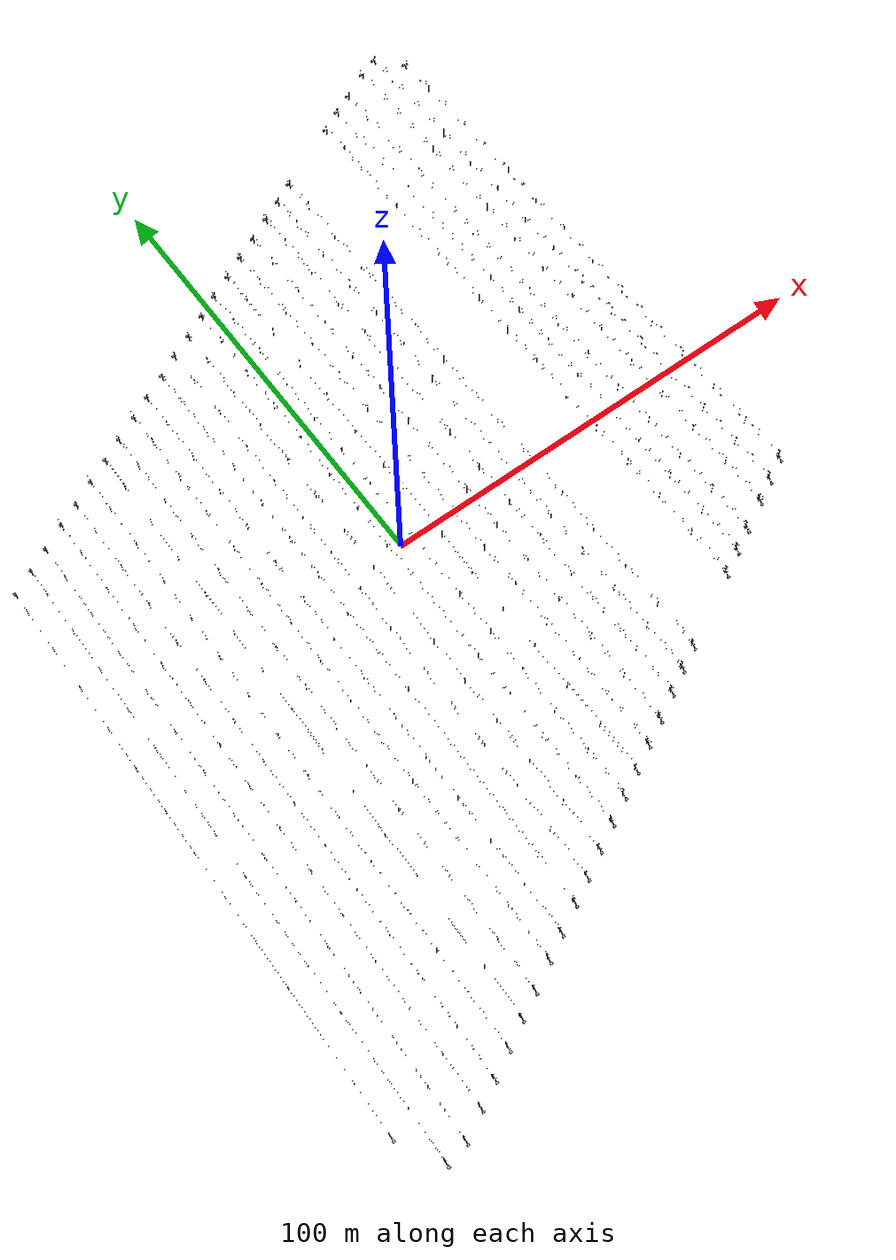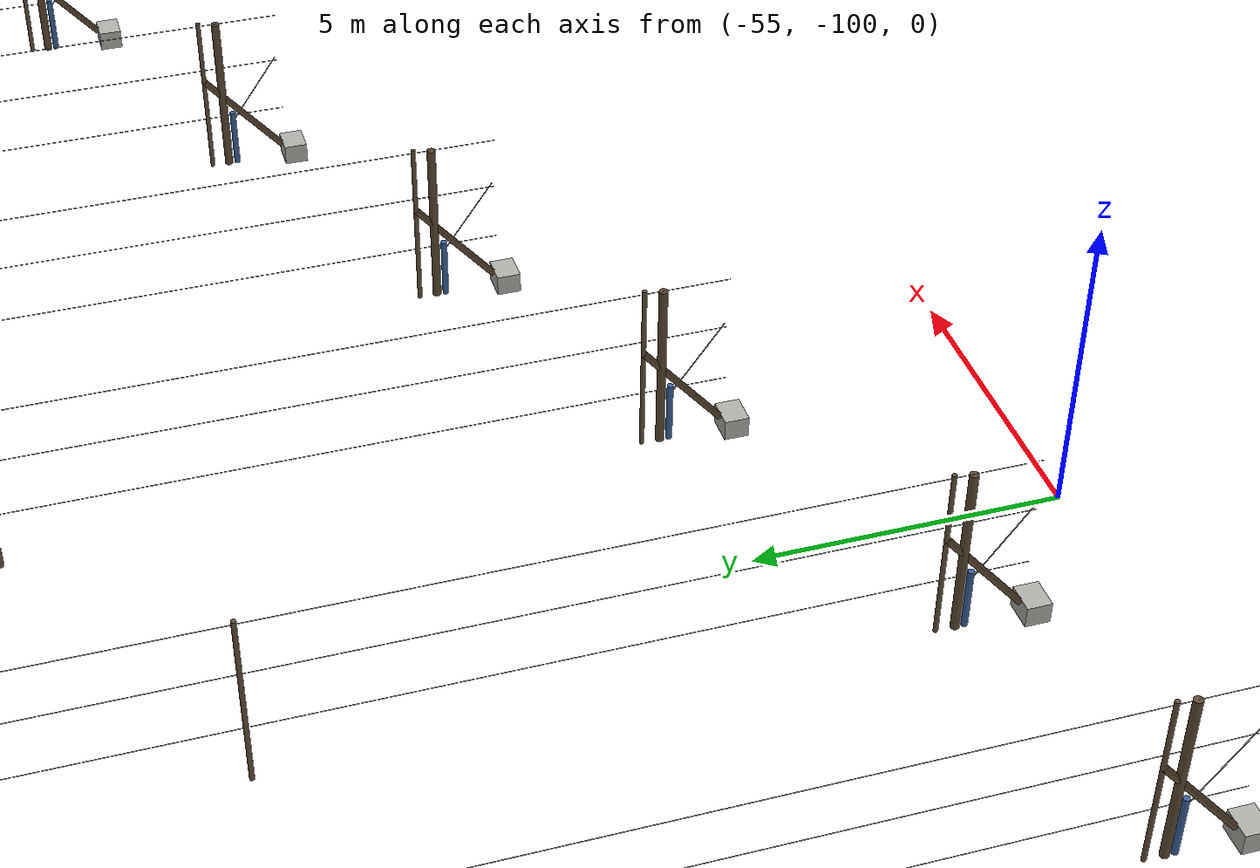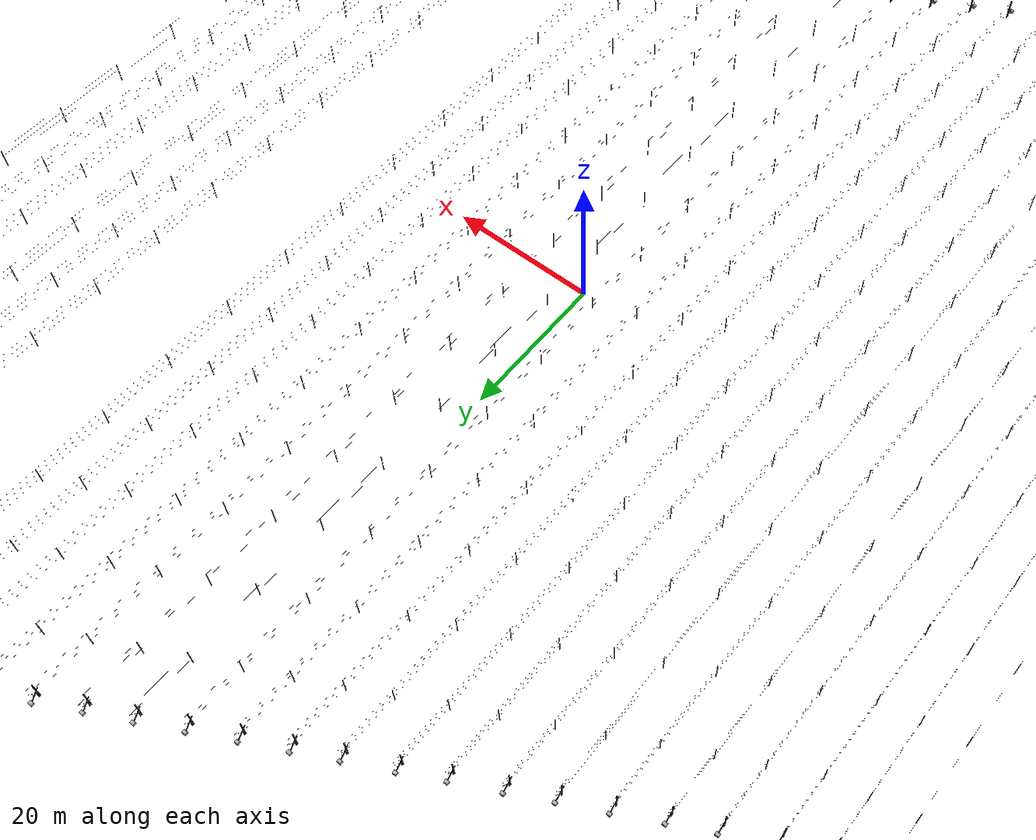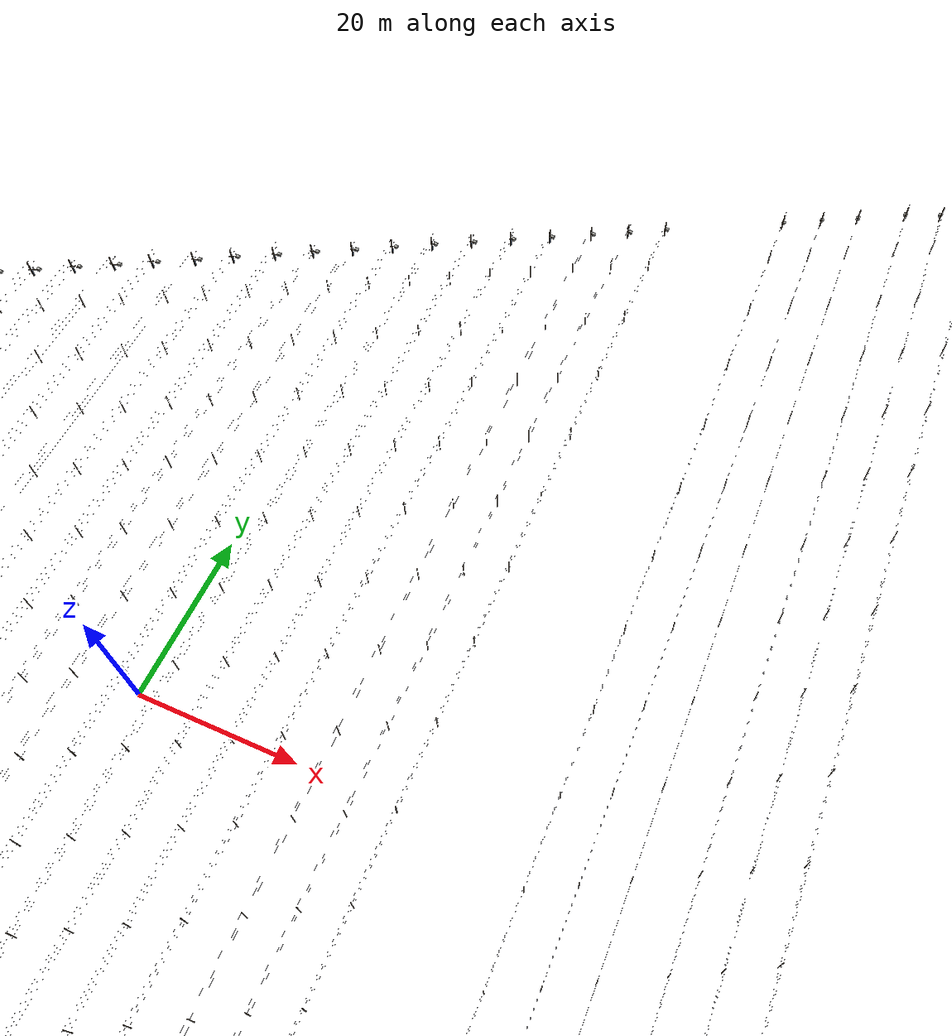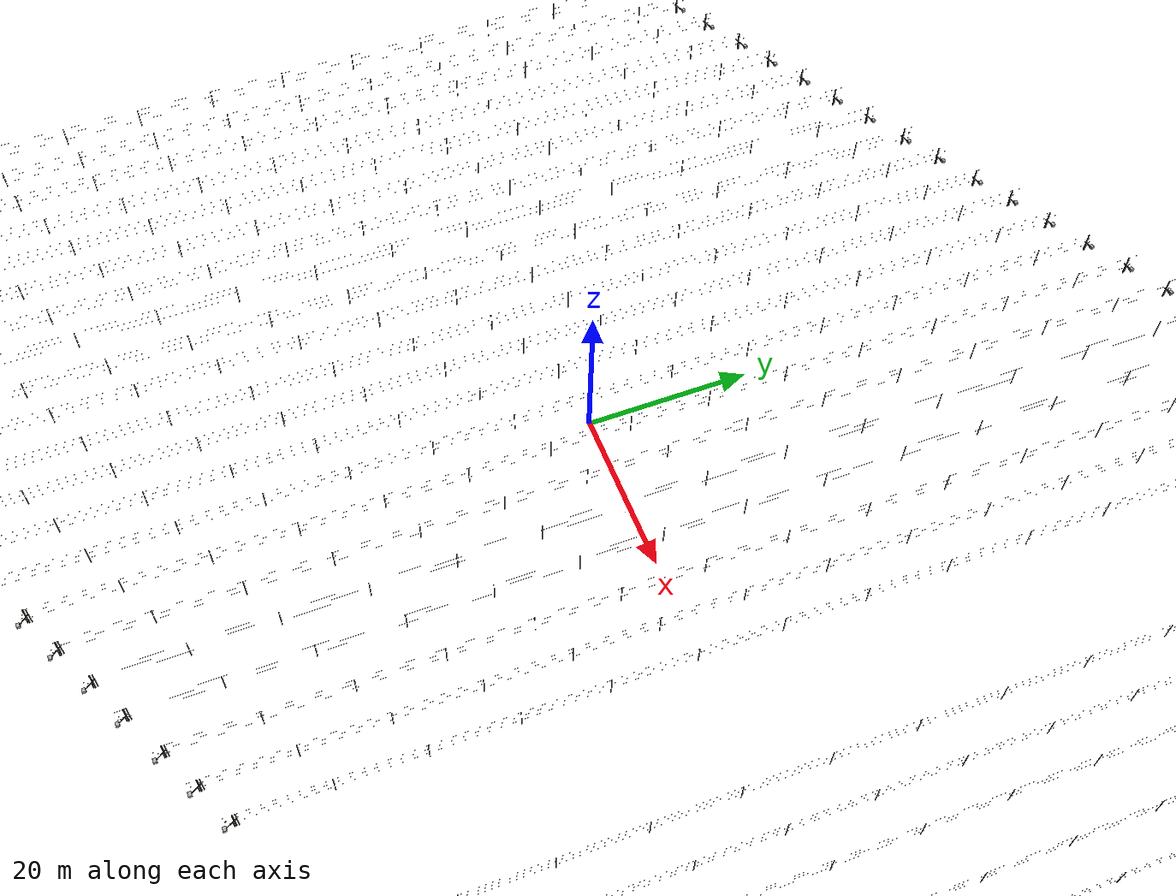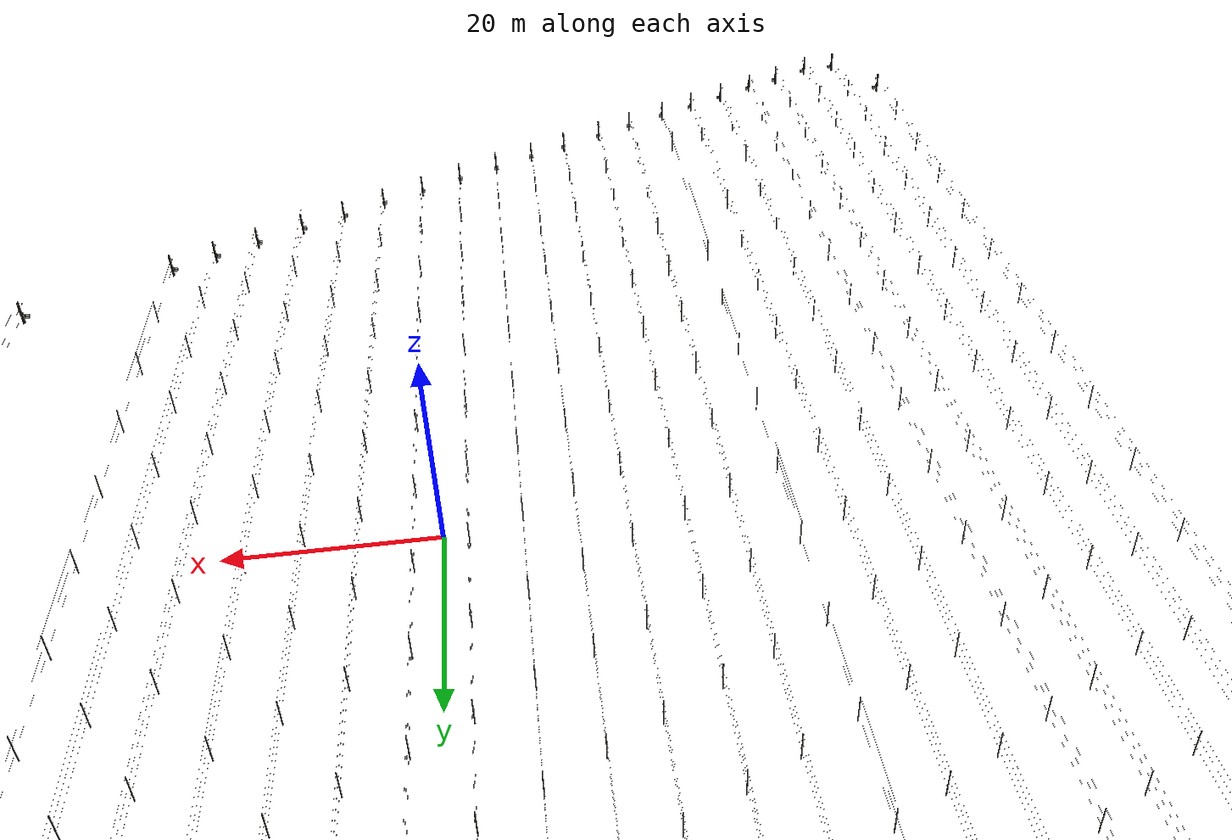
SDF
<sdf version="1.9">
 <world name="orchard_real">
  <plugin filename="gz-sim-physics-system" name="gz::sim::systems::Physics"/>
  <plugin filename="gz-sim-user-commands-system" name="gz::sim::systems::UserCommands"/>
  <plugin filename="gz-sim-scene-broadcaster-system" name="gz::sim::systems::SceneBroadcaster"/>
  <plugin filename="gz-sim-sensors-system" name="gz::sim::systems::Sensors">
   <render_engine>ogre2</render_engine>
  </plugin>
  <plugin filename="gz-sim-imu-system" name="gz::sim::systems::Imu"/>
  <plugin filename="gz-sim-navsat-system" name="gz::sim::systems::NavSat"/>
  <physics name="2ms" type="dart">
   <max_step_size>0.002</max_step_size>
   <real_time_factor>1.0</real_time_factor>
   <dart><collision_detector>bullet</collision_detector></dart>
  </physics>
  <spherical_coordinates>
   <surface_model>EARTH_WGS84</surface_model>
   <world_frame_orientation>ENU</world_frame_orientation>
   <latitude_deg>36.57</latitude_deg>
   <longitude_deg>128.50</longitude_deg>
   <elevation>50.0</elevation>
  </spherical_coordinates>
  <scene>
   <ambient>0.5 0.5 0.5 1</ambient>
   <background>0.6 0.7 0.85</background>
   <shadows>false</shadows>
   <grid>false</grid>
  </scene>
  <light type="directional" name="sun">
   <cast_shadows>false</cast_shadows>
   <pose>0 0 20 0 0 0</pose>
   <diffuse>1.0 0.98 0.95 1</diffuse>
   <specular>0.2 0.2 0.2 1</specular>
   <direction>-0.4 0.3 -0.85</direction>
  </light>
  <model name="trellis_r0">
   <static>true</static>
   <link name="link">
    <visual name="post_1">
     <pose>-66.917 -89.078 1.498 0.0000 0.0000 0.0000</pose>
     <geometry><cylinder><radius>0.0375</radius><length>2.9600</length></cylinder></geometry>
     <material>
      <ambient>0.350 0.280 0.200 1</ambient>
      <diffuse>0.385 0.308 0.220 1</diffuse>
      <specular>0.105 0.084 0.060 1</specular>
     </material>
     <plugin filename="gz-sim-label-system" name="gz::sim::systems::Label"><label>12</label></plugin>
    </visual>
    <visual name="post_2">
     <pose>-66.917 -79.078 1.499 0.0000 0.0000 0.0000</pose>
     <geometry><cylinder><radius>0.0375</radius><length>2.9600</length></cylinder></geometry>
     <material>
      <ambient>0.350 0.280 0.200 1</ambient>
      <diffuse>0.385 0.308 0.220 1</diffuse>
      <specular>0.105 0.084 0.060 1</specular>
     </material>
     <plugin filename="gz-sim-label-system" name="gz::sim::systems::Label"><label>12</label></plugin>
    </visual>
    <visual name="post_3">
     <pose>-66.917 -69.078 1.498 0.0000 0.0000 0.0000</pose>
     <geometry><cylinder><radius>0.0375</radius><length>2.9600</length></cylinder></geometry>
     <material>
      <ambient>0.350 0.280 0.200 1</ambient>
      <diffuse>0.385 0.308 0.220 1</diffuse>
      <specular>0.105 0.084 0.060 1</specular>
     </material>
     <plugin filename="gz-sim-label-system" name="gz::sim::systems::Label"><label>12</label></plugin>
    </visual>
    <visual name="post_4">
     <pose>-66.917 -59.078 1.497 0.0000 0.0000 0.0000</pose>
     <geometry><cylinder><radius>0.0375</radius><length>2.9600</length></cylinder></geometry>
     <material>
      <ambient>0.350 0.280 0.200 1</ambient>
      <diffuse>0.385 0.308 0.220 1</diffuse>
      <specular>0.105 0.084 0.060 1</specular>
     </material>
     <plugin filename="gz-sim-label-system" name="gz::sim::systems::Label"><label>12</label></plugin>
    </visual>
    <visual name="post_5">
     <pose>-66.917 -49.078 1.494 0.0000 0.0000 0.0000</pose>
     <geometry><cylinder><radius>0.0375</radius><length>2.9600</length></cylinder></geometry>
     <material>
      <ambient>0.350 0.280 0.200 1</ambient>
      <diffuse>0.385 0.308 0.220 1</diffuse>
      <specular>0.105 0.084 0.060 1</specular>
     </material>
     <plugin filename="gz-sim-label-system" name="gz::sim::systems::Label"><label>12</label></plugin>
    </visual>
    <visual name="post_6">
     <pose>-66.917 -39.078 1.494 0.0000 0.0000 0.0000</pose>
     <geometry><cylinder><radius>0.0375</radius><length>2.9600</length></cylinder></geometry>
     <material>
      <ambient>0.350 0.280 0.200 1</ambient>
      <diffuse>0.385 0.308 0.220 1</diffuse>
      <specular>0.105 0.084 0.060 1</specular>
     </material>
     <plugin filename="gz-sim-label-system" name="gz::sim::systems::Label"><label>12</label></plugin>
    </visual>
    <visual name="post_7">
     <pose>-66.917 -29.078 1.495 0.0000 0.0000 0.0000</pose>
     <geometry><cylinder><radius>0.0375</radius><length>2.9600</length></cylinder></geometry>
     <material>
      <ambient>0.350 0.280 0.200 1</ambient>
      <diffuse>0.385 0.308 0.220 1</diffuse>
      <specular>0.105 0.084 0.060 1</specular>
     </material>
     <plugin filename="gz-sim-label-system" name="gz::sim::systems::Label"><label>12</label></plugin>
    </visual>
    <visual name="post_8">
     <pose>-66.917 -19.078 1.496 0.0000 0.0000 0.0000</pose>
     <geometry><cylinder><radius>0.0375</radius><length>2.9600</length></cylinder></geometry>
     <material>
      <ambient>0.350 0.280 0.200 1</ambient>
      <diffuse>0.385 0.308 0.220 1</diffuse>
      <specular>0.105 0.084 0.060 1</specular>
     </material>
     <plugin filename="gz-sim-label-system" name="gz::sim::systems::Label"><label>12</label></plugin>
    </visual>
    <visual name="post_9">
     <pose>-66.917 -9.078 1.497 0.0000 0.0000 0.0000</pose>
     <geometry><cylinder><radius>0.0375</radius><length>2.9600</length></cylinder></geometry>
     <material>
      <ambient>0.350 0.280 0.200 1</ambient>
      <diffuse>0.385 0.308 0.220 1</diffuse>
      <specular>0.105 0.084 0.060 1</specular>
     </material>
     <plugin filename="gz-sim-label-system" name="gz::sim::systems::Label"><label>12</label></plugin>
    </visual>
    <visual name="post_10">
     <pose>-66.917 0.922 1.498 0.0000 0.0000 0.0000</pose>
     <geometry><cylinder><radius>0.0375</radius><length>2.9600</length></cylinder></geometry>
     <material>
      <ambient>0.350 0.280 0.200 1</ambient>
      <diffuse>0.385 0.308 0.220 1</diffuse>
      <specular>0.105 0.084 0.060 1</specular>
     </material>
     <plugin filename="gz-sim-label-system" name="gz::sim::systems::Label"><label>12</label></plugin>
    </visual>
    <visual name="post_11">
     <pose>-66.917 10.922 1.497 0.0000 0.0000 0.0000</pose>
     <geometry><cylinder><radius>0.0375</radius><length>2.9600</length></cylinder></geometry>
     <material>
      <ambient>0.350 0.280 0.200 1</ambient>
      <diffuse>0.385 0.308 0.220 1</diffuse>
      <specular>0.105 0.084 0.060 1</specular>
     </material>
     <plugin filename="gz-sim-label-system" name="gz::sim::systems::Label"><label>12</label></plugin>
    </visual>
    <visual name="post_12">
     <pose>-66.917 20.922 1.497 0.0000 0.0000 0.0000</pose>
     <geometry><cylinder><radius>0.0375</radius><length>2.9600</length></cylinder></geometry>
     <material>
      <ambient>0.350 0.280 0.200 1</ambient>
      <diffuse>0.385 0.308 0.220 1</diffuse>
      <specular>0.105 0.084 0.060 1</specular>
     </material>
     <plugin filename="gz-sim-label-system" name="gz::sim::systems::Label"><label>12</label></plugin>
    </visual>
    <visual name="post_13">
     <pose>-66.917 30.922 1.492 0.0000 0.0000 0.0000</pose>
     <geometry><cylinder><radius>0.0375</radius><length>2.9600</length></cylinder></geometry>
     <material>
      <ambient>0.350 0.280 0.200 1</ambient>
      <diffuse>0.385 0.308 0.220 1</diffuse>
      <specular>0.105 0.084 0.060 1</specular>
     </material>
     <plugin filename="gz-sim-label-system" name="gz::sim::systems::Label"><label>12</label></plugin>
    </visual>
    <visual name="wire_14">
     <pose>-66.917 -27.079 1.014 -0.0001 0.0000 0.0000</pose>
     <geometry><box><size>0.0060 126.4780 0.0060</size></box></geometry>
     <material>
      <ambient>0.550 0.550 0.580 1</ambient>
      <diffuse>0.605 0.605 0.638 1</diffuse>
      <specular>0.165 0.165 0.174 1</specular>
     </material>
     <plugin filename="gz-sim-label-system" name="gz::sim::systems::Label"><label>13</label></plugin>
    </visual>
    <visual name="wire_15">
     <pose>-66.917 -27.079 2.014 -0.0001 0.0000 0.0000</pose>
     <geometry><box><size>0.0060 126.4780 0.0060</size></box></geometry>
     <material>
      <ambient>0.550 0.550 0.580 1</ambient>
      <diffuse>0.605 0.605 0.638 1</diffuse>
      <specular>0.165 0.165 0.174 1</specular>
     </material>
     <plugin filename="gz-sim-label-system" name="gz::sim::systems::Label"><label>13</label></plugin>
    </visual>
    <visual name="wire_16">
     <pose>-66.917 -27.079 2.914 -0.0001 0.0000 0.0000</pose>
     <geometry><box><size>0.0060 126.4780 0.0060</size></box></geometry>
     <material>
      <ambient>0.550 0.550 0.580 1</ambient>
      <diffuse>0.605 0.605 0.638 1</diffuse>
      <specular>0.165 0.165 0.174 1</specular>
     </material>
     <plugin filename="gz-sim-label-system" name="gz::sim::systems::Label"><label>13</label></plugin>
    </visual>
   </link>
  </model>
  <model name="trellis_r1">
   <static>true</static>
   <link name="link">
    <visual name="post_1">
     <pose>-61.917 -97.948 1.494 0.0000 0.0000 0.0000</pose>
     <geometry><cylinder><radius>0.0375</radius><length>2.9600</length></cylinder></geometry>
     <material>
      <ambient>0.350 0.280 0.200 1</ambient>
      <diffuse>0.385 0.308 0.220 1</diffuse>
      <specular>0.105 0.084 0.060 1</specular>
     </material>
     <plugin filename="gz-sim-label-system" name="gz::sim::systems::Label"><label>12</label></plugin>
    </visual>
    <visual name="post_2">
     <pose>-61.917 -87.948 1.499 0.0000 0.0000 0.0000</pose>
     <geometry><cylinder><radius>0.0375</radius><length>2.9600</length></cylinder></geometry>
     <material>
      <ambient>0.350 0.280 0.200 1</ambient>
      <diffuse>0.385 0.308 0.220 1</diffuse>
      <specular>0.105 0.084 0.060 1</specular>
     </material>
     <plugin filename="gz-sim-label-system" name="gz::sim::systems::Label"><label>12</label></plugin>
    </visual>
    <visual name="post_3">
     <pose>-61.917 -77.948 1.500 0.0000 0.0000 0.0000</pose>
     <geometry><cylinder><radius>0.0375</radius><length>2.9600</length></cylinder></geometry>
     <material>
      <ambient>0.350 0.280 0.200 1</ambient>
      <diffuse>0.385 0.308 0.220 1</diffuse>
      <specular>0.105 0.084 0.060 1</specular>
     </material>
     <plugin filename="gz-sim-label-system" name="gz::sim::systems::Label"><label>12</label></plugin>
    </visual>
    <visual name="post_4">
     <pose>-61.917 -67.948 1.499 0.0000 0.0000 0.0000</pose>
     <geometry><cylinder><radius>0.0375</radius><length>2.9600</length></cylinder></geometry>
     <material>
      <ambient>0.350 0.280 0.200 1</ambient>
      <diffuse>0.385 0.308 0.220 1</diffuse>
      <specular>0.105 0.084 0.060 1</specular>
     </material>
     <plugin filename="gz-sim-label-system" name="gz::sim::systems::Label"><label>12</label></plugin>
    </visual>
    <visual name="post_5">
     <pose>-61.917 -57.948 1.498 0.0000 0.0000 0.0000</pose>
     <geometry><cylinder><radius>0.0375</radius><length>2.9600</length></cylinder></geometry>
     <material>
      <ambient>0.350 0.280 0.200 1</ambient>
      <diffuse>0.385 0.308 0.220 1</diffuse>
      <specular>0.105 0.084 0.060 1</specular>
     </material>
     <plugin filename="gz-sim-label-system" name="gz::sim::systems::Label"><label>12</label></plugin>
    </visual>
    <visual name="post_6">
     <pose>-61.917 -47.948 1.495 0.0000 0.0000 0.0000</pose>
     <geometry><cylinder><radius>0.0375</radius><length>2.9600</length></cylinder></geometry>
     <material>
      <ambient>0.350 0.280 0.200 1</ambient>
      <diffuse>0.385 0.308 0.220 1</diffuse>
      <specular>0.105 0.084 0.060 1</specular>
     </material>
     <plugin filename="gz-sim-label-system" name="gz::sim::systems::Label"><label>12</label></plugin>
    </visual>
    <visual name="post_7">
     <pose>-61.917 -37.948 1.495 0.0000 0.0000 0.0000</pose>
     <geometry><cylinder><radius>0.0375</radius><length>2.9600</length></cylinder></geometry>
     <material>
      <ambient>0.350 0.280 0.200 1</ambient>
      <diffuse>0.385 0.308 0.220 1</diffuse>
      <specular>0.105 0.084 0.060 1</specular>
     </material>
     <plugin filename="gz-sim-label-system" name="gz::sim::systems::Label"><label>12</label></plugin>
    </visual>
    <visual name="post_8">
     <pose>-61.917 -27.948 1.497 0.0000 0.0000 0.0000</pose>
     <geometry><cylinder><radius>0.0375</radius><length>2.9600</length></cylinder></geometry>
     <material>
      <ambient>0.350 0.280 0.200 1</ambient>
      <diffuse>0.385 0.308 0.220 1</diffuse>
      <specular>0.105 0.084 0.060 1</specular>
     </material>
     <plugin filename="gz-sim-label-system" name="gz::sim::systems::Label"><label>12</label></plugin>
    </visual>
    <visual name="post_9">
     <pose>-61.917 -17.948 1.497 0.0000 0.0000 0.0000</pose>
     <geometry><cylinder><radius>0.0375</radius><length>2.9600</length></cylinder></geometry>
     <material>
      <ambient>0.350 0.280 0.200 1</ambient>
      <diffuse>0.385 0.308 0.220 1</diffuse>
      <specular>0.105 0.084 0.060 1</specular>
     </material>
     <plugin filename="gz-sim-label-system" name="gz::sim::systems::Label"><label>12</label></plugin>
    </visual>
    <visual name="post_10">
     <pose>-61.917 -7.948 1.498 0.0000 0.0000 0.0000</pose>
     <geometry><cylinder><radius>0.0375</radius><length>2.9600</length></cylinder></geometry>
     <material>
      <ambient>0.350 0.280 0.200 1</ambient>
      <diffuse>0.385 0.308 0.220 1</diffuse>
      <specular>0.105 0.084 0.060 1</specular>
     </material>
     <plugin filename="gz-sim-label-system" name="gz::sim::systems::Label"><label>12</label></plugin>
    </visual>
    <visual name="post_11">
     <pose>-61.917 2.052 1.498 0.0000 0.0000 0.0000</pose>
     <geometry><cylinder><radius>0.0375</radius><length>2.9600</length></cylinder></geometry>
     <material>
      <ambient>0.350 0.280 0.200 1</ambient>
      <diffuse>0.385 0.308 0.220 1</diffuse>
      <specular>0.105 0.084 0.060 1</specular>
     </material>
     <plugin filename="gz-sim-label-system" name="gz::sim::systems::Label"><label>12</label></plugin>
    </visual>
    <visual name="post_12">
     <pose>-61.917 12.052 1.497 0.0000 0.0000 0.0000</pose>
     <geometry><cylinder><radius>0.0375</radius><length>2.9600</length></cylinder></geometry>
     <material>
      <ambient>0.350 0.280 0.200 1</ambient>
      <diffuse>0.385 0.308 0.220 1</diffuse>
      <specular>0.105 0.084 0.060 1</specular>
     </material>
     <plugin filename="gz-sim-label-system" name="gz::sim::systems::Label"><label>12</label></plugin>
    </visual>
    <visual name="post_13">
     <pose>-61.917 22.052 1.496 0.0000 0.0000 0.0000</pose>
     <geometry><cylinder><radius>0.0375</radius><length>2.9600</length></cylinder></geometry>
     <material>
      <ambient>0.350 0.280 0.200 1</ambient>
      <diffuse>0.385 0.308 0.220 1</diffuse>
      <specular>0.105 0.084 0.060 1</specular>
     </material>
     <plugin filename="gz-sim-label-system" name="gz::sim::systems::Label"><label>12</label></plugin>
    </visual>
    <visual name="post_14">
     <pose>-61.917 32.052 1.490 0.0000 0.0000 0.0000</pose>
     <geometry><cylinder><radius>0.0375</radius><length>2.9600</length></cylinder></geometry>
     <material>
      <ambient>0.350 0.280 0.200 1</ambient>
      <diffuse>0.385 0.308 0.220 1</diffuse>
      <specular>0.105 0.084 0.060 1</specular>
     </material>
     <plugin filename="gz-sim-label-system" name="gz::sim::systems::Label"><label>12</label></plugin>
    </visual>
    <visual name="wire_15">
     <pose>-61.917 -30.187 1.011 -0.0000 0.0000 0.0000</pose>
     <geometry><box><size>0.0060 138.2335 0.0060</size></box></geometry>
     <material>
      <ambient>0.550 0.550 0.580 1</ambient>
      <diffuse>0.605 0.605 0.638 1</diffuse>
      <specular>0.165 0.165 0.174 1</specular>
     </material>
     <plugin filename="gz-sim-label-system" name="gz::sim::systems::Label"><label>13</label></plugin>
    </visual>
    <visual name="wire_16">
     <pose>-61.917 -30.187 2.011 -0.0000 0.0000 0.0000</pose>
     <geometry><box><size>0.0060 138.2335 0.0060</size></box></geometry>
     <material>
      <ambient>0.550 0.550 0.580 1</ambient>
      <diffuse>0.605 0.605 0.638 1</diffuse>
      <specular>0.165 0.165 0.174 1</specular>
     </material>
     <plugin filename="gz-sim-label-system" name="gz::sim::systems::Label"><label>13</label></plugin>
    </visual>
    <visual name="wire_17">
     <pose>-61.917 -30.187 2.911 -0.0000 0.0000 0.0000</pose>
     <geometry><box><size>0.0060 138.2335 0.0060</size></box></geometry>
     <material>
      <ambient>0.550 0.550 0.580 1</ambient>
      <diffuse>0.605 0.605 0.638 1</diffuse>
      <specular>0.165 0.165 0.174 1</specular>
     </material>
     <plugin filename="gz-sim-label-system" name="gz::sim::systems::Label"><label>13</label></plugin>
    </visual>
   </link>
  </model>
  <model name="trellis_r2">
   <static>true</static>
   <link name="link">
    <visual name="post_1">
     <pose>-57.167 -97.025 1.496 0.0000 0.0000 0.0000</pose>
     <geometry><cylinder><radius>0.0375</radius><length>2.9600</length></cylinder></geometry>
     <material>
      <ambient>0.350 0.280 0.200 1</ambient>
      <diffuse>0.385 0.308 0.220 1</diffuse>
      <specular>0.105 0.084 0.060 1</specular>
     </material>
     <plugin filename="gz-sim-label-system" name="gz::sim::systems::Label"><label>12</label></plugin>
    </visual>
    <visual name="post_2">
     <pose>-57.167 -87.025 1.501 0.0000 0.0000 0.0000</pose>
     <geometry><cylinder><radius>0.0375</radius><length>2.9600</length></cylinder></geometry>
     <material>
      <ambient>0.350 0.280 0.200 1</ambient>
      <diffuse>0.385 0.308 0.220 1</diffuse>
      <specular>0.105 0.084 0.060 1</specular>
     </material>
     <plugin filename="gz-sim-label-system" name="gz::sim::systems::Label"><label>12</label></plugin>
    </visual>
    <visual name="post_3">
     <pose>-57.167 -77.025 1.501 0.0000 0.0000 0.0000</pose>
     <geometry><cylinder><radius>0.0375</radius><length>2.9600</length></cylinder></geometry>
     <material>
      <ambient>0.350 0.280 0.200 1</ambient>
      <diffuse>0.385 0.308 0.220 1</diffuse>
      <specular>0.105 0.084 0.060 1</specular>
     </material>
     <plugin filename="gz-sim-label-system" name="gz::sim::systems::Label"><label>12</label></plugin>
    </visual>
    <visual name="post_4">
     <pose>-57.167 -67.025 1.498 0.0000 0.0000 0.0000</pose>
     <geometry><cylinder><radius>0.0375</radius><length>2.9600</length></cylinder></geometry>
     <material>
      <ambient>0.350 0.280 0.200 1</ambient>
      <diffuse>0.385 0.308 0.220 1</diffuse>
      <specular>0.105 0.084 0.060 1</specular>
     </material>
     <plugin filename="gz-sim-label-system" name="gz::sim::systems::Label"><label>12</label></plugin>
    </visual>
    <visual name="post_5">
     <pose>-57.167 -57.025 1.498 0.0000 0.0000 0.0000</pose>
     <geometry><cylinder><radius>0.0375</radius><length>2.9600</length></cylinder></geometry>
     <material>
      <ambient>0.350 0.280 0.200 1</ambient>
      <diffuse>0.385 0.308 0.220 1</diffuse>
      <specular>0.105 0.084 0.060 1</specular>
     </material>
     <plugin filename="gz-sim-label-system" name="gz::sim::systems::Label"><label>12</label></plugin>
    </visual>
    <visual name="post_6">
     <pose>-57.167 -47.025 1.497 0.0000 0.0000 0.0000</pose>
     <geometry><cylinder><radius>0.0375</radius><length>2.9600</length></cylinder></geometry>
     <material>
      <ambient>0.350 0.280 0.200 1</ambient>
      <diffuse>0.385 0.308 0.220 1</diffuse>
      <specular>0.105 0.084 0.060 1</specular>
     </material>
     <plugin filename="gz-sim-label-system" name="gz::sim::systems::Label"><label>12</label></plugin>
    </visual>
    <visual name="post_7">
     <pose>-57.167 -37.025 1.498 0.0000 0.0000 0.0000</pose>
     <geometry><cylinder><radius>0.0375</radius><length>2.9600</length></cylinder></geometry>
     <material>
      <ambient>0.350 0.280 0.200 1</ambient>
      <diffuse>0.385 0.308 0.220 1</diffuse>
      <specular>0.105 0.084 0.060 1</specular>
     </material>
     <plugin filename="gz-sim-label-system" name="gz::sim::systems::Label"><label>12</label></plugin>
    </visual>
    <visual name="post_8">
     <pose>-57.167 -27.025 1.499 0.0000 0.0000 0.0000</pose>
     <geometry><cylinder><radius>0.0375</radius><length>2.9600</length></cylinder></geometry>
     <material>
      <ambient>0.350 0.280 0.200 1</ambient>
      <diffuse>0.385 0.308 0.220 1</diffuse>
      <specular>0.105 0.084 0.060 1</specular>
     </material>
     <plugin filename="gz-sim-label-system" name="gz::sim::systems::Label"><label>12</label></plugin>
    </visual>
    <visual name="post_9">
     <pose>-57.167 -17.025 1.498 0.0000 0.0000 0.0000</pose>
     <geometry><cylinder><radius>0.0375</radius><length>2.9600</length></cylinder></geometry>
     <material>
      <ambient>0.350 0.280 0.200 1</ambient>
      <diffuse>0.385 0.308 0.220 1</diffuse>
      <specular>0.105 0.084 0.060 1</specular>
     </material>
     <plugin filename="gz-sim-label-system" name="gz::sim::systems::Label"><label>12</label></plugin>
    </visual>
    <visual name="post_10">
     <pose>-57.167 -7.025 1.498 0.0000 0.0000 0.0000</pose>
     <geometry><cylinder><radius>0.0375</radius><length>2.9600</length></cylinder></geometry>
     <material>
      <ambient>0.350 0.280 0.200 1</ambient>
      <diffuse>0.385 0.308 0.220 1</diffuse>
      <specular>0.105 0.084 0.060 1</specular>
     </material>
     <plugin filename="gz-sim-label-system" name="gz::sim::systems::Label"><label>12</label></plugin>
    </visual>
    <visual name="post_11">
     <pose>-57.167 2.975 1.497 0.0000 0.0000 0.0000</pose>
     <geometry><cylinder><radius>0.0375</radius><length>2.9600</length></cylinder></geometry>
     <material>
      <ambient>0.350 0.280 0.200 1</ambient>
      <diffuse>0.385 0.308 0.220 1</diffuse>
      <specular>0.105 0.084 0.060 1</specular>
     </material>
     <plugin filename="gz-sim-label-system" name="gz::sim::systems::Label"><label>12</label></plugin>
    </visual>
    <visual name="post_12">
     <pose>-57.167 12.975 1.496 0.0000 0.0000 0.0000</pose>
     <geometry><cylinder><radius>0.0375</radius><length>2.9600</length></cylinder></geometry>
     <material>
      <ambient>0.350 0.280 0.200 1</ambient>
      <diffuse>0.385 0.308 0.220 1</diffuse>
      <specular>0.105 0.084 0.060 1</specular>
     </material>
     <plugin filename="gz-sim-label-system" name="gz::sim::systems::Label"><label>12</label></plugin>
    </visual>
    <visual name="post_13">
     <pose>-57.167 22.975 1.494 0.0000 0.0000 0.0000</pose>
     <geometry><cylinder><radius>0.0375</radius><length>2.9600</length></cylinder></geometry>
     <material>
      <ambient>0.350 0.280 0.200 1</ambient>
      <diffuse>0.385 0.308 0.220 1</diffuse>
      <specular>0.105 0.084 0.060 1</specular>
     </material>
     <plugin filename="gz-sim-label-system" name="gz::sim::systems::Label"><label>12</label></plugin>
    </visual>
    <visual name="post_14">
     <pose>-57.167 32.975 1.489 0.0000 0.0000 0.0000</pose>
     <geometry><cylinder><radius>0.0375</radius><length>2.9600</length></cylinder></geometry>
     <material>
      <ambient>0.350 0.280 0.200 1</ambient>
      <diffuse>0.385 0.308 0.220 1</diffuse>
      <specular>0.105 0.084 0.060 1</specular>
     </material>
     <plugin filename="gz-sim-label-system" name="gz::sim::systems::Label"><label>12</label></plugin>
    </visual>
    <visual name="wire_15">
     <pose>-57.167 -28.513 1.011 -0.0001 0.0000 0.0000</pose>
     <geometry><box><size>0.0060 139.7635 0.0060</size></box></geometry>
     <material>
      <ambient>0.550 0.550 0.580 1</ambient>
      <diffuse>0.605 0.605 0.638 1</diffuse>
      <specular>0.165 0.165 0.174 1</specular>
     </material>
     <plugin filename="gz-sim-label-system" name="gz::sim::systems::Label"><label>13</label></plugin>
    </visual>
    <visual name="wire_16">
     <pose>-57.167 -28.513 2.011 -0.0001 0.0000 0.0000</pose>
     <geometry><box><size>0.0060 139.7635 0.0060</size></box></geometry>
     <material>
      <ambient>0.550 0.550 0.580 1</ambient>
      <diffuse>0.605 0.605 0.638 1</diffuse>
      <specular>0.165 0.165 0.174 1</specular>
     </material>
     <plugin filename="gz-sim-label-system" name="gz::sim::systems::Label"><label>13</label></plugin>
    </visual>
    <visual name="wire_17">
     <pose>-57.167 -28.513 2.911 -0.0001 0.0000 0.0000</pose>
     <geometry><box><size>0.0060 139.7635 0.0060</size></box></geometry>
     <material>
      <ambient>0.550 0.550 0.580 1</ambient>
      <diffuse>0.605 0.605 0.638 1</diffuse>
      <specular>0.165 0.165 0.174 1</specular>
     </material>
     <plugin filename="gz-sim-label-system" name="gz::sim::systems::Label"><label>13</label></plugin>
    </visual>
   </link>
  </model>
  <model name="trellis_r3">
   <static>true</static>
   <link name="link">
    <visual name="post_1">
     <pose>-51.917 -94.254 1.499 0.0000 0.0000 0.0000</pose>
     <geometry><cylinder><radius>0.0375</radius><length>2.9600</length></cylinder></geometry>
     <material>
      <ambient>0.350 0.280 0.200 1</ambient>
      <diffuse>0.385 0.308 0.220 1</diffuse>
      <specular>0.105 0.084 0.060 1</specular>
     </material>
     <plugin filename="gz-sim-label-system" name="gz::sim::systems::Label"><label>12</label></plugin>
    </visual>
    <visual name="post_2">
     <pose>-51.917 -84.254 1.502 0.0000 0.0000 0.0000</pose>
     <geometry><cylinder><radius>0.0375</radius><length>2.9600</length></cylinder></geometry>
     <material>
      <ambient>0.350 0.280 0.200 1</ambient>
      <diffuse>0.385 0.308 0.220 1</diffuse>
      <specular>0.105 0.084 0.060 1</specular>
     </material>
     <plugin filename="gz-sim-label-system" name="gz::sim::systems::Label"><label>12</label></plugin>
    </visual>
    <visual name="post_3">
     <pose>-51.917 -74.254 1.500 0.0000 0.0000 0.0000</pose>
     <geometry><cylinder><radius>0.0375</radius><length>2.9600</length></cylinder></geometry>
     <material>
      <ambient>0.350 0.280 0.200 1</ambient>
      <diffuse>0.385 0.308 0.220 1</diffuse>
      <specular>0.105 0.084 0.060 1</specular>
     </material>
     <plugin filename="gz-sim-label-system" name="gz::sim::systems::Label"><label>12</label></plugin>
    </visual>
    <visual name="post_4">
     <pose>-51.917 -64.254 1.498 0.0000 0.0000 0.0000</pose>
     <geometry><cylinder><radius>0.0375</radius><length>2.9600</length></cylinder></geometry>
     <material>
      <ambient>0.350 0.280 0.200 1</ambient>
      <diffuse>0.385 0.308 0.220 1</diffuse>
      <specular>0.105 0.084 0.060 1</specular>
     </material>
     <plugin filename="gz-sim-label-system" name="gz::sim::systems::Label"><label>12</label></plugin>
    </visual>
    <visual name="post_5">
     <pose>-51.917 -54.254 1.498 0.0000 0.0000 0.0000</pose>
     <geometry><cylinder><radius>0.0375</radius><length>2.9600</length></cylinder></geometry>
     <material>
      <ambient>0.350 0.280 0.200 1</ambient>
      <diffuse>0.385 0.308 0.220 1</diffuse>
      <specular>0.105 0.084 0.060 1</specular>
     </material>
     <plugin filename="gz-sim-label-system" name="gz::sim::systems::Label"><label>12</label></plugin>
    </visual>
    <visual name="post_6">
     <pose>-51.917 -44.254 1.499 0.0000 0.0000 0.0000</pose>
     <geometry><cylinder><radius>0.0375</radius><length>2.9600</length></cylinder></geometry>
     <material>
      <ambient>0.350 0.280 0.200 1</ambient>
      <diffuse>0.385 0.308 0.220 1</diffuse>
      <specular>0.105 0.084 0.060 1</specular>
     </material>
     <plugin filename="gz-sim-label-system" name="gz::sim::systems::Label"><label>12</label></plugin>
    </visual>
    <visual name="post_7">
     <pose>-51.917 -34.254 1.500 0.0000 0.0000 0.0000</pose>
     <geometry><cylinder><radius>0.0375</radius><length>2.9600</length></cylinder></geometry>
     <material>
      <ambient>0.350 0.280 0.200 1</ambient>
      <diffuse>0.385 0.308 0.220 1</diffuse>
      <specular>0.105 0.084 0.060 1</specular>
     </material>
     <plugin filename="gz-sim-label-system" name="gz::sim::systems::Label"><label>12</label></plugin>
    </visual>
    <visual name="post_8">
     <pose>-51.917 -24.254 1.499 0.0000 0.0000 0.0000</pose>
     <geometry><cylinder><radius>0.0375</radius><length>2.9600</length></cylinder></geometry>
     <material>
      <ambient>0.350 0.280 0.200 1</ambient>
      <diffuse>0.385 0.308 0.220 1</diffuse>
      <specular>0.105 0.084 0.060 1</specular>
     </material>
     <plugin filename="gz-sim-label-system" name="gz::sim::systems::Label"><label>12</label></plugin>
    </visual>
    <visual name="post_9">
     <pose>-51.917 -14.254 1.498 0.0000 0.0000 0.0000</pose>
     <geometry><cylinder><radius>0.0375</radius><length>2.9600</length></cylinder></geometry>
     <material>
      <ambient>0.350 0.280 0.200 1</ambient>
      <diffuse>0.385 0.308 0.220 1</diffuse>
      <specular>0.105 0.084 0.060 1</specular>
     </material>
     <plugin filename="gz-sim-label-system" name="gz::sim::systems::Label"><label>12</label></plugin>
    </visual>
    <visual name="post_10">
     <pose>-51.917 -4.254 1.498 0.0000 0.0000 0.0000</pose>
     <geometry><cylinder><radius>0.0375</radius><length>2.9600</length></cylinder></geometry>
     <material>
      <ambient>0.350 0.280 0.200 1</ambient>
      <diffuse>0.385 0.308 0.220 1</diffuse>
      <specular>0.105 0.084 0.060 1</specular>
     </material>
     <plugin filename="gz-sim-label-system" name="gz::sim::systems::Label"><label>12</label></plugin>
    </visual>
    <visual name="post_11">
     <pose>-51.917 5.746 1.496 0.0000 0.0000 0.0000</pose>
     <geometry><cylinder><radius>0.0375</radius><length>2.9600</length></cylinder></geometry>
     <material>
      <ambient>0.350 0.280 0.200 1</ambient>
      <diffuse>0.385 0.308 0.220 1</diffuse>
      <specular>0.105 0.084 0.060 1</specular>
     </material>
     <plugin filename="gz-sim-label-system" name="gz::sim::systems::Label"><label>12</label></plugin>
    </visual>
    <visual name="post_12">
     <pose>-51.917 15.746 1.494 0.0000 0.0000 0.0000</pose>
     <geometry><cylinder><radius>0.0375</radius><length>2.9600</length></cylinder></geometry>
     <material>
      <ambient>0.350 0.280 0.200 1</ambient>
      <diffuse>0.385 0.308 0.220 1</diffuse>
      <specular>0.105 0.084 0.060 1</specular>
     </material>
     <plugin filename="gz-sim-label-system" name="gz::sim::systems::Label"><label>12</label></plugin>
    </visual>
    <visual name="post_13">
     <pose>-51.917 25.746 1.491 0.0000 0.0000 0.0000</pose>
     <geometry><cylinder><radius>0.0375</radius><length>2.9600</length></cylinder></geometry>
     <material>
      <ambient>0.350 0.280 0.200 1</ambient>
      <diffuse>0.385 0.308 0.220 1</diffuse>
      <specular>0.105 0.084 0.060 1</specular>
     </material>
     <plugin filename="gz-sim-label-system" name="gz::sim::systems::Label"><label>12</label></plugin>
    </visual>
    <visual name="post_14">
     <pose>-51.917 35.746 1.487 0.0000 0.0000 0.0000</pose>
     <geometry><cylinder><radius>0.0375</radius><length>2.9600</length></cylinder></geometry>
     <material>
      <ambient>0.350 0.280 0.200 1</ambient>
      <diffuse>0.385 0.308 0.220 1</diffuse>
      <specular>0.105 0.084 0.060 1</specular>
     </material>
     <plugin filename="gz-sim-label-system" name="gz::sim::systems::Label"><label>12</label></plugin>
    </visual>
    <visual name="wire_15">
     <pose>-51.917 -25.743 1.012 -0.0001 0.0000 0.0000</pose>
     <geometry><box><size>0.0060 139.7635 0.0060</size></box></geometry>
     <material>
      <ambient>0.550 0.550 0.580 1</ambient>
      <diffuse>0.605 0.605 0.638 1</diffuse>
      <specular>0.165 0.165 0.174 1</specular>
     </material>
     <plugin filename="gz-sim-label-system" name="gz::sim::systems::Label"><label>13</label></plugin>
    </visual>
    <visual name="wire_16">
     <pose>-51.917 -25.743 2.012 -0.0001 0.0000 0.0000</pose>
     <geometry><box><size>0.0060 139.7635 0.0060</size></box></geometry>
     <material>
      <ambient>0.550 0.550 0.580 1</ambient>
      <diffuse>0.605 0.605 0.638 1</diffuse>
      <specular>0.165 0.165 0.174 1</specular>
     </material>
     <plugin filename="gz-sim-label-system" name="gz::sim::systems::Label"><label>13</label></plugin>
    </visual>
    <visual name="wire_17">
     <pose>-51.917 -25.743 2.912 -0.0001 0.0000 0.0000</pose>
     <geometry><box><size>0.0060 139.7635 0.0060</size></box></geometry>
     <material>
      <ambient>0.550 0.550 0.580 1</ambient>
      <diffuse>0.605 0.605 0.638 1</diffuse>
      <specular>0.165 0.165 0.174 1</specular>
     </material>
     <plugin filename="gz-sim-label-system" name="gz::sim::systems::Label"><label>13</label></plugin>
    </visual>
   </link>
  </model>
  <model name="trellis_r4">
   <static>true</static>
   <link name="link">
    <visual name="post_1">
     <pose>-47.167 -91.830 1.500 0.0000 0.0000 0.0000</pose>
     <geometry><cylinder><radius>0.0375</radius><length>2.9600</length></cylinder></geometry>
     <material>
      <ambient>0.350 0.280 0.200 1</ambient>
      <diffuse>0.385 0.308 0.220 1</diffuse>
      <specular>0.105 0.084 0.060 1</specular>
     </material>
     <plugin filename="gz-sim-label-system" name="gz::sim::systems::Label"><label>12</label></plugin>
    </visual>
    <visual name="post_2">
     <pose>-47.167 -81.830 1.501 0.0000 0.0000 0.0000</pose>
     <geometry><cylinder><radius>0.0375</radius><length>2.9600</length></cylinder></geometry>
     <material>
      <ambient>0.350 0.280 0.200 1</ambient>
      <diffuse>0.385 0.308 0.220 1</diffuse>
      <specular>0.105 0.084 0.060 1</specular>
     </material>
     <plugin filename="gz-sim-label-system" name="gz::sim::systems::Label"><label>12</label></plugin>
    </visual>
    <visual name="post_3">
     <pose>-47.167 -71.830 1.499 0.0000 0.0000 0.0000</pose>
     <geometry><cylinder><radius>0.0375</radius><length>2.9600</length></cylinder></geometry>
     <material>
      <ambient>0.350 0.280 0.200 1</ambient>
      <diffuse>0.385 0.308 0.220 1</diffuse>
      <specular>0.105 0.084 0.060 1</specular>
     </material>
     <plugin filename="gz-sim-label-system" name="gz::sim::systems::Label"><label>12</label></plugin>
    </visual>
    <visual name="post_4">
     <pose>-47.167 -61.830 1.498 0.0000 0.0000 0.0000</pose>
     <geometry><cylinder><radius>0.0375</radius><length>2.9600</length></cylinder></geometry>
     <material>
      <ambient>0.350 0.280 0.200 1</ambient>
      <diffuse>0.385 0.308 0.220 1</diffuse>
      <specular>0.105 0.084 0.060 1</specular>
     </material>
     <plugin filename="gz-sim-label-system" name="gz::sim::systems::Label"><label>12</label></plugin>
    </visual>
    <visual name="post_5">
     <pose>-47.167 -51.830 1.500 0.0000 0.0000 0.0000</pose>
     <geometry><cylinder><radius>0.0375</radius><length>2.9600</length></cylinder></geometry>
     <material>
      <ambient>0.350 0.280 0.200 1</ambient>
      <diffuse>0.385 0.308 0.220 1</diffuse>
      <specular>0.105 0.084 0.060 1</specular>
     </material>
     <plugin filename="gz-sim-label-system" name="gz::sim::systems::Label"><label>12</label></plugin>
    </visual>
    <visual name="post_6">
     <pose>-47.167 -41.830 1.500 0.0000 0.0000 0.0000</pose>
     <geometry><cylinder><radius>0.0375</radius><length>2.9600</length></cylinder></geometry>
     <material>
      <ambient>0.350 0.280 0.200 1</ambient>
      <diffuse>0.385 0.308 0.220 1</diffuse>
      <specular>0.105 0.084 0.060 1</specular>
     </material>
     <plugin filename="gz-sim-label-system" name="gz::sim::systems::Label"><label>12</label></plugin>
    </visual>
    <visual name="post_7">
     <pose>-47.167 -31.830 1.499 0.0000 0.0000 0.0000</pose>
     <geometry><cylinder><radius>0.0375</radius><length>2.9600</length></cylinder></geometry>
     <material>
      <ambient>0.350 0.280 0.200 1</ambient>
      <diffuse>0.385 0.308 0.220 1</diffuse>
      <specular>0.105 0.084 0.060 1</specular>
     </material>
     <plugin filename="gz-sim-label-system" name="gz::sim::systems::Label"><label>12</label></plugin>
    </visual>
    <visual name="post_8">
     <pose>-47.167 -21.830 1.498 0.0000 0.0000 0.0000</pose>
     <geometry><cylinder><radius>0.0375</radius><length>2.9600</length></cylinder></geometry>
     <material>
      <ambient>0.350 0.280 0.200 1</ambient>
      <diffuse>0.385 0.308 0.220 1</diffuse>
      <specular>0.105 0.084 0.060 1</specular>
     </material>
     <plugin filename="gz-sim-label-system" name="gz::sim::systems::Label"><label>12</label></plugin>
    </visual>
    <visual name="post_9">
     <pose>-47.167 -11.830 1.498 0.0000 0.0000 0.0000</pose>
     <geometry><cylinder><radius>0.0375</radius><length>2.9600</length></cylinder></geometry>
     <material>
      <ambient>0.350 0.280 0.200 1</ambient>
      <diffuse>0.385 0.308 0.220 1</diffuse>
      <specular>0.105 0.084 0.060 1</specular>
     </material>
     <plugin filename="gz-sim-label-system" name="gz::sim::systems::Label"><label>12</label></plugin>
    </visual>
    <visual name="post_10">
     <pose>-47.167 -1.830 1.496 0.0000 0.0000 0.0000</pose>
     <geometry><cylinder><radius>0.0375</radius><length>2.9600</length></cylinder></geometry>
     <material>
      <ambient>0.350 0.280 0.200 1</ambient>
      <diffuse>0.385 0.308 0.220 1</diffuse>
      <specular>0.105 0.084 0.060 1</specular>
     </material>
     <plugin filename="gz-sim-label-system" name="gz::sim::systems::Label"><label>12</label></plugin>
    </visual>
    <visual name="post_11">
     <pose>-47.167 8.170 1.495 0.0000 0.0000 0.0000</pose>
     <geometry><cylinder><radius>0.0375</radius><length>2.9600</length></cylinder></geometry>
     <material>
      <ambient>0.350 0.280 0.200 1</ambient>
      <diffuse>0.385 0.308 0.220 1</diffuse>
      <specular>0.105 0.084 0.060 1</specular>
     </material>
     <plugin filename="gz-sim-label-system" name="gz::sim::systems::Label"><label>12</label></plugin>
    </visual>
    <visual name="post_12">
     <pose>-47.167 18.170 1.494 0.0000 0.0000 0.0000</pose>
     <geometry><cylinder><radius>0.0375</radius><length>2.9600</length></cylinder></geometry>
     <material>
      <ambient>0.350 0.280 0.200 1</ambient>
      <diffuse>0.385 0.308 0.220 1</diffuse>
      <specular>0.105 0.084 0.060 1</specular>
     </material>
     <plugin filename="gz-sim-label-system" name="gz::sim::systems::Label"><label>12</label></plugin>
    </visual>
    <visual name="post_13">
     <pose>-47.167 28.170 1.490 0.0000 0.0000 0.0000</pose>
     <geometry><cylinder><radius>0.0375</radius><length>2.9600</length></cylinder></geometry>
     <material>
      <ambient>0.350 0.280 0.200 1</ambient>
      <diffuse>0.385 0.308 0.220 1</diffuse>
      <specular>0.105 0.084 0.060 1</specular>
     </material>
     <plugin filename="gz-sim-label-system" name="gz::sim::systems::Label"><label>12</label></plugin>
    </visual>
    <visual name="post_14">
     <pose>-47.167 38.170 1.486 0.0000 0.0000 0.0000</pose>
     <geometry><cylinder><radius>0.0375</radius><length>2.9600</length></cylinder></geometry>
     <material>
      <ambient>0.350 0.280 0.200 1</ambient>
      <diffuse>0.385 0.308 0.220 1</diffuse>
      <specular>0.105 0.084 0.060 1</specular>
     </material>
     <plugin filename="gz-sim-label-system" name="gz::sim::systems::Label"><label>12</label></plugin>
    </visual>
    <visual name="wire_15">
     <pose>-47.167 -23.319 1.012 -0.0001 0.0000 0.0000</pose>
     <geometry><box><size>0.0060 139.7635 0.0060</size></box></geometry>
     <material>
      <ambient>0.550 0.550 0.580 1</ambient>
      <diffuse>0.605 0.605 0.638 1</diffuse>
      <specular>0.165 0.165 0.174 1</specular>
     </material>
     <plugin filename="gz-sim-label-system" name="gz::sim::systems::Label"><label>13</label></plugin>
    </visual>
    <visual name="wire_16">
     <pose>-47.167 -23.319 2.012 -0.0001 0.0000 0.0000</pose>
     <geometry><box><size>0.0060 139.7635 0.0060</size></box></geometry>
     <material>
      <ambient>0.550 0.550 0.580 1</ambient>
      <diffuse>0.605 0.605 0.638 1</diffuse>
      <specular>0.165 0.165 0.174 1</specular>
     </material>
     <plugin filename="gz-sim-label-system" name="gz::sim::systems::Label"><label>13</label></plugin>
    </visual>
    <visual name="wire_17">
     <pose>-47.167 -23.319 2.912 -0.0001 0.0000 0.0000</pose>
     <geometry><box><size>0.0060 139.7635 0.0060</size></box></geometry>
     <material>
      <ambient>0.550 0.550 0.580 1</ambient>
      <diffuse>0.605 0.605 0.638 1</diffuse>
      <specular>0.165 0.165 0.174 1</specular>
     </material>
     <plugin filename="gz-sim-label-system" name="gz::sim::systems::Label"><label>13</label></plugin>
    </visual>
   </link>
  </model>
  <model name="trellis_r5">
   <static>true</static>
   <link name="link">
    <visual name="post_1">
     <pose>-42.167 -89.175 1.500 0.0000 0.0000 0.0000</pose>
     <geometry><cylinder><radius>0.0375</radius><length>2.9600</length></cylinder></geometry>
     <material>
      <ambient>0.350 0.280 0.200 1</ambient>
      <diffuse>0.385 0.308 0.220 1</diffuse>
      <specular>0.105 0.084 0.060 1</specular>
     </material>
     <plugin filename="gz-sim-label-system" name="gz::sim::systems::Label"><label>12</label></plugin>
    </visual>
    <visual name="post_2">
     <pose>-42.167 -79.175 1.501 0.0000 0.0000 0.0000</pose>
     <geometry><cylinder><radius>0.0375</radius><length>2.9600</length></cylinder></geometry>
     <material>
      <ambient>0.350 0.280 0.200 1</ambient>
      <diffuse>0.385 0.308 0.220 1</diffuse>
      <specular>0.105 0.084 0.060 1</specular>
     </material>
     <plugin filename="gz-sim-label-system" name="gz::sim::systems::Label"><label>12</label></plugin>
    </visual>
    <visual name="post_3">
     <pose>-42.167 -69.175 1.498 0.0000 0.0000 0.0000</pose>
     <geometry><cylinder><radius>0.0375</radius><length>2.9600</length></cylinder></geometry>
     <material>
      <ambient>0.350 0.280 0.200 1</ambient>
      <diffuse>0.385 0.308 0.220 1</diffuse>
      <specular>0.105 0.084 0.060 1</specular>
     </material>
     <plugin filename="gz-sim-label-system" name="gz::sim::systems::Label"><label>12</label></plugin>
    </visual>
    <visual name="post_4">
     <pose>-42.167 -59.175 1.499 0.0000 0.0000 0.0000</pose>
     <geometry><cylinder><radius>0.0375</radius><length>2.9600</length></cylinder></geometry>
     <material>
      <ambient>0.350 0.280 0.200 1</ambient>
      <diffuse>0.385 0.308 0.220 1</diffuse>
      <specular>0.105 0.084 0.060 1</specular>
     </material>
     <plugin filename="gz-sim-label-system" name="gz::sim::systems::Label"><label>12</label></plugin>
    </visual>
    <visual name="post_5">
     <pose>-42.167 -49.175 1.501 0.0000 0.0000 0.0000</pose>
     <geometry><cylinder><radius>0.0375</radius><length>2.9600</length></cylinder></geometry>
     <material>
      <ambient>0.350 0.280 0.200 1</ambient>
      <diffuse>0.385 0.308 0.220 1</diffuse>
      <specular>0.105 0.084 0.060 1</specular>
     </material>
     <plugin filename="gz-sim-label-system" name="gz::sim::systems::Label"><label>12</label></plugin>
    </visual>
    <visual name="post_6">
     <pose>-42.167 -39.175 1.500 0.0000 0.0000 0.0000</pose>
     <geometry><cylinder><radius>0.0375</radius><length>2.9600</length></cylinder></geometry>
     <material>
      <ambient>0.350 0.280 0.200 1</ambient>
      <diffuse>0.385 0.308 0.220 1</diffuse>
      <specular>0.105 0.084 0.060 1</specular>
     </material>
     <plugin filename="gz-sim-label-system" name="gz::sim::systems::Label"><label>12</label></plugin>
    </visual>
    <visual name="post_7">
     <pose>-42.167 -29.175 1.498 0.0000 0.0000 0.0000</pose>
     <geometry><cylinder><radius>0.0375</radius><length>2.9600</length></cylinder></geometry>
     <material>
      <ambient>0.350 0.280 0.200 1</ambient>
      <diffuse>0.385 0.308 0.220 1</diffuse>
      <specular>0.105 0.084 0.060 1</specular>
     </material>
     <plugin filename="gz-sim-label-system" name="gz::sim::systems::Label"><label>12</label></plugin>
    </visual>
    <visual name="post_8">
     <pose>-42.167 -19.175 1.498 0.0000 0.0000 0.0000</pose>
     <geometry><cylinder><radius>0.0375</radius><length>2.9600</length></cylinder></geometry>
     <material>
      <ambient>0.350 0.280 0.200 1</ambient>
      <diffuse>0.385 0.308 0.220 1</diffuse>
      <specular>0.105 0.084 0.060 1</specular>
     </material>
     <plugin filename="gz-sim-label-system" name="gz::sim::systems::Label"><label>12</label></plugin>
    </visual>
    <visual name="post_9">
     <pose>-42.167 -9.175 1.497 0.0000 0.0000 0.0000</pose>
     <geometry><cylinder><radius>0.0375</radius><length>2.9600</length></cylinder></geometry>
     <material>
      <ambient>0.350 0.280 0.200 1</ambient>
      <diffuse>0.385 0.308 0.220 1</diffuse>
      <specular>0.105 0.084 0.060 1</specular>
     </material>
     <plugin filename="gz-sim-label-system" name="gz::sim::systems::Label"><label>12</label></plugin>
    </visual>
    <visual name="post_10">
     <pose>-42.167 0.825 1.495 0.0000 0.0000 0.0000</pose>
     <geometry><cylinder><radius>0.0375</radius><length>2.9600</length></cylinder></geometry>
     <material>
      <ambient>0.350 0.280 0.200 1</ambient>
      <diffuse>0.385 0.308 0.220 1</diffuse>
      <specular>0.105 0.084 0.060 1</specular>
     </material>
     <plugin filename="gz-sim-label-system" name="gz::sim::systems::Label"><label>12</label></plugin>
    </visual>
    <visual name="post_11">
     <pose>-42.167 10.825 1.496 0.0000 0.0000 0.0000</pose>
     <geometry><cylinder><radius>0.0375</radius><length>2.9600</length></cylinder></geometry>
     <material>
      <ambient>0.350 0.280 0.200 1</ambient>
      <diffuse>0.385 0.308 0.220 1</diffuse>
      <specular>0.105 0.084 0.060 1</specular>
     </material>
     <plugin filename="gz-sim-label-system" name="gz::sim::systems::Label"><label>12</label></plugin>
    </visual>
    <visual name="post_12">
     <pose>-42.167 20.825 1.493 0.0000 0.0000 0.0000</pose>
     <geometry><cylinder><radius>0.0375</radius><length>2.9600</length></cylinder></geometry>
     <material>
      <ambient>0.350 0.280 0.200 1</ambient>
      <diffuse>0.385 0.308 0.220 1</diffuse>
      <specular>0.105 0.084 0.060 1</specular>
     </material>
     <plugin filename="gz-sim-label-system" name="gz::sim::systems::Label"><label>12</label></plugin>
    </visual>
    <visual name="post_13">
     <pose>-42.167 30.825 1.489 0.0000 0.0000 0.0000</pose>
     <geometry><cylinder><radius>0.0375</radius><length>2.9600</length></cylinder></geometry>
     <material>
      <ambient>0.350 0.280 0.200 1</ambient>
      <diffuse>0.385 0.308 0.220 1</diffuse>
      <specular>0.105 0.084 0.060 1</specular>
     </material>
     <plugin filename="gz-sim-label-system" name="gz::sim::systems::Label"><label>12</label></plugin>
    </visual>
    <visual name="post_14">
     <pose>-42.167 40.825 1.485 0.0000 0.0000 0.0000</pose>
     <geometry><cylinder><radius>0.0375</radius><length>2.9600</length></cylinder></geometry>
     <material>
      <ambient>0.350 0.280 0.200 1</ambient>
      <diffuse>0.385 0.308 0.220 1</diffuse>
      <specular>0.105 0.084 0.060 1</specular>
     </material>
     <plugin filename="gz-sim-label-system" name="gz::sim::systems::Label"><label>12</label></plugin>
    </visual>
    <visual name="wire_15">
     <pose>-42.167 -20.663 1.013 -0.0001 0.0000 0.0000</pose>
     <geometry><box><size>0.0060 139.7635 0.0060</size></box></geometry>
     <material>
      <ambient>0.550 0.550 0.580 1</ambient>
      <diffuse>0.605 0.605 0.638 1</diffuse>
      <specular>0.165 0.165 0.174 1</specular>
     </material>
     <plugin filename="gz-sim-label-system" name="gz::sim::systems::Label"><label>13</label></plugin>
    </visual>
    <visual name="wire_16">
     <pose>-42.167 -20.663 2.013 -0.0001 0.0000 0.0000</pose>
     <geometry><box><size>0.0060 139.7635 0.0060</size></box></geometry>
     <material>
      <ambient>0.550 0.550 0.580 1</ambient>
      <diffuse>0.605 0.605 0.638 1</diffuse>
      <specular>0.165 0.165 0.174 1</specular>
     </material>
     <plugin filename="gz-sim-label-system" name="gz::sim::systems::Label"><label>13</label></plugin>
    </visual>
    <visual name="wire_17">
     <pose>-42.167 -20.663 2.913 -0.0001 0.0000 0.0000</pose>
     <geometry><box><size>0.0060 139.7635 0.0060</size></box></geometry>
     <material>
      <ambient>0.550 0.550 0.580 1</ambient>
      <diffuse>0.605 0.605 0.638 1</diffuse>
      <specular>0.165 0.165 0.174 1</specular>
     </material>
     <plugin filename="gz-sim-label-system" name="gz::sim::systems::Label"><label>13</label></plugin>
    </visual>
   </link>
  </model>
  <model name="trellis_r6">
   <static>true</static>
   <link name="link">
    <visual name="post_1">
     <pose>-37.167 -86.520 1.500 0.0000 0.0000 0.0000</pose>
     <geometry><cylinder><radius>0.0375</radius><length>2.9600</length></cylinder></geometry>
     <material>
      <ambient>0.350 0.280 0.200 1</ambient>
      <diffuse>0.385 0.308 0.220 1</diffuse>
      <specular>0.105 0.084 0.060 1</specular>
     </material>
     <plugin filename="gz-sim-label-system" name="gz::sim::systems::Label"><label>12</label></plugin>
    </visual>
    <visual name="post_2">
     <pose>-37.167 -76.520 1.499 0.0000 0.0000 0.0000</pose>
     <geometry><cylinder><radius>0.0375</radius><length>2.9600</length></cylinder></geometry>
     <material>
      <ambient>0.350 0.280 0.200 1</ambient>
      <diffuse>0.385 0.308 0.220 1</diffuse>
      <specular>0.105 0.084 0.060 1</specular>
     </material>
     <plugin filename="gz-sim-label-system" name="gz::sim::systems::Label"><label>12</label></plugin>
    </visual>
    <visual name="post_3">
     <pose>-37.167 -66.520 1.498 0.0000 0.0000 0.0000</pose>
     <geometry><cylinder><radius>0.0375</radius><length>2.9600</length></cylinder></geometry>
     <material>
      <ambient>0.350 0.280 0.200 1</ambient>
      <diffuse>0.385 0.308 0.220 1</diffuse>
      <specular>0.105 0.084 0.060 1</specular>
     </material>
     <plugin filename="gz-sim-label-system" name="gz::sim::systems::Label"><label>12</label></plugin>
    </visual>
    <visual name="post_4">
     <pose>-37.167 -56.520 1.499 0.0000 0.0000 0.0000</pose>
     <geometry><cylinder><radius>0.0375</radius><length>2.9600</length></cylinder></geometry>
     <material>
      <ambient>0.350 0.280 0.200 1</ambient>
      <diffuse>0.385 0.308 0.220 1</diffuse>
      <specular>0.105 0.084 0.060 1</specular>
     </material>
     <plugin filename="gz-sim-label-system" name="gz::sim::systems::Label"><label>12</label></plugin>
    </visual>
    <visual name="post_5">
     <pose>-37.167 -46.520 1.501 0.0000 0.0000 0.0000</pose>
     <geometry><cylinder><radius>0.0375</radius><length>2.9600</length></cylinder></geometry>
     <material>
      <ambient>0.350 0.280 0.200 1</ambient>
      <diffuse>0.385 0.308 0.220 1</diffuse>
      <specular>0.105 0.084 0.060 1</specular>
     </material>
     <plugin filename="gz-sim-label-system" name="gz::sim::systems::Label"><label>12</label></plugin>
    </visual>
    <visual name="post_6">
     <pose>-37.167 -36.520 1.501 0.0000 0.0000 0.0000</pose>
     <geometry><cylinder><radius>0.0375</radius><length>2.9600</length></cylinder></geometry>
     <material>
      <ambient>0.350 0.280 0.200 1</ambient>
      <diffuse>0.385 0.308 0.220 1</diffuse>
      <specular>0.105 0.084 0.060 1</specular>
     </material>
     <plugin filename="gz-sim-label-system" name="gz::sim::systems::Label"><label>12</label></plugin>
    </visual>
    <visual name="post_7">
     <pose>-37.167 -26.520 1.499 0.0000 0.0000 0.0000</pose>
     <geometry><cylinder><radius>0.0375</radius><length>2.9600</length></cylinder></geometry>
     <material>
      <ambient>0.350 0.280 0.200 1</ambient>
      <diffuse>0.385 0.308 0.220 1</diffuse>
      <specular>0.105 0.084 0.060 1</specular>
     </material>
     <plugin filename="gz-sim-label-system" name="gz::sim::systems::Label"><label>12</label></plugin>
    </visual>
    <visual name="post_8">
     <pose>-37.167 -16.520 1.498 0.0000 0.0000 0.0000</pose>
     <geometry><cylinder><radius>0.0375</radius><length>2.9600</length></cylinder></geometry>
     <material>
      <ambient>0.350 0.280 0.200 1</ambient>
      <diffuse>0.385 0.308 0.220 1</diffuse>
      <specular>0.105 0.084 0.060 1</specular>
     </material>
     <plugin filename="gz-sim-label-system" name="gz::sim::systems::Label"><label>12</label></plugin>
    </visual>
    <visual name="post_9">
     <pose>-37.167 -6.520 1.497 0.0000 0.0000 0.0000</pose>
     <geometry><cylinder><radius>0.0375</radius><length>2.9600</length></cylinder></geometry>
     <material>
      <ambient>0.350 0.280 0.200 1</ambient>
      <diffuse>0.385 0.308 0.220 1</diffuse>
      <specular>0.105 0.084 0.060 1</specular>
     </material>
     <plugin filename="gz-sim-label-system" name="gz::sim::systems::Label"><label>12</label></plugin>
    </visual>
    <visual name="post_10">
     <pose>-37.167 3.480 1.495 0.0000 0.0000 0.0000</pose>
     <geometry><cylinder><radius>0.0375</radius><length>2.9600</length></cylinder></geometry>
     <material>
      <ambient>0.350 0.280 0.200 1</ambient>
      <diffuse>0.385 0.308 0.220 1</diffuse>
      <specular>0.105 0.084 0.060 1</specular>
     </material>
     <plugin filename="gz-sim-label-system" name="gz::sim::systems::Label"><label>12</label></plugin>
    </visual>
    <visual name="post_11">
     <pose>-37.167 13.480 1.494 0.0000 0.0000 0.0000</pose>
     <geometry><cylinder><radius>0.0375</radius><length>2.9600</length></cylinder></geometry>
     <material>
      <ambient>0.350 0.280 0.200 1</ambient>
      <diffuse>0.385 0.308 0.220 1</diffuse>
      <specular>0.105 0.084 0.060 1</specular>
     </material>
     <plugin filename="gz-sim-label-system" name="gz::sim::systems::Label"><label>12</label></plugin>
    </visual>
    <visual name="post_12">
     <pose>-37.167 23.480 1.493 0.0000 0.0000 0.0000</pose>
     <geometry><cylinder><radius>0.0375</radius><length>2.9600</length></cylinder></geometry>
     <material>
      <ambient>0.350 0.280 0.200 1</ambient>
      <diffuse>0.385 0.308 0.220 1</diffuse>
      <specular>0.105 0.084 0.060 1</specular>
     </material>
     <plugin filename="gz-sim-label-system" name="gz::sim::systems::Label"><label>12</label></plugin>
    </visual>
    <visual name="post_13">
     <pose>-37.167 33.480 1.488 0.0000 0.0000 0.0000</pose>
     <geometry><cylinder><radius>0.0375</radius><length>2.9600</length></cylinder></geometry>
     <material>
      <ambient>0.350 0.280 0.200 1</ambient>
      <diffuse>0.385 0.308 0.220 1</diffuse>
      <specular>0.105 0.084 0.060 1</specular>
     </material>
     <plugin filename="gz-sim-label-system" name="gz::sim::systems::Label"><label>12</label></plugin>
    </visual>
    <visual name="post_14">
     <pose>-37.167 43.480 1.484 0.0000 0.0000 0.0000</pose>
     <geometry><cylinder><radius>0.0375</radius><length>2.9600</length></cylinder></geometry>
     <material>
      <ambient>0.350 0.280 0.200 1</ambient>
      <diffuse>0.385 0.308 0.220 1</diffuse>
      <specular>0.105 0.084 0.060 1</specular>
     </material>
     <plugin filename="gz-sim-label-system" name="gz::sim::systems::Label"><label>12</label></plugin>
    </visual>
    <visual name="wire_15">
     <pose>-37.167 -18.066 1.013 -0.0001 0.0000 0.0000</pose>
     <geometry><box><size>0.0060 139.6462 0.0060</size></box></geometry>
     <material>
      <ambient>0.550 0.550 0.580 1</ambient>
      <diffuse>0.605 0.605 0.638 1</diffuse>
      <specular>0.165 0.165 0.174 1</specular>
     </material>
     <plugin filename="gz-sim-label-system" name="gz::sim::systems::Label"><label>13</label></plugin>
    </visual>
    <visual name="wire_16">
     <pose>-37.167 -18.066 2.013 -0.0001 0.0000 0.0000</pose>
     <geometry><box><size>0.0060 139.6462 0.0060</size></box></geometry>
     <material>
      <ambient>0.550 0.550 0.580 1</ambient>
      <diffuse>0.605 0.605 0.638 1</diffuse>
      <specular>0.165 0.165 0.174 1</specular>
     </material>
     <plugin filename="gz-sim-label-system" name="gz::sim::systems::Label"><label>13</label></plugin>
    </visual>
    <visual name="wire_17">
     <pose>-37.167 -18.066 2.913 -0.0001 0.0000 0.0000</pose>
     <geometry><box><size>0.0060 139.6462 0.0060</size></box></geometry>
     <material>
      <ambient>0.550 0.550 0.580 1</ambient>
      <diffuse>0.605 0.605 0.638 1</diffuse>
      <specular>0.165 0.165 0.174 1</specular>
     </material>
     <plugin filename="gz-sim-label-system" name="gz::sim::systems::Label"><label>13</label></plugin>
    </visual>
   </link>
  </model>
  <model name="trellis_r7">
   <static>true</static>
   <link name="link">
    <visual name="post_1">
     <pose>-32.417 -84.096 1.500 0.0000 0.0000 0.0000</pose>
     <geometry><cylinder><radius>0.0375</radius><length>2.9600</length></cylinder></geometry>
     <material>
      <ambient>0.350 0.280 0.200 1</ambient>
      <diffuse>0.385 0.308 0.220 1</diffuse>
      <specular>0.105 0.084 0.060 1</specular>
     </material>
     <plugin filename="gz-sim-label-system" name="gz::sim::systems::Label"><label>12</label></plugin>
    </visual>
    <visual name="post_2">
     <pose>-32.417 -74.096 1.497 0.0000 0.0000 0.0000</pose>
     <geometry><cylinder><radius>0.0375</radius><length>2.9600</length></cylinder></geometry>
     <material>
      <ambient>0.350 0.280 0.200 1</ambient>
      <diffuse>0.385 0.308 0.220 1</diffuse>
      <specular>0.105 0.084 0.060 1</specular>
     </material>
     <plugin filename="gz-sim-label-system" name="gz::sim::systems::Label"><label>12</label></plugin>
    </visual>
    <visual name="post_3">
     <pose>-32.417 -64.096 1.498 0.0000 0.0000 0.0000</pose>
     <geometry><cylinder><radius>0.0375</radius><length>2.9600</length></cylinder></geometry>
     <material>
      <ambient>0.350 0.280 0.200 1</ambient>
      <diffuse>0.385 0.308 0.220 1</diffuse>
      <specular>0.105 0.084 0.060 1</specular>
     </material>
     <plugin filename="gz-sim-label-system" name="gz::sim::systems::Label"><label>12</label></plugin>
    </visual>
    <visual name="post_4">
     <pose>-32.417 -54.096 1.499 0.0000 0.0000 0.0000</pose>
     <geometry><cylinder><radius>0.0375</radius><length>2.9600</length></cylinder></geometry>
     <material>
      <ambient>0.350 0.280 0.200 1</ambient>
      <diffuse>0.385 0.308 0.220 1</diffuse>
      <specular>0.105 0.084 0.060 1</specular>
     </material>
     <plugin filename="gz-sim-label-system" name="gz::sim::systems::Label"><label>12</label></plugin>
    </visual>
    <visual name="post_5">
     <pose>-32.417 -44.096 1.500 0.0000 0.0000 0.0000</pose>
     <geometry><cylinder><radius>0.0375</radius><length>2.9600</length></cylinder></geometry>
     <material>
      <ambient>0.350 0.280 0.200 1</ambient>
      <diffuse>0.385 0.308 0.220 1</diffuse>
      <specular>0.105 0.084 0.060 1</specular>
     </material>
     <plugin filename="gz-sim-label-system" name="gz::sim::systems::Label"><label>12</label></plugin>
    </visual>
    <visual name="post_6">
     <pose>-32.417 -34.096 1.502 0.0000 0.0000 0.0000</pose>
     <geometry><cylinder><radius>0.0375</radius><length>2.9600</length></cylinder></geometry>
     <material>
      <ambient>0.350 0.280 0.200 1</ambient>
      <diffuse>0.385 0.308 0.220 1</diffuse>
      <specular>0.105 0.084 0.060 1</specular>
     </material>
     <plugin filename="gz-sim-label-system" name="gz::sim::systems::Label"><label>12</label></plugin>
    </visual>
    <visual name="post_7">
     <pose>-32.417 -24.096 1.500 0.0000 0.0000 0.0000</pose>
     <geometry><cylinder><radius>0.0375</radius><length>2.9600</length></cylinder></geometry>
     <material>
      <ambient>0.350 0.280 0.200 1</ambient>
      <diffuse>0.385 0.308 0.220 1</diffuse>
      <specular>0.105 0.084 0.060 1</specular>
     </material>
     <plugin filename="gz-sim-label-system" name="gz::sim::systems::Label"><label>12</label></plugin>
    </visual>
    <visual name="post_8">
     <pose>-32.417 -14.096 1.500 0.0000 0.0000 0.0000</pose>
     <geometry><cylinder><radius>0.0375</radius><length>2.9600</length></cylinder></geometry>
     <material>
      <ambient>0.350 0.280 0.200 1</ambient>
      <diffuse>0.385 0.308 0.220 1</diffuse>
      <specular>0.105 0.084 0.060 1</specular>
     </material>
     <plugin filename="gz-sim-label-system" name="gz::sim::systems::Label"><label>12</label></plugin>
    </visual>
    <visual name="post_9">
     <pose>-32.417 -4.096 1.498 0.0000 0.0000 0.0000</pose>
     <geometry><cylinder><radius>0.0375</radius><length>2.9600</length></cylinder></geometry>
     <material>
      <ambient>0.350 0.280 0.200 1</ambient>
      <diffuse>0.385 0.308 0.220 1</diffuse>
      <specular>0.105 0.084 0.060 1</specular>
     </material>
     <plugin filename="gz-sim-label-system" name="gz::sim::systems::Label"><label>12</label></plugin>
    </visual>
    <visual name="post_10">
     <pose>-32.417 5.904 1.495 0.0000 0.0000 0.0000</pose>
     <geometry><cylinder><radius>0.0375</radius><length>2.9600</length></cylinder></geometry>
     <material>
      <ambient>0.350 0.280 0.200 1</ambient>
      <diffuse>0.385 0.308 0.220 1</diffuse>
      <specular>0.105 0.084 0.060 1</specular>
     </material>
     <plugin filename="gz-sim-label-system" name="gz::sim::systems::Label"><label>12</label></plugin>
    </visual>
    <visual name="post_11">
     <pose>-32.417 15.904 1.494 0.0000 0.0000 0.0000</pose>
     <geometry><cylinder><radius>0.0375</radius><length>2.9600</length></cylinder></geometry>
     <material>
      <ambient>0.350 0.280 0.200 1</ambient>
      <diffuse>0.385 0.308 0.220 1</diffuse>
      <specular>0.105 0.084 0.060 1</specular>
     </material>
     <plugin filename="gz-sim-label-system" name="gz::sim::systems::Label"><label>12</label></plugin>
    </visual>
    <visual name="post_12">
     <pose>-32.417 25.904 1.493 0.0000 0.0000 0.0000</pose>
     <geometry><cylinder><radius>0.0375</radius><length>2.9600</length></cylinder></geometry>
     <material>
      <ambient>0.350 0.280 0.200 1</ambient>
      <diffuse>0.385 0.308 0.220 1</diffuse>
      <specular>0.105 0.084 0.060 1</specular>
     </material>
     <plugin filename="gz-sim-label-system" name="gz::sim::systems::Label"><label>12</label></plugin>
    </visual>
    <visual name="post_13">
     <pose>-32.417 35.904 1.487 0.0000 0.0000 0.0000</pose>
     <geometry><cylinder><radius>0.0375</radius><length>2.9600</length></cylinder></geometry>
     <material>
      <ambient>0.350 0.280 0.200 1</ambient>
      <diffuse>0.385 0.308 0.220 1</diffuse>
      <specular>0.105 0.084 0.060 1</specular>
     </material>
     <plugin filename="gz-sim-label-system" name="gz::sim::systems::Label"><label>12</label></plugin>
    </visual>
    <visual name="post_14">
     <pose>-32.417 45.904 1.484 0.0000 0.0000 0.0000</pose>
     <geometry><cylinder><radius>0.0375</radius><length>2.9600</length></cylinder></geometry>
     <material>
      <ambient>0.350 0.280 0.200 1</ambient>
      <diffuse>0.385 0.308 0.220 1</diffuse>
      <specular>0.105 0.084 0.060 1</specular>
     </material>
     <plugin filename="gz-sim-label-system" name="gz::sim::systems::Label"><label>12</label></plugin>
    </visual>
    <visual name="wire_15">
     <pose>-32.417 -15.584 1.013 -0.0001 0.0000 0.0000</pose>
     <geometry><box><size>0.0060 139.7635 0.0060</size></box></geometry>
     <material>
      <ambient>0.550 0.550 0.580 1</ambient>
      <diffuse>0.605 0.605 0.638 1</diffuse>
      <specular>0.165 0.165 0.174 1</specular>
     </material>
     <plugin filename="gz-sim-label-system" name="gz::sim::systems::Label"><label>13</label></plugin>
    </visual>
    <visual name="wire_16">
     <pose>-32.417 -15.584 2.013 -0.0001 0.0000 0.0000</pose>
     <geometry><box><size>0.0060 139.7635 0.0060</size></box></geometry>
     <material>
      <ambient>0.550 0.550 0.580 1</ambient>
      <diffuse>0.605 0.605 0.638 1</diffuse>
      <specular>0.165 0.165 0.174 1</specular>
     </material>
     <plugin filename="gz-sim-label-system" name="gz::sim::systems::Label"><label>13</label></plugin>
    </visual>
    <visual name="wire_17">
     <pose>-32.417 -15.584 2.913 -0.0001 0.0000 0.0000</pose>
     <geometry><box><size>0.0060 139.7635 0.0060</size></box></geometry>
     <material>
      <ambient>0.550 0.550 0.580 1</ambient>
      <diffuse>0.605 0.605 0.638 1</diffuse>
      <specular>0.165 0.165 0.174 1</specular>
     </material>
     <plugin filename="gz-sim-label-system" name="gz::sim::systems::Label"><label>13</label></plugin>
    </visual>
   </link>
  </model>
  <model name="trellis_r8">
   <static>true</static>
   <link name="link">
    <visual name="post_1">
     <pose>-27.167 -81.325 1.499 0.0000 0.0000 0.0000</pose>
     <geometry><cylinder><radius>0.0375</radius><length>2.9600</length></cylinder></geometry>
     <material>
      <ambient>0.350 0.280 0.200 1</ambient>
      <diffuse>0.385 0.308 0.220 1</diffuse>
      <specular>0.105 0.084 0.060 1</specular>
     </material>
     <plugin filename="gz-sim-label-system" name="gz::sim::systems::Label"><label>12</label></plugin>
    </visual>
    <visual name="post_2">
     <pose>-27.167 -71.325 1.497 0.0000 0.0000 0.0000</pose>
     <geometry><cylinder><radius>0.0375</radius><length>2.9600</length></cylinder></geometry>
     <material>
      <ambient>0.350 0.280 0.200 1</ambient>
      <diffuse>0.385 0.308 0.220 1</diffuse>
      <specular>0.105 0.084 0.060 1</specular>
     </material>
     <plugin filename="gz-sim-label-system" name="gz::sim::systems::Label"><label>12</label></plugin>
    </visual>
    <visual name="post_3">
     <pose>-27.167 -61.325 1.497 0.0000 0.0000 0.0000</pose>
     <geometry><cylinder><radius>0.0375</radius><length>2.9600</length></cylinder></geometry>
     <material>
      <ambient>0.350 0.280 0.200 1</ambient>
      <diffuse>0.385 0.308 0.220 1</diffuse>
      <specular>0.105 0.084 0.060 1</specular>
     </material>
     <plugin filename="gz-sim-label-system" name="gz::sim::systems::Label"><label>12</label></plugin>
    </visual>
    <visual name="post_4">
     <pose>-27.167 -51.325 1.500 0.0000 0.0000 0.0000</pose>
     <geometry><cylinder><radius>0.0375</radius><length>2.9600</length></cylinder></geometry>
     <material>
      <ambient>0.350 0.280 0.200 1</ambient>
      <diffuse>0.385 0.308 0.220 1</diffuse>
      <specular>0.105 0.084 0.060 1</specular>
     </material>
     <plugin filename="gz-sim-label-system" name="gz::sim::systems::Label"><label>12</label></plugin>
    </visual>
    <visual name="post_5">
     <pose>-27.167 -41.325 1.501 0.0000 0.0000 0.0000</pose>
     <geometry><cylinder><radius>0.0375</radius><length>2.9600</length></cylinder></geometry>
     <material>
      <ambient>0.350 0.280 0.200 1</ambient>
      <diffuse>0.385 0.308 0.220 1</diffuse>
      <specular>0.105 0.084 0.060 1</specular>
     </material>
     <plugin filename="gz-sim-label-system" name="gz::sim::systems::Label"><label>12</label></plugin>
    </visual>
    <visual name="post_6">
     <pose>-27.167 -31.325 1.502 0.0000 0.0000 0.0000</pose>
     <geometry><cylinder><radius>0.0375</radius><length>2.9600</length></cylinder></geometry>
     <material>
      <ambient>0.350 0.280 0.200 1</ambient>
      <diffuse>0.385 0.308 0.220 1</diffuse>
      <specular>0.105 0.084 0.060 1</specular>
     </material>
     <plugin filename="gz-sim-label-system" name="gz::sim::systems::Label"><label>12</label></plugin>
    </visual>
    <visual name="post_7">
     <pose>-27.167 -21.325 1.500 0.0000 0.0000 0.0000</pose>
     <geometry><cylinder><radius>0.0375</radius><length>2.9600</length></cylinder></geometry>
     <material>
      <ambient>0.350 0.280 0.200 1</ambient>
      <diffuse>0.385 0.308 0.220 1</diffuse>
      <specular>0.105 0.084 0.060 1</specular>
     </material>
     <plugin filename="gz-sim-label-system" name="gz::sim::systems::Label"><label>12</label></plugin>
    </visual>
    <visual name="post_8">
     <pose>-27.167 -11.325 1.499 0.0000 0.0000 0.0000</pose>
     <geometry><cylinder><radius>0.0375</radius><length>2.9600</length></cylinder></geometry>
     <material>
      <ambient>0.350 0.280 0.200 1</ambient>
      <diffuse>0.385 0.308 0.220 1</diffuse>
      <specular>0.105 0.084 0.060 1</specular>
     </material>
     <plugin filename="gz-sim-label-system" name="gz::sim::systems::Label"><label>12</label></plugin>
    </visual>
    <visual name="post_9">
     <pose>-27.167 -1.325 1.497 0.0000 0.0000 0.0000</pose>
     <geometry><cylinder><radius>0.0375</radius><length>2.9600</length></cylinder></geometry>
     <material>
      <ambient>0.350 0.280 0.200 1</ambient>
      <diffuse>0.385 0.308 0.220 1</diffuse>
      <specular>0.105 0.084 0.060 1</specular>
     </material>
     <plugin filename="gz-sim-label-system" name="gz::sim::systems::Label"><label>12</label></plugin>
    </visual>
    <visual name="post_10">
     <pose>-27.167 8.675 1.495 0.0000 0.0000 0.0000</pose>
     <geometry><cylinder><radius>0.0375</radius><length>2.9600</length></cylinder></geometry>
     <material>
      <ambient>0.350 0.280 0.200 1</ambient>
      <diffuse>0.385 0.308 0.220 1</diffuse>
      <specular>0.105 0.084 0.060 1</specular>
     </material>
     <plugin filename="gz-sim-label-system" name="gz::sim::systems::Label"><label>12</label></plugin>
    </visual>
    <visual name="post_11">
     <pose>-27.167 18.675 1.495 0.0000 0.0000 0.0000</pose>
     <geometry><cylinder><radius>0.0375</radius><length>2.9600</length></cylinder></geometry>
     <material>
      <ambient>0.350 0.280 0.200 1</ambient>
      <diffuse>0.385 0.308 0.220 1</diffuse>
      <specular>0.105 0.084 0.060 1</specular>
     </material>
     <plugin filename="gz-sim-label-system" name="gz::sim::systems::Label"><label>12</label></plugin>
    </visual>
    <visual name="post_12">
     <pose>-27.167 28.675 1.491 0.0000 0.0000 0.0000</pose>
     <geometry><cylinder><radius>0.0375</radius><length>2.9600</length></cylinder></geometry>
     <material>
      <ambient>0.350 0.280 0.200 1</ambient>
      <diffuse>0.385 0.308 0.220 1</diffuse>
      <specular>0.105 0.084 0.060 1</specular>
     </material>
     <plugin filename="gz-sim-label-system" name="gz::sim::systems::Label"><label>12</label></plugin>
    </visual>
    <visual name="post_13">
     <pose>-27.167 38.675 1.485 0.0000 0.0000 0.0000</pose>
     <geometry><cylinder><radius>0.0375</radius><length>2.9600</length></cylinder></geometry>
     <material>
      <ambient>0.350 0.280 0.200 1</ambient>
      <diffuse>0.385 0.308 0.220 1</diffuse>
      <specular>0.105 0.084 0.060 1</specular>
     </material>
     <plugin filename="gz-sim-label-system" name="gz::sim::systems::Label"><label>12</label></plugin>
    </visual>
    <visual name="post_14">
     <pose>-27.167 48.675 1.484 0.0000 0.0000 0.0000</pose>
     <geometry><cylinder><radius>0.0375</radius><length>2.9600</length></cylinder></geometry>
     <material>
      <ambient>0.350 0.280 0.200 1</ambient>
      <diffuse>0.385 0.308 0.220 1</diffuse>
      <specular>0.105 0.084 0.060 1</specular>
     </material>
     <plugin filename="gz-sim-label-system" name="gz::sim::systems::Label"><label>12</label></plugin>
    </visual>
    <visual name="wire_15">
     <pose>-27.167 -12.871 1.012 -0.0001 0.0000 0.0000</pose>
     <geometry><box><size>0.0060 139.6462 0.0060</size></box></geometry>
     <material>
      <ambient>0.550 0.550 0.580 1</ambient>
      <diffuse>0.605 0.605 0.638 1</diffuse>
      <specular>0.165 0.165 0.174 1</specular>
     </material>
     <plugin filename="gz-sim-label-system" name="gz::sim::systems::Label"><label>13</label></plugin>
    </visual>
    <visual name="wire_16">
     <pose>-27.167 -12.871 2.012 -0.0001 0.0000 0.0000</pose>
     <geometry><box><size>0.0060 139.6462 0.0060</size></box></geometry>
     <material>
      <ambient>0.550 0.550 0.580 1</ambient>
      <diffuse>0.605 0.605 0.638 1</diffuse>
      <specular>0.165 0.165 0.174 1</specular>
     </material>
     <plugin filename="gz-sim-label-system" name="gz::sim::systems::Label"><label>13</label></plugin>
    </visual>
    <visual name="wire_17">
     <pose>-27.167 -12.871 2.912 -0.0001 0.0000 0.0000</pose>
     <geometry><box><size>0.0060 139.6462 0.0060</size></box></geometry>
     <material>
      <ambient>0.550 0.550 0.580 1</ambient>
      <diffuse>0.605 0.605 0.638 1</diffuse>
      <specular>0.165 0.165 0.174 1</specular>
     </material>
     <plugin filename="gz-sim-label-system" name="gz::sim::systems::Label"><label>13</label></plugin>
    </visual>
   </link>
  </model>
  <model name="trellis_r9">
   <static>true</static>
   <link name="link">
    <visual name="post_1">
     <pose>-22.417 -78.901 1.499 0.0000 0.0000 0.0000</pose>
     <geometry><cylinder><radius>0.0375</radius><length>2.9600</length></cylinder></geometry>
     <material>
      <ambient>0.350 0.280 0.200 1</ambient>
      <diffuse>0.385 0.308 0.220 1</diffuse>
      <specular>0.105 0.084 0.060 1</specular>
     </material>
     <plugin filename="gz-sim-label-system" name="gz::sim::systems::Label"><label>12</label></plugin>
    </visual>
    <visual name="post_2">
     <pose>-22.417 -68.901 1.496 0.0000 0.0000 0.0000</pose>
     <geometry><cylinder><radius>0.0375</radius><length>2.9600</length></cylinder></geometry>
     <material>
      <ambient>0.350 0.280 0.200 1</ambient>
      <diffuse>0.385 0.308 0.220 1</diffuse>
      <specular>0.105 0.084 0.060 1</specular>
     </material>
     <plugin filename="gz-sim-label-system" name="gz::sim::systems::Label"><label>12</label></plugin>
    </visual>
    <visual name="post_3">
     <pose>-22.417 -58.901 1.497 0.0000 0.0000 0.0000</pose>
     <geometry><cylinder><radius>0.0375</radius><length>2.9600</length></cylinder></geometry>
     <material>
      <ambient>0.350 0.280 0.200 1</ambient>
      <diffuse>0.385 0.308 0.220 1</diffuse>
      <specular>0.105 0.084 0.060 1</specular>
     </material>
     <plugin filename="gz-sim-label-system" name="gz::sim::systems::Label"><label>12</label></plugin>
    </visual>
    <visual name="post_4">
     <pose>-22.417 -48.901 1.501 0.0000 0.0000 0.0000</pose>
     <geometry><cylinder><radius>0.0375</radius><length>2.9600</length></cylinder></geometry>
     <material>
      <ambient>0.350 0.280 0.200 1</ambient>
      <diffuse>0.385 0.308 0.220 1</diffuse>
      <specular>0.105 0.084 0.060 1</specular>
     </material>
     <plugin filename="gz-sim-label-system" name="gz::sim::systems::Label"><label>12</label></plugin>
    </visual>
    <visual name="post_5">
     <pose>-22.417 -38.901 1.501 0.0000 0.0000 0.0000</pose>
     <geometry><cylinder><radius>0.0375</radius><length>2.9600</length></cylinder></geometry>
     <material>
      <ambient>0.350 0.280 0.200 1</ambient>
      <diffuse>0.385 0.308 0.220 1</diffuse>
      <specular>0.105 0.084 0.060 1</specular>
     </material>
     <plugin filename="gz-sim-label-system" name="gz::sim::systems::Label"><label>12</label></plugin>
    </visual>
    <visual name="post_6">
     <pose>-22.417 -28.901 1.501 0.0000 0.0000 0.0000</pose>
     <geometry><cylinder><radius>0.0375</radius><length>2.9600</length></cylinder></geometry>
     <material>
      <ambient>0.350 0.280 0.200 1</ambient>
      <diffuse>0.385 0.308 0.220 1</diffuse>
      <specular>0.105 0.084 0.060 1</specular>
     </material>
     <plugin filename="gz-sim-label-system" name="gz::sim::systems::Label"><label>12</label></plugin>
    </visual>
    <visual name="post_7">
     <pose>-22.417 -18.901 1.499 0.0000 0.0000 0.0000</pose>
     <geometry><cylinder><radius>0.0375</radius><length>2.9600</length></cylinder></geometry>
     <material>
      <ambient>0.350 0.280 0.200 1</ambient>
      <diffuse>0.385 0.308 0.220 1</diffuse>
      <specular>0.105 0.084 0.060 1</specular>
     </material>
     <plugin filename="gz-sim-label-system" name="gz::sim::systems::Label"><label>12</label></plugin>
    </visual>
    <visual name="post_8">
     <pose>-22.417 -8.901 1.498 0.0000 0.0000 0.0000</pose>
     <geometry><cylinder><radius>0.0375</radius><length>2.9600</length></cylinder></geometry>
     <material>
      <ambient>0.350 0.280 0.200 1</ambient>
      <diffuse>0.385 0.308 0.220 1</diffuse>
      <specular>0.105 0.084 0.060 1</specular>
     </material>
     <plugin filename="gz-sim-label-system" name="gz::sim::systems::Label"><label>12</label></plugin>
    </visual>
    <visual name="post_9">
     <pose>-22.417 1.099 1.496 0.0000 0.0000 0.0000</pose>
     <geometry><cylinder><radius>0.0375</radius><length>2.9600</length></cylinder></geometry>
     <material>
      <ambient>0.350 0.280 0.200 1</ambient>
      <diffuse>0.385 0.308 0.220 1</diffuse>
      <specular>0.105 0.084 0.060 1</specular>
     </material>
     <plugin filename="gz-sim-label-system" name="gz::sim::systems::Label"><label>12</label></plugin>
    </visual>
    <visual name="post_10">
     <pose>-22.417 11.099 1.497 0.0000 0.0000 0.0000</pose>
     <geometry><cylinder><radius>0.0375</radius><length>2.9600</length></cylinder></geometry>
     <material>
      <ambient>0.350 0.280 0.200 1</ambient>
      <diffuse>0.385 0.308 0.220 1</diffuse>
      <specular>0.105 0.084 0.060 1</specular>
     </material>
     <plugin filename="gz-sim-label-system" name="gz::sim::systems::Label"><label>12</label></plugin>
    </visual>
    <visual name="post_11">
     <pose>-22.417 21.099 1.494 0.0000 0.0000 0.0000</pose>
     <geometry><cylinder><radius>0.0375</radius><length>2.9600</length></cylinder></geometry>
     <material>
      <ambient>0.350 0.280 0.200 1</ambient>
      <diffuse>0.385 0.308 0.220 1</diffuse>
      <specular>0.105 0.084 0.060 1</specular>
     </material>
     <plugin filename="gz-sim-label-system" name="gz::sim::systems::Label"><label>12</label></plugin>
    </visual>
    <visual name="post_12">
     <pose>-22.417 31.099 1.488 0.0000 0.0000 0.0000</pose>
     <geometry><cylinder><radius>0.0375</radius><length>2.9600</length></cylinder></geometry>
     <material>
      <ambient>0.350 0.280 0.200 1</ambient>
      <diffuse>0.385 0.308 0.220 1</diffuse>
      <specular>0.105 0.084 0.060 1</specular>
     </material>
     <plugin filename="gz-sim-label-system" name="gz::sim::systems::Label"><label>12</label></plugin>
    </visual>
    <visual name="post_13">
     <pose>-22.417 41.099 1.485 0.0000 0.0000 0.0000</pose>
     <geometry><cylinder><radius>0.0375</radius><length>2.9600</length></cylinder></geometry>
     <material>
      <ambient>0.350 0.280 0.200 1</ambient>
      <diffuse>0.385 0.308 0.220 1</diffuse>
      <specular>0.105 0.084 0.060 1</specular>
     </material>
     <plugin filename="gz-sim-label-system" name="gz::sim::systems::Label"><label>12</label></plugin>
    </visual>
    <visual name="post_14">
     <pose>-22.417 51.099 1.484 0.0000 0.0000 0.0000</pose>
     <geometry><cylinder><radius>0.0375</radius><length>2.9600</length></cylinder></geometry>
     <material>
      <ambient>0.350 0.280 0.200 1</ambient>
      <diffuse>0.385 0.308 0.220 1</diffuse>
      <specular>0.105 0.084 0.060 1</specular>
     </material>
     <plugin filename="gz-sim-label-system" name="gz::sim::systems::Label"><label>12</label></plugin>
    </visual>
    <visual name="wire_15">
     <pose>-22.417 -10.390 1.012 -0.0001 0.0000 0.0000</pose>
     <geometry><box><size>0.0060 139.7635 0.0060</size></box></geometry>
     <material>
      <ambient>0.550 0.550 0.580 1</ambient>
      <diffuse>0.605 0.605 0.638 1</diffuse>
      <specular>0.165 0.165 0.174 1</specular>
     </material>
     <plugin filename="gz-sim-label-system" name="gz::sim::systems::Label"><label>13</label></plugin>
    </visual>
    <visual name="wire_16">
     <pose>-22.417 -10.390 2.012 -0.0001 0.0000 0.0000</pose>
     <geometry><box><size>0.0060 139.7635 0.0060</size></box></geometry>
     <material>
      <ambient>0.550 0.550 0.580 1</ambient>
      <diffuse>0.605 0.605 0.638 1</diffuse>
      <specular>0.165 0.165 0.174 1</specular>
     </material>
     <plugin filename="gz-sim-label-system" name="gz::sim::systems::Label"><label>13</label></plugin>
    </visual>
    <visual name="wire_17">
     <pose>-22.417 -10.390 2.912 -0.0001 0.0000 0.0000</pose>
     <geometry><box><size>0.0060 139.7635 0.0060</size></box></geometry>
     <material>
      <ambient>0.550 0.550 0.580 1</ambient>
      <diffuse>0.605 0.605 0.638 1</diffuse>
      <specular>0.165 0.165 0.174 1</specular>
     </material>
     <plugin filename="gz-sim-label-system" name="gz::sim::systems::Label"><label>13</label></plugin>
    </visual>
   </link>
  </model>
  <model name="trellis_r10">
   <static>true</static>
   <link name="link">
    <visual name="post_1">
     <pose>-17.167 -76.131 1.497 0.0000 0.0000 0.0000</pose>
     <geometry><cylinder><radius>0.0375</radius><length>2.9600</length></cylinder></geometry>
     <material>
      <ambient>0.350 0.280 0.200 1</ambient>
      <diffuse>0.385 0.308 0.220 1</diffuse>
      <specular>0.105 0.084 0.060 1</specular>
     </material>
     <plugin filename="gz-sim-label-system" name="gz::sim::systems::Label"><label>12</label></plugin>
    </visual>
    <visual name="post_2">
     <pose>-17.167 -66.131 1.495 0.0000 0.0000 0.0000</pose>
     <geometry><cylinder><radius>0.0375</radius><length>2.9600</length></cylinder></geometry>
     <material>
      <ambient>0.350 0.280 0.200 1</ambient>
      <diffuse>0.385 0.308 0.220 1</diffuse>
      <specular>0.105 0.084 0.060 1</specular>
     </material>
     <plugin filename="gz-sim-label-system" name="gz::sim::systems::Label"><label>12</label></plugin>
    </visual>
    <visual name="post_3">
     <pose>-17.167 -56.131 1.497 0.0000 0.0000 0.0000</pose>
     <geometry><cylinder><radius>0.0375</radius><length>2.9600</length></cylinder></geometry>
     <material>
      <ambient>0.350 0.280 0.200 1</ambient>
      <diffuse>0.385 0.308 0.220 1</diffuse>
      <specular>0.105 0.084 0.060 1</specular>
     </material>
     <plugin filename="gz-sim-label-system" name="gz::sim::systems::Label"><label>12</label></plugin>
    </visual>
    <visual name="post_4">
     <pose>-17.167 -46.131 1.500 0.0000 0.0000 0.0000</pose>
     <geometry><cylinder><radius>0.0375</radius><length>2.9600</length></cylinder></geometry>
     <material>
      <ambient>0.350 0.280 0.200 1</ambient>
      <diffuse>0.385 0.308 0.220 1</diffuse>
      <specular>0.105 0.084 0.060 1</specular>
     </material>
     <plugin filename="gz-sim-label-system" name="gz::sim::systems::Label"><label>12</label></plugin>
    </visual>
    <visual name="post_5">
     <pose>-17.167 -36.131 1.500 0.0000 0.0000 0.0000</pose>
     <geometry><cylinder><radius>0.0375</radius><length>2.9600</length></cylinder></geometry>
     <material>
      <ambient>0.350 0.280 0.200 1</ambient>
      <diffuse>0.385 0.308 0.220 1</diffuse>
      <specular>0.105 0.084 0.060 1</specular>
     </material>
     <plugin filename="gz-sim-label-system" name="gz::sim::systems::Label"><label>12</label></plugin>
    </visual>
    <visual name="post_6">
     <pose>-17.167 -26.131 1.500 0.0000 0.0000 0.0000</pose>
     <geometry><cylinder><radius>0.0375</radius><length>2.9600</length></cylinder></geometry>
     <material>
      <ambient>0.350 0.280 0.200 1</ambient>
      <diffuse>0.385 0.308 0.220 1</diffuse>
      <specular>0.105 0.084 0.060 1</specular>
     </material>
     <plugin filename="gz-sim-label-system" name="gz::sim::systems::Label"><label>12</label></plugin>
    </visual>
    <visual name="post_7">
     <pose>-17.167 -16.131 1.499 0.0000 0.0000 0.0000</pose>
     <geometry><cylinder><radius>0.0375</radius><length>2.9600</length></cylinder></geometry>
     <material>
      <ambient>0.350 0.280 0.200 1</ambient>
      <diffuse>0.385 0.308 0.220 1</diffuse>
      <specular>0.105 0.084 0.060 1</specular>
     </material>
     <plugin filename="gz-sim-label-system" name="gz::sim::systems::Label"><label>12</label></plugin>
    </visual>
    <visual name="post_8">
     <pose>-17.167 -6.131 1.497 0.0000 0.0000 0.0000</pose>
     <geometry><cylinder><radius>0.0375</radius><length>2.9600</length></cylinder></geometry>
     <material>
      <ambient>0.350 0.280 0.200 1</ambient>
      <diffuse>0.385 0.308 0.220 1</diffuse>
      <specular>0.105 0.084 0.060 1</specular>
     </material>
     <plugin filename="gz-sim-label-system" name="gz::sim::systems::Label"><label>12</label></plugin>
    </visual>
    <visual name="post_9">
     <pose>-17.167 3.869 1.495 0.0000 0.0000 0.0000</pose>
     <geometry><cylinder><radius>0.0375</radius><length>2.9600</length></cylinder></geometry>
     <material>
      <ambient>0.350 0.280 0.200 1</ambient>
      <diffuse>0.385 0.308 0.220 1</diffuse>
      <specular>0.105 0.084 0.060 1</specular>
     </material>
     <plugin filename="gz-sim-label-system" name="gz::sim::systems::Label"><label>12</label></plugin>
    </visual>
    <visual name="post_10">
     <pose>-17.167 13.869 1.495 0.0000 0.0000 0.0000</pose>
     <geometry><cylinder><radius>0.0375</radius><length>2.9600</length></cylinder></geometry>
     <material>
      <ambient>0.350 0.280 0.200 1</ambient>
      <diffuse>0.385 0.308 0.220 1</diffuse>
      <specular>0.105 0.084 0.060 1</specular>
     </material>
     <plugin filename="gz-sim-label-system" name="gz::sim::systems::Label"><label>12</label></plugin>
    </visual>
    <visual name="post_11">
     <pose>-17.167 23.869 1.492 0.0000 0.0000 0.0000</pose>
     <geometry><cylinder><radius>0.0375</radius><length>2.9600</length></cylinder></geometry>
     <material>
      <ambient>0.350 0.280 0.200 1</ambient>
      <diffuse>0.385 0.308 0.220 1</diffuse>
      <specular>0.105 0.084 0.060 1</specular>
     </material>
     <plugin filename="gz-sim-label-system" name="gz::sim::systems::Label"><label>12</label></plugin>
    </visual>
    <visual name="post_12">
     <pose>-17.167 33.869 1.485 0.0000 0.0000 0.0000</pose>
     <geometry><cylinder><radius>0.0375</radius><length>2.9600</length></cylinder></geometry>
     <material>
      <ambient>0.350 0.280 0.200 1</ambient>
      <diffuse>0.385 0.308 0.220 1</diffuse>
      <specular>0.105 0.084 0.060 1</specular>
     </material>
     <plugin filename="gz-sim-label-system" name="gz::sim::systems::Label"><label>12</label></plugin>
    </visual>
    <visual name="post_13">
     <pose>-17.167 43.869 1.484 0.0000 0.0000 0.0000</pose>
     <geometry><cylinder><radius>0.0375</radius><length>2.9600</length></cylinder></geometry>
     <material>
      <ambient>0.350 0.280 0.200 1</ambient>
      <diffuse>0.385 0.308 0.220 1</diffuse>
      <specular>0.105 0.084 0.060 1</specular>
     </material>
     <plugin filename="gz-sim-label-system" name="gz::sim::systems::Label"><label>12</label></plugin>
    </visual>
    <visual name="post_14">
     <pose>-17.167 53.869 1.485 0.0000 0.0000 0.0000</pose>
     <geometry><cylinder><radius>0.0375</radius><length>2.9600</length></cylinder></geometry>
     <material>
      <ambient>0.350 0.280 0.200 1</ambient>
      <diffuse>0.385 0.308 0.220 1</diffuse>
      <specular>0.105 0.084 0.060 1</specular>
     </material>
     <plugin filename="gz-sim-label-system" name="gz::sim::systems::Label"><label>12</label></plugin>
    </visual>
    <visual name="wire_15">
     <pose>-17.167 -7.677 1.012 -0.0001 0.0000 0.0000</pose>
     <geometry><box><size>0.0060 139.6462 0.0060</size></box></geometry>
     <material>
      <ambient>0.550 0.550 0.580 1</ambient>
      <diffuse>0.605 0.605 0.638 1</diffuse>
      <specular>0.165 0.165 0.174 1</specular>
     </material>
     <plugin filename="gz-sim-label-system" name="gz::sim::systems::Label"><label>13</label></plugin>
    </visual>
    <visual name="wire_16">
     <pose>-17.167 -7.677 2.012 -0.0001 0.0000 0.0000</pose>
     <geometry><box><size>0.0060 139.6462 0.0060</size></box></geometry>
     <material>
      <ambient>0.550 0.550 0.580 1</ambient>
      <diffuse>0.605 0.605 0.638 1</diffuse>
      <specular>0.165 0.165 0.174 1</specular>
     </material>
     <plugin filename="gz-sim-label-system" name="gz::sim::systems::Label"><label>13</label></plugin>
    </visual>
    <visual name="wire_17">
     <pose>-17.167 -7.677 2.912 -0.0001 0.0000 0.0000</pose>
     <geometry><box><size>0.0060 139.6462 0.0060</size></box></geometry>
     <material>
      <ambient>0.550 0.550 0.580 1</ambient>
      <diffuse>0.605 0.605 0.638 1</diffuse>
      <specular>0.165 0.165 0.174 1</specular>
     </material>
     <plugin filename="gz-sim-label-system" name="gz::sim::systems::Label"><label>13</label></plugin>
    </visual>
   </link>
  </model>
  <model name="trellis_r11">
   <static>true</static>
   <link name="link">
    <visual name="post_1">
     <pose>-12.417 -73.706 1.496 0.0000 0.0000 0.0000</pose>
     <geometry><cylinder><radius>0.0375</radius><length>2.9600</length></cylinder></geometry>
     <material>
      <ambient>0.350 0.280 0.200 1</ambient>
      <diffuse>0.385 0.308 0.220 1</diffuse>
      <specular>0.105 0.084 0.060 1</specular>
     </material>
     <plugin filename="gz-sim-label-system" name="gz::sim::systems::Label"><label>12</label></plugin>
    </visual>
    <visual name="post_2">
     <pose>-12.417 -63.706 1.495 0.0000 0.0000 0.0000</pose>
     <geometry><cylinder><radius>0.0375</radius><length>2.9600</length></cylinder></geometry>
     <material>
      <ambient>0.350 0.280 0.200 1</ambient>
      <diffuse>0.385 0.308 0.220 1</diffuse>
      <specular>0.105 0.084 0.060 1</specular>
     </material>
     <plugin filename="gz-sim-label-system" name="gz::sim::systems::Label"><label>12</label></plugin>
    </visual>
    <visual name="post_3">
     <pose>-12.417 -53.706 1.495 0.0000 0.0000 0.0000</pose>
     <geometry><cylinder><radius>0.0375</radius><length>2.9600</length></cylinder></geometry>
     <material>
      <ambient>0.350 0.280 0.200 1</ambient>
      <diffuse>0.385 0.308 0.220 1</diffuse>
      <specular>0.105 0.084 0.060 1</specular>
     </material>
     <plugin filename="gz-sim-label-system" name="gz::sim::systems::Label"><label>12</label></plugin>
    </visual>
    <visual name="post_4">
     <pose>-12.417 -43.706 1.497 0.0000 0.0000 0.0000</pose>
     <geometry><cylinder><radius>0.0375</radius><length>2.9600</length></cylinder></geometry>
     <material>
      <ambient>0.350 0.280 0.200 1</ambient>
      <diffuse>0.385 0.308 0.220 1</diffuse>
      <specular>0.105 0.084 0.060 1</specular>
     </material>
     <plugin filename="gz-sim-label-system" name="gz::sim::systems::Label"><label>12</label></plugin>
    </visual>
    <visual name="post_5">
     <pose>-12.417 -33.706 1.499 0.0000 0.0000 0.0000</pose>
     <geometry><cylinder><radius>0.0375</radius><length>2.9600</length></cylinder></geometry>
     <material>
      <ambient>0.350 0.280 0.200 1</ambient>
      <diffuse>0.385 0.308 0.220 1</diffuse>
      <specular>0.105 0.084 0.060 1</specular>
     </material>
     <plugin filename="gz-sim-label-system" name="gz::sim::systems::Label"><label>12</label></plugin>
    </visual>
    <visual name="post_6">
     <pose>-12.417 -23.706 1.501 0.0000 0.0000 0.0000</pose>
     <geometry><cylinder><radius>0.0375</radius><length>2.9600</length></cylinder></geometry>
     <material>
      <ambient>0.350 0.280 0.200 1</ambient>
      <diffuse>0.385 0.308 0.220 1</diffuse>
      <specular>0.105 0.084 0.060 1</specular>
     </material>
     <plugin filename="gz-sim-label-system" name="gz::sim::systems::Label"><label>12</label></plugin>
    </visual>
    <visual name="post_7">
     <pose>-12.417 -13.706 1.498 0.0000 0.0000 0.0000</pose>
     <geometry><cylinder><radius>0.0375</radius><length>2.9600</length></cylinder></geometry>
     <material>
      <ambient>0.350 0.280 0.200 1</ambient>
      <diffuse>0.385 0.308 0.220 1</diffuse>
      <specular>0.105 0.084 0.060 1</specular>
     </material>
     <plugin filename="gz-sim-label-system" name="gz::sim::systems::Label"><label>12</label></plugin>
    </visual>
    <visual name="post_8">
     <pose>-12.417 -3.706 1.496 0.0000 0.0000 0.0000</pose>
     <geometry><cylinder><radius>0.0375</radius><length>2.9600</length></cylinder></geometry>
     <material>
      <ambient>0.350 0.280 0.200 1</ambient>
      <diffuse>0.385 0.308 0.220 1</diffuse>
      <specular>0.105 0.084 0.060 1</specular>
     </material>
     <plugin filename="gz-sim-label-system" name="gz::sim::systems::Label"><label>12</label></plugin>
    </visual>
    <visual name="post_9">
     <pose>-12.417 6.294 1.494 0.0000 0.0000 0.0000</pose>
     <geometry><cylinder><radius>0.0375</radius><length>2.9600</length></cylinder></geometry>
     <material>
      <ambient>0.350 0.280 0.200 1</ambient>
      <diffuse>0.385 0.308 0.220 1</diffuse>
      <specular>0.105 0.084 0.060 1</specular>
     </material>
     <plugin filename="gz-sim-label-system" name="gz::sim::systems::Label"><label>12</label></plugin>
    </visual>
    <visual name="post_10">
     <pose>-12.417 16.294 1.492 0.0000 0.0000 0.0000</pose>
     <geometry><cylinder><radius>0.0375</radius><length>2.9600</length></cylinder></geometry>
     <material>
      <ambient>0.350 0.280 0.200 1</ambient>
      <diffuse>0.385 0.308 0.220 1</diffuse>
      <specular>0.105 0.084 0.060 1</specular>
     </material>
     <plugin filename="gz-sim-label-system" name="gz::sim::systems::Label"><label>12</label></plugin>
    </visual>
    <visual name="post_11">
     <pose>-12.417 26.294 1.489 0.0000 0.0000 0.0000</pose>
     <geometry><cylinder><radius>0.0375</radius><length>2.9600</length></cylinder></geometry>
     <material>
      <ambient>0.350 0.280 0.200 1</ambient>
      <diffuse>0.385 0.308 0.220 1</diffuse>
      <specular>0.105 0.084 0.060 1</specular>
     </material>
     <plugin filename="gz-sim-label-system" name="gz::sim::systems::Label"><label>12</label></plugin>
    </visual>
    <visual name="post_12">
     <pose>-12.417 36.294 1.484 0.0000 0.0000 0.0000</pose>
     <geometry><cylinder><radius>0.0375</radius><length>2.9600</length></cylinder></geometry>
     <material>
      <ambient>0.350 0.280 0.200 1</ambient>
      <diffuse>0.385 0.308 0.220 1</diffuse>
      <specular>0.105 0.084 0.060 1</specular>
     </material>
     <plugin filename="gz-sim-label-system" name="gz::sim::systems::Label"><label>12</label></plugin>
    </visual>
    <visual name="post_13">
     <pose>-12.417 46.294 1.484 0.0000 0.0000 0.0000</pose>
     <geometry><cylinder><radius>0.0375</radius><length>2.9600</length></cylinder></geometry>
     <material>
      <ambient>0.350 0.280 0.200 1</ambient>
      <diffuse>0.385 0.308 0.220 1</diffuse>
      <specular>0.105 0.084 0.060 1</specular>
     </material>
     <plugin filename="gz-sim-label-system" name="gz::sim::systems::Label"><label>12</label></plugin>
    </visual>
    <visual name="post_14">
     <pose>-12.417 56.294 1.488 0.0000 0.0000 0.0000</pose>
     <geometry><cylinder><radius>0.0375</radius><length>2.9600</length></cylinder></geometry>
     <material>
      <ambient>0.350 0.280 0.200 1</ambient>
      <diffuse>0.385 0.308 0.220 1</diffuse>
      <specular>0.105 0.084 0.060 1</specular>
     </material>
     <plugin filename="gz-sim-label-system" name="gz::sim::systems::Label"><label>12</label></plugin>
    </visual>
    <visual name="wire_15">
     <pose>-12.417 -5.195 1.012 -0.0001 0.0000 0.0000</pose>
     <geometry><box><size>0.0060 139.7635 0.0060</size></box></geometry>
     <material>
      <ambient>0.550 0.550 0.580 1</ambient>
      <diffuse>0.605 0.605 0.638 1</diffuse>
      <specular>0.165 0.165 0.174 1</specular>
     </material>
     <plugin filename="gz-sim-label-system" name="gz::sim::systems::Label"><label>13</label></plugin>
    </visual>
    <visual name="wire_16">
     <pose>-12.417 -5.195 2.012 -0.0001 0.0000 0.0000</pose>
     <geometry><box><size>0.0060 139.7635 0.0060</size></box></geometry>
     <material>
      <ambient>0.550 0.550 0.580 1</ambient>
      <diffuse>0.605 0.605 0.638 1</diffuse>
      <specular>0.165 0.165 0.174 1</specular>
     </material>
     <plugin filename="gz-sim-label-system" name="gz::sim::systems::Label"><label>13</label></plugin>
    </visual>
    <visual name="wire_17">
     <pose>-12.417 -5.195 2.912 -0.0001 0.0000 0.0000</pose>
     <geometry><box><size>0.0060 139.7635 0.0060</size></box></geometry>
     <material>
      <ambient>0.550 0.550 0.580 1</ambient>
      <diffuse>0.605 0.605 0.638 1</diffuse>
      <specular>0.165 0.165 0.174 1</specular>
     </material>
     <plugin filename="gz-sim-label-system" name="gz::sim::systems::Label"><label>13</label></plugin>
    </visual>
   </link>
  </model>
  <model name="trellis_r12">
   <static>true</static>
   <link name="link">
    <visual name="post_1">
     <pose>-7.417 -71.051 1.495 0.0000 0.0000 0.0000</pose>
     <geometry><cylinder><radius>0.0375</radius><length>2.9600</length></cylinder></geometry>
     <material>
      <ambient>0.350 0.280 0.200 1</ambient>
      <diffuse>0.385 0.308 0.220 1</diffuse>
      <specular>0.105 0.084 0.060 1</specular>
     </material>
     <plugin filename="gz-sim-label-system" name="gz::sim::systems::Label"><label>12</label></plugin>
    </visual>
    <visual name="post_2">
     <pose>-7.417 -61.051 1.495 0.0000 0.0000 0.0000</pose>
     <geometry><cylinder><radius>0.0375</radius><length>2.9600</length></cylinder></geometry>
     <material>
      <ambient>0.350 0.280 0.200 1</ambient>
      <diffuse>0.385 0.308 0.220 1</diffuse>
      <specular>0.105 0.084 0.060 1</specular>
     </material>
     <plugin filename="gz-sim-label-system" name="gz::sim::systems::Label"><label>12</label></plugin>
    </visual>
    <visual name="post_3">
     <pose>-7.417 -51.051 1.495 0.0000 0.0000 0.0000</pose>
     <geometry><cylinder><radius>0.0375</radius><length>2.9600</length></cylinder></geometry>
     <material>
      <ambient>0.350 0.280 0.200 1</ambient>
      <diffuse>0.385 0.308 0.220 1</diffuse>
      <specular>0.105 0.084 0.060 1</specular>
     </material>
     <plugin filename="gz-sim-label-system" name="gz::sim::systems::Label"><label>12</label></plugin>
    </visual>
    <visual name="post_4">
     <pose>-7.417 -41.051 1.496 0.0000 0.0000 0.0000</pose>
     <geometry><cylinder><radius>0.0375</radius><length>2.9600</length></cylinder></geometry>
     <material>
      <ambient>0.350 0.280 0.200 1</ambient>
      <diffuse>0.385 0.308 0.220 1</diffuse>
      <specular>0.105 0.084 0.060 1</specular>
     </material>
     <plugin filename="gz-sim-label-system" name="gz::sim::systems::Label"><label>12</label></plugin>
    </visual>
    <visual name="post_5">
     <pose>-7.417 -31.051 1.499 0.0000 0.0000 0.0000</pose>
     <geometry><cylinder><radius>0.0375</radius><length>2.9600</length></cylinder></geometry>
     <material>
      <ambient>0.350 0.280 0.200 1</ambient>
      <diffuse>0.385 0.308 0.220 1</diffuse>
      <specular>0.105 0.084 0.060 1</specular>
     </material>
     <plugin filename="gz-sim-label-system" name="gz::sim::systems::Label"><label>12</label></plugin>
    </visual>
    <visual name="post_6">
     <pose>-7.417 -21.051 1.501 0.0000 0.0000 0.0000</pose>
     <geometry><cylinder><radius>0.0375</radius><length>2.9600</length></cylinder></geometry>
     <material>
      <ambient>0.350 0.280 0.200 1</ambient>
      <diffuse>0.385 0.308 0.220 1</diffuse>
      <specular>0.105 0.084 0.060 1</specular>
     </material>
     <plugin filename="gz-sim-label-system" name="gz::sim::systems::Label"><label>12</label></plugin>
    </visual>
    <visual name="post_7">
     <pose>-7.417 -11.051 1.497 0.0000 0.0000 0.0000</pose>
     <geometry><cylinder><radius>0.0375</radius><length>2.9600</length></cylinder></geometry>
     <material>
      <ambient>0.350 0.280 0.200 1</ambient>
      <diffuse>0.385 0.308 0.220 1</diffuse>
      <specular>0.105 0.084 0.060 1</specular>
     </material>
     <plugin filename="gz-sim-label-system" name="gz::sim::systems::Label"><label>12</label></plugin>
    </visual>
    <visual name="post_8">
     <pose>-7.417 -1.051 1.495 0.0000 0.0000 0.0000</pose>
     <geometry><cylinder><radius>0.0375</radius><length>2.9600</length></cylinder></geometry>
     <material>
      <ambient>0.350 0.280 0.200 1</ambient>
      <diffuse>0.385 0.308 0.220 1</diffuse>
      <specular>0.105 0.084 0.060 1</specular>
     </material>
     <plugin filename="gz-sim-label-system" name="gz::sim::systems::Label"><label>12</label></plugin>
    </visual>
    <visual name="post_9">
     <pose>-7.417 8.949 1.493 0.0000 0.0000 0.0000</pose>
     <geometry><cylinder><radius>0.0375</radius><length>2.9600</length></cylinder></geometry>
     <material>
      <ambient>0.350 0.280 0.200 1</ambient>
      <diffuse>0.385 0.308 0.220 1</diffuse>
      <specular>0.105 0.084 0.060 1</specular>
     </material>
     <plugin filename="gz-sim-label-system" name="gz::sim::systems::Label"><label>12</label></plugin>
    </visual>
    <visual name="post_10">
     <pose>-7.417 18.949 1.490 0.0000 0.0000 0.0000</pose>
     <geometry><cylinder><radius>0.0375</radius><length>2.9600</length></cylinder></geometry>
     <material>
      <ambient>0.350 0.280 0.200 1</ambient>
      <diffuse>0.385 0.308 0.220 1</diffuse>
      <specular>0.105 0.084 0.060 1</specular>
     </material>
     <plugin filename="gz-sim-label-system" name="gz::sim::systems::Label"><label>12</label></plugin>
    </visual>
    <visual name="post_11">
     <pose>-7.417 28.949 1.486 0.0000 0.0000 0.0000</pose>
     <geometry><cylinder><radius>0.0375</radius><length>2.9600</length></cylinder></geometry>
     <material>
      <ambient>0.350 0.280 0.200 1</ambient>
      <diffuse>0.385 0.308 0.220 1</diffuse>
      <specular>0.105 0.084 0.060 1</specular>
     </material>
     <plugin filename="gz-sim-label-system" name="gz::sim::systems::Label"><label>12</label></plugin>
    </visual>
    <visual name="post_12">
     <pose>-7.417 38.949 1.486 0.0000 0.0000 0.0000</pose>
     <geometry><cylinder><radius>0.0375</radius><length>2.9600</length></cylinder></geometry>
     <material>
      <ambient>0.350 0.280 0.200 1</ambient>
      <diffuse>0.385 0.308 0.220 1</diffuse>
      <specular>0.105 0.084 0.060 1</specular>
     </material>
     <plugin filename="gz-sim-label-system" name="gz::sim::systems::Label"><label>12</label></plugin>
    </visual>
    <visual name="post_13">
     <pose>-7.417 48.949 1.487 0.0000 0.0000 0.0000</pose>
     <geometry><cylinder><radius>0.0375</radius><length>2.9600</length></cylinder></geometry>
     <material>
      <ambient>0.350 0.280 0.200 1</ambient>
      <diffuse>0.385 0.308 0.220 1</diffuse>
      <specular>0.105 0.084 0.060 1</specular>
     </material>
     <plugin filename="gz-sim-label-system" name="gz::sim::systems::Label"><label>12</label></plugin>
    </visual>
    <visual name="post_14">
     <pose>-7.417 58.949 1.490 0.0000 0.0000 0.0000</pose>
     <geometry><cylinder><radius>0.0375</radius><length>2.9600</length></cylinder></geometry>
     <material>
      <ambient>0.350 0.280 0.200 1</ambient>
      <diffuse>0.385 0.308 0.220 1</diffuse>
      <specular>0.105 0.084 0.060 1</specular>
     </material>
     <plugin filename="gz-sim-label-system" name="gz::sim::systems::Label"><label>12</label></plugin>
    </visual>
    <visual name="wire_15">
     <pose>-7.417 -2.597 1.013 -0.0000 0.0000 0.0000</pose>
     <geometry><box><size>0.0060 139.6462 0.0060</size></box></geometry>
     <material>
      <ambient>0.550 0.550 0.580 1</ambient>
      <diffuse>0.605 0.605 0.638 1</diffuse>
      <specular>0.165 0.165 0.174 1</specular>
     </material>
     <plugin filename="gz-sim-label-system" name="gz::sim::systems::Label"><label>13</label></plugin>
    </visual>
    <visual name="wire_16">
     <pose>-7.417 -2.597 2.013 -0.0000 0.0000 0.0000</pose>
     <geometry><box><size>0.0060 139.6462 0.0060</size></box></geometry>
     <material>
      <ambient>0.550 0.550 0.580 1</ambient>
      <diffuse>0.605 0.605 0.638 1</diffuse>
      <specular>0.165 0.165 0.174 1</specular>
     </material>
     <plugin filename="gz-sim-label-system" name="gz::sim::systems::Label"><label>13</label></plugin>
    </visual>
    <visual name="wire_17">
     <pose>-7.417 -2.597 2.913 -0.0000 0.0000 0.0000</pose>
     <geometry><box><size>0.0060 139.6462 0.0060</size></box></geometry>
     <material>
      <ambient>0.550 0.550 0.580 1</ambient>
      <diffuse>0.605 0.605 0.638 1</diffuse>
      <specular>0.165 0.165 0.174 1</specular>
     </material>
     <plugin filename="gz-sim-label-system" name="gz::sim::systems::Label"><label>13</label></plugin>
    </visual>
   </link>
  </model>
  <model name="trellis_r13">
   <static>true</static>
   <link name="link">
    <visual name="post_1">
     <pose>-2.417 -68.512 1.496 0.0000 0.0000 0.0000</pose>
     <geometry><cylinder><radius>0.0375</radius><length>2.9600</length></cylinder></geometry>
     <material>
      <ambient>0.350 0.280 0.200 1</ambient>
      <diffuse>0.385 0.308 0.220 1</diffuse>
      <specular>0.105 0.084 0.060 1</specular>
     </material>
     <plugin filename="gz-sim-label-system" name="gz::sim::systems::Label"><label>12</label></plugin>
    </visual>
    <visual name="post_2">
     <pose>-2.417 -58.512 1.497 0.0000 0.0000 0.0000</pose>
     <geometry><cylinder><radius>0.0375</radius><length>2.9600</length></cylinder></geometry>
     <material>
      <ambient>0.350 0.280 0.200 1</ambient>
      <diffuse>0.385 0.308 0.220 1</diffuse>
      <specular>0.105 0.084 0.060 1</specular>
     </material>
     <plugin filename="gz-sim-label-system" name="gz::sim::systems::Label"><label>12</label></plugin>
    </visual>
    <visual name="post_3">
     <pose>-2.417 -48.512 1.496 0.0000 0.0000 0.0000</pose>
     <geometry><cylinder><radius>0.0375</radius><length>2.9600</length></cylinder></geometry>
     <material>
      <ambient>0.350 0.280 0.200 1</ambient>
      <diffuse>0.385 0.308 0.220 1</diffuse>
      <specular>0.105 0.084 0.060 1</specular>
     </material>
     <plugin filename="gz-sim-label-system" name="gz::sim::systems::Label"><label>12</label></plugin>
    </visual>
    <visual name="post_4">
     <pose>-2.417 -38.512 1.496 0.0000 0.0000 0.0000</pose>
     <geometry><cylinder><radius>0.0375</radius><length>2.9600</length></cylinder></geometry>
     <material>
      <ambient>0.350 0.280 0.200 1</ambient>
      <diffuse>0.385 0.308 0.220 1</diffuse>
      <specular>0.105 0.084 0.060 1</specular>
     </material>
     <plugin filename="gz-sim-label-system" name="gz::sim::systems::Label"><label>12</label></plugin>
    </visual>
    <visual name="post_5">
     <pose>-2.417 -28.512 1.498 0.0000 0.0000 0.0000</pose>
     <geometry><cylinder><radius>0.0375</radius><length>2.9600</length></cylinder></geometry>
     <material>
      <ambient>0.350 0.280 0.200 1</ambient>
      <diffuse>0.385 0.308 0.220 1</diffuse>
      <specular>0.105 0.084 0.060 1</specular>
     </material>
     <plugin filename="gz-sim-label-system" name="gz::sim::systems::Label"><label>12</label></plugin>
    </visual>
    <visual name="post_6">
     <pose>-2.417 -18.512 1.500 0.0000 0.0000 0.0000</pose>
     <geometry><cylinder><radius>0.0375</radius><length>2.9600</length></cylinder></geometry>
     <material>
      <ambient>0.350 0.280 0.200 1</ambient>
      <diffuse>0.385 0.308 0.220 1</diffuse>
      <specular>0.105 0.084 0.060 1</specular>
     </material>
     <plugin filename="gz-sim-label-system" name="gz::sim::systems::Label"><label>12</label></plugin>
    </visual>
    <visual name="post_7">
     <pose>-2.417 -8.512 1.497 0.0000 0.0000 0.0000</pose>
     <geometry><cylinder><radius>0.0375</radius><length>2.9600</length></cylinder></geometry>
     <material>
      <ambient>0.350 0.280 0.200 1</ambient>
      <diffuse>0.385 0.308 0.220 1</diffuse>
      <specular>0.105 0.084 0.060 1</specular>
     </material>
     <plugin filename="gz-sim-label-system" name="gz::sim::systems::Label"><label>12</label></plugin>
    </visual>
    <visual name="post_8">
     <pose>-2.417 1.488 1.497 0.0000 0.0000 0.0000</pose>
     <geometry><cylinder><radius>0.0375</radius><length>2.9600</length></cylinder></geometry>
     <material>
      <ambient>0.350 0.280 0.200 1</ambient>
      <diffuse>0.385 0.308 0.220 1</diffuse>
      <specular>0.105 0.084 0.060 1</specular>
     </material>
     <plugin filename="gz-sim-label-system" name="gz::sim::systems::Label"><label>12</label></plugin>
    </visual>
    <visual name="post_9">
     <pose>-2.417 11.488 1.492 0.0000 0.0000 0.0000</pose>
     <geometry><cylinder><radius>0.0375</radius><length>2.9600</length></cylinder></geometry>
     <material>
      <ambient>0.350 0.280 0.200 1</ambient>
      <diffuse>0.385 0.308 0.220 1</diffuse>
      <specular>0.105 0.084 0.060 1</specular>
     </material>
     <plugin filename="gz-sim-label-system" name="gz::sim::systems::Label"><label>12</label></plugin>
    </visual>
    <visual name="post_10">
     <pose>-2.417 21.488 1.488 0.0000 0.0000 0.0000</pose>
     <geometry><cylinder><radius>0.0375</radius><length>2.9600</length></cylinder></geometry>
     <material>
      <ambient>0.350 0.280 0.200 1</ambient>
      <diffuse>0.385 0.308 0.220 1</diffuse>
      <specular>0.105 0.084 0.060 1</specular>
     </material>
     <plugin filename="gz-sim-label-system" name="gz::sim::systems::Label"><label>12</label></plugin>
    </visual>
    <visual name="post_11">
     <pose>-2.417 31.488 1.486 0.0000 0.0000 0.0000</pose>
     <geometry><cylinder><radius>0.0375</radius><length>2.9600</length></cylinder></geometry>
     <material>
      <ambient>0.350 0.280 0.200 1</ambient>
      <diffuse>0.385 0.308 0.220 1</diffuse>
      <specular>0.105 0.084 0.060 1</specular>
     </material>
     <plugin filename="gz-sim-label-system" name="gz::sim::systems::Label"><label>12</label></plugin>
    </visual>
    <visual name="post_12">
     <pose>-2.417 41.488 1.490 0.0000 0.0000 0.0000</pose>
     <geometry><cylinder><radius>0.0375</radius><length>2.9600</length></cylinder></geometry>
     <material>
      <ambient>0.350 0.280 0.200 1</ambient>
      <diffuse>0.385 0.308 0.220 1</diffuse>
      <specular>0.105 0.084 0.060 1</specular>
     </material>
     <plugin filename="gz-sim-label-system" name="gz::sim::systems::Label"><label>12</label></plugin>
    </visual>
    <visual name="post_13">
     <pose>-2.417 51.488 1.490 0.0000 0.0000 0.0000</pose>
     <geometry><cylinder><radius>0.0375</radius><length>2.9600</length></cylinder></geometry>
     <material>
      <ambient>0.350 0.280 0.200 1</ambient>
      <diffuse>0.385 0.308 0.220 1</diffuse>
      <specular>0.105 0.084 0.060 1</specular>
     </material>
     <plugin filename="gz-sim-label-system" name="gz::sim::systems::Label"><label>12</label></plugin>
    </visual>
    <visual name="post_14">
     <pose>-2.417 61.488 1.491 0.0000 0.0000 0.0000</pose>
     <geometry><cylinder><radius>0.0375</radius><length>2.9600</length></cylinder></geometry>
     <material>
      <ambient>0.350 0.280 0.200 1</ambient>
      <diffuse>0.385 0.308 0.220 1</diffuse>
      <specular>0.105 0.084 0.060 1</specular>
     </material>
     <plugin filename="gz-sim-label-system" name="gz::sim::systems::Label"><label>12</label></plugin>
    </visual>
    <visual name="wire_15">
     <pose>-2.417 -0.000 1.014 -0.0000 0.0000 0.0000</pose>
     <geometry><box><size>0.0060 139.7635 0.0060</size></box></geometry>
     <material>
      <ambient>0.550 0.550 0.580 1</ambient>
      <diffuse>0.605 0.605 0.638 1</diffuse>
      <specular>0.165 0.165 0.174 1</specular>
     </material>
     <plugin filename="gz-sim-label-system" name="gz::sim::systems::Label"><label>13</label></plugin>
    </visual>
    <visual name="wire_16">
     <pose>-2.417 -0.000 2.014 -0.0000 0.0000 0.0000</pose>
     <geometry><box><size>0.0060 139.7635 0.0060</size></box></geometry>
     <material>
      <ambient>0.550 0.550 0.580 1</ambient>
      <diffuse>0.605 0.605 0.638 1</diffuse>
      <specular>0.165 0.165 0.174 1</specular>
     </material>
     <plugin filename="gz-sim-label-system" name="gz::sim::systems::Label"><label>13</label></plugin>
    </visual>
    <visual name="wire_17">
     <pose>-2.417 -0.000 2.914 -0.0000 0.0000 0.0000</pose>
     <geometry><box><size>0.0060 139.7635 0.0060</size></box></geometry>
     <material>
      <ambient>0.550 0.550 0.580 1</ambient>
      <diffuse>0.605 0.605 0.638 1</diffuse>
      <specular>0.165 0.165 0.174 1</specular>
     </material>
     <plugin filename="gz-sim-label-system" name="gz::sim::systems::Label"><label>13</label></plugin>
    </visual>
   </link>
  </model>
  <model name="trellis_r14">
   <static>true</static>
   <link name="link">
    <visual name="post_1">
     <pose>2.583 -65.857 1.497 0.0000 0.0000 0.0000</pose>
     <geometry><cylinder><radius>0.0375</radius><length>2.9600</length></cylinder></geometry>
     <material>
      <ambient>0.350 0.280 0.200 1</ambient>
      <diffuse>0.385 0.308 0.220 1</diffuse>
      <specular>0.105 0.084 0.060 1</specular>
     </material>
     <plugin filename="gz-sim-label-system" name="gz::sim::systems::Label"><label>12</label></plugin>
    </visual>
    <visual name="post_2">
     <pose>2.583 -55.857 1.497 0.0000 0.0000 0.0000</pose>
     <geometry><cylinder><radius>0.0375</radius><length>2.9600</length></cylinder></geometry>
     <material>
      <ambient>0.350 0.280 0.200 1</ambient>
      <diffuse>0.385 0.308 0.220 1</diffuse>
      <specular>0.105 0.084 0.060 1</specular>
     </material>
     <plugin filename="gz-sim-label-system" name="gz::sim::systems::Label"><label>12</label></plugin>
    </visual>
    <visual name="post_3">
     <pose>2.583 -45.857 1.496 0.0000 0.0000 0.0000</pose>
     <geometry><cylinder><radius>0.0375</radius><length>2.9600</length></cylinder></geometry>
     <material>
      <ambient>0.350 0.280 0.200 1</ambient>
      <diffuse>0.385 0.308 0.220 1</diffuse>
      <specular>0.105 0.084 0.060 1</specular>
     </material>
     <plugin filename="gz-sim-label-system" name="gz::sim::systems::Label"><label>12</label></plugin>
    </visual>
    <visual name="post_4">
     <pose>2.583 -35.857 1.496 0.0000 0.0000 0.0000</pose>
     <geometry><cylinder><radius>0.0375</radius><length>2.9600</length></cylinder></geometry>
     <material>
      <ambient>0.350 0.280 0.200 1</ambient>
      <diffuse>0.385 0.308 0.220 1</diffuse>
      <specular>0.105 0.084 0.060 1</specular>
     </material>
     <plugin filename="gz-sim-label-system" name="gz::sim::systems::Label"><label>12</label></plugin>
    </visual>
    <visual name="post_5">
     <pose>2.583 -25.857 1.500 0.0000 0.0000 0.0000</pose>
     <geometry><cylinder><radius>0.0375</radius><length>2.9600</length></cylinder></geometry>
     <material>
      <ambient>0.350 0.280 0.200 1</ambient>
      <diffuse>0.385 0.308 0.220 1</diffuse>
      <specular>0.105 0.084 0.060 1</specular>
     </material>
     <plugin filename="gz-sim-label-system" name="gz::sim::systems::Label"><label>12</label></plugin>
    </visual>
    <visual name="post_6">
     <pose>2.583 -15.857 1.500 0.0000 0.0000 0.0000</pose>
     <geometry><cylinder><radius>0.0375</radius><length>2.9600</length></cylinder></geometry>
     <material>
      <ambient>0.350 0.280 0.200 1</ambient>
      <diffuse>0.385 0.308 0.220 1</diffuse>
      <specular>0.105 0.084 0.060 1</specular>
     </material>
     <plugin filename="gz-sim-label-system" name="gz::sim::systems::Label"><label>12</label></plugin>
    </visual>
    <visual name="post_7">
     <pose>2.583 -5.857 1.498 0.0000 0.0000 0.0000</pose>
     <geometry><cylinder><radius>0.0375</radius><length>2.9600</length></cylinder></geometry>
     <material>
      <ambient>0.350 0.280 0.200 1</ambient>
      <diffuse>0.385 0.308 0.220 1</diffuse>
      <specular>0.105 0.084 0.060 1</specular>
     </material>
     <plugin filename="gz-sim-label-system" name="gz::sim::systems::Label"><label>12</label></plugin>
    </visual>
    <visual name="post_8">
     <pose>2.583 4.143 1.498 0.0000 0.0000 0.0000</pose>
     <geometry><cylinder><radius>0.0375</radius><length>2.9600</length></cylinder></geometry>
     <material>
      <ambient>0.350 0.280 0.200 1</ambient>
      <diffuse>0.385 0.308 0.220 1</diffuse>
      <specular>0.105 0.084 0.060 1</specular>
     </material>
     <plugin filename="gz-sim-label-system" name="gz::sim::systems::Label"><label>12</label></plugin>
    </visual>
    <visual name="post_9">
     <pose>2.583 14.143 1.491 0.0000 0.0000 0.0000</pose>
     <geometry><cylinder><radius>0.0375</radius><length>2.9600</length></cylinder></geometry>
     <material>
      <ambient>0.350 0.280 0.200 1</ambient>
      <diffuse>0.385 0.308 0.220 1</diffuse>
      <specular>0.105 0.084 0.060 1</specular>
     </material>
     <plugin filename="gz-sim-label-system" name="gz::sim::systems::Label"><label>12</label></plugin>
    </visual>
    <visual name="post_10">
     <pose>2.583 24.143 1.488 0.0000 0.0000 0.0000</pose>
     <geometry><cylinder><radius>0.0375</radius><length>2.9600</length></cylinder></geometry>
     <material>
      <ambient>0.350 0.280 0.200 1</ambient>
      <diffuse>0.385 0.308 0.220 1</diffuse>
      <specular>0.105 0.084 0.060 1</specular>
     </material>
     <plugin filename="gz-sim-label-system" name="gz::sim::systems::Label"><label>12</label></plugin>
    </visual>
    <visual name="post_11">
     <pose>2.583 34.143 1.488 0.0000 0.0000 0.0000</pose>
     <geometry><cylinder><radius>0.0375</radius><length>2.9600</length></cylinder></geometry>
     <material>
      <ambient>0.350 0.280 0.200 1</ambient>
      <diffuse>0.385 0.308 0.220 1</diffuse>
      <specular>0.105 0.084 0.060 1</specular>
     </material>
     <plugin filename="gz-sim-label-system" name="gz::sim::systems::Label"><label>12</label></plugin>
    </visual>
    <visual name="post_12">
     <pose>2.583 44.143 1.492 0.0000 0.0000 0.0000</pose>
     <geometry><cylinder><radius>0.0375</radius><length>2.9600</length></cylinder></geometry>
     <material>
      <ambient>0.350 0.280 0.200 1</ambient>
      <diffuse>0.385 0.308 0.220 1</diffuse>
      <specular>0.105 0.084 0.060 1</specular>
     </material>
     <plugin filename="gz-sim-label-system" name="gz::sim::systems::Label"><label>12</label></plugin>
    </visual>
    <visual name="post_13">
     <pose>2.583 54.143 1.491 0.0000 0.0000 0.0000</pose>
     <geometry><cylinder><radius>0.0375</radius><length>2.9600</length></cylinder></geometry>
     <material>
      <ambient>0.350 0.280 0.200 1</ambient>
      <diffuse>0.385 0.308 0.220 1</diffuse>
      <specular>0.105 0.084 0.060 1</specular>
     </material>
     <plugin filename="gz-sim-label-system" name="gz::sim::systems::Label"><label>12</label></plugin>
    </visual>
    <visual name="post_14">
     <pose>2.583 64.143 1.492 0.0000 0.0000 0.0000</pose>
     <geometry><cylinder><radius>0.0375</radius><length>2.9600</length></cylinder></geometry>
     <material>
      <ambient>0.350 0.280 0.200 1</ambient>
      <diffuse>0.385 0.308 0.220 1</diffuse>
      <specular>0.105 0.084 0.060 1</specular>
     </material>
     <plugin filename="gz-sim-label-system" name="gz::sim::systems::Label"><label>12</label></plugin>
    </visual>
    <visual name="wire_15">
     <pose>2.583 2.655 1.015 -0.0000 0.0000 0.0000</pose>
     <geometry><box><size>0.0060 139.7635 0.0060</size></box></geometry>
     <material>
      <ambient>0.550 0.550 0.580 1</ambient>
      <diffuse>0.605 0.605 0.638 1</diffuse>
      <specular>0.165 0.165 0.174 1</specular>
     </material>
     <plugin filename="gz-sim-label-system" name="gz::sim::systems::Label"><label>13</label></plugin>
    </visual>
    <visual name="wire_16">
     <pose>2.583 2.655 2.015 -0.0000 0.0000 0.0000</pose>
     <geometry><box><size>0.0060 139.7635 0.0060</size></box></geometry>
     <material>
      <ambient>0.550 0.550 0.580 1</ambient>
      <diffuse>0.605 0.605 0.638 1</diffuse>
      <specular>0.165 0.165 0.174 1</specular>
     </material>
     <plugin filename="gz-sim-label-system" name="gz::sim::systems::Label"><label>13</label></plugin>
    </visual>
    <visual name="wire_17">
     <pose>2.583 2.655 2.915 -0.0000 0.0000 0.0000</pose>
     <geometry><box><size>0.0060 139.7635 0.0060</size></box></geometry>
     <material>
      <ambient>0.550 0.550 0.580 1</ambient>
      <diffuse>0.605 0.605 0.638 1</diffuse>
      <specular>0.165 0.165 0.174 1</specular>
     </material>
     <plugin filename="gz-sim-label-system" name="gz::sim::systems::Label"><label>13</label></plugin>
    </visual>
   </link>
  </model>
  <model name="trellis_r15">
   <static>true</static>
   <link name="link">
    <visual name="post_1">
     <pose>7.583 -63.317 1.498 0.0000 0.0000 0.0000</pose>
     <geometry><cylinder><radius>0.0375</radius><length>2.9600</length></cylinder></geometry>
     <material>
      <ambient>0.350 0.280 0.200 1</ambient>
      <diffuse>0.385 0.308 0.220 1</diffuse>
      <specular>0.105 0.084 0.060 1</specular>
     </material>
     <plugin filename="gz-sim-label-system" name="gz::sim::systems::Label"><label>12</label></plugin>
    </visual>
    <visual name="post_2">
     <pose>7.583 -53.317 1.497 0.0000 0.0000 0.0000</pose>
     <geometry><cylinder><radius>0.0375</radius><length>2.9600</length></cylinder></geometry>
     <material>
      <ambient>0.350 0.280 0.200 1</ambient>
      <diffuse>0.385 0.308 0.220 1</diffuse>
      <specular>0.105 0.084 0.060 1</specular>
     </material>
     <plugin filename="gz-sim-label-system" name="gz::sim::systems::Label"><label>12</label></plugin>
    </visual>
    <visual name="post_3">
     <pose>7.583 -43.317 1.496 0.0000 0.0000 0.0000</pose>
     <geometry><cylinder><radius>0.0375</radius><length>2.9600</length></cylinder></geometry>
     <material>
      <ambient>0.350 0.280 0.200 1</ambient>
      <diffuse>0.385 0.308 0.220 1</diffuse>
      <specular>0.105 0.084 0.060 1</specular>
     </material>
     <plugin filename="gz-sim-label-system" name="gz::sim::systems::Label"><label>12</label></plugin>
    </visual>
    <visual name="post_4">
     <pose>7.583 -33.317 1.498 0.0000 0.0000 0.0000</pose>
     <geometry><cylinder><radius>0.0375</radius><length>2.9600</length></cylinder></geometry>
     <material>
      <ambient>0.350 0.280 0.200 1</ambient>
      <diffuse>0.385 0.308 0.220 1</diffuse>
      <specular>0.105 0.084 0.060 1</specular>
     </material>
     <plugin filename="gz-sim-label-system" name="gz::sim::systems::Label"><label>12</label></plugin>
    </visual>
    <visual name="post_5">
     <pose>7.583 -23.317 1.499 0.0000 0.0000 0.0000</pose>
     <geometry><cylinder><radius>0.0375</radius><length>2.9600</length></cylinder></geometry>
     <material>
      <ambient>0.350 0.280 0.200 1</ambient>
      <diffuse>0.385 0.308 0.220 1</diffuse>
      <specular>0.105 0.084 0.060 1</specular>
     </material>
     <plugin filename="gz-sim-label-system" name="gz::sim::systems::Label"><label>12</label></plugin>
    </visual>
    <visual name="post_6">
     <pose>7.583 -13.317 1.500 0.0000 0.0000 0.0000</pose>
     <geometry><cylinder><radius>0.0375</radius><length>2.9600</length></cylinder></geometry>
     <material>
      <ambient>0.350 0.280 0.200 1</ambient>
      <diffuse>0.385 0.308 0.220 1</diffuse>
      <specular>0.105 0.084 0.060 1</specular>
     </material>
     <plugin filename="gz-sim-label-system" name="gz::sim::systems::Label"><label>12</label></plugin>
    </visual>
    <visual name="post_7">
     <pose>7.583 -3.317 1.500 0.0000 0.0000 0.0000</pose>
     <geometry><cylinder><radius>0.0375</radius><length>2.9600</length></cylinder></geometry>
     <material>
      <ambient>0.350 0.280 0.200 1</ambient>
      <diffuse>0.385 0.308 0.220 1</diffuse>
      <specular>0.105 0.084 0.060 1</specular>
     </material>
     <plugin filename="gz-sim-label-system" name="gz::sim::systems::Label"><label>12</label></plugin>
    </visual>
    <visual name="post_8">
     <pose>7.583 6.683 1.497 0.0000 0.0000 0.0000</pose>
     <geometry><cylinder><radius>0.0375</radius><length>2.9600</length></cylinder></geometry>
     <material>
      <ambient>0.350 0.280 0.200 1</ambient>
      <diffuse>0.385 0.308 0.220 1</diffuse>
      <specular>0.105 0.084 0.060 1</specular>
     </material>
     <plugin filename="gz-sim-label-system" name="gz::sim::systems::Label"><label>12</label></plugin>
    </visual>
    <visual name="post_9">
     <pose>7.583 16.683 1.493 0.0000 0.0000 0.0000</pose>
     <geometry><cylinder><radius>0.0375</radius><length>2.9600</length></cylinder></geometry>
     <material>
      <ambient>0.350 0.280 0.200 1</ambient>
      <diffuse>0.385 0.308 0.220 1</diffuse>
      <specular>0.105 0.084 0.060 1</specular>
     </material>
     <plugin filename="gz-sim-label-system" name="gz::sim::systems::Label"><label>12</label></plugin>
    </visual>
    <visual name="post_10">
     <pose>7.583 26.683 1.491 0.0000 0.0000 0.0000</pose>
     <geometry><cylinder><radius>0.0375</radius><length>2.9600</length></cylinder></geometry>
     <material>
      <ambient>0.350 0.280 0.200 1</ambient>
      <diffuse>0.385 0.308 0.220 1</diffuse>
      <specular>0.105 0.084 0.060 1</specular>
     </material>
     <plugin filename="gz-sim-label-system" name="gz::sim::systems::Label"><label>12</label></plugin>
    </visual>
    <visual name="post_11">
     <pose>7.583 36.683 1.492 0.0000 0.0000 0.0000</pose>
     <geometry><cylinder><radius>0.0375</radius><length>2.9600</length></cylinder></geometry>
     <material>
      <ambient>0.350 0.280 0.200 1</ambient>
      <diffuse>0.385 0.308 0.220 1</diffuse>
      <specular>0.105 0.084 0.060 1</specular>
     </material>
     <plugin filename="gz-sim-label-system" name="gz::sim::systems::Label"><label>12</label></plugin>
    </visual>
    <visual name="post_12">
     <pose>7.583 46.683 1.493 0.0000 0.0000 0.0000</pose>
     <geometry><cylinder><radius>0.0375</radius><length>2.9600</length></cylinder></geometry>
     <material>
      <ambient>0.350 0.280 0.200 1</ambient>
      <diffuse>0.385 0.308 0.220 1</diffuse>
      <specular>0.105 0.084 0.060 1</specular>
     </material>
     <plugin filename="gz-sim-label-system" name="gz::sim::systems::Label"><label>12</label></plugin>
    </visual>
    <visual name="post_13">
     <pose>7.583 56.683 1.493 0.0000 0.0000 0.0000</pose>
     <geometry><cylinder><radius>0.0375</radius><length>2.9600</length></cylinder></geometry>
     <material>
      <ambient>0.350 0.280 0.200 1</ambient>
      <diffuse>0.385 0.308 0.220 1</diffuse>
      <specular>0.105 0.084 0.060 1</specular>
     </material>
     <plugin filename="gz-sim-label-system" name="gz::sim::systems::Label"><label>12</label></plugin>
    </visual>
    <visual name="post_14">
     <pose>7.583 66.683 1.495 0.0000 0.0000 0.0000</pose>
     <geometry><cylinder><radius>0.0375</radius><length>2.9600</length></cylinder></geometry>
     <material>
      <ambient>0.350 0.280 0.200 1</ambient>
      <diffuse>0.385 0.308 0.220 1</diffuse>
      <specular>0.105 0.084 0.060 1</specular>
     </material>
     <plugin filename="gz-sim-label-system" name="gz::sim::systems::Label"><label>12</label></plugin>
    </visual>
    <visual name="wire_15">
     <pose>7.583 5.194 1.016 -0.0000 0.0000 0.0000</pose>
     <geometry><box><size>0.0060 139.7635 0.0060</size></box></geometry>
     <material>
      <ambient>0.550 0.550 0.580 1</ambient>
      <diffuse>0.605 0.605 0.638 1</diffuse>
      <specular>0.165 0.165 0.174 1</specular>
     </material>
     <plugin filename="gz-sim-label-system" name="gz::sim::systems::Label"><label>13</label></plugin>
    </visual>
    <visual name="wire_16">
     <pose>7.583 5.194 2.016 -0.0000 0.0000 0.0000</pose>
     <geometry><box><size>0.0060 139.7635 0.0060</size></box></geometry>
     <material>
      <ambient>0.550 0.550 0.580 1</ambient>
      <diffuse>0.605 0.605 0.638 1</diffuse>
      <specular>0.165 0.165 0.174 1</specular>
     </material>
     <plugin filename="gz-sim-label-system" name="gz::sim::systems::Label"><label>13</label></plugin>
    </visual>
    <visual name="wire_17">
     <pose>7.583 5.194 2.916 -0.0000 0.0000 0.0000</pose>
     <geometry><box><size>0.0060 139.7635 0.0060</size></box></geometry>
     <material>
      <ambient>0.550 0.550 0.580 1</ambient>
      <diffuse>0.605 0.605 0.638 1</diffuse>
      <specular>0.165 0.165 0.174 1</specular>
     </material>
     <plugin filename="gz-sim-label-system" name="gz::sim::systems::Label"><label>13</label></plugin>
    </visual>
   </link>
  </model>
  <model name="trellis_r16">
   <static>true</static>
   <link name="link">
    <visual name="post_1">
     <pose>12.583 -60.662 1.497 0.0000 0.0000 0.0000</pose>
     <geometry><cylinder><radius>0.0375</radius><length>2.9600</length></cylinder></geometry>
     <material>
      <ambient>0.350 0.280 0.200 1</ambient>
      <diffuse>0.385 0.308 0.220 1</diffuse>
      <specular>0.105 0.084 0.060 1</specular>
     </material>
     <plugin filename="gz-sim-label-system" name="gz::sim::systems::Label"><label>12</label></plugin>
    </visual>
    <visual name="post_2">
     <pose>12.583 -50.662 1.497 0.0000 0.0000 0.0000</pose>
     <geometry><cylinder><radius>0.0375</radius><length>2.9600</length></cylinder></geometry>
     <material>
      <ambient>0.350 0.280 0.200 1</ambient>
      <diffuse>0.385 0.308 0.220 1</diffuse>
      <specular>0.105 0.084 0.060 1</specular>
     </material>
     <plugin filename="gz-sim-label-system" name="gz::sim::systems::Label"><label>12</label></plugin>
    </visual>
    <visual name="post_3">
     <pose>12.583 -40.662 1.496 0.0000 0.0000 0.0000</pose>
     <geometry><cylinder><radius>0.0375</radius><length>2.9600</length></cylinder></geometry>
     <material>
      <ambient>0.350 0.280 0.200 1</ambient>
      <diffuse>0.385 0.308 0.220 1</diffuse>
      <specular>0.105 0.084 0.060 1</specular>
     </material>
     <plugin filename="gz-sim-label-system" name="gz::sim::systems::Label"><label>12</label></plugin>
    </visual>
    <visual name="post_4">
     <pose>12.583 -30.662 1.499 0.0000 0.0000 0.0000</pose>
     <geometry><cylinder><radius>0.0375</radius><length>2.9600</length></cylinder></geometry>
     <material>
      <ambient>0.350 0.280 0.200 1</ambient>
      <diffuse>0.385 0.308 0.220 1</diffuse>
      <specular>0.105 0.084 0.060 1</specular>
     </material>
     <plugin filename="gz-sim-label-system" name="gz::sim::systems::Label"><label>12</label></plugin>
    </visual>
    <visual name="post_5">
     <pose>12.583 -20.662 1.499 0.0000 0.0000 0.0000</pose>
     <geometry><cylinder><radius>0.0375</radius><length>2.9600</length></cylinder></geometry>
     <material>
      <ambient>0.350 0.280 0.200 1</ambient>
      <diffuse>0.385 0.308 0.220 1</diffuse>
      <specular>0.105 0.084 0.060 1</specular>
     </material>
     <plugin filename="gz-sim-label-system" name="gz::sim::systems::Label"><label>12</label></plugin>
    </visual>
    <visual name="post_6">
     <pose>12.583 -10.662 1.501 0.0000 0.0000 0.0000</pose>
     <geometry><cylinder><radius>0.0375</radius><length>2.9600</length></cylinder></geometry>
     <material>
      <ambient>0.350 0.280 0.200 1</ambient>
      <diffuse>0.385 0.308 0.220 1</diffuse>
      <specular>0.105 0.084 0.060 1</specular>
     </material>
     <plugin filename="gz-sim-label-system" name="gz::sim::systems::Label"><label>12</label></plugin>
    </visual>
    <visual name="post_7">
     <pose>12.583 -0.662 1.500 0.0000 0.0000 0.0000</pose>
     <geometry><cylinder><radius>0.0375</radius><length>2.9600</length></cylinder></geometry>
     <material>
      <ambient>0.350 0.280 0.200 1</ambient>
      <diffuse>0.385 0.308 0.220 1</diffuse>
      <specular>0.105 0.084 0.060 1</specular>
     </material>
     <plugin filename="gz-sim-label-system" name="gz::sim::systems::Label"><label>12</label></plugin>
    </visual>
    <visual name="post_8">
     <pose>12.583 9.338 1.497 0.0000 0.0000 0.0000</pose>
     <geometry><cylinder><radius>0.0375</radius><length>2.9600</length></cylinder></geometry>
     <material>
      <ambient>0.350 0.280 0.200 1</ambient>
      <diffuse>0.385 0.308 0.220 1</diffuse>
      <specular>0.105 0.084 0.060 1</specular>
     </material>
     <plugin filename="gz-sim-label-system" name="gz::sim::systems::Label"><label>12</label></plugin>
    </visual>
    <visual name="post_9">
     <pose>12.583 19.338 1.496 0.0000 0.0000 0.0000</pose>
     <geometry><cylinder><radius>0.0375</radius><length>2.9600</length></cylinder></geometry>
     <material>
      <ambient>0.350 0.280 0.200 1</ambient>
      <diffuse>0.385 0.308 0.220 1</diffuse>
      <specular>0.105 0.084 0.060 1</specular>
     </material>
     <plugin filename="gz-sim-label-system" name="gz::sim::systems::Label"><label>12</label></plugin>
    </visual>
    <visual name="post_10">
     <pose>12.583 29.338 1.495 0.0000 0.0000 0.0000</pose>
     <geometry><cylinder><radius>0.0375</radius><length>2.9600</length></cylinder></geometry>
     <material>
      <ambient>0.350 0.280 0.200 1</ambient>
      <diffuse>0.385 0.308 0.220 1</diffuse>
      <specular>0.105 0.084 0.060 1</specular>
     </material>
     <plugin filename="gz-sim-label-system" name="gz::sim::systems::Label"><label>12</label></plugin>
    </visual>
    <visual name="post_11">
     <pose>12.583 39.338 1.494 0.0000 0.0000 0.0000</pose>
     <geometry><cylinder><radius>0.0375</radius><length>2.9600</length></cylinder></geometry>
     <material>
      <ambient>0.350 0.280 0.200 1</ambient>
      <diffuse>0.385 0.308 0.220 1</diffuse>
      <specular>0.105 0.084 0.060 1</specular>
     </material>
     <plugin filename="gz-sim-label-system" name="gz::sim::systems::Label"><label>12</label></plugin>
    </visual>
    <visual name="post_12">
     <pose>12.583 49.338 1.494 0.0000 0.0000 0.0000</pose>
     <geometry><cylinder><radius>0.0375</radius><length>2.9600</length></cylinder></geometry>
     <material>
      <ambient>0.350 0.280 0.200 1</ambient>
      <diffuse>0.385 0.308 0.220 1</diffuse>
      <specular>0.105 0.084 0.060 1</specular>
     </material>
     <plugin filename="gz-sim-label-system" name="gz::sim::systems::Label"><label>12</label></plugin>
    </visual>
    <visual name="post_13">
     <pose>12.583 59.338 1.495 0.0000 0.0000 0.0000</pose>
     <geometry><cylinder><radius>0.0375</radius><length>2.9600</length></cylinder></geometry>
     <material>
      <ambient>0.350 0.280 0.200 1</ambient>
      <diffuse>0.385 0.308 0.220 1</diffuse>
      <specular>0.105 0.084 0.060 1</specular>
     </material>
     <plugin filename="gz-sim-label-system" name="gz::sim::systems::Label"><label>12</label></plugin>
    </visual>
    <visual name="post_14">
     <pose>12.583 69.338 1.496 0.0000 0.0000 0.0000</pose>
     <geometry><cylinder><radius>0.0375</radius><length>2.9600</length></cylinder></geometry>
     <material>
      <ambient>0.350 0.280 0.200 1</ambient>
      <diffuse>0.385 0.308 0.220 1</diffuse>
      <specular>0.105 0.084 0.060 1</specular>
     </material>
     <plugin filename="gz-sim-label-system" name="gz::sim::systems::Label"><label>12</label></plugin>
    </visual>
    <visual name="wire_15">
     <pose>12.583 7.849 1.017 -0.0000 0.0000 0.0000</pose>
     <geometry><box><size>0.0060 139.7635 0.0060</size></box></geometry>
     <material>
      <ambient>0.550 0.550 0.580 1</ambient>
      <diffuse>0.605 0.605 0.638 1</diffuse>
      <specular>0.165 0.165 0.174 1</specular>
     </material>
     <plugin filename="gz-sim-label-system" name="gz::sim::systems::Label"><label>13</label></plugin>
    </visual>
    <visual name="wire_16">
     <pose>12.583 7.849 2.017 -0.0000 0.0000 0.0000</pose>
     <geometry><box><size>0.0060 139.7635 0.0060</size></box></geometry>
     <material>
      <ambient>0.550 0.550 0.580 1</ambient>
      <diffuse>0.605 0.605 0.638 1</diffuse>
      <specular>0.165 0.165 0.174 1</specular>
     </material>
     <plugin filename="gz-sim-label-system" name="gz::sim::systems::Label"><label>13</label></plugin>
    </visual>
    <visual name="wire_17">
     <pose>12.583 7.849 2.917 -0.0000 0.0000 0.0000</pose>
     <geometry><box><size>0.0060 139.7635 0.0060</size></box></geometry>
     <material>
      <ambient>0.550 0.550 0.580 1</ambient>
      <diffuse>0.605 0.605 0.638 1</diffuse>
      <specular>0.165 0.165 0.174 1</specular>
     </material>
     <plugin filename="gz-sim-label-system" name="gz::sim::systems::Label"><label>13</label></plugin>
    </visual>
   </link>
  </model>
  <model name="trellis_r17">
   <static>true</static>
   <link name="link">
    <visual name="post_1">
     <pose>17.583 -58.122 1.496 0.0000 0.0000 0.0000</pose>
     <geometry><cylinder><radius>0.0375</radius><length>2.9600</length></cylinder></geometry>
     <material>
      <ambient>0.350 0.280 0.200 1</ambient>
      <diffuse>0.385 0.308 0.220 1</diffuse>
      <specular>0.105 0.084 0.060 1</specular>
     </material>
     <plugin filename="gz-sim-label-system" name="gz::sim::systems::Label"><label>12</label></plugin>
    </visual>
    <visual name="post_2">
     <pose>17.583 -48.122 1.496 0.0000 0.0000 0.0000</pose>
     <geometry><cylinder><radius>0.0375</radius><length>2.9600</length></cylinder></geometry>
     <material>
      <ambient>0.350 0.280 0.200 1</ambient>
      <diffuse>0.385 0.308 0.220 1</diffuse>
      <specular>0.105 0.084 0.060 1</specular>
     </material>
     <plugin filename="gz-sim-label-system" name="gz::sim::systems::Label"><label>12</label></plugin>
    </visual>
    <visual name="post_3">
     <pose>17.583 -38.122 1.497 0.0000 0.0000 0.0000</pose>
     <geometry><cylinder><radius>0.0375</radius><length>2.9600</length></cylinder></geometry>
     <material>
      <ambient>0.350 0.280 0.200 1</ambient>
      <diffuse>0.385 0.308 0.220 1</diffuse>
      <specular>0.105 0.084 0.060 1</specular>
     </material>
     <plugin filename="gz-sim-label-system" name="gz::sim::systems::Label"><label>12</label></plugin>
    </visual>
    <visual name="post_4">
     <pose>17.583 -28.122 1.499 0.0000 0.0000 0.0000</pose>
     <geometry><cylinder><radius>0.0375</radius><length>2.9600</length></cylinder></geometry>
     <material>
      <ambient>0.350 0.280 0.200 1</ambient>
      <diffuse>0.385 0.308 0.220 1</diffuse>
      <specular>0.105 0.084 0.060 1</specular>
     </material>
     <plugin filename="gz-sim-label-system" name="gz::sim::systems::Label"><label>12</label></plugin>
    </visual>
    <visual name="post_5">
     <pose>17.583 -18.122 1.499 0.0000 0.0000 0.0000</pose>
     <geometry><cylinder><radius>0.0375</radius><length>2.9600</length></cylinder></geometry>
     <material>
      <ambient>0.350 0.280 0.200 1</ambient>
      <diffuse>0.385 0.308 0.220 1</diffuse>
      <specular>0.105 0.084 0.060 1</specular>
     </material>
     <plugin filename="gz-sim-label-system" name="gz::sim::systems::Label"><label>12</label></plugin>
    </visual>
    <visual name="post_6">
     <pose>17.583 -8.122 1.500 0.0000 0.0000 0.0000</pose>
     <geometry><cylinder><radius>0.0375</radius><length>2.9600</length></cylinder></geometry>
     <material>
      <ambient>0.350 0.280 0.200 1</ambient>
      <diffuse>0.385 0.308 0.220 1</diffuse>
      <specular>0.105 0.084 0.060 1</specular>
     </material>
     <plugin filename="gz-sim-label-system" name="gz::sim::systems::Label"><label>12</label></plugin>
    </visual>
    <visual name="post_7">
     <pose>17.583 1.878 1.499 0.0000 0.0000 0.0000</pose>
     <geometry><cylinder><radius>0.0375</radius><length>2.9600</length></cylinder></geometry>
     <material>
      <ambient>0.350 0.280 0.200 1</ambient>
      <diffuse>0.385 0.308 0.220 1</diffuse>
      <specular>0.105 0.084 0.060 1</specular>
     </material>
     <plugin filename="gz-sim-label-system" name="gz::sim::systems::Label"><label>12</label></plugin>
    </visual>
    <visual name="post_8">
     <pose>17.583 11.878 1.499 0.0000 0.0000 0.0000</pose>
     <geometry><cylinder><radius>0.0375</radius><length>2.9600</length></cylinder></geometry>
     <material>
      <ambient>0.350 0.280 0.200 1</ambient>
      <diffuse>0.385 0.308 0.220 1</diffuse>
      <specular>0.105 0.084 0.060 1</specular>
     </material>
     <plugin filename="gz-sim-label-system" name="gz::sim::systems::Label"><label>12</label></plugin>
    </visual>
    <visual name="post_9">
     <pose>17.583 21.878 1.499 0.0000 0.0000 0.0000</pose>
     <geometry><cylinder><radius>0.0375</radius><length>2.9600</length></cylinder></geometry>
     <material>
      <ambient>0.350 0.280 0.200 1</ambient>
      <diffuse>0.385 0.308 0.220 1</diffuse>
      <specular>0.105 0.084 0.060 1</specular>
     </material>
     <plugin filename="gz-sim-label-system" name="gz::sim::systems::Label"><label>12</label></plugin>
    </visual>
    <visual name="post_10">
     <pose>17.583 31.878 1.498 0.0000 0.0000 0.0000</pose>
     <geometry><cylinder><radius>0.0375</radius><length>2.9600</length></cylinder></geometry>
     <material>
      <ambient>0.350 0.280 0.200 1</ambient>
      <diffuse>0.385 0.308 0.220 1</diffuse>
      <specular>0.105 0.084 0.060 1</specular>
     </material>
     <plugin filename="gz-sim-label-system" name="gz::sim::systems::Label"><label>12</label></plugin>
    </visual>
    <visual name="post_11">
     <pose>17.583 41.878 1.496 0.0000 0.0000 0.0000</pose>
     <geometry><cylinder><radius>0.0375</radius><length>2.9600</length></cylinder></geometry>
     <material>
      <ambient>0.350 0.280 0.200 1</ambient>
      <diffuse>0.385 0.308 0.220 1</diffuse>
      <specular>0.105 0.084 0.060 1</specular>
     </material>
     <plugin filename="gz-sim-label-system" name="gz::sim::systems::Label"><label>12</label></plugin>
    </visual>
    <visual name="post_12">
     <pose>17.583 51.878 1.496 0.0000 0.0000 0.0000</pose>
     <geometry><cylinder><radius>0.0375</radius><length>2.9600</length></cylinder></geometry>
     <material>
      <ambient>0.350 0.280 0.200 1</ambient>
      <diffuse>0.385 0.308 0.220 1</diffuse>
      <specular>0.105 0.084 0.060 1</specular>
     </material>
     <plugin filename="gz-sim-label-system" name="gz::sim::systems::Label"><label>12</label></plugin>
    </visual>
    <visual name="post_13">
     <pose>17.583 61.878 1.498 0.0000 0.0000 0.0000</pose>
     <geometry><cylinder><radius>0.0375</radius><length>2.9600</length></cylinder></geometry>
     <material>
      <ambient>0.350 0.280 0.200 1</ambient>
      <diffuse>0.385 0.308 0.220 1</diffuse>
      <specular>0.105 0.084 0.060 1</specular>
     </material>
     <plugin filename="gz-sim-label-system" name="gz::sim::systems::Label"><label>12</label></plugin>
    </visual>
    <visual name="post_14">
     <pose>17.583 71.878 1.497 0.0000 0.0000 0.0000</pose>
     <geometry><cylinder><radius>0.0375</radius><length>2.9600</length></cylinder></geometry>
     <material>
      <ambient>0.350 0.280 0.200 1</ambient>
      <diffuse>0.385 0.308 0.220 1</diffuse>
      <specular>0.105 0.084 0.060 1</specular>
     </material>
     <plugin filename="gz-sim-label-system" name="gz::sim::systems::Label"><label>12</label></plugin>
    </visual>
    <visual name="wire_15">
     <pose>17.583 10.389 1.016 0.0000 0.0000 0.0000</pose>
     <geometry><box><size>0.0060 139.7635 0.0060</size></box></geometry>
     <material>
      <ambient>0.550 0.550 0.580 1</ambient>
      <diffuse>0.605 0.605 0.638 1</diffuse>
      <specular>0.165 0.165 0.174 1</specular>
     </material>
     <plugin filename="gz-sim-label-system" name="gz::sim::systems::Label"><label>13</label></plugin>
    </visual>
    <visual name="wire_16">
     <pose>17.583 10.389 2.016 0.0000 0.0000 0.0000</pose>
     <geometry><box><size>0.0060 139.7635 0.0060</size></box></geometry>
     <material>
      <ambient>0.550 0.550 0.580 1</ambient>
      <diffuse>0.605 0.605 0.638 1</diffuse>
      <specular>0.165 0.165 0.174 1</specular>
     </material>
     <plugin filename="gz-sim-label-system" name="gz::sim::systems::Label"><label>13</label></plugin>
    </visual>
    <visual name="wire_17">
     <pose>17.583 10.389 2.916 0.0000 0.0000 0.0000</pose>
     <geometry><box><size>0.0060 139.7635 0.0060</size></box></geometry>
     <material>
      <ambient>0.550 0.550 0.580 1</ambient>
      <diffuse>0.605 0.605 0.638 1</diffuse>
      <specular>0.165 0.165 0.174 1</specular>
     </material>
     <plugin filename="gz-sim-label-system" name="gz::sim::systems::Label"><label>13</label></plugin>
    </visual>
   </link>
  </model>
  <model name="trellis_r18">
   <static>true</static>
   <link name="link">
    <visual name="post_1">
     <pose>22.833 -55.352 1.495 0.0000 0.0000 0.0000</pose>
     <geometry><cylinder><radius>0.0375</radius><length>2.9600</length></cylinder></geometry>
     <material>
      <ambient>0.350 0.280 0.200 1</ambient>
      <diffuse>0.385 0.308 0.220 1</diffuse>
      <specular>0.105 0.084 0.060 1</specular>
     </material>
     <plugin filename="gz-sim-label-system" name="gz::sim::systems::Label"><label>12</label></plugin>
    </visual>
    <visual name="post_2">
     <pose>22.833 -45.352 1.496 0.0000 0.0000 0.0000</pose>
     <geometry><cylinder><radius>0.0375</radius><length>2.9600</length></cylinder></geometry>
     <material>
      <ambient>0.350 0.280 0.200 1</ambient>
      <diffuse>0.385 0.308 0.220 1</diffuse>
      <specular>0.105 0.084 0.060 1</specular>
     </material>
     <plugin filename="gz-sim-label-system" name="gz::sim::systems::Label"><label>12</label></plugin>
    </visual>
    <visual name="post_3">
     <pose>22.833 -35.352 1.497 0.0000 0.0000 0.0000</pose>
     <geometry><cylinder><radius>0.0375</radius><length>2.9600</length></cylinder></geometry>
     <material>
      <ambient>0.350 0.280 0.200 1</ambient>
      <diffuse>0.385 0.308 0.220 1</diffuse>
      <specular>0.105 0.084 0.060 1</specular>
     </material>
     <plugin filename="gz-sim-label-system" name="gz::sim::systems::Label"><label>12</label></plugin>
    </visual>
    <visual name="post_4">
     <pose>22.833 -25.352 1.499 0.0000 0.0000 0.0000</pose>
     <geometry><cylinder><radius>0.0375</radius><length>2.9600</length></cylinder></geometry>
     <material>
      <ambient>0.350 0.280 0.200 1</ambient>
      <diffuse>0.385 0.308 0.220 1</diffuse>
      <specular>0.105 0.084 0.060 1</specular>
     </material>
     <plugin filename="gz-sim-label-system" name="gz::sim::systems::Label"><label>12</label></plugin>
    </visual>
    <visual name="post_5">
     <pose>22.833 -15.352 1.500 0.0000 0.0000 0.0000</pose>
     <geometry><cylinder><radius>0.0375</radius><length>2.9600</length></cylinder></geometry>
     <material>
      <ambient>0.350 0.280 0.200 1</ambient>
      <diffuse>0.385 0.308 0.220 1</diffuse>
      <specular>0.105 0.084 0.060 1</specular>
     </material>
     <plugin filename="gz-sim-label-system" name="gz::sim::systems::Label"><label>12</label></plugin>
    </visual>
    <visual name="post_6">
     <pose>22.833 -5.352 1.499 0.0000 0.0000 0.0000</pose>
     <geometry><cylinder><radius>0.0375</radius><length>2.9600</length></cylinder></geometry>
     <material>
      <ambient>0.350 0.280 0.200 1</ambient>
      <diffuse>0.385 0.308 0.220 1</diffuse>
      <specular>0.105 0.084 0.060 1</specular>
     </material>
     <plugin filename="gz-sim-label-system" name="gz::sim::systems::Label"><label>12</label></plugin>
    </visual>
    <visual name="post_7">
     <pose>22.833 4.648 1.499 0.0000 0.0000 0.0000</pose>
     <geometry><cylinder><radius>0.0375</radius><length>2.9600</length></cylinder></geometry>
     <material>
      <ambient>0.350 0.280 0.200 1</ambient>
      <diffuse>0.385 0.308 0.220 1</diffuse>
      <specular>0.105 0.084 0.060 1</specular>
     </material>
     <plugin filename="gz-sim-label-system" name="gz::sim::systems::Label"><label>12</label></plugin>
    </visual>
    <visual name="post_8">
     <pose>22.833 14.648 1.501 0.0000 0.0000 0.0000</pose>
     <geometry><cylinder><radius>0.0375</radius><length>2.9600</length></cylinder></geometry>
     <material>
      <ambient>0.350 0.280 0.200 1</ambient>
      <diffuse>0.385 0.308 0.220 1</diffuse>
      <specular>0.105 0.084 0.060 1</specular>
     </material>
     <plugin filename="gz-sim-label-system" name="gz::sim::systems::Label"><label>12</label></plugin>
    </visual>
    <visual name="post_9">
     <pose>22.833 24.648 1.502 0.0000 0.0000 0.0000</pose>
     <geometry><cylinder><radius>0.0375</radius><length>2.9600</length></cylinder></geometry>
     <material>
      <ambient>0.350 0.280 0.200 1</ambient>
      <diffuse>0.385 0.308 0.220 1</diffuse>
      <specular>0.105 0.084 0.060 1</specular>
     </material>
     <plugin filename="gz-sim-label-system" name="gz::sim::systems::Label"><label>12</label></plugin>
    </visual>
    <visual name="post_10">
     <pose>22.833 34.648 1.501 0.0000 0.0000 0.0000</pose>
     <geometry><cylinder><radius>0.0375</radius><length>2.9600</length></cylinder></geometry>
     <material>
      <ambient>0.350 0.280 0.200 1</ambient>
      <diffuse>0.385 0.308 0.220 1</diffuse>
      <specular>0.105 0.084 0.060 1</specular>
     </material>
     <plugin filename="gz-sim-label-system" name="gz::sim::systems::Label"><label>12</label></plugin>
    </visual>
    <visual name="post_11">
     <pose>22.833 44.648 1.500 0.0000 0.0000 0.0000</pose>
     <geometry><cylinder><radius>0.0375</radius><length>2.9600</length></cylinder></geometry>
     <material>
      <ambient>0.350 0.280 0.200 1</ambient>
      <diffuse>0.385 0.308 0.220 1</diffuse>
      <specular>0.105 0.084 0.060 1</specular>
     </material>
     <plugin filename="gz-sim-label-system" name="gz::sim::systems::Label"><label>12</label></plugin>
    </visual>
    <visual name="post_12">
     <pose>22.833 54.648 1.500 0.0000 0.0000 0.0000</pose>
     <geometry><cylinder><radius>0.0375</radius><length>2.9600</length></cylinder></geometry>
     <material>
      <ambient>0.350 0.280 0.200 1</ambient>
      <diffuse>0.385 0.308 0.220 1</diffuse>
      <specular>0.105 0.084 0.060 1</specular>
     </material>
     <plugin filename="gz-sim-label-system" name="gz::sim::systems::Label"><label>12</label></plugin>
    </visual>
    <visual name="post_13">
     <pose>22.833 64.648 1.500 0.0000 0.0000 0.0000</pose>
     <geometry><cylinder><radius>0.0375</radius><length>2.9600</length></cylinder></geometry>
     <material>
      <ambient>0.350 0.280 0.200 1</ambient>
      <diffuse>0.385 0.308 0.220 1</diffuse>
      <specular>0.105 0.084 0.060 1</specular>
     </material>
     <plugin filename="gz-sim-label-system" name="gz::sim::systems::Label"><label>12</label></plugin>
    </visual>
    <visual name="post_14">
     <pose>22.833 74.648 1.498 0.0000 0.0000 0.0000</pose>
     <geometry><cylinder><radius>0.0375</radius><length>2.9600</length></cylinder></geometry>
     <material>
      <ambient>0.350 0.280 0.200 1</ambient>
      <diffuse>0.385 0.308 0.220 1</diffuse>
      <specular>0.105 0.084 0.060 1</specular>
     </material>
     <plugin filename="gz-sim-label-system" name="gz::sim::systems::Label"><label>12</label></plugin>
    </visual>
    <visual name="wire_15">
     <pose>22.833 13.160 1.016 0.0000 0.0000 0.0000</pose>
     <geometry><box><size>0.0060 139.7635 0.0060</size></box></geometry>
     <material>
      <ambient>0.550 0.550 0.580 1</ambient>
      <diffuse>0.605 0.605 0.638 1</diffuse>
      <specular>0.165 0.165 0.174 1</specular>
     </material>
     <plugin filename="gz-sim-label-system" name="gz::sim::systems::Label"><label>13</label></plugin>
    </visual>
    <visual name="wire_16">
     <pose>22.833 13.160 2.016 0.0000 0.0000 0.0000</pose>
     <geometry><box><size>0.0060 139.7635 0.0060</size></box></geometry>
     <material>
      <ambient>0.550 0.550 0.580 1</ambient>
      <diffuse>0.605 0.605 0.638 1</diffuse>
      <specular>0.165 0.165 0.174 1</specular>
     </material>
     <plugin filename="gz-sim-label-system" name="gz::sim::systems::Label"><label>13</label></plugin>
    </visual>
    <visual name="wire_17">
     <pose>22.833 13.160 2.916 0.0000 0.0000 0.0000</pose>
     <geometry><box><size>0.0060 139.7635 0.0060</size></box></geometry>
     <material>
      <ambient>0.550 0.550 0.580 1</ambient>
      <diffuse>0.605 0.605 0.638 1</diffuse>
      <specular>0.165 0.165 0.174 1</specular>
     </material>
     <plugin filename="gz-sim-label-system" name="gz::sim::systems::Label"><label>13</label></plugin>
    </visual>
   </link>
  </model>
  <model name="trellis_r19">
   <static>true</static>
   <link name="link">
    <visual name="post_1">
     <pose>27.583 -52.812 1.497 0.0000 0.0000 0.0000</pose>
     <geometry><cylinder><radius>0.0375</radius><length>2.9600</length></cylinder></geometry>
     <material>
      <ambient>0.350 0.280 0.200 1</ambient>
      <diffuse>0.385 0.308 0.220 1</diffuse>
      <specular>0.105 0.084 0.060 1</specular>
     </material>
     <plugin filename="gz-sim-label-system" name="gz::sim::systems::Label"><label>12</label></plugin>
    </visual>
    <visual name="post_2">
     <pose>27.583 -42.812 1.498 0.0000 0.0000 0.0000</pose>
     <geometry><cylinder><radius>0.0375</radius><length>2.9600</length></cylinder></geometry>
     <material>
      <ambient>0.350 0.280 0.200 1</ambient>
      <diffuse>0.385 0.308 0.220 1</diffuse>
      <specular>0.105 0.084 0.060 1</specular>
     </material>
     <plugin filename="gz-sim-label-system" name="gz::sim::systems::Label"><label>12</label></plugin>
    </visual>
    <visual name="post_3">
     <pose>27.583 -32.812 1.499 0.0000 0.0000 0.0000</pose>
     <geometry><cylinder><radius>0.0375</radius><length>2.9600</length></cylinder></geometry>
     <material>
      <ambient>0.350 0.280 0.200 1</ambient>
      <diffuse>0.385 0.308 0.220 1</diffuse>
      <specular>0.105 0.084 0.060 1</specular>
     </material>
     <plugin filename="gz-sim-label-system" name="gz::sim::systems::Label"><label>12</label></plugin>
    </visual>
    <visual name="post_4">
     <pose>27.583 -22.812 1.500 0.0000 0.0000 0.0000</pose>
     <geometry><cylinder><radius>0.0375</radius><length>2.9600</length></cylinder></geometry>
     <material>
      <ambient>0.350 0.280 0.200 1</ambient>
      <diffuse>0.385 0.308 0.220 1</diffuse>
      <specular>0.105 0.084 0.060 1</specular>
     </material>
     <plugin filename="gz-sim-label-system" name="gz::sim::systems::Label"><label>12</label></plugin>
    </visual>
    <visual name="post_5">
     <pose>27.583 -12.812 1.501 0.0000 0.0000 0.0000</pose>
     <geometry><cylinder><radius>0.0375</radius><length>2.9600</length></cylinder></geometry>
     <material>
      <ambient>0.350 0.280 0.200 1</ambient>
      <diffuse>0.385 0.308 0.220 1</diffuse>
      <specular>0.105 0.084 0.060 1</specular>
     </material>
     <plugin filename="gz-sim-label-system" name="gz::sim::systems::Label"><label>12</label></plugin>
    </visual>
    <visual name="post_6">
     <pose>27.583 -2.812 1.499 0.0000 0.0000 0.0000</pose>
     <geometry><cylinder><radius>0.0375</radius><length>2.9600</length></cylinder></geometry>
     <material>
      <ambient>0.350 0.280 0.200 1</ambient>
      <diffuse>0.385 0.308 0.220 1</diffuse>
      <specular>0.105 0.084 0.060 1</specular>
     </material>
     <plugin filename="gz-sim-label-system" name="gz::sim::systems::Label"><label>12</label></plugin>
    </visual>
    <visual name="post_7">
     <pose>27.583 7.188 1.500 0.0000 0.0000 0.0000</pose>
     <geometry><cylinder><radius>0.0375</radius><length>2.9600</length></cylinder></geometry>
     <material>
      <ambient>0.350 0.280 0.200 1</ambient>
      <diffuse>0.385 0.308 0.220 1</diffuse>
      <specular>0.105 0.084 0.060 1</specular>
     </material>
     <plugin filename="gz-sim-label-system" name="gz::sim::systems::Label"><label>12</label></plugin>
    </visual>
    <visual name="post_8">
     <pose>27.583 17.188 1.501 0.0000 0.0000 0.0000</pose>
     <geometry><cylinder><radius>0.0375</radius><length>2.9600</length></cylinder></geometry>
     <material>
      <ambient>0.350 0.280 0.200 1</ambient>
      <diffuse>0.385 0.308 0.220 1</diffuse>
      <specular>0.105 0.084 0.060 1</specular>
     </material>
     <plugin filename="gz-sim-label-system" name="gz::sim::systems::Label"><label>12</label></plugin>
    </visual>
    <visual name="post_9">
     <pose>27.583 27.188 1.502 0.0000 0.0000 0.0000</pose>
     <geometry><cylinder><radius>0.0375</radius><length>2.9600</length></cylinder></geometry>
     <material>
      <ambient>0.350 0.280 0.200 1</ambient>
      <diffuse>0.385 0.308 0.220 1</diffuse>
      <specular>0.105 0.084 0.060 1</specular>
     </material>
     <plugin filename="gz-sim-label-system" name="gz::sim::systems::Label"><label>12</label></plugin>
    </visual>
    <visual name="post_10">
     <pose>27.583 37.188 1.502 0.0000 0.0000 0.0000</pose>
     <geometry><cylinder><radius>0.0375</radius><length>2.9600</length></cylinder></geometry>
     <material>
      <ambient>0.350 0.280 0.200 1</ambient>
      <diffuse>0.385 0.308 0.220 1</diffuse>
      <specular>0.105 0.084 0.060 1</specular>
     </material>
     <plugin filename="gz-sim-label-system" name="gz::sim::systems::Label"><label>12</label></plugin>
    </visual>
    <visual name="post_11">
     <pose>27.583 47.188 1.501 0.0000 0.0000 0.0000</pose>
     <geometry><cylinder><radius>0.0375</radius><length>2.9600</length></cylinder></geometry>
     <material>
      <ambient>0.350 0.280 0.200 1</ambient>
      <diffuse>0.385 0.308 0.220 1</diffuse>
      <specular>0.105 0.084 0.060 1</specular>
     </material>
     <plugin filename="gz-sim-label-system" name="gz::sim::systems::Label"><label>12</label></plugin>
    </visual>
    <visual name="post_12">
     <pose>27.583 57.188 1.501 0.0000 0.0000 0.0000</pose>
     <geometry><cylinder><radius>0.0375</radius><length>2.9600</length></cylinder></geometry>
     <material>
      <ambient>0.350 0.280 0.200 1</ambient>
      <diffuse>0.385 0.308 0.220 1</diffuse>
      <specular>0.105 0.084 0.060 1</specular>
     </material>
     <plugin filename="gz-sim-label-system" name="gz::sim::systems::Label"><label>12</label></plugin>
    </visual>
    <visual name="post_13">
     <pose>27.583 67.188 1.500 0.0000 0.0000 0.0000</pose>
     <geometry><cylinder><radius>0.0375</radius><length>2.9600</length></cylinder></geometry>
     <material>
      <ambient>0.350 0.280 0.200 1</ambient>
      <diffuse>0.385 0.308 0.220 1</diffuse>
      <specular>0.105 0.084 0.060 1</specular>
     </material>
     <plugin filename="gz-sim-label-system" name="gz::sim::systems::Label"><label>12</label></plugin>
    </visual>
    <visual name="post_14">
     <pose>27.583 77.188 1.497 0.0000 0.0000 0.0000</pose>
     <geometry><cylinder><radius>0.0375</radius><length>2.9600</length></cylinder></geometry>
     <material>
      <ambient>0.350 0.280 0.200 1</ambient>
      <diffuse>0.385 0.308 0.220 1</diffuse>
      <specular>0.105 0.084 0.060 1</specular>
     </material>
     <plugin filename="gz-sim-label-system" name="gz::sim::systems::Label"><label>12</label></plugin>
    </visual>
    <visual name="wire_15">
     <pose>27.583 15.642 1.016 -0.0000 0.0000 0.0000</pose>
     <geometry><box><size>0.0060 139.6462 0.0060</size></box></geometry>
     <material>
      <ambient>0.550 0.550 0.580 1</ambient>
      <diffuse>0.605 0.605 0.638 1</diffuse>
      <specular>0.165 0.165 0.174 1</specular>
     </material>
     <plugin filename="gz-sim-label-system" name="gz::sim::systems::Label"><label>13</label></plugin>
    </visual>
    <visual name="wire_16">
     <pose>27.583 15.642 2.016 -0.0000 0.0000 0.0000</pose>
     <geometry><box><size>0.0060 139.6462 0.0060</size></box></geometry>
     <material>
      <ambient>0.550 0.550 0.580 1</ambient>
      <diffuse>0.605 0.605 0.638 1</diffuse>
      <specular>0.165 0.165 0.174 1</specular>
     </material>
     <plugin filename="gz-sim-label-system" name="gz::sim::systems::Label"><label>13</label></plugin>
    </visual>
    <visual name="wire_17">
     <pose>27.583 15.642 2.916 -0.0000 0.0000 0.0000</pose>
     <geometry><box><size>0.0060 139.6462 0.0060</size></box></geometry>
     <material>
      <ambient>0.550 0.550 0.580 1</ambient>
      <diffuse>0.605 0.605 0.638 1</diffuse>
      <specular>0.165 0.165 0.174 1</specular>
     </material>
     <plugin filename="gz-sim-label-system" name="gz::sim::systems::Label"><label>13</label></plugin>
    </visual>
   </link>
  </model>
  <model name="trellis_r20">
   <static>true</static>
   <link name="link">
    <visual name="post_1">
     <pose>32.333 -50.388 1.499 0.0000 0.0000 0.0000</pose>
     <geometry><cylinder><radius>0.0375</radius><length>2.9600</length></cylinder></geometry>
     <material>
      <ambient>0.350 0.280 0.200 1</ambient>
      <diffuse>0.385 0.308 0.220 1</diffuse>
      <specular>0.105 0.084 0.060 1</specular>
     </material>
     <plugin filename="gz-sim-label-system" name="gz::sim::systems::Label"><label>12</label></plugin>
    </visual>
    <visual name="post_2">
     <pose>32.333 -40.388 1.500 0.0000 0.0000 0.0000</pose>
     <geometry><cylinder><radius>0.0375</radius><length>2.9600</length></cylinder></geometry>
     <material>
      <ambient>0.350 0.280 0.200 1</ambient>
      <diffuse>0.385 0.308 0.220 1</diffuse>
      <specular>0.105 0.084 0.060 1</specular>
     </material>
     <plugin filename="gz-sim-label-system" name="gz::sim::systems::Label"><label>12</label></plugin>
    </visual>
    <visual name="post_3">
     <pose>32.333 -30.388 1.500 0.0000 0.0000 0.0000</pose>
     <geometry><cylinder><radius>0.0375</radius><length>2.9600</length></cylinder></geometry>
     <material>
      <ambient>0.350 0.280 0.200 1</ambient>
      <diffuse>0.385 0.308 0.220 1</diffuse>
      <specular>0.105 0.084 0.060 1</specular>
     </material>
     <plugin filename="gz-sim-label-system" name="gz::sim::systems::Label"><label>12</label></plugin>
    </visual>
    <visual name="post_4">
     <pose>32.333 -20.388 1.501 0.0000 0.0000 0.0000</pose>
     <geometry><cylinder><radius>0.0375</radius><length>2.9600</length></cylinder></geometry>
     <material>
      <ambient>0.350 0.280 0.200 1</ambient>
      <diffuse>0.385 0.308 0.220 1</diffuse>
      <specular>0.105 0.084 0.060 1</specular>
     </material>
     <plugin filename="gz-sim-label-system" name="gz::sim::systems::Label"><label>12</label></plugin>
    </visual>
    <visual name="post_5">
     <pose>32.333 -10.388 1.501 0.0000 0.0000 0.0000</pose>
     <geometry><cylinder><radius>0.0375</radius><length>2.9600</length></cylinder></geometry>
     <material>
      <ambient>0.350 0.280 0.200 1</ambient>
      <diffuse>0.385 0.308 0.220 1</diffuse>
      <specular>0.105 0.084 0.060 1</specular>
     </material>
     <plugin filename="gz-sim-label-system" name="gz::sim::systems::Label"><label>12</label></plugin>
    </visual>
    <visual name="post_6">
     <pose>32.333 -0.388 1.499 0.0000 0.0000 0.0000</pose>
     <geometry><cylinder><radius>0.0375</radius><length>2.9600</length></cylinder></geometry>
     <material>
      <ambient>0.350 0.280 0.200 1</ambient>
      <diffuse>0.385 0.308 0.220 1</diffuse>
      <specular>0.105 0.084 0.060 1</specular>
     </material>
     <plugin filename="gz-sim-label-system" name="gz::sim::systems::Label"><label>12</label></plugin>
    </visual>
    <visual name="post_7">
     <pose>32.333 9.612 1.499 0.0000 0.0000 0.0000</pose>
     <geometry><cylinder><radius>0.0375</radius><length>2.9600</length></cylinder></geometry>
     <material>
      <ambient>0.350 0.280 0.200 1</ambient>
      <diffuse>0.385 0.308 0.220 1</diffuse>
      <specular>0.105 0.084 0.060 1</specular>
     </material>
     <plugin filename="gz-sim-label-system" name="gz::sim::systems::Label"><label>12</label></plugin>
    </visual>
    <visual name="post_8">
     <pose>32.333 19.612 1.500 0.0000 0.0000 0.0000</pose>
     <geometry><cylinder><radius>0.0375</radius><length>2.9600</length></cylinder></geometry>
     <material>
      <ambient>0.350 0.280 0.200 1</ambient>
      <diffuse>0.385 0.308 0.220 1</diffuse>
      <specular>0.105 0.084 0.060 1</specular>
     </material>
     <plugin filename="gz-sim-label-system" name="gz::sim::systems::Label"><label>12</label></plugin>
    </visual>
    <visual name="post_9">
     <pose>32.333 29.612 1.503 0.0000 0.0000 0.0000</pose>
     <geometry><cylinder><radius>0.0375</radius><length>2.9600</length></cylinder></geometry>
     <material>
      <ambient>0.350 0.280 0.200 1</ambient>
      <diffuse>0.385 0.308 0.220 1</diffuse>
      <specular>0.105 0.084 0.060 1</specular>
     </material>
     <plugin filename="gz-sim-label-system" name="gz::sim::systems::Label"><label>12</label></plugin>
    </visual>
    <visual name="post_10">
     <pose>32.333 39.612 1.502 0.0000 0.0000 0.0000</pose>
     <geometry><cylinder><radius>0.0375</radius><length>2.9600</length></cylinder></geometry>
     <material>
      <ambient>0.350 0.280 0.200 1</ambient>
      <diffuse>0.385 0.308 0.220 1</diffuse>
      <specular>0.105 0.084 0.060 1</specular>
     </material>
     <plugin filename="gz-sim-label-system" name="gz::sim::systems::Label"><label>12</label></plugin>
    </visual>
    <visual name="post_11">
     <pose>32.333 49.612 1.502 0.0000 0.0000 0.0000</pose>
     <geometry><cylinder><radius>0.0375</radius><length>2.9600</length></cylinder></geometry>
     <material>
      <ambient>0.350 0.280 0.200 1</ambient>
      <diffuse>0.385 0.308 0.220 1</diffuse>
      <specular>0.105 0.084 0.060 1</specular>
     </material>
     <plugin filename="gz-sim-label-system" name="gz::sim::systems::Label"><label>12</label></plugin>
    </visual>
    <visual name="post_12">
     <pose>32.333 59.612 1.503 0.0000 0.0000 0.0000</pose>
     <geometry><cylinder><radius>0.0375</radius><length>2.9600</length></cylinder></geometry>
     <material>
      <ambient>0.350 0.280 0.200 1</ambient>
      <diffuse>0.385 0.308 0.220 1</diffuse>
      <specular>0.105 0.084 0.060 1</specular>
     </material>
     <plugin filename="gz-sim-label-system" name="gz::sim::systems::Label"><label>12</label></plugin>
    </visual>
    <visual name="post_13">
     <pose>32.333 69.612 1.500 0.0000 0.0000 0.0000</pose>
     <geometry><cylinder><radius>0.0375</radius><length>2.9600</length></cylinder></geometry>
     <material>
      <ambient>0.350 0.280 0.200 1</ambient>
      <diffuse>0.385 0.308 0.220 1</diffuse>
      <specular>0.105 0.084 0.060 1</specular>
     </material>
     <plugin filename="gz-sim-label-system" name="gz::sim::systems::Label"><label>12</label></plugin>
    </visual>
    <visual name="post_14">
     <pose>32.333 79.612 1.496 0.0000 0.0000 0.0000</pose>
     <geometry><cylinder><radius>0.0375</radius><length>2.9600</length></cylinder></geometry>
     <material>
      <ambient>0.350 0.280 0.200 1</ambient>
      <diffuse>0.385 0.308 0.220 1</diffuse>
      <specular>0.105 0.084 0.060 1</specular>
     </material>
     <plugin filename="gz-sim-label-system" name="gz::sim::systems::Label"><label>12</label></plugin>
    </visual>
    <visual name="wire_15">
     <pose>32.333 18.123 1.017 -0.0000 0.0000 0.0000</pose>
     <geometry><box><size>0.0060 139.7635 0.0060</size></box></geometry>
     <material>
      <ambient>0.550 0.550 0.580 1</ambient>
      <diffuse>0.605 0.605 0.638 1</diffuse>
      <specular>0.165 0.165 0.174 1</specular>
     </material>
     <plugin filename="gz-sim-label-system" name="gz::sim::systems::Label"><label>13</label></plugin>
    </visual>
    <visual name="wire_16">
     <pose>32.333 18.123 2.017 -0.0000 0.0000 0.0000</pose>
     <geometry><box><size>0.0060 139.7635 0.0060</size></box></geometry>
     <material>
      <ambient>0.550 0.550 0.580 1</ambient>
      <diffuse>0.605 0.605 0.638 1</diffuse>
      <specular>0.165 0.165 0.174 1</specular>
     </material>
     <plugin filename="gz-sim-label-system" name="gz::sim::systems::Label"><label>13</label></plugin>
    </visual>
    <visual name="wire_17">
     <pose>32.333 18.123 2.917 -0.0000 0.0000 0.0000</pose>
     <geometry><box><size>0.0060 139.7635 0.0060</size></box></geometry>
     <material>
      <ambient>0.550 0.550 0.580 1</ambient>
      <diffuse>0.605 0.605 0.638 1</diffuse>
      <specular>0.165 0.165 0.174 1</specular>
     </material>
     <plugin filename="gz-sim-label-system" name="gz::sim::systems::Label"><label>13</label></plugin>
    </visual>
   </link>
  </model>
  <model name="trellis_r21">
   <static>true</static>
   <link name="link">
    <visual name="post_1">
     <pose>47.583 -42.423 1.500 0.0000 0.0000 0.0000</pose>
     <geometry><cylinder><radius>0.0375</radius><length>2.9600</length></cylinder></geometry>
     <material>
      <ambient>0.350 0.280 0.200 1</ambient>
      <diffuse>0.385 0.308 0.220 1</diffuse>
      <specular>0.105 0.084 0.060 1</specular>
     </material>
     <plugin filename="gz-sim-label-system" name="gz::sim::systems::Label"><label>12</label></plugin>
    </visual>
    <visual name="post_2">
     <pose>47.583 -32.423 1.502 0.0000 0.0000 0.0000</pose>
     <geometry><cylinder><radius>0.0375</radius><length>2.9600</length></cylinder></geometry>
     <material>
      <ambient>0.350 0.280 0.200 1</ambient>
      <diffuse>0.385 0.308 0.220 1</diffuse>
      <specular>0.105 0.084 0.060 1</specular>
     </material>
     <plugin filename="gz-sim-label-system" name="gz::sim::systems::Label"><label>12</label></plugin>
    </visual>
    <visual name="post_3">
     <pose>47.583 -22.423 1.501 0.0000 0.0000 0.0000</pose>
     <geometry><cylinder><radius>0.0375</radius><length>2.9600</length></cylinder></geometry>
     <material>
      <ambient>0.350 0.280 0.200 1</ambient>
      <diffuse>0.385 0.308 0.220 1</diffuse>
      <specular>0.105 0.084 0.060 1</specular>
     </material>
     <plugin filename="gz-sim-label-system" name="gz::sim::systems::Label"><label>12</label></plugin>
    </visual>
    <visual name="post_4">
     <pose>47.583 -12.423 1.500 0.0000 0.0000 0.0000</pose>
     <geometry><cylinder><radius>0.0375</radius><length>2.9600</length></cylinder></geometry>
     <material>
      <ambient>0.350 0.280 0.200 1</ambient>
      <diffuse>0.385 0.308 0.220 1</diffuse>
      <specular>0.105 0.084 0.060 1</specular>
     </material>
     <plugin filename="gz-sim-label-system" name="gz::sim::systems::Label"><label>12</label></plugin>
    </visual>
    <visual name="post_5">
     <pose>47.583 -2.423 1.498 0.0000 0.0000 0.0000</pose>
     <geometry><cylinder><radius>0.0375</radius><length>2.9600</length></cylinder></geometry>
     <material>
      <ambient>0.350 0.280 0.200 1</ambient>
      <diffuse>0.385 0.308 0.220 1</diffuse>
      <specular>0.105 0.084 0.060 1</specular>
     </material>
     <plugin filename="gz-sim-label-system" name="gz::sim::systems::Label"><label>12</label></plugin>
    </visual>
    <visual name="post_6">
     <pose>47.583 7.577 1.498 0.0000 0.0000 0.0000</pose>
     <geometry><cylinder><radius>0.0375</radius><length>2.9600</length></cylinder></geometry>
     <material>
      <ambient>0.350 0.280 0.200 1</ambient>
      <diffuse>0.385 0.308 0.220 1</diffuse>
      <specular>0.105 0.084 0.060 1</specular>
     </material>
     <plugin filename="gz-sim-label-system" name="gz::sim::systems::Label"><label>12</label></plugin>
    </visual>
    <visual name="post_7">
     <pose>47.583 17.577 1.500 0.0000 0.0000 0.0000</pose>
     <geometry><cylinder><radius>0.0375</radius><length>2.9600</length></cylinder></geometry>
     <material>
      <ambient>0.350 0.280 0.200 1</ambient>
      <diffuse>0.385 0.308 0.220 1</diffuse>
      <specular>0.105 0.084 0.060 1</specular>
     </material>
     <plugin filename="gz-sim-label-system" name="gz::sim::systems::Label"><label>12</label></plugin>
    </visual>
    <visual name="post_8">
     <pose>47.583 27.577 1.502 0.0000 0.0000 0.0000</pose>
     <geometry><cylinder><radius>0.0375</radius><length>2.9600</length></cylinder></geometry>
     <material>
      <ambient>0.350 0.280 0.200 1</ambient>
      <diffuse>0.385 0.308 0.220 1</diffuse>
      <specular>0.105 0.084 0.060 1</specular>
     </material>
     <plugin filename="gz-sim-label-system" name="gz::sim::systems::Label"><label>12</label></plugin>
    </visual>
    <visual name="post_9">
     <pose>47.583 37.577 1.504 0.0000 0.0000 0.0000</pose>
     <geometry><cylinder><radius>0.0375</radius><length>2.9600</length></cylinder></geometry>
     <material>
      <ambient>0.350 0.280 0.200 1</ambient>
      <diffuse>0.385 0.308 0.220 1</diffuse>
      <specular>0.105 0.084 0.060 1</specular>
     </material>
     <plugin filename="gz-sim-label-system" name="gz::sim::systems::Label"><label>12</label></plugin>
    </visual>
    <visual name="post_10">
     <pose>47.583 47.577 1.505 0.0000 0.0000 0.0000</pose>
     <geometry><cylinder><radius>0.0375</radius><length>2.9600</length></cylinder></geometry>
     <material>
      <ambient>0.350 0.280 0.200 1</ambient>
      <diffuse>0.385 0.308 0.220 1</diffuse>
      <specular>0.105 0.084 0.060 1</specular>
     </material>
     <plugin filename="gz-sim-label-system" name="gz::sim::systems::Label"><label>12</label></plugin>
    </visual>
    <visual name="post_11">
     <pose>47.583 57.577 1.506 0.0000 0.0000 0.0000</pose>
     <geometry><cylinder><radius>0.0375</radius><length>2.9600</length></cylinder></geometry>
     <material>
      <ambient>0.350 0.280 0.200 1</ambient>
      <diffuse>0.385 0.308 0.220 1</diffuse>
      <specular>0.105 0.084 0.060 1</specular>
     </material>
     <plugin filename="gz-sim-label-system" name="gz::sim::systems::Label"><label>12</label></plugin>
    </visual>
    <visual name="post_12">
     <pose>47.583 67.577 1.502 0.0000 0.0000 0.0000</pose>
     <geometry><cylinder><radius>0.0375</radius><length>2.9600</length></cylinder></geometry>
     <material>
      <ambient>0.350 0.280 0.200 1</ambient>
      <diffuse>0.385 0.308 0.220 1</diffuse>
      <specular>0.105 0.084 0.060 1</specular>
     </material>
     <plugin filename="gz-sim-label-system" name="gz::sim::systems::Label"><label>12</label></plugin>
    </visual>
    <visual name="post_13">
     <pose>47.583 77.577 1.495 0.0000 0.0000 0.0000</pose>
     <geometry><cylinder><radius>0.0375</radius><length>2.9600</length></cylinder></geometry>
     <material>
      <ambient>0.350 0.280 0.200 1</ambient>
      <diffuse>0.385 0.308 0.220 1</diffuse>
      <specular>0.105 0.084 0.060 1</specular>
     </material>
     <plugin filename="gz-sim-label-system" name="gz::sim::systems::Label"><label>12</label></plugin>
    </visual>
    <visual name="post_14">
     <pose>47.583 87.577 1.494 0.0000 0.0000 0.0000</pose>
     <geometry><cylinder><radius>0.0375</radius><length>2.9600</length></cylinder></geometry>
     <material>
      <ambient>0.350 0.280 0.200 1</ambient>
      <diffuse>0.385 0.308 0.220 1</diffuse>
      <specular>0.105 0.084 0.060 1</specular>
     </material>
     <plugin filename="gz-sim-label-system" name="gz::sim::systems::Label"><label>12</label></plugin>
    </visual>
    <visual name="wire_15">
     <pose>47.583 26.031 1.016 -0.0001 0.0000 0.0000</pose>
     <geometry><box><size>0.0060 139.6462 0.0060</size></box></geometry>
     <material>
      <ambient>0.550 0.550 0.580 1</ambient>
      <diffuse>0.605 0.605 0.638 1</diffuse>
      <specular>0.165 0.165 0.174 1</specular>
     </material>
     <plugin filename="gz-sim-label-system" name="gz::sim::systems::Label"><label>13</label></plugin>
    </visual>
    <visual name="wire_16">
     <pose>47.583 26.031 2.016 -0.0001 0.0000 0.0000</pose>
     <geometry><box><size>0.0060 139.6462 0.0060</size></box></geometry>
     <material>
      <ambient>0.550 0.550 0.580 1</ambient>
      <diffuse>0.605 0.605 0.638 1</diffuse>
      <specular>0.165 0.165 0.174 1</specular>
     </material>
     <plugin filename="gz-sim-label-system" name="gz::sim::systems::Label"><label>13</label></plugin>
    </visual>
    <visual name="wire_17">
     <pose>47.583 26.031 2.916 -0.0001 0.0000 0.0000</pose>
     <geometry><box><size>0.0060 139.6462 0.0060</size></box></geometry>
     <material>
      <ambient>0.550 0.550 0.580 1</ambient>
      <diffuse>0.605 0.605 0.638 1</diffuse>
      <specular>0.165 0.165 0.174 1</specular>
     </material>
     <plugin filename="gz-sim-label-system" name="gz::sim::systems::Label"><label>13</label></plugin>
    </visual>
   </link>
  </model>
  <model name="trellis_r22">
   <static>true</static>
   <link name="link">
    <visual name="post_1">
     <pose>52.583 -39.883 1.499 0.0000 0.0000 0.0000</pose>
     <geometry><cylinder><radius>0.0375</radius><length>2.9600</length></cylinder></geometry>
     <material>
      <ambient>0.350 0.280 0.200 1</ambient>
      <diffuse>0.385 0.308 0.220 1</diffuse>
      <specular>0.105 0.084 0.060 1</specular>
     </material>
     <plugin filename="gz-sim-label-system" name="gz::sim::systems::Label"><label>12</label></plugin>
    </visual>
    <visual name="post_2">
     <pose>52.583 -29.883 1.501 0.0000 0.0000 0.0000</pose>
     <geometry><cylinder><radius>0.0375</radius><length>2.9600</length></cylinder></geometry>
     <material>
      <ambient>0.350 0.280 0.200 1</ambient>
      <diffuse>0.385 0.308 0.220 1</diffuse>
      <specular>0.105 0.084 0.060 1</specular>
     </material>
     <plugin filename="gz-sim-label-system" name="gz::sim::systems::Label"><label>12</label></plugin>
    </visual>
    <visual name="post_3">
     <pose>52.583 -19.883 1.499 0.0000 0.0000 0.0000</pose>
     <geometry><cylinder><radius>0.0375</radius><length>2.9600</length></cylinder></geometry>
     <material>
      <ambient>0.350 0.280 0.200 1</ambient>
      <diffuse>0.385 0.308 0.220 1</diffuse>
      <specular>0.105 0.084 0.060 1</specular>
     </material>
     <plugin filename="gz-sim-label-system" name="gz::sim::systems::Label"><label>12</label></plugin>
    </visual>
    <visual name="post_4">
     <pose>52.583 -9.883 1.500 0.0000 0.0000 0.0000</pose>
     <geometry><cylinder><radius>0.0375</radius><length>2.9600</length></cylinder></geometry>
     <material>
      <ambient>0.350 0.280 0.200 1</ambient>
      <diffuse>0.385 0.308 0.220 1</diffuse>
      <specular>0.105 0.084 0.060 1</specular>
     </material>
     <plugin filename="gz-sim-label-system" name="gz::sim::systems::Label"><label>12</label></plugin>
    </visual>
    <visual name="post_5">
     <pose>52.583 0.117 1.498 0.0000 0.0000 0.0000</pose>
     <geometry><cylinder><radius>0.0375</radius><length>2.9600</length></cylinder></geometry>
     <material>
      <ambient>0.350 0.280 0.200 1</ambient>
      <diffuse>0.385 0.308 0.220 1</diffuse>
      <specular>0.105 0.084 0.060 1</specular>
     </material>
     <plugin filename="gz-sim-label-system" name="gz::sim::systems::Label"><label>12</label></plugin>
    </visual>
    <visual name="post_6">
     <pose>52.583 10.117 1.498 0.0000 0.0000 0.0000</pose>
     <geometry><cylinder><radius>0.0375</radius><length>2.9600</length></cylinder></geometry>
     <material>
      <ambient>0.350 0.280 0.200 1</ambient>
      <diffuse>0.385 0.308 0.220 1</diffuse>
      <specular>0.105 0.084 0.060 1</specular>
     </material>
     <plugin filename="gz-sim-label-system" name="gz::sim::systems::Label"><label>12</label></plugin>
    </visual>
    <visual name="post_7">
     <pose>52.583 20.117 1.501 0.0000 0.0000 0.0000</pose>
     <geometry><cylinder><radius>0.0375</radius><length>2.9600</length></cylinder></geometry>
     <material>
      <ambient>0.350 0.280 0.200 1</ambient>
      <diffuse>0.385 0.308 0.220 1</diffuse>
      <specular>0.105 0.084 0.060 1</specular>
     </material>
     <plugin filename="gz-sim-label-system" name="gz::sim::systems::Label"><label>12</label></plugin>
    </visual>
    <visual name="post_8">
     <pose>52.583 30.117 1.503 0.0000 0.0000 0.0000</pose>
     <geometry><cylinder><radius>0.0375</radius><length>2.9600</length></cylinder></geometry>
     <material>
      <ambient>0.350 0.280 0.200 1</ambient>
      <diffuse>0.385 0.308 0.220 1</diffuse>
      <specular>0.105 0.084 0.060 1</specular>
     </material>
     <plugin filename="gz-sim-label-system" name="gz::sim::systems::Label"><label>12</label></plugin>
    </visual>
    <visual name="post_9">
     <pose>52.583 40.117 1.504 0.0000 0.0000 0.0000</pose>
     <geometry><cylinder><radius>0.0375</radius><length>2.9600</length></cylinder></geometry>
     <material>
      <ambient>0.350 0.280 0.200 1</ambient>
      <diffuse>0.385 0.308 0.220 1</diffuse>
      <specular>0.105 0.084 0.060 1</specular>
     </material>
     <plugin filename="gz-sim-label-system" name="gz::sim::systems::Label"><label>12</label></plugin>
    </visual>
    <visual name="post_10">
     <pose>52.583 50.117 1.506 0.0000 0.0000 0.0000</pose>
     <geometry><cylinder><radius>0.0375</radius><length>2.9600</length></cylinder></geometry>
     <material>
      <ambient>0.350 0.280 0.200 1</ambient>
      <diffuse>0.385 0.308 0.220 1</diffuse>
      <specular>0.105 0.084 0.060 1</specular>
     </material>
     <plugin filename="gz-sim-label-system" name="gz::sim::systems::Label"><label>12</label></plugin>
    </visual>
    <visual name="post_11">
     <pose>52.583 60.117 1.504 0.0000 0.0000 0.0000</pose>
     <geometry><cylinder><radius>0.0375</radius><length>2.9600</length></cylinder></geometry>
     <material>
      <ambient>0.350 0.280 0.200 1</ambient>
      <diffuse>0.385 0.308 0.220 1</diffuse>
      <specular>0.105 0.084 0.060 1</specular>
     </material>
     <plugin filename="gz-sim-label-system" name="gz::sim::systems::Label"><label>12</label></plugin>
    </visual>
    <visual name="post_12">
     <pose>52.583 70.117 1.499 0.0000 0.0000 0.0000</pose>
     <geometry><cylinder><radius>0.0375</radius><length>2.9600</length></cylinder></geometry>
     <material>
      <ambient>0.350 0.280 0.200 1</ambient>
      <diffuse>0.385 0.308 0.220 1</diffuse>
      <specular>0.105 0.084 0.060 1</specular>
     </material>
     <plugin filename="gz-sim-label-system" name="gz::sim::systems::Label"><label>12</label></plugin>
    </visual>
    <visual name="post_13">
     <pose>52.583 80.117 1.495 0.0000 0.0000 0.0000</pose>
     <geometry><cylinder><radius>0.0375</radius><length>2.9600</length></cylinder></geometry>
     <material>
      <ambient>0.350 0.280 0.200 1</ambient>
      <diffuse>0.385 0.308 0.220 1</diffuse>
      <specular>0.105 0.084 0.060 1</specular>
     </material>
     <plugin filename="gz-sim-label-system" name="gz::sim::systems::Label"><label>12</label></plugin>
    </visual>
    <visual name="post_14">
     <pose>52.583 90.117 1.495 0.0000 0.0000 0.0000</pose>
     <geometry><cylinder><radius>0.0375</radius><length>2.9600</length></cylinder></geometry>
     <material>
      <ambient>0.350 0.280 0.200 1</ambient>
      <diffuse>0.385 0.308 0.220 1</diffuse>
      <specular>0.105 0.084 0.060 1</specular>
     </material>
     <plugin filename="gz-sim-label-system" name="gz::sim::systems::Label"><label>12</label></plugin>
    </visual>
    <visual name="wire_15">
     <pose>52.583 28.628 1.016 -0.0000 0.0000 0.0000</pose>
     <geometry><box><size>0.0060 139.7635 0.0060</size></box></geometry>
     <material>
      <ambient>0.550 0.550 0.580 1</ambient>
      <diffuse>0.605 0.605 0.638 1</diffuse>
      <specular>0.165 0.165 0.174 1</specular>
     </material>
     <plugin filename="gz-sim-label-system" name="gz::sim::systems::Label"><label>13</label></plugin>
    </visual>
    <visual name="wire_16">
     <pose>52.583 28.628 2.016 -0.0000 0.0000 0.0000</pose>
     <geometry><box><size>0.0060 139.7635 0.0060</size></box></geometry>
     <material>
      <ambient>0.550 0.550 0.580 1</ambient>
      <diffuse>0.605 0.605 0.638 1</diffuse>
      <specular>0.165 0.165 0.174 1</specular>
     </material>
     <plugin filename="gz-sim-label-system" name="gz::sim::systems::Label"><label>13</label></plugin>
    </visual>
    <visual name="wire_17">
     <pose>52.583 28.628 2.916 -0.0000 0.0000 0.0000</pose>
     <geometry><box><size>0.0060 139.7635 0.0060</size></box></geometry>
     <material>
      <ambient>0.550 0.550 0.580 1</ambient>
      <diffuse>0.605 0.605 0.638 1</diffuse>
      <specular>0.165 0.165 0.174 1</specular>
     </material>
     <plugin filename="gz-sim-label-system" name="gz::sim::systems::Label"><label>13</label></plugin>
    </visual>
   </link>
  </model>
  <model name="trellis_r23">
   <static>true</static>
   <link name="link">
    <visual name="post_1">
     <pose>57.333 -37.344 1.499 0.0000 0.0000 0.0000</pose>
     <geometry><cylinder><radius>0.0375</radius><length>2.9600</length></cylinder></geometry>
     <material>
      <ambient>0.350 0.280 0.200 1</ambient>
      <diffuse>0.385 0.308 0.220 1</diffuse>
      <specular>0.105 0.084 0.060 1</specular>
     </material>
     <plugin filename="gz-sim-label-system" name="gz::sim::systems::Label"><label>12</label></plugin>
    </visual>
    <visual name="post_2">
     <pose>57.333 -27.344 1.499 0.0000 0.0000 0.0000</pose>
     <geometry><cylinder><radius>0.0375</radius><length>2.9600</length></cylinder></geometry>
     <material>
      <ambient>0.350 0.280 0.200 1</ambient>
      <diffuse>0.385 0.308 0.220 1</diffuse>
      <specular>0.105 0.084 0.060 1</specular>
     </material>
     <plugin filename="gz-sim-label-system" name="gz::sim::systems::Label"><label>12</label></plugin>
    </visual>
    <visual name="post_3">
     <pose>57.333 -17.344 1.498 0.0000 0.0000 0.0000</pose>
     <geometry><cylinder><radius>0.0375</radius><length>2.9600</length></cylinder></geometry>
     <material>
      <ambient>0.350 0.280 0.200 1</ambient>
      <diffuse>0.385 0.308 0.220 1</diffuse>
      <specular>0.105 0.084 0.060 1</specular>
     </material>
     <plugin filename="gz-sim-label-system" name="gz::sim::systems::Label"><label>12</label></plugin>
    </visual>
    <visual name="post_4">
     <pose>57.333 -7.344 1.500 0.0000 0.0000 0.0000</pose>
     <geometry><cylinder><radius>0.0375</radius><length>2.9600</length></cylinder></geometry>
     <material>
      <ambient>0.350 0.280 0.200 1</ambient>
      <diffuse>0.385 0.308 0.220 1</diffuse>
      <specular>0.105 0.084 0.060 1</specular>
     </material>
     <plugin filename="gz-sim-label-system" name="gz::sim::systems::Label"><label>12</label></plugin>
    </visual>
    <visual name="post_5">
     <pose>57.333 2.656 1.498 0.0000 0.0000 0.0000</pose>
     <geometry><cylinder><radius>0.0375</radius><length>2.9600</length></cylinder></geometry>
     <material>
      <ambient>0.350 0.280 0.200 1</ambient>
      <diffuse>0.385 0.308 0.220 1</diffuse>
      <specular>0.105 0.084 0.060 1</specular>
     </material>
     <plugin filename="gz-sim-label-system" name="gz::sim::systems::Label"><label>12</label></plugin>
    </visual>
    <visual name="post_6">
     <pose>57.333 12.656 1.500 0.0000 0.0000 0.0000</pose>
     <geometry><cylinder><radius>0.0375</radius><length>2.9600</length></cylinder></geometry>
     <material>
      <ambient>0.350 0.280 0.200 1</ambient>
      <diffuse>0.385 0.308 0.220 1</diffuse>
      <specular>0.105 0.084 0.060 1</specular>
     </material>
     <plugin filename="gz-sim-label-system" name="gz::sim::systems::Label"><label>12</label></plugin>
    </visual>
    <visual name="post_7">
     <pose>57.333 22.656 1.502 0.0000 0.0000 0.0000</pose>
     <geometry><cylinder><radius>0.0375</radius><length>2.9600</length></cylinder></geometry>
     <material>
      <ambient>0.350 0.280 0.200 1</ambient>
      <diffuse>0.385 0.308 0.220 1</diffuse>
      <specular>0.105 0.084 0.060 1</specular>
     </material>
     <plugin filename="gz-sim-label-system" name="gz::sim::systems::Label"><label>12</label></plugin>
    </visual>
    <visual name="post_8">
     <pose>57.333 32.656 1.504 0.0000 0.0000 0.0000</pose>
     <geometry><cylinder><radius>0.0375</radius><length>2.9600</length></cylinder></geometry>
     <material>
      <ambient>0.350 0.280 0.200 1</ambient>
      <diffuse>0.385 0.308 0.220 1</diffuse>
      <specular>0.105 0.084 0.060 1</specular>
     </material>
     <plugin filename="gz-sim-label-system" name="gz::sim::systems::Label"><label>12</label></plugin>
    </visual>
    <visual name="post_9">
     <pose>57.333 42.656 1.505 0.0000 0.0000 0.0000</pose>
     <geometry><cylinder><radius>0.0375</radius><length>2.9600</length></cylinder></geometry>
     <material>
      <ambient>0.350 0.280 0.200 1</ambient>
      <diffuse>0.385 0.308 0.220 1</diffuse>
      <specular>0.105 0.084 0.060 1</specular>
     </material>
     <plugin filename="gz-sim-label-system" name="gz::sim::systems::Label"><label>12</label></plugin>
    </visual>
    <visual name="post_10">
     <pose>57.333 52.656 1.506 0.0000 0.0000 0.0000</pose>
     <geometry><cylinder><radius>0.0375</radius><length>2.9600</length></cylinder></geometry>
     <material>
      <ambient>0.350 0.280 0.200 1</ambient>
      <diffuse>0.385 0.308 0.220 1</diffuse>
      <specular>0.105 0.084 0.060 1</specular>
     </material>
     <plugin filename="gz-sim-label-system" name="gz::sim::systems::Label"><label>12</label></plugin>
    </visual>
    <visual name="post_11">
     <pose>57.333 62.656 1.502 0.0000 0.0000 0.0000</pose>
     <geometry><cylinder><radius>0.0375</radius><length>2.9600</length></cylinder></geometry>
     <material>
      <ambient>0.350 0.280 0.200 1</ambient>
      <diffuse>0.385 0.308 0.220 1</diffuse>
      <specular>0.105 0.084 0.060 1</specular>
     </material>
     <plugin filename="gz-sim-label-system" name="gz::sim::systems::Label"><label>12</label></plugin>
    </visual>
    <visual name="post_12">
     <pose>57.333 72.656 1.498 0.0000 0.0000 0.0000</pose>
     <geometry><cylinder><radius>0.0375</radius><length>2.9600</length></cylinder></geometry>
     <material>
      <ambient>0.350 0.280 0.200 1</ambient>
      <diffuse>0.385 0.308 0.220 1</diffuse>
      <specular>0.105 0.084 0.060 1</specular>
     </material>
     <plugin filename="gz-sim-label-system" name="gz::sim::systems::Label"><label>12</label></plugin>
    </visual>
    <visual name="post_13">
     <pose>57.333 82.656 1.497 0.0000 0.0000 0.0000</pose>
     <geometry><cylinder><radius>0.0375</radius><length>2.9600</length></cylinder></geometry>
     <material>
      <ambient>0.350 0.280 0.200 1</ambient>
      <diffuse>0.385 0.308 0.220 1</diffuse>
      <specular>0.105 0.084 0.060 1</specular>
     </material>
     <plugin filename="gz-sim-label-system" name="gz::sim::systems::Label"><label>12</label></plugin>
    </visual>
    <visual name="post_14">
     <pose>57.333 92.656 1.496 0.0000 0.0000 0.0000</pose>
     <geometry><cylinder><radius>0.0375</radius><length>2.9600</length></cylinder></geometry>
     <material>
      <ambient>0.350 0.280 0.200 1</ambient>
      <diffuse>0.385 0.308 0.220 1</diffuse>
      <specular>0.105 0.084 0.060 1</specular>
     </material>
     <plugin filename="gz-sim-label-system" name="gz::sim::systems::Label"><label>12</label></plugin>
    </visual>
    <visual name="wire_15">
     <pose>57.333 31.110 1.016 -0.0000 0.0000 0.0000</pose>
     <geometry><box><size>0.0060 139.6462 0.0060</size></box></geometry>
     <material>
      <ambient>0.550 0.550 0.580 1</ambient>
      <diffuse>0.605 0.605 0.638 1</diffuse>
      <specular>0.165 0.165 0.174 1</specular>
     </material>
     <plugin filename="gz-sim-label-system" name="gz::sim::systems::Label"><label>13</label></plugin>
    </visual>
    <visual name="wire_16">
     <pose>57.333 31.110 2.016 -0.0000 0.0000 0.0000</pose>
     <geometry><box><size>0.0060 139.6462 0.0060</size></box></geometry>
     <material>
      <ambient>0.550 0.550 0.580 1</ambient>
      <diffuse>0.605 0.605 0.638 1</diffuse>
      <specular>0.165 0.165 0.174 1</specular>
     </material>
     <plugin filename="gz-sim-label-system" name="gz::sim::systems::Label"><label>13</label></plugin>
    </visual>
    <visual name="wire_17">
     <pose>57.333 31.110 2.916 -0.0000 0.0000 0.0000</pose>
     <geometry><box><size>0.0060 139.6462 0.0060</size></box></geometry>
     <material>
      <ambient>0.550 0.550 0.580 1</ambient>
      <diffuse>0.605 0.605 0.638 1</diffuse>
      <specular>0.165 0.165 0.174 1</specular>
     </material>
     <plugin filename="gz-sim-label-system" name="gz::sim::systems::Label"><label>13</label></plugin>
    </visual>
   </link>
  </model>
  <model name="trellis_r24">
   <static>true</static>
   <link name="link">
    <visual name="post_1">
     <pose>63.583 -34.111 1.497 0.0000 0.0000 0.0000</pose>
     <geometry><cylinder><radius>0.0375</radius><length>2.9600</length></cylinder></geometry>
     <material>
      <ambient>0.350 0.280 0.200 1</ambient>
      <diffuse>0.385 0.308 0.220 1</diffuse>
      <specular>0.105 0.084 0.060 1</specular>
     </material>
     <plugin filename="gz-sim-label-system" name="gz::sim::systems::Label"><label>12</label></plugin>
    </visual>
    <visual name="post_2">
     <pose>63.583 -24.111 1.497 0.0000 0.0000 0.0000</pose>
     <geometry><cylinder><radius>0.0375</radius><length>2.9600</length></cylinder></geometry>
     <material>
      <ambient>0.350 0.280 0.200 1</ambient>
      <diffuse>0.385 0.308 0.220 1</diffuse>
      <specular>0.105 0.084 0.060 1</specular>
     </material>
     <plugin filename="gz-sim-label-system" name="gz::sim::systems::Label"><label>12</label></plugin>
    </visual>
    <visual name="post_3">
     <pose>63.583 -14.111 1.498 0.0000 0.0000 0.0000</pose>
     <geometry><cylinder><radius>0.0375</radius><length>2.9600</length></cylinder></geometry>
     <material>
      <ambient>0.350 0.280 0.200 1</ambient>
      <diffuse>0.385 0.308 0.220 1</diffuse>
      <specular>0.105 0.084 0.060 1</specular>
     </material>
     <plugin filename="gz-sim-label-system" name="gz::sim::systems::Label"><label>12</label></plugin>
    </visual>
    <visual name="post_4">
     <pose>63.583 -4.111 1.498 0.0000 0.0000 0.0000</pose>
     <geometry><cylinder><radius>0.0375</radius><length>2.9600</length></cylinder></geometry>
     <material>
      <ambient>0.350 0.280 0.200 1</ambient>
      <diffuse>0.385 0.308 0.220 1</diffuse>
      <specular>0.105 0.084 0.060 1</specular>
     </material>
     <plugin filename="gz-sim-label-system" name="gz::sim::systems::Label"><label>12</label></plugin>
    </visual>
    <visual name="post_5">
     <pose>63.583 5.889 1.498 0.0000 0.0000 0.0000</pose>
     <geometry><cylinder><radius>0.0375</radius><length>2.9600</length></cylinder></geometry>
     <material>
      <ambient>0.350 0.280 0.200 1</ambient>
      <diffuse>0.385 0.308 0.220 1</diffuse>
      <specular>0.105 0.084 0.060 1</specular>
     </material>
     <plugin filename="gz-sim-label-system" name="gz::sim::systems::Label"><label>12</label></plugin>
    </visual>
    <visual name="post_6">
     <pose>63.583 15.889 1.501 0.0000 0.0000 0.0000</pose>
     <geometry><cylinder><radius>0.0375</radius><length>2.9600</length></cylinder></geometry>
     <material>
      <ambient>0.350 0.280 0.200 1</ambient>
      <diffuse>0.385 0.308 0.220 1</diffuse>
      <specular>0.105 0.084 0.060 1</specular>
     </material>
     <plugin filename="gz-sim-label-system" name="gz::sim::systems::Label"><label>12</label></plugin>
    </visual>
    <visual name="post_7">
     <pose>63.583 25.889 1.504 0.0000 0.0000 0.0000</pose>
     <geometry><cylinder><radius>0.0375</radius><length>2.9600</length></cylinder></geometry>
     <material>
      <ambient>0.350 0.280 0.200 1</ambient>
      <diffuse>0.385 0.308 0.220 1</diffuse>
      <specular>0.105 0.084 0.060 1</specular>
     </material>
     <plugin filename="gz-sim-label-system" name="gz::sim::systems::Label"><label>12</label></plugin>
    </visual>
    <visual name="post_8">
     <pose>63.583 35.889 1.505 0.0000 0.0000 0.0000</pose>
     <geometry><cylinder><radius>0.0375</radius><length>2.9600</length></cylinder></geometry>
     <material>
      <ambient>0.350 0.280 0.200 1</ambient>
      <diffuse>0.385 0.308 0.220 1</diffuse>
      <specular>0.105 0.084 0.060 1</specular>
     </material>
     <plugin filename="gz-sim-label-system" name="gz::sim::systems::Label"><label>12</label></plugin>
    </visual>
    <visual name="post_9">
     <pose>63.583 45.889 1.506 0.0000 0.0000 0.0000</pose>
     <geometry><cylinder><radius>0.0375</radius><length>2.9600</length></cylinder></geometry>
     <material>
      <ambient>0.350 0.280 0.200 1</ambient>
      <diffuse>0.385 0.308 0.220 1</diffuse>
      <specular>0.105 0.084 0.060 1</specular>
     </material>
     <plugin filename="gz-sim-label-system" name="gz::sim::systems::Label"><label>12</label></plugin>
    </visual>
    <visual name="post_10">
     <pose>63.583 55.889 1.504 0.0000 0.0000 0.0000</pose>
     <geometry><cylinder><radius>0.0375</radius><length>2.9600</length></cylinder></geometry>
     <material>
      <ambient>0.350 0.280 0.200 1</ambient>
      <diffuse>0.385 0.308 0.220 1</diffuse>
      <specular>0.105 0.084 0.060 1</specular>
     </material>
     <plugin filename="gz-sim-label-system" name="gz::sim::systems::Label"><label>12</label></plugin>
    </visual>
    <visual name="post_11">
     <pose>63.583 65.889 1.499 0.0000 0.0000 0.0000</pose>
     <geometry><cylinder><radius>0.0375</radius><length>2.9600</length></cylinder></geometry>
     <material>
      <ambient>0.350 0.280 0.200 1</ambient>
      <diffuse>0.385 0.308 0.220 1</diffuse>
      <specular>0.105 0.084 0.060 1</specular>
     </material>
     <plugin filename="gz-sim-label-system" name="gz::sim::systems::Label"><label>12</label></plugin>
    </visual>
    <visual name="post_12">
     <pose>63.583 75.889 1.499 0.0000 0.0000 0.0000</pose>
     <geometry><cylinder><radius>0.0375</radius><length>2.9600</length></cylinder></geometry>
     <material>
      <ambient>0.350 0.280 0.200 1</ambient>
      <diffuse>0.385 0.308 0.220 1</diffuse>
      <specular>0.105 0.084 0.060 1</specular>
     </material>
     <plugin filename="gz-sim-label-system" name="gz::sim::systems::Label"><label>12</label></plugin>
    </visual>
    <visual name="post_13">
     <pose>63.583 85.889 1.500 0.0000 0.0000 0.0000</pose>
     <geometry><cylinder><radius>0.0375</radius><length>2.9600</length></cylinder></geometry>
     <material>
      <ambient>0.350 0.280 0.200 1</ambient>
      <diffuse>0.385 0.308 0.220 1</diffuse>
      <specular>0.105 0.084 0.060 1</specular>
     </material>
     <plugin filename="gz-sim-label-system" name="gz::sim::systems::Label"><label>12</label></plugin>
    </visual>
    <visual name="post_14">
     <pose>63.583 95.889 1.496 0.0000 0.0000 0.0000</pose>
     <geometry><cylinder><radius>0.0375</radius><length>2.9600</length></cylinder></geometry>
     <material>
      <ambient>0.350 0.280 0.200 1</ambient>
      <diffuse>0.385 0.308 0.220 1</diffuse>
      <specular>0.105 0.084 0.060 1</specular>
     </material>
     <plugin filename="gz-sim-label-system" name="gz::sim::systems::Label"><label>12</label></plugin>
    </visual>
    <visual name="wire_15">
     <pose>63.583 34.400 1.015 -0.0000 0.0000 0.0000</pose>
     <geometry><box><size>0.0060 139.7635 0.0060</size></box></geometry>
     <material>
      <ambient>0.550 0.550 0.580 1</ambient>
      <diffuse>0.605 0.605 0.638 1</diffuse>
      <specular>0.165 0.165 0.174 1</specular>
     </material>
     <plugin filename="gz-sim-label-system" name="gz::sim::systems::Label"><label>13</label></plugin>
    </visual>
    <visual name="wire_16">
     <pose>63.583 34.400 2.015 -0.0000 0.0000 0.0000</pose>
     <geometry><box><size>0.0060 139.7635 0.0060</size></box></geometry>
     <material>
      <ambient>0.550 0.550 0.580 1</ambient>
      <diffuse>0.605 0.605 0.638 1</diffuse>
      <specular>0.165 0.165 0.174 1</specular>
     </material>
     <plugin filename="gz-sim-label-system" name="gz::sim::systems::Label"><label>13</label></plugin>
    </visual>
    <visual name="wire_17">
     <pose>63.583 34.400 2.915 -0.0000 0.0000 0.0000</pose>
     <geometry><box><size>0.0060 139.7635 0.0060</size></box></geometry>
     <material>
      <ambient>0.550 0.550 0.580 1</ambient>
      <diffuse>0.605 0.605 0.638 1</diffuse>
      <specular>0.165 0.165 0.174 1</specular>
     </material>
     <plugin filename="gz-sim-label-system" name="gz::sim::systems::Label"><label>13</label></plugin>
    </visual>
   </link>
  </model>
  <model name="trellis_r25">
   <static>true</static>
   <link name="link">
    <visual name="post_1">
     <pose>68.333 -31.687 1.495 0.0000 0.0000 0.0000</pose>
     <geometry><cylinder><radius>0.0375</radius><length>2.9600</length></cylinder></geometry>
     <material>
      <ambient>0.350 0.280 0.200 1</ambient>
      <diffuse>0.385 0.308 0.220 1</diffuse>
      <specular>0.105 0.084 0.060 1</specular>
     </material>
     <plugin filename="gz-sim-label-system" name="gz::sim::systems::Label"><label>12</label></plugin>
    </visual>
    <visual name="post_2">
     <pose>68.333 -21.687 1.496 0.0000 0.0000 0.0000</pose>
     <geometry><cylinder><radius>0.0375</radius><length>2.9600</length></cylinder></geometry>
     <material>
      <ambient>0.350 0.280 0.200 1</ambient>
      <diffuse>0.385 0.308 0.220 1</diffuse>
      <specular>0.105 0.084 0.060 1</specular>
     </material>
     <plugin filename="gz-sim-label-system" name="gz::sim::systems::Label"><label>12</label></plugin>
    </visual>
    <visual name="post_3">
     <pose>68.333 -11.687 1.497 0.0000 0.0000 0.0000</pose>
     <geometry><cylinder><radius>0.0375</radius><length>2.9600</length></cylinder></geometry>
     <material>
      <ambient>0.350 0.280 0.200 1</ambient>
      <diffuse>0.385 0.308 0.220 1</diffuse>
      <specular>0.105 0.084 0.060 1</specular>
     </material>
     <plugin filename="gz-sim-label-system" name="gz::sim::systems::Label"><label>12</label></plugin>
    </visual>
    <visual name="post_4">
     <pose>68.333 -1.687 1.497 0.0000 0.0000 0.0000</pose>
     <geometry><cylinder><radius>0.0375</radius><length>2.9600</length></cylinder></geometry>
     <material>
      <ambient>0.350 0.280 0.200 1</ambient>
      <diffuse>0.385 0.308 0.220 1</diffuse>
      <specular>0.105 0.084 0.060 1</specular>
     </material>
     <plugin filename="gz-sim-label-system" name="gz::sim::systems::Label"><label>12</label></plugin>
    </visual>
    <visual name="post_5">
     <pose>68.333 8.313 1.499 0.0000 0.0000 0.0000</pose>
     <geometry><cylinder><radius>0.0375</radius><length>2.9600</length></cylinder></geometry>
     <material>
      <ambient>0.350 0.280 0.200 1</ambient>
      <diffuse>0.385 0.308 0.220 1</diffuse>
      <specular>0.105 0.084 0.060 1</specular>
     </material>
     <plugin filename="gz-sim-label-system" name="gz::sim::systems::Label"><label>12</label></plugin>
    </visual>
    <visual name="post_6">
     <pose>68.333 18.313 1.502 0.0000 0.0000 0.0000</pose>
     <geometry><cylinder><radius>0.0375</radius><length>2.9600</length></cylinder></geometry>
     <material>
      <ambient>0.350 0.280 0.200 1</ambient>
      <diffuse>0.385 0.308 0.220 1</diffuse>
      <specular>0.105 0.084 0.060 1</specular>
     </material>
     <plugin filename="gz-sim-label-system" name="gz::sim::systems::Label"><label>12</label></plugin>
    </visual>
    <visual name="post_7">
     <pose>68.333 28.313 1.503 0.0000 0.0000 0.0000</pose>
     <geometry><cylinder><radius>0.0375</radius><length>2.9600</length></cylinder></geometry>
     <material>
      <ambient>0.350 0.280 0.200 1</ambient>
      <diffuse>0.385 0.308 0.220 1</diffuse>
      <specular>0.105 0.084 0.060 1</specular>
     </material>
     <plugin filename="gz-sim-label-system" name="gz::sim::systems::Label"><label>12</label></plugin>
    </visual>
    <visual name="post_8">
     <pose>68.333 38.313 1.504 0.0000 0.0000 0.0000</pose>
     <geometry><cylinder><radius>0.0375</radius><length>2.9600</length></cylinder></geometry>
     <material>
      <ambient>0.350 0.280 0.200 1</ambient>
      <diffuse>0.385 0.308 0.220 1</diffuse>
      <specular>0.105 0.084 0.060 1</specular>
     </material>
     <plugin filename="gz-sim-label-system" name="gz::sim::systems::Label"><label>12</label></plugin>
    </visual>
    <visual name="post_9">
     <pose>68.333 48.313 1.505 0.0000 0.0000 0.0000</pose>
     <geometry><cylinder><radius>0.0375</radius><length>2.9600</length></cylinder></geometry>
     <material>
      <ambient>0.350 0.280 0.200 1</ambient>
      <diffuse>0.385 0.308 0.220 1</diffuse>
      <specular>0.105 0.084 0.060 1</specular>
     </material>
     <plugin filename="gz-sim-label-system" name="gz::sim::systems::Label"><label>12</label></plugin>
    </visual>
    <visual name="post_10">
     <pose>68.333 58.313 1.502 0.0000 0.0000 0.0000</pose>
     <geometry><cylinder><radius>0.0375</radius><length>2.9600</length></cylinder></geometry>
     <material>
      <ambient>0.350 0.280 0.200 1</ambient>
      <diffuse>0.385 0.308 0.220 1</diffuse>
      <specular>0.105 0.084 0.060 1</specular>
     </material>
     <plugin filename="gz-sim-label-system" name="gz::sim::systems::Label"><label>12</label></plugin>
    </visual>
    <visual name="post_11">
     <pose>68.333 68.313 1.499 0.0000 0.0000 0.0000</pose>
     <geometry><cylinder><radius>0.0375</radius><length>2.9600</length></cylinder></geometry>
     <material>
      <ambient>0.350 0.280 0.200 1</ambient>
      <diffuse>0.385 0.308 0.220 1</diffuse>
      <specular>0.105 0.084 0.060 1</specular>
     </material>
     <plugin filename="gz-sim-label-system" name="gz::sim::systems::Label"><label>12</label></plugin>
    </visual>
    <visual name="post_12">
     <pose>68.333 78.313 1.501 0.0000 0.0000 0.0000</pose>
     <geometry><cylinder><radius>0.0375</radius><length>2.9600</length></cylinder></geometry>
     <material>
      <ambient>0.350 0.280 0.200 1</ambient>
      <diffuse>0.385 0.308 0.220 1</diffuse>
      <specular>0.105 0.084 0.060 1</specular>
     </material>
     <plugin filename="gz-sim-label-system" name="gz::sim::systems::Label"><label>12</label></plugin>
    </visual>
    <visual name="post_13">
     <pose>68.333 88.313 1.501 0.0000 0.0000 0.0000</pose>
     <geometry><cylinder><radius>0.0375</radius><length>2.9600</length></cylinder></geometry>
     <material>
      <ambient>0.350 0.280 0.200 1</ambient>
      <diffuse>0.385 0.308 0.220 1</diffuse>
      <specular>0.105 0.084 0.060 1</specular>
     </material>
     <plugin filename="gz-sim-label-system" name="gz::sim::systems::Label"><label>12</label></plugin>
    </visual>
    <visual name="post_14">
     <pose>68.333 98.313 1.496 0.0000 0.0000 0.0000</pose>
     <geometry><cylinder><radius>0.0375</radius><length>2.9600</length></cylinder></geometry>
     <material>
      <ambient>0.350 0.280 0.200 1</ambient>
      <diffuse>0.385 0.308 0.220 1</diffuse>
      <specular>0.105 0.084 0.060 1</specular>
     </material>
     <plugin filename="gz-sim-label-system" name="gz::sim::systems::Label"><label>12</label></plugin>
    </visual>
    <visual name="wire_15">
     <pose>68.333 36.536 1.015 -0.0000 0.0000 0.0000</pose>
     <geometry><box><size>0.0060 139.1749 0.0060</size></box></geometry>
     <material>
      <ambient>0.550 0.550 0.580 1</ambient>
      <diffuse>0.605 0.605 0.638 1</diffuse>
      <specular>0.165 0.165 0.174 1</specular>
     </material>
     <plugin filename="gz-sim-label-system" name="gz::sim::systems::Label"><label>13</label></plugin>
    </visual>
    <visual name="wire_16">
     <pose>68.333 36.536 2.015 -0.0000 0.0000 0.0000</pose>
     <geometry><box><size>0.0060 139.1749 0.0060</size></box></geometry>
     <material>
      <ambient>0.550 0.550 0.580 1</ambient>
      <diffuse>0.605 0.605 0.638 1</diffuse>
      <specular>0.165 0.165 0.174 1</specular>
     </material>
     <plugin filename="gz-sim-label-system" name="gz::sim::systems::Label"><label>13</label></plugin>
    </visual>
    <visual name="wire_17">
     <pose>68.333 36.536 2.915 -0.0000 0.0000 0.0000</pose>
     <geometry><box><size>0.0060 139.1749 0.0060</size></box></geometry>
     <material>
      <ambient>0.550 0.550 0.580 1</ambient>
      <diffuse>0.605 0.605 0.638 1</diffuse>
      <specular>0.165 0.165 0.174 1</specular>
     </material>
     <plugin filename="gz-sim-label-system" name="gz::sim::systems::Label"><label>13</label></plugin>
    </visual>
   </link>
  </model>
  <model name="trellis_r26">
   <static>true</static>
   <link name="link">
    <visual name="post_1">
     <pose>73.333 -29.032 1.494 0.0000 0.0000 0.0000</pose>
     <geometry><cylinder><radius>0.0375</radius><length>2.9600</length></cylinder></geometry>
     <material>
      <ambient>0.350 0.280 0.200 1</ambient>
      <diffuse>0.385 0.308 0.220 1</diffuse>
      <specular>0.105 0.084 0.060 1</specular>
     </material>
     <plugin filename="gz-sim-label-system" name="gz::sim::systems::Label"><label>12</label></plugin>
    </visual>
    <visual name="post_2">
     <pose>73.333 -19.032 1.495 0.0000 0.0000 0.0000</pose>
     <geometry><cylinder><radius>0.0375</radius><length>2.9600</length></cylinder></geometry>
     <material>
      <ambient>0.350 0.280 0.200 1</ambient>
      <diffuse>0.385 0.308 0.220 1</diffuse>
      <specular>0.105 0.084 0.060 1</specular>
     </material>
     <plugin filename="gz-sim-label-system" name="gz::sim::systems::Label"><label>12</label></plugin>
    </visual>
    <visual name="post_3">
     <pose>73.333 -9.032 1.496 0.0000 0.0000 0.0000</pose>
     <geometry><cylinder><radius>0.0375</radius><length>2.9600</length></cylinder></geometry>
     <material>
      <ambient>0.350 0.280 0.200 1</ambient>
      <diffuse>0.385 0.308 0.220 1</diffuse>
      <specular>0.105 0.084 0.060 1</specular>
     </material>
     <plugin filename="gz-sim-label-system" name="gz::sim::systems::Label"><label>12</label></plugin>
    </visual>
    <visual name="post_4">
     <pose>73.333 0.968 1.498 0.0000 0.0000 0.0000</pose>
     <geometry><cylinder><radius>0.0375</radius><length>2.9600</length></cylinder></geometry>
     <material>
      <ambient>0.350 0.280 0.200 1</ambient>
      <diffuse>0.385 0.308 0.220 1</diffuse>
      <specular>0.105 0.084 0.060 1</specular>
     </material>
     <plugin filename="gz-sim-label-system" name="gz::sim::systems::Label"><label>12</label></plugin>
    </visual>
    <visual name="post_5">
     <pose>73.333 10.968 1.499 0.0000 0.0000 0.0000</pose>
     <geometry><cylinder><radius>0.0375</radius><length>2.9600</length></cylinder></geometry>
     <material>
      <ambient>0.350 0.280 0.200 1</ambient>
      <diffuse>0.385 0.308 0.220 1</diffuse>
      <specular>0.105 0.084 0.060 1</specular>
     </material>
     <plugin filename="gz-sim-label-system" name="gz::sim::systems::Label"><label>12</label></plugin>
    </visual>
    <visual name="post_6">
     <pose>73.333 20.968 1.502 0.0000 0.0000 0.0000</pose>
     <geometry><cylinder><radius>0.0375</radius><length>2.9600</length></cylinder></geometry>
     <material>
      <ambient>0.350 0.280 0.200 1</ambient>
      <diffuse>0.385 0.308 0.220 1</diffuse>
      <specular>0.105 0.084 0.060 1</specular>
     </material>
     <plugin filename="gz-sim-label-system" name="gz::sim::systems::Label"><label>12</label></plugin>
    </visual>
    <visual name="post_7">
     <pose>73.333 30.968 1.502 0.0000 0.0000 0.0000</pose>
     <geometry><cylinder><radius>0.0375</radius><length>2.9600</length></cylinder></geometry>
     <material>
      <ambient>0.350 0.280 0.200 1</ambient>
      <diffuse>0.385 0.308 0.220 1</diffuse>
      <specular>0.105 0.084 0.060 1</specular>
     </material>
     <plugin filename="gz-sim-label-system" name="gz::sim::systems::Label"><label>12</label></plugin>
    </visual>
    <visual name="post_8">
     <pose>73.333 40.968 1.503 0.0000 0.0000 0.0000</pose>
     <geometry><cylinder><radius>0.0375</radius><length>2.9600</length></cylinder></geometry>
     <material>
      <ambient>0.350 0.280 0.200 1</ambient>
      <diffuse>0.385 0.308 0.220 1</diffuse>
      <specular>0.105 0.084 0.060 1</specular>
     </material>
     <plugin filename="gz-sim-label-system" name="gz::sim::systems::Label"><label>12</label></plugin>
    </visual>
    <visual name="post_9">
     <pose>73.333 50.968 1.502 0.0000 0.0000 0.0000</pose>
     <geometry><cylinder><radius>0.0375</radius><length>2.9600</length></cylinder></geometry>
     <material>
      <ambient>0.350 0.280 0.200 1</ambient>
      <diffuse>0.385 0.308 0.220 1</diffuse>
      <specular>0.105 0.084 0.060 1</specular>
     </material>
     <plugin filename="gz-sim-label-system" name="gz::sim::systems::Label"><label>12</label></plugin>
    </visual>
    <visual name="post_10">
     <pose>73.333 60.968 1.500 0.0000 0.0000 0.0000</pose>
     <geometry><cylinder><radius>0.0375</radius><length>2.9600</length></cylinder></geometry>
     <material>
      <ambient>0.350 0.280 0.200 1</ambient>
      <diffuse>0.385 0.308 0.220 1</diffuse>
      <specular>0.105 0.084 0.060 1</specular>
     </material>
     <plugin filename="gz-sim-label-system" name="gz::sim::systems::Label"><label>12</label></plugin>
    </visual>
    <visual name="post_11">
     <pose>73.333 70.968 1.500 0.0000 0.0000 0.0000</pose>
     <geometry><cylinder><radius>0.0375</radius><length>2.9600</length></cylinder></geometry>
     <material>
      <ambient>0.350 0.280 0.200 1</ambient>
      <diffuse>0.385 0.308 0.220 1</diffuse>
      <specular>0.105 0.084 0.060 1</specular>
     </material>
     <plugin filename="gz-sim-label-system" name="gz::sim::systems::Label"><label>12</label></plugin>
    </visual>
    <visual name="post_12">
     <pose>73.333 80.968 1.502 0.0000 0.0000 0.0000</pose>
     <geometry><cylinder><radius>0.0375</radius><length>2.9600</length></cylinder></geometry>
     <material>
      <ambient>0.350 0.280 0.200 1</ambient>
      <diffuse>0.385 0.308 0.220 1</diffuse>
      <specular>0.105 0.084 0.060 1</specular>
     </material>
     <plugin filename="gz-sim-label-system" name="gz::sim::systems::Label"><label>12</label></plugin>
    </visual>
    <visual name="post_13">
     <pose>73.333 90.968 1.501 0.0000 0.0000 0.0000</pose>
     <geometry><cylinder><radius>0.0375</radius><length>2.9600</length></cylinder></geometry>
     <material>
      <ambient>0.350 0.280 0.200 1</ambient>
      <diffuse>0.385 0.308 0.220 1</diffuse>
      <specular>0.105 0.084 0.060 1</specular>
     </material>
     <plugin filename="gz-sim-label-system" name="gz::sim::systems::Label"><label>12</label></plugin>
    </visual>
    <visual name="wire_14">
     <pose>73.333 35.202 1.015 0.0000 0.0000 0.0000</pose>
     <geometry><box><size>0.0060 131.0384 0.0060</size></box></geometry>
     <material>
      <ambient>0.550 0.550 0.580 1</ambient>
      <diffuse>0.605 0.605 0.638 1</diffuse>
      <specular>0.165 0.165 0.174 1</specular>
     </material>
     <plugin filename="gz-sim-label-system" name="gz::sim::systems::Label"><label>13</label></plugin>
    </visual>
    <visual name="wire_15">
     <pose>73.333 35.202 2.015 0.0000 0.0000 0.0000</pose>
     <geometry><box><size>0.0060 131.0384 0.0060</size></box></geometry>
     <material>
      <ambient>0.550 0.550 0.580 1</ambient>
      <diffuse>0.605 0.605 0.638 1</diffuse>
      <specular>0.165 0.165 0.174 1</specular>
     </material>
     <plugin filename="gz-sim-label-system" name="gz::sim::systems::Label"><label>13</label></plugin>
    </visual>
    <visual name="wire_16">
     <pose>73.333 35.202 2.915 0.0000 0.0000 0.0000</pose>
     <geometry><box><size>0.0060 131.0384 0.0060</size></box></geometry>
     <material>
      <ambient>0.550 0.550 0.580 1</ambient>
      <diffuse>0.605 0.605 0.638 1</diffuse>
      <specular>0.165 0.165 0.174 1</specular>
     </material>
     <plugin filename="gz-sim-label-system" name="gz::sim::systems::Label"><label>13</label></plugin>
    </visual>
   </link>
  </model>
  <model name="row_end_anchors">
   <static>true</static>
   <link name="link">
    <visual name="endpost_1">
     <pose>-66.917 -89.378 1.468 0.0000 0.0000 0.0000</pose>
     <geometry><cylinder><radius>0.0700</radius><length>2.9000</length></cylinder></geometry>
     <material>
      <ambient>0.330 0.260 0.180 1</ambient>
      <diffuse>0.363 0.286 0.198 1</diffuse>
      <specular>0.099 0.078 0.054 1</specular>
     </material>
     <plugin filename="gz-sim-label-system" name="gz::sim::systems::Label"><label>12</label></plugin>
    </visual>
    <visual name="brace_2">
     <pose>-66.917 -89.728 1.018 -0.7000 0.0000 0.0000</pose>
     <geometry><cylinder><radius>0.0550</radius><length>2.0000</length></cylinder></geometry>
     <material>
      <ambient>0.330 0.260 0.180 1</ambient>
      <diffuse>0.363 0.286 0.198 1</diffuse>
      <specular>0.099 0.078 0.054 1</specular>
     </material>
     <plugin filename="gz-sim-label-system" name="gz::sim::systems::Label"><label>12</label></plugin>
    </visual>
    <visual name="deadman_3">
     <pose>-66.917 -90.578 0.137 0.0000 0.0000 0.0000</pose>
     <geometry><box><size>0.5000 0.4000 0.3500</size></box></geometry>
     <material>
      <ambient>0.620 0.620 0.600 1</ambient>
      <diffuse>0.682 0.682 0.660 1</diffuse>
      <specular>0.186 0.186 0.180 1</specular>
     </material>
     <plugin filename="gz-sim-label-system" name="gz::sim::systems::Label"><label>60</label></plugin>
    </visual>
    <visual name="guy_4">
     <pose>-66.917 -89.978 1.518 -0.9500 0.0000 0.0000</pose>
     <geometry><box><size>0.0120 1.4000 0.0120</size></box></geometry>
     <material>
      <ambient>0.550 0.550 0.580 1</ambient>
      <diffuse>0.605 0.605 0.638 1</diffuse>
      <specular>0.165 0.165 0.174 1</specular>
     </material>
     <plugin filename="gz-sim-label-system" name="gz::sim::systems::Label"><label>13</label></plugin>
    </visual>
    <visual name="standpipe_5">
     <pose>-66.917 -89.528 0.542 0.0000 0.0000 0.0000</pose>
     <geometry><cylinder><radius>0.0500</radius><length>1.0500</length></cylinder></geometry>
     <material>
      <ambient>0.200 0.350 0.550 1</ambient>
      <diffuse>0.220 0.385 0.605 1</diffuse>
      <specular>0.060 0.105 0.165 1</specular>
     </material>
     <plugin filename="gz-sim-label-system" name="gz::sim::systems::Label"><label>67</label></plugin>
    </visual>
    <visual name="endpost_6">
     <pose>-66.917 35.220 1.459 0.0000 0.0000 0.0000</pose>
     <geometry><cylinder><radius>0.0700</radius><length>2.9000</length></cylinder></geometry>
     <material>
      <ambient>0.330 0.260 0.180 1</ambient>
      <diffuse>0.363 0.286 0.198 1</diffuse>
      <specular>0.099 0.078 0.054 1</specular>
     </material>
     <plugin filename="gz-sim-label-system" name="gz::sim::systems::Label"><label>12</label></plugin>
    </visual>
    <visual name="brace_7">
     <pose>-66.917 35.570 1.009 0.7000 0.0000 0.0000</pose>
     <geometry><cylinder><radius>0.0550</radius><length>2.0000</length></cylinder></geometry>
     <material>
      <ambient>0.330 0.260 0.180 1</ambient>
      <diffuse>0.363 0.286 0.198 1</diffuse>
      <specular>0.099 0.078 0.054 1</specular>
     </material>
     <plugin filename="gz-sim-label-system" name="gz::sim::systems::Label"><label>12</label></plugin>
    </visual>
    <visual name="deadman_8">
     <pose>-66.917 36.420 0.129 0.0000 0.0000 0.0000</pose>
     <geometry><box><size>0.5000 0.4000 0.3500</size></box></geometry>
     <material>
      <ambient>0.620 0.620 0.600 1</ambient>
      <diffuse>0.682 0.682 0.660 1</diffuse>
      <specular>0.186 0.186 0.180 1</specular>
     </material>
     <plugin filename="gz-sim-label-system" name="gz::sim::systems::Label"><label>60</label></plugin>
    </visual>
    <visual name="guy_9">
     <pose>-66.917 35.820 1.509 0.9500 0.0000 0.0000</pose>
     <geometry><box><size>0.0120 1.4000 0.0120</size></box></geometry>
     <material>
      <ambient>0.550 0.550 0.580 1</ambient>
      <diffuse>0.605 0.605 0.638 1</diffuse>
      <specular>0.165 0.165 0.174 1</specular>
     </material>
     <plugin filename="gz-sim-label-system" name="gz::sim::systems::Label"><label>13</label></plugin>
    </visual>
    <visual name="standpipe_10">
     <pose>-66.917 35.370 0.534 0.0000 0.0000 0.0000</pose>
     <geometry><cylinder><radius>0.0500</radius><length>1.0500</length></cylinder></geometry>
     <material>
      <ambient>0.200 0.350 0.550 1</ambient>
      <diffuse>0.220 0.385 0.605 1</diffuse>
      <specular>0.060 0.105 0.165 1</specular>
     </material>
     <plugin filename="gz-sim-label-system" name="gz::sim::systems::Label"><label>67</label></plugin>
    </visual>
    <visual name="endpost_11">
     <pose>-61.917 -98.248 1.464 0.0000 0.0000 0.0000</pose>
     <geometry><cylinder><radius>0.0700</radius><length>2.9000</length></cylinder></geometry>
     <material>
      <ambient>0.330 0.260 0.180 1</ambient>
      <diffuse>0.363 0.286 0.198 1</diffuse>
      <specular>0.099 0.078 0.054 1</specular>
     </material>
     <plugin filename="gz-sim-label-system" name="gz::sim::systems::Label"><label>12</label></plugin>
    </visual>
    <visual name="brace_12">
     <pose>-61.917 -98.598 1.014 -0.7000 0.0000 0.0000</pose>
     <geometry><cylinder><radius>0.0550</radius><length>2.0000</length></cylinder></geometry>
     <material>
      <ambient>0.330 0.260 0.180 1</ambient>
      <diffuse>0.363 0.286 0.198 1</diffuse>
      <specular>0.099 0.078 0.054 1</specular>
     </material>
     <plugin filename="gz-sim-label-system" name="gz::sim::systems::Label"><label>12</label></plugin>
    </visual>
    <visual name="deadman_13">
     <pose>-61.917 -99.448 0.134 0.0000 0.0000 0.0000</pose>
     <geometry><box><size>0.5000 0.4000 0.3500</size></box></geometry>
     <material>
      <ambient>0.620 0.620 0.600 1</ambient>
      <diffuse>0.682 0.682 0.660 1</diffuse>
      <specular>0.186 0.186 0.180 1</specular>
     </material>
     <plugin filename="gz-sim-label-system" name="gz::sim::systems::Label"><label>60</label></plugin>
    </visual>
    <visual name="guy_14">
     <pose>-61.917 -98.848 1.514 -0.9500 0.0000 0.0000</pose>
     <geometry><box><size>0.0120 1.4000 0.0120</size></box></geometry>
     <material>
      <ambient>0.550 0.550 0.580 1</ambient>
      <diffuse>0.605 0.605 0.638 1</diffuse>
      <specular>0.165 0.165 0.174 1</specular>
     </material>
     <plugin filename="gz-sim-label-system" name="gz::sim::systems::Label"><label>13</label></plugin>
    </visual>
    <visual name="standpipe_15">
     <pose>-61.917 -98.398 0.539 0.0000 0.0000 0.0000</pose>
     <geometry><cylinder><radius>0.0500</radius><length>1.0500</length></cylinder></geometry>
     <material>
      <ambient>0.200 0.350 0.550 1</ambient>
      <diffuse>0.220 0.385 0.605 1</diffuse>
      <specular>0.060 0.105 0.165 1</specular>
     </material>
     <plugin filename="gz-sim-label-system" name="gz::sim::systems::Label"><label>67</label></plugin>
    </visual>
    <visual name="endpost_16">
     <pose>-61.917 37.875 1.458 0.0000 0.0000 0.0000</pose>
     <geometry><cylinder><radius>0.0700</radius><length>2.9000</length></cylinder></geometry>
     <material>
      <ambient>0.330 0.260 0.180 1</ambient>
      <diffuse>0.363 0.286 0.198 1</diffuse>
      <specular>0.099 0.078 0.054 1</specular>
     </material>
     <plugin filename="gz-sim-label-system" name="gz::sim::systems::Label"><label>12</label></plugin>
    </visual>
    <visual name="brace_17">
     <pose>-61.917 38.225 1.008 0.7000 0.0000 0.0000</pose>
     <geometry><cylinder><radius>0.0550</radius><length>2.0000</length></cylinder></geometry>
     <material>
      <ambient>0.330 0.260 0.180 1</ambient>
      <diffuse>0.363 0.286 0.198 1</diffuse>
      <specular>0.099 0.078 0.054 1</specular>
     </material>
     <plugin filename="gz-sim-label-system" name="gz::sim::systems::Label"><label>12</label></plugin>
    </visual>
    <visual name="deadman_18">
     <pose>-61.917 39.075 0.128 0.0000 0.0000 0.0000</pose>
     <geometry><box><size>0.5000 0.4000 0.3500</size></box></geometry>
     <material>
      <ambient>0.620 0.620 0.600 1</ambient>
      <diffuse>0.682 0.682 0.660 1</diffuse>
      <specular>0.186 0.186 0.180 1</specular>
     </material>
     <plugin filename="gz-sim-label-system" name="gz::sim::systems::Label"><label>60</label></plugin>
    </visual>
    <visual name="guy_19">
     <pose>-61.917 38.475 1.508 0.9500 0.0000 0.0000</pose>
     <geometry><box><size>0.0120 1.4000 0.0120</size></box></geometry>
     <material>
      <ambient>0.550 0.550 0.580 1</ambient>
      <diffuse>0.605 0.605 0.638 1</diffuse>
      <specular>0.165 0.165 0.174 1</specular>
     </material>
     <plugin filename="gz-sim-label-system" name="gz::sim::systems::Label"><label>13</label></plugin>
    </visual>
    <visual name="standpipe_20">
     <pose>-61.917 38.025 0.533 0.0000 0.0000 0.0000</pose>
     <geometry><cylinder><radius>0.0500</radius><length>1.0500</length></cylinder></geometry>
     <material>
      <ambient>0.200 0.350 0.550 1</ambient>
      <diffuse>0.220 0.385 0.605 1</diffuse>
      <specular>0.060 0.105 0.165 1</specular>
     </material>
     <plugin filename="gz-sim-label-system" name="gz::sim::systems::Label"><label>67</label></plugin>
    </visual>
    <visual name="endpost_21">
     <pose>-57.167 -97.325 1.466 0.0000 0.0000 0.0000</pose>
     <geometry><cylinder><radius>0.0700</radius><length>2.9000</length></cylinder></geometry>
     <material>
      <ambient>0.330 0.260 0.180 1</ambient>
      <diffuse>0.363 0.286 0.198 1</diffuse>
      <specular>0.099 0.078 0.054 1</specular>
     </material>
     <plugin filename="gz-sim-label-system" name="gz::sim::systems::Label"><label>12</label></plugin>
    </visual>
    <visual name="brace_22">
     <pose>-57.167 -97.675 1.016 -0.7000 0.0000 0.0000</pose>
     <geometry><cylinder><radius>0.0550</radius><length>2.0000</length></cylinder></geometry>
     <material>
      <ambient>0.330 0.260 0.180 1</ambient>
      <diffuse>0.363 0.286 0.198 1</diffuse>
      <specular>0.099 0.078 0.054 1</specular>
     </material>
     <plugin filename="gz-sim-label-system" name="gz::sim::systems::Label"><label>12</label></plugin>
    </visual>
    <visual name="deadman_23">
     <pose>-57.167 -98.525 0.135 0.0000 0.0000 0.0000</pose>
     <geometry><box><size>0.5000 0.4000 0.3500</size></box></geometry>
     <material>
      <ambient>0.620 0.620 0.600 1</ambient>
      <diffuse>0.682 0.682 0.660 1</diffuse>
      <specular>0.186 0.186 0.180 1</specular>
     </material>
     <plugin filename="gz-sim-label-system" name="gz::sim::systems::Label"><label>60</label></plugin>
    </visual>
    <visual name="guy_24">
     <pose>-57.167 -97.925 1.516 -0.9500 0.0000 0.0000</pose>
     <geometry><box><size>0.0120 1.4000 0.0120</size></box></geometry>
     <material>
      <ambient>0.550 0.550 0.580 1</ambient>
      <diffuse>0.605 0.605 0.638 1</diffuse>
      <specular>0.165 0.165 0.174 1</specular>
     </material>
     <plugin filename="gz-sim-label-system" name="gz::sim::systems::Label"><label>13</label></plugin>
    </visual>
    <visual name="standpipe_25">
     <pose>-57.167 -97.475 0.541 0.0000 0.0000 0.0000</pose>
     <geometry><cylinder><radius>0.0500</radius><length>1.0500</length></cylinder></geometry>
     <material>
      <ambient>0.200 0.350 0.550 1</ambient>
      <diffuse>0.220 0.385 0.605 1</diffuse>
      <specular>0.060 0.105 0.165 1</specular>
     </material>
     <plugin filename="gz-sim-label-system" name="gz::sim::systems::Label"><label>67</label></plugin>
    </visual>
    <visual name="endpost_26">
     <pose>-57.167 40.298 1.456 0.0000 0.0000 0.0000</pose>
     <geometry><cylinder><radius>0.0700</radius><length>2.9000</length></cylinder></geometry>
     <material>
      <ambient>0.330 0.260 0.180 1</ambient>
      <diffuse>0.363 0.286 0.198 1</diffuse>
      <specular>0.099 0.078 0.054 1</specular>
     </material>
     <plugin filename="gz-sim-label-system" name="gz::sim::systems::Label"><label>12</label></plugin>
    </visual>
    <visual name="brace_27">
     <pose>-57.167 40.648 1.006 0.7000 0.0000 0.0000</pose>
     <geometry><cylinder><radius>0.0550</radius><length>2.0000</length></cylinder></geometry>
     <material>
      <ambient>0.330 0.260 0.180 1</ambient>
      <diffuse>0.363 0.286 0.198 1</diffuse>
      <specular>0.099 0.078 0.054 1</specular>
     </material>
     <plugin filename="gz-sim-label-system" name="gz::sim::systems::Label"><label>12</label></plugin>
    </visual>
    <visual name="deadman_28">
     <pose>-57.167 41.498 0.126 0.0000 0.0000 0.0000</pose>
     <geometry><box><size>0.5000 0.4000 0.3500</size></box></geometry>
     <material>
      <ambient>0.620 0.620 0.600 1</ambient>
      <diffuse>0.682 0.682 0.660 1</diffuse>
      <specular>0.186 0.186 0.180 1</specular>
     </material>
     <plugin filename="gz-sim-label-system" name="gz::sim::systems::Label"><label>60</label></plugin>
    </visual>
    <visual name="guy_29">
     <pose>-57.167 40.898 1.506 0.9500 0.0000 0.0000</pose>
     <geometry><box><size>0.0120 1.4000 0.0120</size></box></geometry>
     <material>
      <ambient>0.550 0.550 0.580 1</ambient>
      <diffuse>0.605 0.605 0.638 1</diffuse>
      <specular>0.165 0.165 0.174 1</specular>
     </material>
     <plugin filename="gz-sim-label-system" name="gz::sim::systems::Label"><label>13</label></plugin>
    </visual>
    <visual name="standpipe_30">
     <pose>-57.167 40.448 0.531 0.0000 0.0000 0.0000</pose>
     <geometry><cylinder><radius>0.0500</radius><length>1.0500</length></cylinder></geometry>
     <material>
      <ambient>0.200 0.350 0.550 1</ambient>
      <diffuse>0.220 0.385 0.605 1</diffuse>
      <specular>0.060 0.105 0.165 1</specular>
     </material>
     <plugin filename="gz-sim-label-system" name="gz::sim::systems::Label"><label>67</label></plugin>
    </visual>
    <visual name="endpost_31">
     <pose>-51.917 -94.554 1.468 0.0000 0.0000 0.0000</pose>
     <geometry><cylinder><radius>0.0700</radius><length>2.9000</length></cylinder></geometry>
     <material>
      <ambient>0.330 0.260 0.180 1</ambient>
      <diffuse>0.363 0.286 0.198 1</diffuse>
      <specular>0.099 0.078 0.054 1</specular>
     </material>
     <plugin filename="gz-sim-label-system" name="gz::sim::systems::Label"><label>12</label></plugin>
    </visual>
    <visual name="brace_32">
     <pose>-51.917 -94.904 1.018 -0.7000 0.0000 0.0000</pose>
     <geometry><cylinder><radius>0.0550</radius><length>2.0000</length></cylinder></geometry>
     <material>
      <ambient>0.330 0.260 0.180 1</ambient>
      <diffuse>0.363 0.286 0.198 1</diffuse>
      <specular>0.099 0.078 0.054 1</specular>
     </material>
     <plugin filename="gz-sim-label-system" name="gz::sim::systems::Label"><label>12</label></plugin>
    </visual>
    <visual name="deadman_33">
     <pose>-51.917 -95.754 0.138 0.0000 0.0000 0.0000</pose>
     <geometry><box><size>0.5000 0.4000 0.3500</size></box></geometry>
     <material>
      <ambient>0.620 0.620 0.600 1</ambient>
      <diffuse>0.682 0.682 0.660 1</diffuse>
      <specular>0.186 0.186 0.180 1</specular>
     </material>
     <plugin filename="gz-sim-label-system" name="gz::sim::systems::Label"><label>60</label></plugin>
    </visual>
    <visual name="guy_34">
     <pose>-51.917 -95.154 1.518 -0.9500 0.0000 0.0000</pose>
     <geometry><box><size>0.0120 1.4000 0.0120</size></box></geometry>
     <material>
      <ambient>0.550 0.550 0.580 1</ambient>
      <diffuse>0.605 0.605 0.638 1</diffuse>
      <specular>0.165 0.165 0.174 1</specular>
     </material>
     <plugin filename="gz-sim-label-system" name="gz::sim::systems::Label"><label>13</label></plugin>
    </visual>
    <visual name="standpipe_35">
     <pose>-51.917 -94.704 0.543 0.0000 0.0000 0.0000</pose>
     <geometry><cylinder><radius>0.0500</radius><length>1.0500</length></cylinder></geometry>
     <material>
      <ambient>0.200 0.350 0.550 1</ambient>
      <diffuse>0.220 0.385 0.605 1</diffuse>
      <specular>0.060 0.105 0.165 1</specular>
     </material>
     <plugin filename="gz-sim-label-system" name="gz::sim::systems::Label"><label>67</label></plugin>
    </visual>
    <visual name="endpost_36">
     <pose>-51.917 43.069 1.455 0.0000 0.0000 0.0000</pose>
     <geometry><cylinder><radius>0.0700</radius><length>2.9000</length></cylinder></geometry>
     <material>
      <ambient>0.330 0.260 0.180 1</ambient>
      <diffuse>0.363 0.286 0.198 1</diffuse>
      <specular>0.099 0.078 0.054 1</specular>
     </material>
     <plugin filename="gz-sim-label-system" name="gz::sim::systems::Label"><label>12</label></plugin>
    </visual>
    <visual name="brace_37">
     <pose>-51.917 43.419 1.005 0.7000 0.0000 0.0000</pose>
     <geometry><cylinder><radius>0.0550</radius><length>2.0000</length></cylinder></geometry>
     <material>
      <ambient>0.330 0.260 0.180 1</ambient>
      <diffuse>0.363 0.286 0.198 1</diffuse>
      <specular>0.099 0.078 0.054 1</specular>
     </material>
     <plugin filename="gz-sim-label-system" name="gz::sim::systems::Label"><label>12</label></plugin>
    </visual>
    <visual name="deadman_38">
     <pose>-51.917 44.269 0.125 0.0000 0.0000 0.0000</pose>
     <geometry><box><size>0.5000 0.4000 0.3500</size></box></geometry>
     <material>
      <ambient>0.620 0.620 0.600 1</ambient>
      <diffuse>0.682 0.682 0.660 1</diffuse>
      <specular>0.186 0.186 0.180 1</specular>
     </material>
     <plugin filename="gz-sim-label-system" name="gz::sim::systems::Label"><label>60</label></plugin>
    </visual>
    <visual name="guy_39">
     <pose>-51.917 43.669 1.505 0.9500 0.0000 0.0000</pose>
     <geometry><box><size>0.0120 1.4000 0.0120</size></box></geometry>
     <material>
      <ambient>0.550 0.550 0.580 1</ambient>
      <diffuse>0.605 0.605 0.638 1</diffuse>
      <specular>0.165 0.165 0.174 1</specular>
     </material>
     <plugin filename="gz-sim-label-system" name="gz::sim::systems::Label"><label>13</label></plugin>
    </visual>
    <visual name="standpipe_40">
     <pose>-51.917 43.219 0.530 0.0000 0.0000 0.0000</pose>
     <geometry><cylinder><radius>0.0500</radius><length>1.0500</length></cylinder></geometry>
     <material>
      <ambient>0.200 0.350 0.550 1</ambient>
      <diffuse>0.220 0.385 0.605 1</diffuse>
      <specular>0.060 0.105 0.165 1</specular>
     </material>
     <plugin filename="gz-sim-label-system" name="gz::sim::systems::Label"><label>67</label></plugin>
    </visual>
    <visual name="endpost_41">
     <pose>-47.167 -92.130 1.470 0.0000 0.0000 0.0000</pose>
     <geometry><cylinder><radius>0.0700</radius><length>2.9000</length></cylinder></geometry>
     <material>
      <ambient>0.330 0.260 0.180 1</ambient>
      <diffuse>0.363 0.286 0.198 1</diffuse>
      <specular>0.099 0.078 0.054 1</specular>
     </material>
     <plugin filename="gz-sim-label-system" name="gz::sim::systems::Label"><label>12</label></plugin>
    </visual>
    <visual name="brace_42">
     <pose>-47.167 -92.480 1.020 -0.7000 0.0000 0.0000</pose>
     <geometry><cylinder><radius>0.0550</radius><length>2.0000</length></cylinder></geometry>
     <material>
      <ambient>0.330 0.260 0.180 1</ambient>
      <diffuse>0.363 0.286 0.198 1</diffuse>
      <specular>0.099 0.078 0.054 1</specular>
     </material>
     <plugin filename="gz-sim-label-system" name="gz::sim::systems::Label"><label>12</label></plugin>
    </visual>
    <visual name="deadman_43">
     <pose>-47.167 -93.330 0.140 0.0000 0.0000 0.0000</pose>
     <geometry><box><size>0.5000 0.4000 0.3500</size></box></geometry>
     <material>
      <ambient>0.620 0.620 0.600 1</ambient>
      <diffuse>0.682 0.682 0.660 1</diffuse>
      <specular>0.186 0.186 0.180 1</specular>
     </material>
     <plugin filename="gz-sim-label-system" name="gz::sim::systems::Label"><label>60</label></plugin>
    </visual>
    <visual name="guy_44">
     <pose>-47.167 -92.730 1.520 -0.9500 0.0000 0.0000</pose>
     <geometry><box><size>0.0120 1.4000 0.0120</size></box></geometry>
     <material>
      <ambient>0.550 0.550 0.580 1</ambient>
      <diffuse>0.605 0.605 0.638 1</diffuse>
      <specular>0.165 0.165 0.174 1</specular>
     </material>
     <plugin filename="gz-sim-label-system" name="gz::sim::systems::Label"><label>13</label></plugin>
    </visual>
    <visual name="standpipe_45">
     <pose>-47.167 -92.280 0.545 0.0000 0.0000 0.0000</pose>
     <geometry><cylinder><radius>0.0500</radius><length>1.0500</length></cylinder></geometry>
     <material>
      <ambient>0.200 0.350 0.550 1</ambient>
      <diffuse>0.220 0.385 0.605 1</diffuse>
      <specular>0.060 0.105 0.165 1</specular>
     </material>
     <plugin filename="gz-sim-label-system" name="gz::sim::systems::Label"><label>67</label></plugin>
    </visual>
    <visual name="endpost_46">
     <pose>-47.167 45.493 1.455 0.0000 0.0000 0.0000</pose>
     <geometry><cylinder><radius>0.0700</radius><length>2.9000</length></cylinder></geometry>
     <material>
      <ambient>0.330 0.260 0.180 1</ambient>
      <diffuse>0.363 0.286 0.198 1</diffuse>
      <specular>0.099 0.078 0.054 1</specular>
     </material>
     <plugin filename="gz-sim-label-system" name="gz::sim::systems::Label"><label>12</label></plugin>
    </visual>
    <visual name="brace_47">
     <pose>-47.167 45.843 1.005 0.7000 0.0000 0.0000</pose>
     <geometry><cylinder><radius>0.0550</radius><length>2.0000</length></cylinder></geometry>
     <material>
      <ambient>0.330 0.260 0.180 1</ambient>
      <diffuse>0.363 0.286 0.198 1</diffuse>
      <specular>0.099 0.078 0.054 1</specular>
     </material>
     <plugin filename="gz-sim-label-system" name="gz::sim::systems::Label"><label>12</label></plugin>
    </visual>
    <visual name="deadman_48">
     <pose>-47.167 46.693 0.125 0.0000 0.0000 0.0000</pose>
     <geometry><box><size>0.5000 0.4000 0.3500</size></box></geometry>
     <material>
      <ambient>0.620 0.620 0.600 1</ambient>
      <diffuse>0.682 0.682 0.660 1</diffuse>
      <specular>0.186 0.186 0.180 1</specular>
     </material>
     <plugin filename="gz-sim-label-system" name="gz::sim::systems::Label"><label>60</label></plugin>
    </visual>
    <visual name="guy_49">
     <pose>-47.167 46.093 1.505 0.9500 0.0000 0.0000</pose>
     <geometry><box><size>0.0120 1.4000 0.0120</size></box></geometry>
     <material>
      <ambient>0.550 0.550 0.580 1</ambient>
      <diffuse>0.605 0.605 0.638 1</diffuse>
      <specular>0.165 0.165 0.174 1</specular>
     </material>
     <plugin filename="gz-sim-label-system" name="gz::sim::systems::Label"><label>13</label></plugin>
    </visual>
    <visual name="standpipe_50">
     <pose>-47.167 45.643 0.530 0.0000 0.0000 0.0000</pose>
     <geometry><cylinder><radius>0.0500</radius><length>1.0500</length></cylinder></geometry>
     <material>
      <ambient>0.200 0.350 0.550 1</ambient>
      <diffuse>0.220 0.385 0.605 1</diffuse>
      <specular>0.060 0.105 0.165 1</specular>
     </material>
     <plugin filename="gz-sim-label-system" name="gz::sim::systems::Label"><label>67</label></plugin>
    </visual>
    <visual name="endpost_51">
     <pose>-42.167 -89.475 1.470 0.0000 0.0000 0.0000</pose>
     <geometry><cylinder><radius>0.0700</radius><length>2.9000</length></cylinder></geometry>
     <material>
      <ambient>0.330 0.260 0.180 1</ambient>
      <diffuse>0.363 0.286 0.198 1</diffuse>
      <specular>0.099 0.078 0.054 1</specular>
     </material>
     <plugin filename="gz-sim-label-system" name="gz::sim::systems::Label"><label>12</label></plugin>
    </visual>
    <visual name="brace_52">
     <pose>-42.167 -89.825 1.020 -0.7000 0.0000 0.0000</pose>
     <geometry><cylinder><radius>0.0550</radius><length>2.0000</length></cylinder></geometry>
     <material>
      <ambient>0.330 0.260 0.180 1</ambient>
      <diffuse>0.363 0.286 0.198 1</diffuse>
      <specular>0.099 0.078 0.054 1</specular>
     </material>
     <plugin filename="gz-sim-label-system" name="gz::sim::systems::Label"><label>12</label></plugin>
    </visual>
    <visual name="deadman_53">
     <pose>-42.167 -90.675 0.140 0.0000 0.0000 0.0000</pose>
     <geometry><box><size>0.5000 0.4000 0.3500</size></box></geometry>
     <material>
      <ambient>0.620 0.620 0.600 1</ambient>
      <diffuse>0.682 0.682 0.660 1</diffuse>
      <specular>0.186 0.186 0.180 1</specular>
     </material>
     <plugin filename="gz-sim-label-system" name="gz::sim::systems::Label"><label>60</label></plugin>
    </visual>
    <visual name="guy_54">
     <pose>-42.167 -90.075 1.520 -0.9500 0.0000 0.0000</pose>
     <geometry><box><size>0.0120 1.4000 0.0120</size></box></geometry>
     <material>
      <ambient>0.550 0.550 0.580 1</ambient>
      <diffuse>0.605 0.605 0.638 1</diffuse>
      <specular>0.165 0.165 0.174 1</specular>
     </material>
     <plugin filename="gz-sim-label-system" name="gz::sim::systems::Label"><label>13</label></plugin>
    </visual>
    <visual name="standpipe_55">
     <pose>-42.167 -89.625 0.545 0.0000 0.0000 0.0000</pose>
     <geometry><cylinder><radius>0.0500</radius><length>1.0500</length></cylinder></geometry>
     <material>
      <ambient>0.200 0.350 0.550 1</ambient>
      <diffuse>0.220 0.385 0.605 1</diffuse>
      <specular>0.060 0.105 0.165 1</specular>
     </material>
     <plugin filename="gz-sim-label-system" name="gz::sim::systems::Label"><label>67</label></plugin>
    </visual>
    <visual name="endpost_56">
     <pose>-42.167 48.148 1.455 0.0000 0.0000 0.0000</pose>
     <geometry><cylinder><radius>0.0700</radius><length>2.9000</length></cylinder></geometry>
     <material>
      <ambient>0.330 0.260 0.180 1</ambient>
      <diffuse>0.363 0.286 0.198 1</diffuse>
      <specular>0.099 0.078 0.054 1</specular>
     </material>
     <plugin filename="gz-sim-label-system" name="gz::sim::systems::Label"><label>12</label></plugin>
    </visual>
    <visual name="brace_57">
     <pose>-42.167 48.498 1.005 0.7000 0.0000 0.0000</pose>
     <geometry><cylinder><radius>0.0550</radius><length>2.0000</length></cylinder></geometry>
     <material>
      <ambient>0.330 0.260 0.180 1</ambient>
      <diffuse>0.363 0.286 0.198 1</diffuse>
      <specular>0.099 0.078 0.054 1</specular>
     </material>
     <plugin filename="gz-sim-label-system" name="gz::sim::systems::Label"><label>12</label></plugin>
    </visual>
    <visual name="deadman_58">
     <pose>-42.167 49.348 0.125 0.0000 0.0000 0.0000</pose>
     <geometry><box><size>0.5000 0.4000 0.3500</size></box></geometry>
     <material>
      <ambient>0.620 0.620 0.600 1</ambient>
      <diffuse>0.682 0.682 0.660 1</diffuse>
      <specular>0.186 0.186 0.180 1</specular>
     </material>
     <plugin filename="gz-sim-label-system" name="gz::sim::systems::Label"><label>60</label></plugin>
    </visual>
    <visual name="guy_59">
     <pose>-42.167 48.748 1.505 0.9500 0.0000 0.0000</pose>
     <geometry><box><size>0.0120 1.4000 0.0120</size></box></geometry>
     <material>
      <ambient>0.550 0.550 0.580 1</ambient>
      <diffuse>0.605 0.605 0.638 1</diffuse>
      <specular>0.165 0.165 0.174 1</specular>
     </material>
     <plugin filename="gz-sim-label-system" name="gz::sim::systems::Label"><label>13</label></plugin>
    </visual>
    <visual name="standpipe_60">
     <pose>-42.167 48.298 0.530 0.0000 0.0000 0.0000</pose>
     <geometry><cylinder><radius>0.0500</radius><length>1.0500</length></cylinder></geometry>
     <material>
      <ambient>0.200 0.350 0.550 1</ambient>
      <diffuse>0.220 0.385 0.605 1</diffuse>
      <specular>0.060 0.105 0.165 1</specular>
     </material>
     <plugin filename="gz-sim-label-system" name="gz::sim::systems::Label"><label>67</label></plugin>
    </visual>
    <visual name="endpost_61">
     <pose>-37.167 -86.820 1.470 0.0000 0.0000 0.0000</pose>
     <geometry><cylinder><radius>0.0700</radius><length>2.9000</length></cylinder></geometry>
     <material>
      <ambient>0.330 0.260 0.180 1</ambient>
      <diffuse>0.363 0.286 0.198 1</diffuse>
      <specular>0.099 0.078 0.054 1</specular>
     </material>
     <plugin filename="gz-sim-label-system" name="gz::sim::systems::Label"><label>12</label></plugin>
    </visual>
    <visual name="brace_62">
     <pose>-37.167 -87.170 1.020 -0.7000 0.0000 0.0000</pose>
     <geometry><cylinder><radius>0.0550</radius><length>2.0000</length></cylinder></geometry>
     <material>
      <ambient>0.330 0.260 0.180 1</ambient>
      <diffuse>0.363 0.286 0.198 1</diffuse>
      <specular>0.099 0.078 0.054 1</specular>
     </material>
     <plugin filename="gz-sim-label-system" name="gz::sim::systems::Label"><label>12</label></plugin>
    </visual>
    <visual name="deadman_63">
     <pose>-37.167 -88.020 0.140 0.0000 0.0000 0.0000</pose>
     <geometry><box><size>0.5000 0.4000 0.3500</size></box></geometry>
     <material>
      <ambient>0.620 0.620 0.600 1</ambient>
      <diffuse>0.682 0.682 0.660 1</diffuse>
      <specular>0.186 0.186 0.180 1</specular>
     </material>
     <plugin filename="gz-sim-label-system" name="gz::sim::systems::Label"><label>60</label></plugin>
    </visual>
    <visual name="guy_64">
     <pose>-37.167 -87.420 1.520 -0.9500 0.0000 0.0000</pose>
     <geometry><box><size>0.0120 1.4000 0.0120</size></box></geometry>
     <material>
      <ambient>0.550 0.550 0.580 1</ambient>
      <diffuse>0.605 0.605 0.638 1</diffuse>
      <specular>0.165 0.165 0.174 1</specular>
     </material>
     <plugin filename="gz-sim-label-system" name="gz::sim::systems::Label"><label>13</label></plugin>
    </visual>
    <visual name="standpipe_65">
     <pose>-37.167 -86.970 0.545 0.0000 0.0000 0.0000</pose>
     <geometry><cylinder><radius>0.0500</radius><length>1.0500</length></cylinder></geometry>
     <material>
      <ambient>0.200 0.350 0.550 1</ambient>
      <diffuse>0.220 0.385 0.605 1</diffuse>
      <specular>0.060 0.105 0.165 1</specular>
     </material>
     <plugin filename="gz-sim-label-system" name="gz::sim::systems::Label"><label>67</label></plugin>
    </visual>
    <visual name="endpost_66">
     <pose>-37.167 50.688 1.455 0.0000 0.0000 0.0000</pose>
     <geometry><cylinder><radius>0.0700</radius><length>2.9000</length></cylinder></geometry>
     <material>
      <ambient>0.330 0.260 0.180 1</ambient>
      <diffuse>0.363 0.286 0.198 1</diffuse>
      <specular>0.099 0.078 0.054 1</specular>
     </material>
     <plugin filename="gz-sim-label-system" name="gz::sim::systems::Label"><label>12</label></plugin>
    </visual>
    <visual name="brace_67">
     <pose>-37.167 51.038 1.005 0.7000 0.0000 0.0000</pose>
     <geometry><cylinder><radius>0.0550</radius><length>2.0000</length></cylinder></geometry>
     <material>
      <ambient>0.330 0.260 0.180 1</ambient>
      <diffuse>0.363 0.286 0.198 1</diffuse>
      <specular>0.099 0.078 0.054 1</specular>
     </material>
     <plugin filename="gz-sim-label-system" name="gz::sim::systems::Label"><label>12</label></plugin>
    </visual>
    <visual name="deadman_68">
     <pose>-37.167 51.888 0.125 0.0000 0.0000 0.0000</pose>
     <geometry><box><size>0.5000 0.4000 0.3500</size></box></geometry>
     <material>
      <ambient>0.620 0.620 0.600 1</ambient>
      <diffuse>0.682 0.682 0.660 1</diffuse>
      <specular>0.186 0.186 0.180 1</specular>
     </material>
     <plugin filename="gz-sim-label-system" name="gz::sim::systems::Label"><label>60</label></plugin>
    </visual>
    <visual name="guy_69">
     <pose>-37.167 51.288 1.505 0.9500 0.0000 0.0000</pose>
     <geometry><box><size>0.0120 1.4000 0.0120</size></box></geometry>
     <material>
      <ambient>0.550 0.550 0.580 1</ambient>
      <diffuse>0.605 0.605 0.638 1</diffuse>
      <specular>0.165 0.165 0.174 1</specular>
     </material>
     <plugin filename="gz-sim-label-system" name="gz::sim::systems::Label"><label>13</label></plugin>
    </visual>
    <visual name="standpipe_70">
     <pose>-37.167 50.838 0.530 0.0000 0.0000 0.0000</pose>
     <geometry><cylinder><radius>0.0500</radius><length>1.0500</length></cylinder></geometry>
     <material>
      <ambient>0.200 0.350 0.550 1</ambient>
      <diffuse>0.220 0.385 0.605 1</diffuse>
      <specular>0.060 0.105 0.165 1</specular>
     </material>
     <plugin filename="gz-sim-label-system" name="gz::sim::systems::Label"><label>67</label></plugin>
    </visual>
    <visual name="endpost_71">
     <pose>-32.417 -84.396 1.470 0.0000 0.0000 0.0000</pose>
     <geometry><cylinder><radius>0.0700</radius><length>2.9000</length></cylinder></geometry>
     <material>
      <ambient>0.330 0.260 0.180 1</ambient>
      <diffuse>0.363 0.286 0.198 1</diffuse>
      <specular>0.099 0.078 0.054 1</specular>
     </material>
     <plugin filename="gz-sim-label-system" name="gz::sim::systems::Label"><label>12</label></plugin>
    </visual>
    <visual name="brace_72">
     <pose>-32.417 -84.746 1.020 -0.7000 0.0000 0.0000</pose>
     <geometry><cylinder><radius>0.0550</radius><length>2.0000</length></cylinder></geometry>
     <material>
      <ambient>0.330 0.260 0.180 1</ambient>
      <diffuse>0.363 0.286 0.198 1</diffuse>
      <specular>0.099 0.078 0.054 1</specular>
     </material>
     <plugin filename="gz-sim-label-system" name="gz::sim::systems::Label"><label>12</label></plugin>
    </visual>
    <visual name="deadman_73">
     <pose>-32.417 -85.596 0.140 0.0000 0.0000 0.0000</pose>
     <geometry><box><size>0.5000 0.4000 0.3500</size></box></geometry>
     <material>
      <ambient>0.620 0.620 0.600 1</ambient>
      <diffuse>0.682 0.682 0.660 1</diffuse>
      <specular>0.186 0.186 0.180 1</specular>
     </material>
     <plugin filename="gz-sim-label-system" name="gz::sim::systems::Label"><label>60</label></plugin>
    </visual>
    <visual name="guy_74">
     <pose>-32.417 -84.996 1.520 -0.9500 0.0000 0.0000</pose>
     <geometry><box><size>0.0120 1.4000 0.0120</size></box></geometry>
     <material>
      <ambient>0.550 0.550 0.580 1</ambient>
      <diffuse>0.605 0.605 0.638 1</diffuse>
      <specular>0.165 0.165 0.174 1</specular>
     </material>
     <plugin filename="gz-sim-label-system" name="gz::sim::systems::Label"><label>13</label></plugin>
    </visual>
    <visual name="standpipe_75">
     <pose>-32.417 -84.546 0.545 0.0000 0.0000 0.0000</pose>
     <geometry><cylinder><radius>0.0500</radius><length>1.0500</length></cylinder></geometry>
     <material>
      <ambient>0.200 0.350 0.550 1</ambient>
      <diffuse>0.220 0.385 0.605 1</diffuse>
      <specular>0.060 0.105 0.165 1</specular>
     </material>
     <plugin filename="gz-sim-label-system" name="gz::sim::systems::Label"><label>67</label></plugin>
    </visual>
    <visual name="endpost_76">
     <pose>-32.417 53.227 1.456 0.0000 0.0000 0.0000</pose>
     <geometry><cylinder><radius>0.0700</radius><length>2.9000</length></cylinder></geometry>
     <material>
      <ambient>0.330 0.260 0.180 1</ambient>
      <diffuse>0.363 0.286 0.198 1</diffuse>
      <specular>0.099 0.078 0.054 1</specular>
     </material>
     <plugin filename="gz-sim-label-system" name="gz::sim::systems::Label"><label>12</label></plugin>
    </visual>
    <visual name="brace_77">
     <pose>-32.417 53.577 1.006 0.7000 0.0000 0.0000</pose>
     <geometry><cylinder><radius>0.0550</radius><length>2.0000</length></cylinder></geometry>
     <material>
      <ambient>0.330 0.260 0.180 1</ambient>
      <diffuse>0.363 0.286 0.198 1</diffuse>
      <specular>0.099 0.078 0.054 1</specular>
     </material>
     <plugin filename="gz-sim-label-system" name="gz::sim::systems::Label"><label>12</label></plugin>
    </visual>
    <visual name="deadman_78">
     <pose>-32.417 54.427 0.126 0.0000 0.0000 0.0000</pose>
     <geometry><box><size>0.5000 0.4000 0.3500</size></box></geometry>
     <material>
      <ambient>0.620 0.620 0.600 1</ambient>
      <diffuse>0.682 0.682 0.660 1</diffuse>
      <specular>0.186 0.186 0.180 1</specular>
     </material>
     <plugin filename="gz-sim-label-system" name="gz::sim::systems::Label"><label>60</label></plugin>
    </visual>
    <visual name="guy_79">
     <pose>-32.417 53.827 1.506 0.9500 0.0000 0.0000</pose>
     <geometry><box><size>0.0120 1.4000 0.0120</size></box></geometry>
     <material>
      <ambient>0.550 0.550 0.580 1</ambient>
      <diffuse>0.605 0.605 0.638 1</diffuse>
      <specular>0.165 0.165 0.174 1</specular>
     </material>
     <plugin filename="gz-sim-label-system" name="gz::sim::systems::Label"><label>13</label></plugin>
    </visual>
    <visual name="standpipe_80">
     <pose>-32.417 53.377 0.531 0.0000 0.0000 0.0000</pose>
     <geometry><cylinder><radius>0.0500</radius><length>1.0500</length></cylinder></geometry>
     <material>
      <ambient>0.200 0.350 0.550 1</ambient>
      <diffuse>0.220 0.385 0.605 1</diffuse>
      <specular>0.060 0.105 0.165 1</specular>
     </material>
     <plugin filename="gz-sim-label-system" name="gz::sim::systems::Label"><label>67</label></plugin>
    </visual>
    <visual name="endpost_81">
     <pose>-27.167 -81.625 1.469 0.0000 0.0000 0.0000</pose>
     <geometry><cylinder><radius>0.0700</radius><length>2.9000</length></cylinder></geometry>
     <material>
      <ambient>0.330 0.260 0.180 1</ambient>
      <diffuse>0.363 0.286 0.198 1</diffuse>
      <specular>0.099 0.078 0.054 1</specular>
     </material>
     <plugin filename="gz-sim-label-system" name="gz::sim::systems::Label"><label>12</label></plugin>
    </visual>
    <visual name="brace_82">
     <pose>-27.167 -81.975 1.019 -0.7000 0.0000 0.0000</pose>
     <geometry><cylinder><radius>0.0550</radius><length>2.0000</length></cylinder></geometry>
     <material>
      <ambient>0.330 0.260 0.180 1</ambient>
      <diffuse>0.363 0.286 0.198 1</diffuse>
      <specular>0.099 0.078 0.054 1</specular>
     </material>
     <plugin filename="gz-sim-label-system" name="gz::sim::systems::Label"><label>12</label></plugin>
    </visual>
    <visual name="deadman_83">
     <pose>-27.167 -82.825 0.139 0.0000 0.0000 0.0000</pose>
     <geometry><box><size>0.5000 0.4000 0.3500</size></box></geometry>
     <material>
      <ambient>0.620 0.620 0.600 1</ambient>
      <diffuse>0.682 0.682 0.660 1</diffuse>
      <specular>0.186 0.186 0.180 1</specular>
     </material>
     <plugin filename="gz-sim-label-system" name="gz::sim::systems::Label"><label>60</label></plugin>
    </visual>
    <visual name="guy_84">
     <pose>-27.167 -82.225 1.519 -0.9500 0.0000 0.0000</pose>
     <geometry><box><size>0.0120 1.4000 0.0120</size></box></geometry>
     <material>
      <ambient>0.550 0.550 0.580 1</ambient>
      <diffuse>0.605 0.605 0.638 1</diffuse>
      <specular>0.165 0.165 0.174 1</specular>
     </material>
     <plugin filename="gz-sim-label-system" name="gz::sim::systems::Label"><label>13</label></plugin>
    </visual>
    <visual name="standpipe_85">
     <pose>-27.167 -81.775 0.544 0.0000 0.0000 0.0000</pose>
     <geometry><cylinder><radius>0.0500</radius><length>1.0500</length></cylinder></geometry>
     <material>
      <ambient>0.200 0.350 0.550 1</ambient>
      <diffuse>0.220 0.385 0.605 1</diffuse>
      <specular>0.060 0.105 0.165 1</specular>
     </material>
     <plugin filename="gz-sim-label-system" name="gz::sim::systems::Label"><label>67</label></plugin>
    </visual>
    <visual name="endpost_86">
     <pose>-27.167 55.883 1.456 0.0000 0.0000 0.0000</pose>
     <geometry><cylinder><radius>0.0700</radius><length>2.9000</length></cylinder></geometry>
     <material>
      <ambient>0.330 0.260 0.180 1</ambient>
      <diffuse>0.363 0.286 0.198 1</diffuse>
      <specular>0.099 0.078 0.054 1</specular>
     </material>
     <plugin filename="gz-sim-label-system" name="gz::sim::systems::Label"><label>12</label></plugin>
    </visual>
    <visual name="brace_87">
     <pose>-27.167 56.233 1.006 0.7000 0.0000 0.0000</pose>
     <geometry><cylinder><radius>0.0550</radius><length>2.0000</length></cylinder></geometry>
     <material>
      <ambient>0.330 0.260 0.180 1</ambient>
      <diffuse>0.363 0.286 0.198 1</diffuse>
      <specular>0.099 0.078 0.054 1</specular>
     </material>
     <plugin filename="gz-sim-label-system" name="gz::sim::systems::Label"><label>12</label></plugin>
    </visual>
    <visual name="deadman_88">
     <pose>-27.167 57.083 0.126 0.0000 0.0000 0.0000</pose>
     <geometry><box><size>0.5000 0.4000 0.3500</size></box></geometry>
     <material>
      <ambient>0.620 0.620 0.600 1</ambient>
      <diffuse>0.682 0.682 0.660 1</diffuse>
      <specular>0.186 0.186 0.180 1</specular>
     </material>
     <plugin filename="gz-sim-label-system" name="gz::sim::systems::Label"><label>60</label></plugin>
    </visual>
    <visual name="guy_89">
     <pose>-27.167 56.483 1.506 0.9500 0.0000 0.0000</pose>
     <geometry><box><size>0.0120 1.4000 0.0120</size></box></geometry>
     <material>
      <ambient>0.550 0.550 0.580 1</ambient>
      <diffuse>0.605 0.605 0.638 1</diffuse>
      <specular>0.165 0.165 0.174 1</specular>
     </material>
     <plugin filename="gz-sim-label-system" name="gz::sim::systems::Label"><label>13</label></plugin>
    </visual>
    <visual name="standpipe_90">
     <pose>-27.167 56.033 0.531 0.0000 0.0000 0.0000</pose>
     <geometry><cylinder><radius>0.0500</radius><length>1.0500</length></cylinder></geometry>
     <material>
      <ambient>0.200 0.350 0.550 1</ambient>
      <diffuse>0.220 0.385 0.605 1</diffuse>
      <specular>0.060 0.105 0.165 1</specular>
     </material>
     <plugin filename="gz-sim-label-system" name="gz::sim::systems::Label"><label>67</label></plugin>
    </visual>
    <visual name="endpost_91">
     <pose>-22.417 -79.201 1.469 0.0000 0.0000 0.0000</pose>
     <geometry><cylinder><radius>0.0700</radius><length>2.9000</length></cylinder></geometry>
     <material>
      <ambient>0.330 0.260 0.180 1</ambient>
      <diffuse>0.363 0.286 0.198 1</diffuse>
      <specular>0.099 0.078 0.054 1</specular>
     </material>
     <plugin filename="gz-sim-label-system" name="gz::sim::systems::Label"><label>12</label></plugin>
    </visual>
    <visual name="brace_92">
     <pose>-22.417 -79.551 1.019 -0.7000 0.0000 0.0000</pose>
     <geometry><cylinder><radius>0.0550</radius><length>2.0000</length></cylinder></geometry>
     <material>
      <ambient>0.330 0.260 0.180 1</ambient>
      <diffuse>0.363 0.286 0.198 1</diffuse>
      <specular>0.099 0.078 0.054 1</specular>
     </material>
     <plugin filename="gz-sim-label-system" name="gz::sim::systems::Label"><label>12</label></plugin>
    </visual>
    <visual name="deadman_93">
     <pose>-22.417 -80.401 0.139 0.0000 0.0000 0.0000</pose>
     <geometry><box><size>0.5000 0.4000 0.3500</size></box></geometry>
     <material>
      <ambient>0.620 0.620 0.600 1</ambient>
      <diffuse>0.682 0.682 0.660 1</diffuse>
      <specular>0.186 0.186 0.180 1</specular>
     </material>
     <plugin filename="gz-sim-label-system" name="gz::sim::systems::Label"><label>60</label></plugin>
    </visual>
    <visual name="guy_94">
     <pose>-22.417 -79.801 1.519 -0.9500 0.0000 0.0000</pose>
     <geometry><box><size>0.0120 1.4000 0.0120</size></box></geometry>
     <material>
      <ambient>0.550 0.550 0.580 1</ambient>
      <diffuse>0.605 0.605 0.638 1</diffuse>
      <specular>0.165 0.165 0.174 1</specular>
     </material>
     <plugin filename="gz-sim-label-system" name="gz::sim::systems::Label"><label>13</label></plugin>
    </visual>
    <visual name="standpipe_95">
     <pose>-22.417 -79.351 0.544 0.0000 0.0000 0.0000</pose>
     <geometry><cylinder><radius>0.0500</radius><length>1.0500</length></cylinder></geometry>
     <material>
      <ambient>0.200 0.350 0.550 1</ambient>
      <diffuse>0.220 0.385 0.605 1</diffuse>
      <specular>0.060 0.105 0.165 1</specular>
     </material>
     <plugin filename="gz-sim-label-system" name="gz::sim::systems::Label"><label>67</label></plugin>
    </visual>
    <visual name="endpost_96">
     <pose>-22.417 58.422 1.456 0.0000 0.0000 0.0000</pose>
     <geometry><cylinder><radius>0.0700</radius><length>2.9000</length></cylinder></geometry>
     <material>
      <ambient>0.330 0.260 0.180 1</ambient>
      <diffuse>0.363 0.286 0.198 1</diffuse>
      <specular>0.099 0.078 0.054 1</specular>
     </material>
     <plugin filename="gz-sim-label-system" name="gz::sim::systems::Label"><label>12</label></plugin>
    </visual>
    <visual name="brace_97">
     <pose>-22.417 58.772 1.006 0.7000 0.0000 0.0000</pose>
     <geometry><cylinder><radius>0.0550</radius><length>2.0000</length></cylinder></geometry>
     <material>
      <ambient>0.330 0.260 0.180 1</ambient>
      <diffuse>0.363 0.286 0.198 1</diffuse>
      <specular>0.099 0.078 0.054 1</specular>
     </material>
     <plugin filename="gz-sim-label-system" name="gz::sim::systems::Label"><label>12</label></plugin>
    </visual>
    <visual name="deadman_98">
     <pose>-22.417 59.622 0.126 0.0000 0.0000 0.0000</pose>
     <geometry><box><size>0.5000 0.4000 0.3500</size></box></geometry>
     <material>
      <ambient>0.620 0.620 0.600 1</ambient>
      <diffuse>0.682 0.682 0.660 1</diffuse>
      <specular>0.186 0.186 0.180 1</specular>
     </material>
     <plugin filename="gz-sim-label-system" name="gz::sim::systems::Label"><label>60</label></plugin>
    </visual>
    <visual name="guy_99">
     <pose>-22.417 59.022 1.506 0.9500 0.0000 0.0000</pose>
     <geometry><box><size>0.0120 1.4000 0.0120</size></box></geometry>
     <material>
      <ambient>0.550 0.550 0.580 1</ambient>
      <diffuse>0.605 0.605 0.638 1</diffuse>
      <specular>0.165 0.165 0.174 1</specular>
     </material>
     <plugin filename="gz-sim-label-system" name="gz::sim::systems::Label"><label>13</label></plugin>
    </visual>
    <visual name="standpipe_100">
     <pose>-22.417 58.572 0.531 0.0000 0.0000 0.0000</pose>
     <geometry><cylinder><radius>0.0500</radius><length>1.0500</length></cylinder></geometry>
     <material>
      <ambient>0.200 0.350 0.550 1</ambient>
      <diffuse>0.220 0.385 0.605 1</diffuse>
      <specular>0.060 0.105 0.165 1</specular>
     </material>
     <plugin filename="gz-sim-label-system" name="gz::sim::systems::Label"><label>67</label></plugin>
    </visual>
    <visual name="endpost_101">
     <pose>-17.167 -76.431 1.468 0.0000 0.0000 0.0000</pose>
     <geometry><cylinder><radius>0.0700</radius><length>2.9000</length></cylinder></geometry>
     <material>
      <ambient>0.330 0.260 0.180 1</ambient>
      <diffuse>0.363 0.286 0.198 1</diffuse>
      <specular>0.099 0.078 0.054 1</specular>
     </material>
     <plugin filename="gz-sim-label-system" name="gz::sim::systems::Label"><label>12</label></plugin>
    </visual>
    <visual name="brace_102">
     <pose>-17.167 -76.781 1.018 -0.7000 0.0000 0.0000</pose>
     <geometry><cylinder><radius>0.0550</radius><length>2.0000</length></cylinder></geometry>
     <material>
      <ambient>0.330 0.260 0.180 1</ambient>
      <diffuse>0.363 0.286 0.198 1</diffuse>
      <specular>0.099 0.078 0.054 1</specular>
     </material>
     <plugin filename="gz-sim-label-system" name="gz::sim::systems::Label"><label>12</label></plugin>
    </visual>
    <visual name="deadman_103">
     <pose>-17.167 -77.631 0.138 0.0000 0.0000 0.0000</pose>
     <geometry><box><size>0.5000 0.4000 0.3500</size></box></geometry>
     <material>
      <ambient>0.620 0.620 0.600 1</ambient>
      <diffuse>0.682 0.682 0.660 1</diffuse>
      <specular>0.186 0.186 0.180 1</specular>
     </material>
     <plugin filename="gz-sim-label-system" name="gz::sim::systems::Label"><label>60</label></plugin>
    </visual>
    <visual name="guy_104">
     <pose>-17.167 -77.031 1.518 -0.9500 0.0000 0.0000</pose>
     <geometry><box><size>0.0120 1.4000 0.0120</size></box></geometry>
     <material>
      <ambient>0.550 0.550 0.580 1</ambient>
      <diffuse>0.605 0.605 0.638 1</diffuse>
      <specular>0.165 0.165 0.174 1</specular>
     </material>
     <plugin filename="gz-sim-label-system" name="gz::sim::systems::Label"><label>13</label></plugin>
    </visual>
    <visual name="standpipe_105">
     <pose>-17.167 -76.581 0.543 0.0000 0.0000 0.0000</pose>
     <geometry><cylinder><radius>0.0500</radius><length>1.0500</length></cylinder></geometry>
     <material>
      <ambient>0.200 0.350 0.550 1</ambient>
      <diffuse>0.220 0.385 0.605 1</diffuse>
      <specular>0.060 0.105 0.165 1</specular>
     </material>
     <plugin filename="gz-sim-label-system" name="gz::sim::systems::Label"><label>67</label></plugin>
    </visual>
    <visual name="endpost_106">
     <pose>-17.167 61.077 1.457 0.0000 0.0000 0.0000</pose>
     <geometry><cylinder><radius>0.0700</radius><length>2.9000</length></cylinder></geometry>
     <material>
      <ambient>0.330 0.260 0.180 1</ambient>
      <diffuse>0.363 0.286 0.198 1</diffuse>
      <specular>0.099 0.078 0.054 1</specular>
     </material>
     <plugin filename="gz-sim-label-system" name="gz::sim::systems::Label"><label>12</label></plugin>
    </visual>
    <visual name="brace_107">
     <pose>-17.167 61.427 1.007 0.7000 0.0000 0.0000</pose>
     <geometry><cylinder><radius>0.0550</radius><length>2.0000</length></cylinder></geometry>
     <material>
      <ambient>0.330 0.260 0.180 1</ambient>
      <diffuse>0.363 0.286 0.198 1</diffuse>
      <specular>0.099 0.078 0.054 1</specular>
     </material>
     <plugin filename="gz-sim-label-system" name="gz::sim::systems::Label"><label>12</label></plugin>
    </visual>
    <visual name="deadman_108">
     <pose>-17.167 62.277 0.128 0.0000 0.0000 0.0000</pose>
     <geometry><box><size>0.5000 0.4000 0.3500</size></box></geometry>
     <material>
      <ambient>0.620 0.620 0.600 1</ambient>
      <diffuse>0.682 0.682 0.660 1</diffuse>
      <specular>0.186 0.186 0.180 1</specular>
     </material>
     <plugin filename="gz-sim-label-system" name="gz::sim::systems::Label"><label>60</label></plugin>
    </visual>
    <visual name="guy_109">
     <pose>-17.167 61.677 1.507 0.9500 0.0000 0.0000</pose>
     <geometry><box><size>0.0120 1.4000 0.0120</size></box></geometry>
     <material>
      <ambient>0.550 0.550 0.580 1</ambient>
      <diffuse>0.605 0.605 0.638 1</diffuse>
      <specular>0.165 0.165 0.174 1</specular>
     </material>
     <plugin filename="gz-sim-label-system" name="gz::sim::systems::Label"><label>13</label></plugin>
    </visual>
    <visual name="standpipe_110">
     <pose>-17.167 61.227 0.532 0.0000 0.0000 0.0000</pose>
     <geometry><cylinder><radius>0.0500</radius><length>1.0500</length></cylinder></geometry>
     <material>
      <ambient>0.200 0.350 0.550 1</ambient>
      <diffuse>0.220 0.385 0.605 1</diffuse>
      <specular>0.060 0.105 0.165 1</specular>
     </material>
     <plugin filename="gz-sim-label-system" name="gz::sim::systems::Label"><label>67</label></plugin>
    </visual>
    <visual name="endpost_111">
     <pose>-12.417 -74.006 1.466 0.0000 0.0000 0.0000</pose>
     <geometry><cylinder><radius>0.0700</radius><length>2.9000</length></cylinder></geometry>
     <material>
      <ambient>0.330 0.260 0.180 1</ambient>
      <diffuse>0.363 0.286 0.198 1</diffuse>
      <specular>0.099 0.078 0.054 1</specular>
     </material>
     <plugin filename="gz-sim-label-system" name="gz::sim::systems::Label"><label>12</label></plugin>
    </visual>
    <visual name="brace_112">
     <pose>-12.417 -74.356 1.016 -0.7000 0.0000 0.0000</pose>
     <geometry><cylinder><radius>0.0550</radius><length>2.0000</length></cylinder></geometry>
     <material>
      <ambient>0.330 0.260 0.180 1</ambient>
      <diffuse>0.363 0.286 0.198 1</diffuse>
      <specular>0.099 0.078 0.054 1</specular>
     </material>
     <plugin filename="gz-sim-label-system" name="gz::sim::systems::Label"><label>12</label></plugin>
    </visual>
    <visual name="deadman_113">
     <pose>-12.417 -75.206 0.136 0.0000 0.0000 0.0000</pose>
     <geometry><box><size>0.5000 0.4000 0.3500</size></box></geometry>
     <material>
      <ambient>0.620 0.620 0.600 1</ambient>
      <diffuse>0.682 0.682 0.660 1</diffuse>
      <specular>0.186 0.186 0.180 1</specular>
     </material>
     <plugin filename="gz-sim-label-system" name="gz::sim::systems::Label"><label>60</label></plugin>
    </visual>
    <visual name="guy_114">
     <pose>-12.417 -74.606 1.516 -0.9500 0.0000 0.0000</pose>
     <geometry><box><size>0.0120 1.4000 0.0120</size></box></geometry>
     <material>
      <ambient>0.550 0.550 0.580 1</ambient>
      <diffuse>0.605 0.605 0.638 1</diffuse>
      <specular>0.165 0.165 0.174 1</specular>
     </material>
     <plugin filename="gz-sim-label-system" name="gz::sim::systems::Label"><label>13</label></plugin>
    </visual>
    <visual name="standpipe_115">
     <pose>-12.417 -74.156 0.541 0.0000 0.0000 0.0000</pose>
     <geometry><cylinder><radius>0.0500</radius><length>1.0500</length></cylinder></geometry>
     <material>
      <ambient>0.200 0.350 0.550 1</ambient>
      <diffuse>0.220 0.385 0.605 1</diffuse>
      <specular>0.060 0.105 0.165 1</specular>
     </material>
     <plugin filename="gz-sim-label-system" name="gz::sim::systems::Label"><label>67</label></plugin>
    </visual>
    <visual name="endpost_116">
     <pose>-12.417 63.617 1.458 0.0000 0.0000 0.0000</pose>
     <geometry><cylinder><radius>0.0700</radius><length>2.9000</length></cylinder></geometry>
     <material>
      <ambient>0.330 0.260 0.180 1</ambient>
      <diffuse>0.363 0.286 0.198 1</diffuse>
      <specular>0.099 0.078 0.054 1</specular>
     </material>
     <plugin filename="gz-sim-label-system" name="gz::sim::systems::Label"><label>12</label></plugin>
    </visual>
    <visual name="brace_117">
     <pose>-12.417 63.967 1.008 0.7000 0.0000 0.0000</pose>
     <geometry><cylinder><radius>0.0550</radius><length>2.0000</length></cylinder></geometry>
     <material>
      <ambient>0.330 0.260 0.180 1</ambient>
      <diffuse>0.363 0.286 0.198 1</diffuse>
      <specular>0.099 0.078 0.054 1</specular>
     </material>
     <plugin filename="gz-sim-label-system" name="gz::sim::systems::Label"><label>12</label></plugin>
    </visual>
    <visual name="deadman_118">
     <pose>-12.417 64.817 0.128 0.0000 0.0000 0.0000</pose>
     <geometry><box><size>0.5000 0.4000 0.3500</size></box></geometry>
     <material>
      <ambient>0.620 0.620 0.600 1</ambient>
      <diffuse>0.682 0.682 0.660 1</diffuse>
      <specular>0.186 0.186 0.180 1</specular>
     </material>
     <plugin filename="gz-sim-label-system" name="gz::sim::systems::Label"><label>60</label></plugin>
    </visual>
    <visual name="guy_119">
     <pose>-12.417 64.217 1.508 0.9500 0.0000 0.0000</pose>
     <geometry><box><size>0.0120 1.4000 0.0120</size></box></geometry>
     <material>
      <ambient>0.550 0.550 0.580 1</ambient>
      <diffuse>0.605 0.605 0.638 1</diffuse>
      <specular>0.165 0.165 0.174 1</specular>
     </material>
     <plugin filename="gz-sim-label-system" name="gz::sim::systems::Label"><label>13</label></plugin>
    </visual>
    <visual name="standpipe_120">
     <pose>-12.417 63.767 0.533 0.0000 0.0000 0.0000</pose>
     <geometry><cylinder><radius>0.0500</radius><length>1.0500</length></cylinder></geometry>
     <material>
      <ambient>0.200 0.350 0.550 1</ambient>
      <diffuse>0.220 0.385 0.605 1</diffuse>
      <specular>0.060 0.105 0.165 1</specular>
     </material>
     <plugin filename="gz-sim-label-system" name="gz::sim::systems::Label"><label>67</label></plugin>
    </visual>
    <visual name="endpost_121">
     <pose>-7.417 -71.351 1.465 0.0000 0.0000 0.0000</pose>
     <geometry><cylinder><radius>0.0700</radius><length>2.9000</length></cylinder></geometry>
     <material>
      <ambient>0.330 0.260 0.180 1</ambient>
      <diffuse>0.363 0.286 0.198 1</diffuse>
      <specular>0.099 0.078 0.054 1</specular>
     </material>
     <plugin filename="gz-sim-label-system" name="gz::sim::systems::Label"><label>12</label></plugin>
    </visual>
    <visual name="brace_122">
     <pose>-7.417 -71.701 1.015 -0.7000 0.0000 0.0000</pose>
     <geometry><cylinder><radius>0.0550</radius><length>2.0000</length></cylinder></geometry>
     <material>
      <ambient>0.330 0.260 0.180 1</ambient>
      <diffuse>0.363 0.286 0.198 1</diffuse>
      <specular>0.099 0.078 0.054 1</specular>
     </material>
     <plugin filename="gz-sim-label-system" name="gz::sim::systems::Label"><label>12</label></plugin>
    </visual>
    <visual name="deadman_123">
     <pose>-7.417 -72.551 0.135 0.0000 0.0000 0.0000</pose>
     <geometry><box><size>0.5000 0.4000 0.3500</size></box></geometry>
     <material>
      <ambient>0.620 0.620 0.600 1</ambient>
      <diffuse>0.682 0.682 0.660 1</diffuse>
      <specular>0.186 0.186 0.180 1</specular>
     </material>
     <plugin filename="gz-sim-label-system" name="gz::sim::systems::Label"><label>60</label></plugin>
    </visual>
    <visual name="guy_124">
     <pose>-7.417 -71.951 1.515 -0.9500 0.0000 0.0000</pose>
     <geometry><box><size>0.0120 1.4000 0.0120</size></box></geometry>
     <material>
      <ambient>0.550 0.550 0.580 1</ambient>
      <diffuse>0.605 0.605 0.638 1</diffuse>
      <specular>0.165 0.165 0.174 1</specular>
     </material>
     <plugin filename="gz-sim-label-system" name="gz::sim::systems::Label"><label>13</label></plugin>
    </visual>
    <visual name="standpipe_125">
     <pose>-7.417 -71.501 0.540 0.0000 0.0000 0.0000</pose>
     <geometry><cylinder><radius>0.0500</radius><length>1.0500</length></cylinder></geometry>
     <material>
      <ambient>0.200 0.350 0.550 1</ambient>
      <diffuse>0.220 0.385 0.605 1</diffuse>
      <specular>0.060 0.105 0.165 1</specular>
     </material>
     <plugin filename="gz-sim-label-system" name="gz::sim::systems::Label"><label>67</label></plugin>
    </visual>
    <visual name="endpost_126">
     <pose>-7.417 66.157 1.460 0.0000 0.0000 0.0000</pose>
     <geometry><cylinder><radius>0.0700</radius><length>2.9000</length></cylinder></geometry>
     <material>
      <ambient>0.330 0.260 0.180 1</ambient>
      <diffuse>0.363 0.286 0.198 1</diffuse>
      <specular>0.099 0.078 0.054 1</specular>
     </material>
     <plugin filename="gz-sim-label-system" name="gz::sim::systems::Label"><label>12</label></plugin>
    </visual>
    <visual name="brace_127">
     <pose>-7.417 66.507 1.010 0.7000 0.0000 0.0000</pose>
     <geometry><cylinder><radius>0.0550</radius><length>2.0000</length></cylinder></geometry>
     <material>
      <ambient>0.330 0.260 0.180 1</ambient>
      <diffuse>0.363 0.286 0.198 1</diffuse>
      <specular>0.099 0.078 0.054 1</specular>
     </material>
     <plugin filename="gz-sim-label-system" name="gz::sim::systems::Label"><label>12</label></plugin>
    </visual>
    <visual name="deadman_128">
     <pose>-7.417 67.357 0.130 0.0000 0.0000 0.0000</pose>
     <geometry><box><size>0.5000 0.4000 0.3500</size></box></geometry>
     <material>
      <ambient>0.620 0.620 0.600 1</ambient>
      <diffuse>0.682 0.682 0.660 1</diffuse>
      <specular>0.186 0.186 0.180 1</specular>
     </material>
     <plugin filename="gz-sim-label-system" name="gz::sim::systems::Label"><label>60</label></plugin>
    </visual>
    <visual name="guy_129">
     <pose>-7.417 66.757 1.510 0.9500 0.0000 0.0000</pose>
     <geometry><box><size>0.0120 1.4000 0.0120</size></box></geometry>
     <material>
      <ambient>0.550 0.550 0.580 1</ambient>
      <diffuse>0.605 0.605 0.638 1</diffuse>
      <specular>0.165 0.165 0.174 1</specular>
     </material>
     <plugin filename="gz-sim-label-system" name="gz::sim::systems::Label"><label>13</label></plugin>
    </visual>
    <visual name="standpipe_130">
     <pose>-7.417 66.307 0.535 0.0000 0.0000 0.0000</pose>
     <geometry><cylinder><radius>0.0500</radius><length>1.0500</length></cylinder></geometry>
     <material>
      <ambient>0.200 0.350 0.550 1</ambient>
      <diffuse>0.220 0.385 0.605 1</diffuse>
      <specular>0.060 0.105 0.165 1</specular>
     </material>
     <plugin filename="gz-sim-label-system" name="gz::sim::systems::Label"><label>67</label></plugin>
    </visual>
    <visual name="endpost_131">
     <pose>-2.417 -68.812 1.466 0.0000 0.0000 0.0000</pose>
     <geometry><cylinder><radius>0.0700</radius><length>2.9000</length></cylinder></geometry>
     <material>
      <ambient>0.330 0.260 0.180 1</ambient>
      <diffuse>0.363 0.286 0.198 1</diffuse>
      <specular>0.099 0.078 0.054 1</specular>
     </material>
     <plugin filename="gz-sim-label-system" name="gz::sim::systems::Label"><label>12</label></plugin>
    </visual>
    <visual name="brace_132">
     <pose>-2.417 -69.162 1.016 -0.7000 0.0000 0.0000</pose>
     <geometry><cylinder><radius>0.0550</radius><length>2.0000</length></cylinder></geometry>
     <material>
      <ambient>0.330 0.260 0.180 1</ambient>
      <diffuse>0.363 0.286 0.198 1</diffuse>
      <specular>0.099 0.078 0.054 1</specular>
     </material>
     <plugin filename="gz-sim-label-system" name="gz::sim::systems::Label"><label>12</label></plugin>
    </visual>
    <visual name="deadman_133">
     <pose>-2.417 -70.012 0.136 0.0000 0.0000 0.0000</pose>
     <geometry><box><size>0.5000 0.4000 0.3500</size></box></geometry>
     <material>
      <ambient>0.620 0.620 0.600 1</ambient>
      <diffuse>0.682 0.682 0.660 1</diffuse>
      <specular>0.186 0.186 0.180 1</specular>
     </material>
     <plugin filename="gz-sim-label-system" name="gz::sim::systems::Label"><label>60</label></plugin>
    </visual>
    <visual name="guy_134">
     <pose>-2.417 -69.412 1.516 -0.9500 0.0000 0.0000</pose>
     <geometry><box><size>0.0120 1.4000 0.0120</size></box></geometry>
     <material>
      <ambient>0.550 0.550 0.580 1</ambient>
      <diffuse>0.605 0.605 0.638 1</diffuse>
      <specular>0.165 0.165 0.174 1</specular>
     </material>
     <plugin filename="gz-sim-label-system" name="gz::sim::systems::Label"><label>13</label></plugin>
    </visual>
    <visual name="standpipe_135">
     <pose>-2.417 -68.962 0.541 0.0000 0.0000 0.0000</pose>
     <geometry><cylinder><radius>0.0500</radius><length>1.0500</length></cylinder></geometry>
     <material>
      <ambient>0.200 0.350 0.550 1</ambient>
      <diffuse>0.220 0.385 0.605 1</diffuse>
      <specular>0.060 0.105 0.165 1</specular>
     </material>
     <plugin filename="gz-sim-label-system" name="gz::sim::systems::Label"><label>67</label></plugin>
    </visual>
    <visual name="endpost_136">
     <pose>-2.417 68.811 1.462 0.0000 0.0000 0.0000</pose>
     <geometry><cylinder><radius>0.0700</radius><length>2.9000</length></cylinder></geometry>
     <material>
      <ambient>0.330 0.260 0.180 1</ambient>
      <diffuse>0.363 0.286 0.198 1</diffuse>
      <specular>0.099 0.078 0.054 1</specular>
     </material>
     <plugin filename="gz-sim-label-system" name="gz::sim::systems::Label"><label>12</label></plugin>
    </visual>
    <visual name="brace_137">
     <pose>-2.417 69.161 1.012 0.7000 0.0000 0.0000</pose>
     <geometry><cylinder><radius>0.0550</radius><length>2.0000</length></cylinder></geometry>
     <material>
      <ambient>0.330 0.260 0.180 1</ambient>
      <diffuse>0.363 0.286 0.198 1</diffuse>
      <specular>0.099 0.078 0.054 1</specular>
     </material>
     <plugin filename="gz-sim-label-system" name="gz::sim::systems::Label"><label>12</label></plugin>
    </visual>
    <visual name="deadman_138">
     <pose>-2.417 70.011 0.132 0.0000 0.0000 0.0000</pose>
     <geometry><box><size>0.5000 0.4000 0.3500</size></box></geometry>
     <material>
      <ambient>0.620 0.620 0.600 1</ambient>
      <diffuse>0.682 0.682 0.660 1</diffuse>
      <specular>0.186 0.186 0.180 1</specular>
     </material>
     <plugin filename="gz-sim-label-system" name="gz::sim::systems::Label"><label>60</label></plugin>
    </visual>
    <visual name="guy_139">
     <pose>-2.417 69.411 1.512 0.9500 0.0000 0.0000</pose>
     <geometry><box><size>0.0120 1.4000 0.0120</size></box></geometry>
     <material>
      <ambient>0.550 0.550 0.580 1</ambient>
      <diffuse>0.605 0.605 0.638 1</diffuse>
      <specular>0.165 0.165 0.174 1</specular>
     </material>
     <plugin filename="gz-sim-label-system" name="gz::sim::systems::Label"><label>13</label></plugin>
    </visual>
    <visual name="standpipe_140">
     <pose>-2.417 68.961 0.537 0.0000 0.0000 0.0000</pose>
     <geometry><cylinder><radius>0.0500</radius><length>1.0500</length></cylinder></geometry>
     <material>
      <ambient>0.200 0.350 0.550 1</ambient>
      <diffuse>0.220 0.385 0.605 1</diffuse>
      <specular>0.060 0.105 0.165 1</specular>
     </material>
     <plugin filename="gz-sim-label-system" name="gz::sim::systems::Label"><label>67</label></plugin>
    </visual>
    <visual name="endpost_141">
     <pose>2.583 -66.157 1.467 0.0000 0.0000 0.0000</pose>
     <geometry><cylinder><radius>0.0700</radius><length>2.9000</length></cylinder></geometry>
     <material>
      <ambient>0.330 0.260 0.180 1</ambient>
      <diffuse>0.363 0.286 0.198 1</diffuse>
      <specular>0.099 0.078 0.054 1</specular>
     </material>
     <plugin filename="gz-sim-label-system" name="gz::sim::systems::Label"><label>12</label></plugin>
    </visual>
    <visual name="brace_142">
     <pose>2.583 -66.507 1.017 -0.7000 0.0000 0.0000</pose>
     <geometry><cylinder><radius>0.0550</radius><length>2.0000</length></cylinder></geometry>
     <material>
      <ambient>0.330 0.260 0.180 1</ambient>
      <diffuse>0.363 0.286 0.198 1</diffuse>
      <specular>0.099 0.078 0.054 1</specular>
     </material>
     <plugin filename="gz-sim-label-system" name="gz::sim::systems::Label"><label>12</label></plugin>
    </visual>
    <visual name="deadman_143">
     <pose>2.583 -67.357 0.137 0.0000 0.0000 0.0000</pose>
     <geometry><box><size>0.5000 0.4000 0.3500</size></box></geometry>
     <material>
      <ambient>0.620 0.620 0.600 1</ambient>
      <diffuse>0.682 0.682 0.660 1</diffuse>
      <specular>0.186 0.186 0.180 1</specular>
     </material>
     <plugin filename="gz-sim-label-system" name="gz::sim::systems::Label"><label>60</label></plugin>
    </visual>
    <visual name="guy_144">
     <pose>2.583 -66.757 1.517 -0.9500 0.0000 0.0000</pose>
     <geometry><box><size>0.0120 1.4000 0.0120</size></box></geometry>
     <material>
      <ambient>0.550 0.550 0.580 1</ambient>
      <diffuse>0.605 0.605 0.638 1</diffuse>
      <specular>0.165 0.165 0.174 1</specular>
     </material>
     <plugin filename="gz-sim-label-system" name="gz::sim::systems::Label"><label>13</label></plugin>
    </visual>
    <visual name="standpipe_145">
     <pose>2.583 -66.307 0.542 0.0000 0.0000 0.0000</pose>
     <geometry><cylinder><radius>0.0500</radius><length>1.0500</length></cylinder></geometry>
     <material>
      <ambient>0.200 0.350 0.550 1</ambient>
      <diffuse>0.220 0.385 0.605 1</diffuse>
      <specular>0.060 0.105 0.165 1</specular>
     </material>
     <plugin filename="gz-sim-label-system" name="gz::sim::systems::Label"><label>67</label></plugin>
    </visual>
    <visual name="endpost_146">
     <pose>2.583 71.466 1.463 0.0000 0.0000 0.0000</pose>
     <geometry><cylinder><radius>0.0700</radius><length>2.9000</length></cylinder></geometry>
     <material>
      <ambient>0.330 0.260 0.180 1</ambient>
      <diffuse>0.363 0.286 0.198 1</diffuse>
      <specular>0.099 0.078 0.054 1</specular>
     </material>
     <plugin filename="gz-sim-label-system" name="gz::sim::systems::Label"><label>12</label></plugin>
    </visual>
    <visual name="brace_147">
     <pose>2.583 71.816 1.013 0.7000 0.0000 0.0000</pose>
     <geometry><cylinder><radius>0.0550</radius><length>2.0000</length></cylinder></geometry>
     <material>
      <ambient>0.330 0.260 0.180 1</ambient>
      <diffuse>0.363 0.286 0.198 1</diffuse>
      <specular>0.099 0.078 0.054 1</specular>
     </material>
     <plugin filename="gz-sim-label-system" name="gz::sim::systems::Label"><label>12</label></plugin>
    </visual>
    <visual name="deadman_148">
     <pose>2.583 72.666 0.133 0.0000 0.0000 0.0000</pose>
     <geometry><box><size>0.5000 0.4000 0.3500</size></box></geometry>
     <material>
      <ambient>0.620 0.620 0.600 1</ambient>
      <diffuse>0.682 0.682 0.660 1</diffuse>
      <specular>0.186 0.186 0.180 1</specular>
     </material>
     <plugin filename="gz-sim-label-system" name="gz::sim::systems::Label"><label>60</label></plugin>
    </visual>
    <visual name="guy_149">
     <pose>2.583 72.066 1.513 0.9500 0.0000 0.0000</pose>
     <geometry><box><size>0.0120 1.4000 0.0120</size></box></geometry>
     <material>
      <ambient>0.550 0.550 0.580 1</ambient>
      <diffuse>0.605 0.605 0.638 1</diffuse>
      <specular>0.165 0.165 0.174 1</specular>
     </material>
     <plugin filename="gz-sim-label-system" name="gz::sim::systems::Label"><label>13</label></plugin>
    </visual>
    <visual name="standpipe_150">
     <pose>2.583 71.616 0.538 0.0000 0.0000 0.0000</pose>
     <geometry><cylinder><radius>0.0500</radius><length>1.0500</length></cylinder></geometry>
     <material>
      <ambient>0.200 0.350 0.550 1</ambient>
      <diffuse>0.220 0.385 0.605 1</diffuse>
      <specular>0.060 0.105 0.165 1</specular>
     </material>
     <plugin filename="gz-sim-label-system" name="gz::sim::systems::Label"><label>67</label></plugin>
    </visual>
    <visual name="endpost_151">
     <pose>7.583 -63.617 1.468 0.0000 0.0000 0.0000</pose>
     <geometry><cylinder><radius>0.0700</radius><length>2.9000</length></cylinder></geometry>
     <material>
      <ambient>0.330 0.260 0.180 1</ambient>
      <diffuse>0.363 0.286 0.198 1</diffuse>
      <specular>0.099 0.078 0.054 1</specular>
     </material>
     <plugin filename="gz-sim-label-system" name="gz::sim::systems::Label"><label>12</label></plugin>
    </visual>
    <visual name="brace_152">
     <pose>7.583 -63.967 1.018 -0.7000 0.0000 0.0000</pose>
     <geometry><cylinder><radius>0.0550</radius><length>2.0000</length></cylinder></geometry>
     <material>
      <ambient>0.330 0.260 0.180 1</ambient>
      <diffuse>0.363 0.286 0.198 1</diffuse>
      <specular>0.099 0.078 0.054 1</specular>
     </material>
     <plugin filename="gz-sim-label-system" name="gz::sim::systems::Label"><label>12</label></plugin>
    </visual>
    <visual name="deadman_153">
     <pose>7.583 -64.817 0.138 0.0000 0.0000 0.0000</pose>
     <geometry><box><size>0.5000 0.4000 0.3500</size></box></geometry>
     <material>
      <ambient>0.620 0.620 0.600 1</ambient>
      <diffuse>0.682 0.682 0.660 1</diffuse>
      <specular>0.186 0.186 0.180 1</specular>
     </material>
     <plugin filename="gz-sim-label-system" name="gz::sim::systems::Label"><label>60</label></plugin>
    </visual>
    <visual name="guy_154">
     <pose>7.583 -64.217 1.518 -0.9500 0.0000 0.0000</pose>
     <geometry><box><size>0.0120 1.4000 0.0120</size></box></geometry>
     <material>
      <ambient>0.550 0.550 0.580 1</ambient>
      <diffuse>0.605 0.605 0.638 1</diffuse>
      <specular>0.165 0.165 0.174 1</specular>
     </material>
     <plugin filename="gz-sim-label-system" name="gz::sim::systems::Label"><label>13</label></plugin>
    </visual>
    <visual name="standpipe_155">
     <pose>7.583 -63.767 0.543 0.0000 0.0000 0.0000</pose>
     <geometry><cylinder><radius>0.0500</radius><length>1.0500</length></cylinder></geometry>
     <material>
      <ambient>0.200 0.350 0.550 1</ambient>
      <diffuse>0.220 0.385 0.605 1</diffuse>
      <specular>0.060 0.105 0.165 1</specular>
     </material>
     <plugin filename="gz-sim-label-system" name="gz::sim::systems::Label"><label>67</label></plugin>
    </visual>
    <visual name="endpost_156">
     <pose>7.583 74.006 1.465 0.0000 0.0000 0.0000</pose>
     <geometry><cylinder><radius>0.0700</radius><length>2.9000</length></cylinder></geometry>
     <material>
      <ambient>0.330 0.260 0.180 1</ambient>
      <diffuse>0.363 0.286 0.198 1</diffuse>
      <specular>0.099 0.078 0.054 1</specular>
     </material>
     <plugin filename="gz-sim-label-system" name="gz::sim::systems::Label"><label>12</label></plugin>
    </visual>
    <visual name="brace_157">
     <pose>7.583 74.356 1.015 0.7000 0.0000 0.0000</pose>
     <geometry><cylinder><radius>0.0550</radius><length>2.0000</length></cylinder></geometry>
     <material>
      <ambient>0.330 0.260 0.180 1</ambient>
      <diffuse>0.363 0.286 0.198 1</diffuse>
      <specular>0.099 0.078 0.054 1</specular>
     </material>
     <plugin filename="gz-sim-label-system" name="gz::sim::systems::Label"><label>12</label></plugin>
    </visual>
    <visual name="deadman_158">
     <pose>7.583 75.206 0.135 0.0000 0.0000 0.0000</pose>
     <geometry><box><size>0.5000 0.4000 0.3500</size></box></geometry>
     <material>
      <ambient>0.620 0.620 0.600 1</ambient>
      <diffuse>0.682 0.682 0.660 1</diffuse>
      <specular>0.186 0.186 0.180 1</specular>
     </material>
     <plugin filename="gz-sim-label-system" name="gz::sim::systems::Label"><label>60</label></plugin>
    </visual>
    <visual name="guy_159">
     <pose>7.583 74.606 1.515 0.9500 0.0000 0.0000</pose>
     <geometry><box><size>0.0120 1.4000 0.0120</size></box></geometry>
     <material>
      <ambient>0.550 0.550 0.580 1</ambient>
      <diffuse>0.605 0.605 0.638 1</diffuse>
      <specular>0.165 0.165 0.174 1</specular>
     </material>
     <plugin filename="gz-sim-label-system" name="gz::sim::systems::Label"><label>13</label></plugin>
    </visual>
    <visual name="standpipe_160">
     <pose>7.583 74.156 0.540 0.0000 0.0000 0.0000</pose>
     <geometry><cylinder><radius>0.0500</radius><length>1.0500</length></cylinder></geometry>
     <material>
      <ambient>0.200 0.350 0.550 1</ambient>
      <diffuse>0.220 0.385 0.605 1</diffuse>
      <specular>0.060 0.105 0.165 1</specular>
     </material>
     <plugin filename="gz-sim-label-system" name="gz::sim::systems::Label"><label>67</label></plugin>
    </visual>
    <visual name="endpost_161">
     <pose>12.583 -60.962 1.467 0.0000 0.0000 0.0000</pose>
     <geometry><cylinder><radius>0.0700</radius><length>2.9000</length></cylinder></geometry>
     <material>
      <ambient>0.330 0.260 0.180 1</ambient>
      <diffuse>0.363 0.286 0.198 1</diffuse>
      <specular>0.099 0.078 0.054 1</specular>
     </material>
     <plugin filename="gz-sim-label-system" name="gz::sim::systems::Label"><label>12</label></plugin>
    </visual>
    <visual name="brace_162">
     <pose>12.583 -61.312 1.017 -0.7000 0.0000 0.0000</pose>
     <geometry><cylinder><radius>0.0550</radius><length>2.0000</length></cylinder></geometry>
     <material>
      <ambient>0.330 0.260 0.180 1</ambient>
      <diffuse>0.363 0.286 0.198 1</diffuse>
      <specular>0.099 0.078 0.054 1</specular>
     </material>
     <plugin filename="gz-sim-label-system" name="gz::sim::systems::Label"><label>12</label></plugin>
    </visual>
    <visual name="deadman_163">
     <pose>12.583 -62.162 0.138 0.0000 0.0000 0.0000</pose>
     <geometry><box><size>0.5000 0.4000 0.3500</size></box></geometry>
     <material>
      <ambient>0.620 0.620 0.600 1</ambient>
      <diffuse>0.682 0.682 0.660 1</diffuse>
      <specular>0.186 0.186 0.180 1</specular>
     </material>
     <plugin filename="gz-sim-label-system" name="gz::sim::systems::Label"><label>60</label></plugin>
    </visual>
    <visual name="guy_164">
     <pose>12.583 -61.562 1.517 -0.9500 0.0000 0.0000</pose>
     <geometry><box><size>0.0120 1.4000 0.0120</size></box></geometry>
     <material>
      <ambient>0.550 0.550 0.580 1</ambient>
      <diffuse>0.605 0.605 0.638 1</diffuse>
      <specular>0.165 0.165 0.174 1</specular>
     </material>
     <plugin filename="gz-sim-label-system" name="gz::sim::systems::Label"><label>13</label></plugin>
    </visual>
    <visual name="standpipe_165">
     <pose>12.583 -61.112 0.542 0.0000 0.0000 0.0000</pose>
     <geometry><cylinder><radius>0.0500</radius><length>1.0500</length></cylinder></geometry>
     <material>
      <ambient>0.200 0.350 0.550 1</ambient>
      <diffuse>0.220 0.385 0.605 1</diffuse>
      <specular>0.060 0.105 0.165 1</specular>
     </material>
     <plugin filename="gz-sim-label-system" name="gz::sim::systems::Label"><label>67</label></plugin>
    </visual>
    <visual name="endpost_166">
     <pose>12.583 76.661 1.466 0.0000 0.0000 0.0000</pose>
     <geometry><cylinder><radius>0.0700</radius><length>2.9000</length></cylinder></geometry>
     <material>
      <ambient>0.330 0.260 0.180 1</ambient>
      <diffuse>0.363 0.286 0.198 1</diffuse>
      <specular>0.099 0.078 0.054 1</specular>
     </material>
     <plugin filename="gz-sim-label-system" name="gz::sim::systems::Label"><label>12</label></plugin>
    </visual>
    <visual name="brace_167">
     <pose>12.583 77.011 1.016 0.7000 0.0000 0.0000</pose>
     <geometry><cylinder><radius>0.0550</radius><length>2.0000</length></cylinder></geometry>
     <material>
      <ambient>0.330 0.260 0.180 1</ambient>
      <diffuse>0.363 0.286 0.198 1</diffuse>
      <specular>0.099 0.078 0.054 1</specular>
     </material>
     <plugin filename="gz-sim-label-system" name="gz::sim::systems::Label"><label>12</label></plugin>
    </visual>
    <visual name="deadman_168">
     <pose>12.583 77.861 0.136 0.0000 0.0000 0.0000</pose>
     <geometry><box><size>0.5000 0.4000 0.3500</size></box></geometry>
     <material>
      <ambient>0.620 0.620 0.600 1</ambient>
      <diffuse>0.682 0.682 0.660 1</diffuse>
      <specular>0.186 0.186 0.180 1</specular>
     </material>
     <plugin filename="gz-sim-label-system" name="gz::sim::systems::Label"><label>60</label></plugin>
    </visual>
    <visual name="guy_169">
     <pose>12.583 77.261 1.516 0.9500 0.0000 0.0000</pose>
     <geometry><box><size>0.0120 1.4000 0.0120</size></box></geometry>
     <material>
      <ambient>0.550 0.550 0.580 1</ambient>
      <diffuse>0.605 0.605 0.638 1</diffuse>
      <specular>0.165 0.165 0.174 1</specular>
     </material>
     <plugin filename="gz-sim-label-system" name="gz::sim::systems::Label"><label>13</label></plugin>
    </visual>
    <visual name="standpipe_170">
     <pose>12.583 76.811 0.541 0.0000 0.0000 0.0000</pose>
     <geometry><cylinder><radius>0.0500</radius><length>1.0500</length></cylinder></geometry>
     <material>
      <ambient>0.200 0.350 0.550 1</ambient>
      <diffuse>0.220 0.385 0.605 1</diffuse>
      <specular>0.060 0.105 0.165 1</specular>
     </material>
     <plugin filename="gz-sim-label-system" name="gz::sim::systems::Label"><label>67</label></plugin>
    </visual>
    <visual name="endpost_171">
     <pose>17.583 -58.422 1.466 0.0000 0.0000 0.0000</pose>
     <geometry><cylinder><radius>0.0700</radius><length>2.9000</length></cylinder></geometry>
     <material>
      <ambient>0.330 0.260 0.180 1</ambient>
      <diffuse>0.363 0.286 0.198 1</diffuse>
      <specular>0.099 0.078 0.054 1</specular>
     </material>
     <plugin filename="gz-sim-label-system" name="gz::sim::systems::Label"><label>12</label></plugin>
    </visual>
    <visual name="brace_172">
     <pose>17.583 -58.772 1.016 -0.7000 0.0000 0.0000</pose>
     <geometry><cylinder><radius>0.0550</radius><length>2.0000</length></cylinder></geometry>
     <material>
      <ambient>0.330 0.260 0.180 1</ambient>
      <diffuse>0.363 0.286 0.198 1</diffuse>
      <specular>0.099 0.078 0.054 1</specular>
     </material>
     <plugin filename="gz-sim-label-system" name="gz::sim::systems::Label"><label>12</label></plugin>
    </visual>
    <visual name="deadman_173">
     <pose>17.583 -59.622 0.136 0.0000 0.0000 0.0000</pose>
     <geometry><box><size>0.5000 0.4000 0.3500</size></box></geometry>
     <material>
      <ambient>0.620 0.620 0.600 1</ambient>
      <diffuse>0.682 0.682 0.660 1</diffuse>
      <specular>0.186 0.186 0.180 1</specular>
     </material>
     <plugin filename="gz-sim-label-system" name="gz::sim::systems::Label"><label>60</label></plugin>
    </visual>
    <visual name="guy_174">
     <pose>17.583 -59.022 1.516 -0.9500 0.0000 0.0000</pose>
     <geometry><box><size>0.0120 1.4000 0.0120</size></box></geometry>
     <material>
      <ambient>0.550 0.550 0.580 1</ambient>
      <diffuse>0.605 0.605 0.638 1</diffuse>
      <specular>0.165 0.165 0.174 1</specular>
     </material>
     <plugin filename="gz-sim-label-system" name="gz::sim::systems::Label"><label>13</label></plugin>
    </visual>
    <visual name="standpipe_175">
     <pose>17.583 -58.572 0.541 0.0000 0.0000 0.0000</pose>
     <geometry><cylinder><radius>0.0500</radius><length>1.0500</length></cylinder></geometry>
     <material>
      <ambient>0.200 0.350 0.550 1</ambient>
      <diffuse>0.220 0.385 0.605 1</diffuse>
      <specular>0.060 0.105 0.165 1</specular>
     </material>
     <plugin filename="gz-sim-label-system" name="gz::sim::systems::Label"><label>67</label></plugin>
    </visual>
    <visual name="endpost_176">
     <pose>17.583 79.201 1.467 0.0000 0.0000 0.0000</pose>
     <geometry><cylinder><radius>0.0700</radius><length>2.9000</length></cylinder></geometry>
     <material>
      <ambient>0.330 0.260 0.180 1</ambient>
      <diffuse>0.363 0.286 0.198 1</diffuse>
      <specular>0.099 0.078 0.054 1</specular>
     </material>
     <plugin filename="gz-sim-label-system" name="gz::sim::systems::Label"><label>12</label></plugin>
    </visual>
    <visual name="brace_177">
     <pose>17.583 79.551 1.017 0.7000 0.0000 0.0000</pose>
     <geometry><cylinder><radius>0.0550</radius><length>2.0000</length></cylinder></geometry>
     <material>
      <ambient>0.330 0.260 0.180 1</ambient>
      <diffuse>0.363 0.286 0.198 1</diffuse>
      <specular>0.099 0.078 0.054 1</specular>
     </material>
     <plugin filename="gz-sim-label-system" name="gz::sim::systems::Label"><label>12</label></plugin>
    </visual>
    <visual name="deadman_178">
     <pose>17.583 80.401 0.136 0.0000 0.0000 0.0000</pose>
     <geometry><box><size>0.5000 0.4000 0.3500</size></box></geometry>
     <material>
      <ambient>0.620 0.620 0.600 1</ambient>
      <diffuse>0.682 0.682 0.660 1</diffuse>
      <specular>0.186 0.186 0.180 1</specular>
     </material>
     <plugin filename="gz-sim-label-system" name="gz::sim::systems::Label"><label>60</label></plugin>
    </visual>
    <visual name="guy_179">
     <pose>17.583 79.801 1.517 0.9500 0.0000 0.0000</pose>
     <geometry><box><size>0.0120 1.4000 0.0120</size></box></geometry>
     <material>
      <ambient>0.550 0.550 0.580 1</ambient>
      <diffuse>0.605 0.605 0.638 1</diffuse>
      <specular>0.165 0.165 0.174 1</specular>
     </material>
     <plugin filename="gz-sim-label-system" name="gz::sim::systems::Label"><label>13</label></plugin>
    </visual>
    <visual name="standpipe_180">
     <pose>17.583 79.351 0.542 0.0000 0.0000 0.0000</pose>
     <geometry><cylinder><radius>0.0500</radius><length>1.0500</length></cylinder></geometry>
     <material>
      <ambient>0.200 0.350 0.550 1</ambient>
      <diffuse>0.220 0.385 0.605 1</diffuse>
      <specular>0.060 0.105 0.165 1</specular>
     </material>
     <plugin filename="gz-sim-label-system" name="gz::sim::systems::Label"><label>67</label></plugin>
    </visual>
    <visual name="endpost_181">
     <pose>22.833 -55.652 1.465 0.0000 0.0000 0.0000</pose>
     <geometry><cylinder><radius>0.0700</radius><length>2.9000</length></cylinder></geometry>
     <material>
      <ambient>0.330 0.260 0.180 1</ambient>
      <diffuse>0.363 0.286 0.198 1</diffuse>
      <specular>0.099 0.078 0.054 1</specular>
     </material>
     <plugin filename="gz-sim-label-system" name="gz::sim::systems::Label"><label>12</label></plugin>
    </visual>
    <visual name="brace_182">
     <pose>22.833 -56.002 1.015 -0.7000 0.0000 0.0000</pose>
     <geometry><cylinder><radius>0.0550</radius><length>2.0000</length></cylinder></geometry>
     <material>
      <ambient>0.330 0.260 0.180 1</ambient>
      <diffuse>0.363 0.286 0.198 1</diffuse>
      <specular>0.099 0.078 0.054 1</specular>
     </material>
     <plugin filename="gz-sim-label-system" name="gz::sim::systems::Label"><label>12</label></plugin>
    </visual>
    <visual name="deadman_183">
     <pose>22.833 -56.852 0.135 0.0000 0.0000 0.0000</pose>
     <geometry><box><size>0.5000 0.4000 0.3500</size></box></geometry>
     <material>
      <ambient>0.620 0.620 0.600 1</ambient>
      <diffuse>0.682 0.682 0.660 1</diffuse>
      <specular>0.186 0.186 0.180 1</specular>
     </material>
     <plugin filename="gz-sim-label-system" name="gz::sim::systems::Label"><label>60</label></plugin>
    </visual>
    <visual name="guy_184">
     <pose>22.833 -56.252 1.515 -0.9500 0.0000 0.0000</pose>
     <geometry><box><size>0.0120 1.4000 0.0120</size></box></geometry>
     <material>
      <ambient>0.550 0.550 0.580 1</ambient>
      <diffuse>0.605 0.605 0.638 1</diffuse>
      <specular>0.165 0.165 0.174 1</specular>
     </material>
     <plugin filename="gz-sim-label-system" name="gz::sim::systems::Label"><label>13</label></plugin>
    </visual>
    <visual name="standpipe_185">
     <pose>22.833 -55.802 0.540 0.0000 0.0000 0.0000</pose>
     <geometry><cylinder><radius>0.0500</radius><length>1.0500</length></cylinder></geometry>
     <material>
      <ambient>0.200 0.350 0.550 1</ambient>
      <diffuse>0.220 0.385 0.605 1</diffuse>
      <specular>0.060 0.105 0.165 1</specular>
     </material>
     <plugin filename="gz-sim-label-system" name="gz::sim::systems::Label"><label>67</label></plugin>
    </visual>
    <visual name="endpost_186">
     <pose>22.833 81.971 1.466 0.0000 0.0000 0.0000</pose>
     <geometry><cylinder><radius>0.0700</radius><length>2.9000</length></cylinder></geometry>
     <material>
      <ambient>0.330 0.260 0.180 1</ambient>
      <diffuse>0.363 0.286 0.198 1</diffuse>
      <specular>0.099 0.078 0.054 1</specular>
     </material>
     <plugin filename="gz-sim-label-system" name="gz::sim::systems::Label"><label>12</label></plugin>
    </visual>
    <visual name="brace_187">
     <pose>22.833 82.321 1.016 0.7000 0.0000 0.0000</pose>
     <geometry><cylinder><radius>0.0550</radius><length>2.0000</length></cylinder></geometry>
     <material>
      <ambient>0.330 0.260 0.180 1</ambient>
      <diffuse>0.363 0.286 0.198 1</diffuse>
      <specular>0.099 0.078 0.054 1</specular>
     </material>
     <plugin filename="gz-sim-label-system" name="gz::sim::systems::Label"><label>12</label></plugin>
    </visual>
    <visual name="deadman_188">
     <pose>22.833 83.171 0.136 0.0000 0.0000 0.0000</pose>
     <geometry><box><size>0.5000 0.4000 0.3500</size></box></geometry>
     <material>
      <ambient>0.620 0.620 0.600 1</ambient>
      <diffuse>0.682 0.682 0.660 1</diffuse>
      <specular>0.186 0.186 0.180 1</specular>
     </material>
     <plugin filename="gz-sim-label-system" name="gz::sim::systems::Label"><label>60</label></plugin>
    </visual>
    <visual name="guy_189">
     <pose>22.833 82.571 1.516 0.9500 0.0000 0.0000</pose>
     <geometry><box><size>0.0120 1.4000 0.0120</size></box></geometry>
     <material>
      <ambient>0.550 0.550 0.580 1</ambient>
      <diffuse>0.605 0.605 0.638 1</diffuse>
      <specular>0.165 0.165 0.174 1</specular>
     </material>
     <plugin filename="gz-sim-label-system" name="gz::sim::systems::Label"><label>13</label></plugin>
    </visual>
    <visual name="standpipe_190">
     <pose>22.833 82.121 0.541 0.0000 0.0000 0.0000</pose>
     <geometry><cylinder><radius>0.0500</radius><length>1.0500</length></cylinder></geometry>
     <material>
      <ambient>0.200 0.350 0.550 1</ambient>
      <diffuse>0.220 0.385 0.605 1</diffuse>
      <specular>0.060 0.105 0.165 1</specular>
     </material>
     <plugin filename="gz-sim-label-system" name="gz::sim::systems::Label"><label>67</label></plugin>
    </visual>
    <visual name="endpost_191">
     <pose>27.583 -53.112 1.467 0.0000 0.0000 0.0000</pose>
     <geometry><cylinder><radius>0.0700</radius><length>2.9000</length></cylinder></geometry>
     <material>
      <ambient>0.330 0.260 0.180 1</ambient>
      <diffuse>0.363 0.286 0.198 1</diffuse>
      <specular>0.099 0.078 0.054 1</specular>
     </material>
     <plugin filename="gz-sim-label-system" name="gz::sim::systems::Label"><label>12</label></plugin>
    </visual>
    <visual name="brace_192">
     <pose>27.583 -53.462 1.017 -0.7000 0.0000 0.0000</pose>
     <geometry><cylinder><radius>0.0550</radius><length>2.0000</length></cylinder></geometry>
     <material>
      <ambient>0.330 0.260 0.180 1</ambient>
      <diffuse>0.363 0.286 0.198 1</diffuse>
      <specular>0.099 0.078 0.054 1</specular>
     </material>
     <plugin filename="gz-sim-label-system" name="gz::sim::systems::Label"><label>12</label></plugin>
    </visual>
    <visual name="deadman_193">
     <pose>27.583 -54.312 0.137 0.0000 0.0000 0.0000</pose>
     <geometry><box><size>0.5000 0.4000 0.3500</size></box></geometry>
     <material>
      <ambient>0.620 0.620 0.600 1</ambient>
      <diffuse>0.682 0.682 0.660 1</diffuse>
      <specular>0.186 0.186 0.180 1</specular>
     </material>
     <plugin filename="gz-sim-label-system" name="gz::sim::systems::Label"><label>60</label></plugin>
    </visual>
    <visual name="guy_194">
     <pose>27.583 -53.712 1.517 -0.9500 0.0000 0.0000</pose>
     <geometry><box><size>0.0120 1.4000 0.0120</size></box></geometry>
     <material>
      <ambient>0.550 0.550 0.580 1</ambient>
      <diffuse>0.605 0.605 0.638 1</diffuse>
      <specular>0.165 0.165 0.174 1</specular>
     </material>
     <plugin filename="gz-sim-label-system" name="gz::sim::systems::Label"><label>13</label></plugin>
    </visual>
    <visual name="standpipe_195">
     <pose>27.583 -53.262 0.542 0.0000 0.0000 0.0000</pose>
     <geometry><cylinder><radius>0.0500</radius><length>1.0500</length></cylinder></geometry>
     <material>
      <ambient>0.200 0.350 0.550 1</ambient>
      <diffuse>0.220 0.385 0.605 1</diffuse>
      <specular>0.060 0.105 0.165 1</specular>
     </material>
     <plugin filename="gz-sim-label-system" name="gz::sim::systems::Label"><label>67</label></plugin>
    </visual>
    <visual name="endpost_196">
     <pose>27.583 84.396 1.466 0.0000 0.0000 0.0000</pose>
     <geometry><cylinder><radius>0.0700</radius><length>2.9000</length></cylinder></geometry>
     <material>
      <ambient>0.330 0.260 0.180 1</ambient>
      <diffuse>0.363 0.286 0.198 1</diffuse>
      <specular>0.099 0.078 0.054 1</specular>
     </material>
     <plugin filename="gz-sim-label-system" name="gz::sim::systems::Label"><label>12</label></plugin>
    </visual>
    <visual name="brace_197">
     <pose>27.583 84.746 1.016 0.7000 0.0000 0.0000</pose>
     <geometry><cylinder><radius>0.0550</radius><length>2.0000</length></cylinder></geometry>
     <material>
      <ambient>0.330 0.260 0.180 1</ambient>
      <diffuse>0.363 0.286 0.198 1</diffuse>
      <specular>0.099 0.078 0.054 1</specular>
     </material>
     <plugin filename="gz-sim-label-system" name="gz::sim::systems::Label"><label>12</label></plugin>
    </visual>
    <visual name="deadman_198">
     <pose>27.583 85.596 0.135 0.0000 0.0000 0.0000</pose>
     <geometry><box><size>0.5000 0.4000 0.3500</size></box></geometry>
     <material>
      <ambient>0.620 0.620 0.600 1</ambient>
      <diffuse>0.682 0.682 0.660 1</diffuse>
      <specular>0.186 0.186 0.180 1</specular>
     </material>
     <plugin filename="gz-sim-label-system" name="gz::sim::systems::Label"><label>60</label></plugin>
    </visual>
    <visual name="guy_199">
     <pose>27.583 84.996 1.516 0.9500 0.0000 0.0000</pose>
     <geometry><box><size>0.0120 1.4000 0.0120</size></box></geometry>
     <material>
      <ambient>0.550 0.550 0.580 1</ambient>
      <diffuse>0.605 0.605 0.638 1</diffuse>
      <specular>0.165 0.165 0.174 1</specular>
     </material>
     <plugin filename="gz-sim-label-system" name="gz::sim::systems::Label"><label>13</label></plugin>
    </visual>
    <visual name="standpipe_200">
     <pose>27.583 84.546 0.540 0.0000 0.0000 0.0000</pose>
     <geometry><cylinder><radius>0.0500</radius><length>1.0500</length></cylinder></geometry>
     <material>
      <ambient>0.200 0.350 0.550 1</ambient>
      <diffuse>0.220 0.385 0.605 1</diffuse>
      <specular>0.060 0.105 0.165 1</specular>
     </material>
     <plugin filename="gz-sim-label-system" name="gz::sim::systems::Label"><label>67</label></plugin>
    </visual>
    <visual name="endpost_201">
     <pose>32.333 -50.688 1.469 0.0000 0.0000 0.0000</pose>
     <geometry><cylinder><radius>0.0700</radius><length>2.9000</length></cylinder></geometry>
     <material>
      <ambient>0.330 0.260 0.180 1</ambient>
      <diffuse>0.363 0.286 0.198 1</diffuse>
      <specular>0.099 0.078 0.054 1</specular>
     </material>
     <plugin filename="gz-sim-label-system" name="gz::sim::systems::Label"><label>12</label></plugin>
    </visual>
    <visual name="brace_202">
     <pose>32.333 -51.038 1.019 -0.7000 0.0000 0.0000</pose>
     <geometry><cylinder><radius>0.0550</radius><length>2.0000</length></cylinder></geometry>
     <material>
      <ambient>0.330 0.260 0.180 1</ambient>
      <diffuse>0.363 0.286 0.198 1</diffuse>
      <specular>0.099 0.078 0.054 1</specular>
     </material>
     <plugin filename="gz-sim-label-system" name="gz::sim::systems::Label"><label>12</label></plugin>
    </visual>
    <visual name="deadman_203">
     <pose>32.333 -51.888 0.139 0.0000 0.0000 0.0000</pose>
     <geometry><box><size>0.5000 0.4000 0.3500</size></box></geometry>
     <material>
      <ambient>0.620 0.620 0.600 1</ambient>
      <diffuse>0.682 0.682 0.660 1</diffuse>
      <specular>0.186 0.186 0.180 1</specular>
     </material>
     <plugin filename="gz-sim-label-system" name="gz::sim::systems::Label"><label>60</label></plugin>
    </visual>
    <visual name="guy_204">
     <pose>32.333 -51.288 1.519 -0.9500 0.0000 0.0000</pose>
     <geometry><box><size>0.0120 1.4000 0.0120</size></box></geometry>
     <material>
      <ambient>0.550 0.550 0.580 1</ambient>
      <diffuse>0.605 0.605 0.638 1</diffuse>
      <specular>0.165 0.165 0.174 1</specular>
     </material>
     <plugin filename="gz-sim-label-system" name="gz::sim::systems::Label"><label>13</label></plugin>
    </visual>
    <visual name="standpipe_205">
     <pose>32.333 -50.838 0.544 0.0000 0.0000 0.0000</pose>
     <geometry><cylinder><radius>0.0500</radius><length>1.0500</length></cylinder></geometry>
     <material>
      <ambient>0.200 0.350 0.550 1</ambient>
      <diffuse>0.220 0.385 0.605 1</diffuse>
      <specular>0.060 0.105 0.165 1</specular>
     </material>
     <plugin filename="gz-sim-label-system" name="gz::sim::systems::Label"><label>67</label></plugin>
    </visual>
    <visual name="endpost_206">
     <pose>32.333 86.935 1.464 0.0000 0.0000 0.0000</pose>
     <geometry><cylinder><radius>0.0700</radius><length>2.9000</length></cylinder></geometry>
     <material>
      <ambient>0.330 0.260 0.180 1</ambient>
      <diffuse>0.363 0.286 0.198 1</diffuse>
      <specular>0.099 0.078 0.054 1</specular>
     </material>
     <plugin filename="gz-sim-label-system" name="gz::sim::systems::Label"><label>12</label></plugin>
    </visual>
    <visual name="brace_207">
     <pose>32.333 87.285 1.014 0.7000 0.0000 0.0000</pose>
     <geometry><cylinder><radius>0.0550</radius><length>2.0000</length></cylinder></geometry>
     <material>
      <ambient>0.330 0.260 0.180 1</ambient>
      <diffuse>0.363 0.286 0.198 1</diffuse>
      <specular>0.099 0.078 0.054 1</specular>
     </material>
     <plugin filename="gz-sim-label-system" name="gz::sim::systems::Label"><label>12</label></plugin>
    </visual>
    <visual name="deadman_208">
     <pose>32.333 88.135 0.134 0.0000 0.0000 0.0000</pose>
     <geometry><box><size>0.5000 0.4000 0.3500</size></box></geometry>
     <material>
      <ambient>0.620 0.620 0.600 1</ambient>
      <diffuse>0.682 0.682 0.660 1</diffuse>
      <specular>0.186 0.186 0.180 1</specular>
     </material>
     <plugin filename="gz-sim-label-system" name="gz::sim::systems::Label"><label>60</label></plugin>
    </visual>
    <visual name="guy_209">
     <pose>32.333 87.535 1.514 0.9500 0.0000 0.0000</pose>
     <geometry><box><size>0.0120 1.4000 0.0120</size></box></geometry>
     <material>
      <ambient>0.550 0.550 0.580 1</ambient>
      <diffuse>0.605 0.605 0.638 1</diffuse>
      <specular>0.165 0.165 0.174 1</specular>
     </material>
     <plugin filename="gz-sim-label-system" name="gz::sim::systems::Label"><label>13</label></plugin>
    </visual>
    <visual name="standpipe_210">
     <pose>32.333 87.085 0.539 0.0000 0.0000 0.0000</pose>
     <geometry><cylinder><radius>0.0500</radius><length>1.0500</length></cylinder></geometry>
     <material>
      <ambient>0.200 0.350 0.550 1</ambient>
      <diffuse>0.220 0.385 0.605 1</diffuse>
      <specular>0.060 0.105 0.165 1</specular>
     </material>
     <plugin filename="gz-sim-label-system" name="gz::sim::systems::Label"><label>67</label></plugin>
    </visual>
    <visual name="endpost_211">
     <pose>47.583 -42.723 1.470 0.0000 0.0000 0.0000</pose>
     <geometry><cylinder><radius>0.0700</radius><length>2.9000</length></cylinder></geometry>
     <material>
      <ambient>0.330 0.260 0.180 1</ambient>
      <diffuse>0.363 0.286 0.198 1</diffuse>
      <specular>0.099 0.078 0.054 1</specular>
     </material>
     <plugin filename="gz-sim-label-system" name="gz::sim::systems::Label"><label>12</label></plugin>
    </visual>
    <visual name="brace_212">
     <pose>47.583 -43.073 1.020 -0.7000 0.0000 0.0000</pose>
     <geometry><cylinder><radius>0.0550</radius><length>2.0000</length></cylinder></geometry>
     <material>
      <ambient>0.330 0.260 0.180 1</ambient>
      <diffuse>0.363 0.286 0.198 1</diffuse>
      <specular>0.099 0.078 0.054 1</specular>
     </material>
     <plugin filename="gz-sim-label-system" name="gz::sim::systems::Label"><label>12</label></plugin>
    </visual>
    <visual name="deadman_213">
     <pose>47.583 -43.923 0.140 0.0000 0.0000 0.0000</pose>
     <geometry><box><size>0.5000 0.4000 0.3500</size></box></geometry>
     <material>
      <ambient>0.620 0.620 0.600 1</ambient>
      <diffuse>0.682 0.682 0.660 1</diffuse>
      <specular>0.186 0.186 0.180 1</specular>
     </material>
     <plugin filename="gz-sim-label-system" name="gz::sim::systems::Label"><label>60</label></plugin>
    </visual>
    <visual name="guy_214">
     <pose>47.583 -43.323 1.520 -0.9500 0.0000 0.0000</pose>
     <geometry><box><size>0.0120 1.4000 0.0120</size></box></geometry>
     <material>
      <ambient>0.550 0.550 0.580 1</ambient>
      <diffuse>0.605 0.605 0.638 1</diffuse>
      <specular>0.165 0.165 0.174 1</specular>
     </material>
     <plugin filename="gz-sim-label-system" name="gz::sim::systems::Label"><label>13</label></plugin>
    </visual>
    <visual name="standpipe_215">
     <pose>47.583 -42.873 0.545 0.0000 0.0000 0.0000</pose>
     <geometry><cylinder><radius>0.0500</radius><length>1.0500</length></cylinder></geometry>
     <material>
      <ambient>0.200 0.350 0.550 1</ambient>
      <diffuse>0.220 0.385 0.605 1</diffuse>
      <specular>0.060 0.105 0.165 1</specular>
     </material>
     <plugin filename="gz-sim-label-system" name="gz::sim::systems::Label"><label>67</label></plugin>
    </visual>
    <visual name="endpost_216">
     <pose>47.583 94.785 1.461 0.0000 0.0000 0.0000</pose>
     <geometry><cylinder><radius>0.0700</radius><length>2.9000</length></cylinder></geometry>
     <material>
      <ambient>0.330 0.260 0.180 1</ambient>
      <diffuse>0.363 0.286 0.198 1</diffuse>
      <specular>0.099 0.078 0.054 1</specular>
     </material>
     <plugin filename="gz-sim-label-system" name="gz::sim::systems::Label"><label>12</label></plugin>
    </visual>
    <visual name="brace_217">
     <pose>47.583 95.135 1.011 0.7000 0.0000 0.0000</pose>
     <geometry><cylinder><radius>0.0550</radius><length>2.0000</length></cylinder></geometry>
     <material>
      <ambient>0.330 0.260 0.180 1</ambient>
      <diffuse>0.363 0.286 0.198 1</diffuse>
      <specular>0.099 0.078 0.054 1</specular>
     </material>
     <plugin filename="gz-sim-label-system" name="gz::sim::systems::Label"><label>12</label></plugin>
    </visual>
    <visual name="deadman_218">
     <pose>47.583 95.985 0.131 0.0000 0.0000 0.0000</pose>
     <geometry><box><size>0.5000 0.4000 0.3500</size></box></geometry>
     <material>
      <ambient>0.620 0.620 0.600 1</ambient>
      <diffuse>0.682 0.682 0.660 1</diffuse>
      <specular>0.186 0.186 0.180 1</specular>
     </material>
     <plugin filename="gz-sim-label-system" name="gz::sim::systems::Label"><label>60</label></plugin>
    </visual>
    <visual name="guy_219">
     <pose>47.583 95.385 1.511 0.9500 0.0000 0.0000</pose>
     <geometry><box><size>0.0120 1.4000 0.0120</size></box></geometry>
     <material>
      <ambient>0.550 0.550 0.580 1</ambient>
      <diffuse>0.605 0.605 0.638 1</diffuse>
      <specular>0.165 0.165 0.174 1</specular>
     </material>
     <plugin filename="gz-sim-label-system" name="gz::sim::systems::Label"><label>13</label></plugin>
    </visual>
    <visual name="standpipe_220">
     <pose>47.583 94.935 0.536 0.0000 0.0000 0.0000</pose>
     <geometry><cylinder><radius>0.0500</radius><length>1.0500</length></cylinder></geometry>
     <material>
      <ambient>0.200 0.350 0.550 1</ambient>
      <diffuse>0.220 0.385 0.605 1</diffuse>
      <specular>0.060 0.105 0.165 1</specular>
     </material>
     <plugin filename="gz-sim-label-system" name="gz::sim::systems::Label"><label>67</label></plugin>
    </visual>
    <visual name="endpost_221">
     <pose>52.583 -40.183 1.469 0.0000 0.0000 0.0000</pose>
     <geometry><cylinder><radius>0.0700</radius><length>2.9000</length></cylinder></geometry>
     <material>
      <ambient>0.330 0.260 0.180 1</ambient>
      <diffuse>0.363 0.286 0.198 1</diffuse>
      <specular>0.099 0.078 0.054 1</specular>
     </material>
     <plugin filename="gz-sim-label-system" name="gz::sim::systems::Label"><label>12</label></plugin>
    </visual>
    <visual name="brace_222">
     <pose>52.583 -40.533 1.019 -0.7000 0.0000 0.0000</pose>
     <geometry><cylinder><radius>0.0550</radius><length>2.0000</length></cylinder></geometry>
     <material>
      <ambient>0.330 0.260 0.180 1</ambient>
      <diffuse>0.363 0.286 0.198 1</diffuse>
      <specular>0.099 0.078 0.054 1</specular>
     </material>
     <plugin filename="gz-sim-label-system" name="gz::sim::systems::Label"><label>12</label></plugin>
    </visual>
    <visual name="deadman_223">
     <pose>52.583 -41.383 0.139 0.0000 0.0000 0.0000</pose>
     <geometry><box><size>0.5000 0.4000 0.3500</size></box></geometry>
     <material>
      <ambient>0.620 0.620 0.600 1</ambient>
      <diffuse>0.682 0.682 0.660 1</diffuse>
      <specular>0.186 0.186 0.180 1</specular>
     </material>
     <plugin filename="gz-sim-label-system" name="gz::sim::systems::Label"><label>60</label></plugin>
    </visual>
    <visual name="guy_224">
     <pose>52.583 -40.783 1.519 -0.9500 0.0000 0.0000</pose>
     <geometry><box><size>0.0120 1.4000 0.0120</size></box></geometry>
     <material>
      <ambient>0.550 0.550 0.580 1</ambient>
      <diffuse>0.605 0.605 0.638 1</diffuse>
      <specular>0.165 0.165 0.174 1</specular>
     </material>
     <plugin filename="gz-sim-label-system" name="gz::sim::systems::Label"><label>13</label></plugin>
    </visual>
    <visual name="standpipe_225">
     <pose>52.583 -40.333 0.544 0.0000 0.0000 0.0000</pose>
     <geometry><cylinder><radius>0.0500</radius><length>1.0500</length></cylinder></geometry>
     <material>
      <ambient>0.200 0.350 0.550 1</ambient>
      <diffuse>0.220 0.385 0.605 1</diffuse>
      <specular>0.060 0.105 0.165 1</specular>
     </material>
     <plugin filename="gz-sim-label-system" name="gz::sim::systems::Label"><label>67</label></plugin>
    </visual>
    <visual name="endpost_226">
     <pose>52.583 97.440 1.463 0.0000 0.0000 0.0000</pose>
     <geometry><cylinder><radius>0.0700</radius><length>2.9000</length></cylinder></geometry>
     <material>
      <ambient>0.330 0.260 0.180 1</ambient>
      <diffuse>0.363 0.286 0.198 1</diffuse>
      <specular>0.099 0.078 0.054 1</specular>
     </material>
     <plugin filename="gz-sim-label-system" name="gz::sim::systems::Label"><label>12</label></plugin>
    </visual>
    <visual name="brace_227">
     <pose>52.583 97.790 1.013 0.7000 0.0000 0.0000</pose>
     <geometry><cylinder><radius>0.0550</radius><length>2.0000</length></cylinder></geometry>
     <material>
      <ambient>0.330 0.260 0.180 1</ambient>
      <diffuse>0.363 0.286 0.198 1</diffuse>
      <specular>0.099 0.078 0.054 1</specular>
     </material>
     <plugin filename="gz-sim-label-system" name="gz::sim::systems::Label"><label>12</label></plugin>
    </visual>
    <visual name="deadman_228">
     <pose>52.583 98.640 0.133 0.0000 0.0000 0.0000</pose>
     <geometry><box><size>0.5000 0.4000 0.3500</size></box></geometry>
     <material>
      <ambient>0.620 0.620 0.600 1</ambient>
      <diffuse>0.682 0.682 0.660 1</diffuse>
      <specular>0.186 0.186 0.180 1</specular>
     </material>
     <plugin filename="gz-sim-label-system" name="gz::sim::systems::Label"><label>60</label></plugin>
    </visual>
    <visual name="guy_229">
     <pose>52.583 98.040 1.513 0.9500 0.0000 0.0000</pose>
     <geometry><box><size>0.0120 1.4000 0.0120</size></box></geometry>
     <material>
      <ambient>0.550 0.550 0.580 1</ambient>
      <diffuse>0.605 0.605 0.638 1</diffuse>
      <specular>0.165 0.165 0.174 1</specular>
     </material>
     <plugin filename="gz-sim-label-system" name="gz::sim::systems::Label"><label>13</label></plugin>
    </visual>
    <visual name="standpipe_230">
     <pose>52.583 97.590 0.538 0.0000 0.0000 0.0000</pose>
     <geometry><cylinder><radius>0.0500</radius><length>1.0500</length></cylinder></geometry>
     <material>
      <ambient>0.200 0.350 0.550 1</ambient>
      <diffuse>0.220 0.385 0.605 1</diffuse>
      <specular>0.060 0.105 0.165 1</specular>
     </material>
     <plugin filename="gz-sim-label-system" name="gz::sim::systems::Label"><label>67</label></plugin>
    </visual>
    <visual name="endpost_231">
     <pose>57.333 -37.644 1.468 0.0000 0.0000 0.0000</pose>
     <geometry><cylinder><radius>0.0700</radius><length>2.9000</length></cylinder></geometry>
     <material>
      <ambient>0.330 0.260 0.180 1</ambient>
      <diffuse>0.363 0.286 0.198 1</diffuse>
      <specular>0.099 0.078 0.054 1</specular>
     </material>
     <plugin filename="gz-sim-label-system" name="gz::sim::systems::Label"><label>12</label></plugin>
    </visual>
    <visual name="brace_232">
     <pose>57.333 -37.994 1.018 -0.7000 0.0000 0.0000</pose>
     <geometry><cylinder><radius>0.0550</radius><length>2.0000</length></cylinder></geometry>
     <material>
      <ambient>0.330 0.260 0.180 1</ambient>
      <diffuse>0.363 0.286 0.198 1</diffuse>
      <specular>0.099 0.078 0.054 1</specular>
     </material>
     <plugin filename="gz-sim-label-system" name="gz::sim::systems::Label"><label>12</label></plugin>
    </visual>
    <visual name="deadman_233">
     <pose>57.333 -38.844 0.138 0.0000 0.0000 0.0000</pose>
     <geometry><box><size>0.5000 0.4000 0.3500</size></box></geometry>
     <material>
      <ambient>0.620 0.620 0.600 1</ambient>
      <diffuse>0.682 0.682 0.660 1</diffuse>
      <specular>0.186 0.186 0.180 1</specular>
     </material>
     <plugin filename="gz-sim-label-system" name="gz::sim::systems::Label"><label>60</label></plugin>
    </visual>
    <visual name="guy_234">
     <pose>57.333 -38.244 1.518 -0.9500 0.0000 0.0000</pose>
     <geometry><box><size>0.0120 1.4000 0.0120</size></box></geometry>
     <material>
      <ambient>0.550 0.550 0.580 1</ambient>
      <diffuse>0.605 0.605 0.638 1</diffuse>
      <specular>0.165 0.165 0.174 1</specular>
     </material>
     <plugin filename="gz-sim-label-system" name="gz::sim::systems::Label"><label>13</label></plugin>
    </visual>
    <visual name="standpipe_235">
     <pose>57.333 -37.794 0.543 0.0000 0.0000 0.0000</pose>
     <geometry><cylinder><radius>0.0500</radius><length>1.0500</length></cylinder></geometry>
     <material>
      <ambient>0.200 0.350 0.550 1</ambient>
      <diffuse>0.220 0.385 0.605 1</diffuse>
      <specular>0.060 0.105 0.165 1</specular>
     </material>
     <plugin filename="gz-sim-label-system" name="gz::sim::systems::Label"><label>67</label></plugin>
    </visual>
    <visual name="endpost_236">
     <pose>57.333 99.864 1.464 0.0000 0.0000 0.0000</pose>
     <geometry><cylinder><radius>0.0700</radius><length>2.9000</length></cylinder></geometry>
     <material>
      <ambient>0.330 0.260 0.180 1</ambient>
      <diffuse>0.363 0.286 0.198 1</diffuse>
      <specular>0.099 0.078 0.054 1</specular>
     </material>
     <plugin filename="gz-sim-label-system" name="gz::sim::systems::Label"><label>12</label></plugin>
    </visual>
    <visual name="brace_237">
     <pose>57.333 100.214 1.014 0.7000 0.0000 0.0000</pose>
     <geometry><cylinder><radius>0.0550</radius><length>2.0000</length></cylinder></geometry>
     <material>
      <ambient>0.330 0.260 0.180 1</ambient>
      <diffuse>0.363 0.286 0.198 1</diffuse>
      <specular>0.099 0.078 0.054 1</specular>
     </material>
     <plugin filename="gz-sim-label-system" name="gz::sim::systems::Label"><label>12</label></plugin>
    </visual>
    <visual name="deadman_238">
     <pose>57.333 101.064 0.133 0.0000 0.0000 0.0000</pose>
     <geometry><box><size>0.5000 0.4000 0.3500</size></box></geometry>
     <material>
      <ambient>0.620 0.620 0.600 1</ambient>
      <diffuse>0.682 0.682 0.660 1</diffuse>
      <specular>0.186 0.186 0.180 1</specular>
     </material>
     <plugin filename="gz-sim-label-system" name="gz::sim::systems::Label"><label>60</label></plugin>
    </visual>
    <visual name="guy_239">
     <pose>57.333 100.464 1.514 0.9500 0.0000 0.0000</pose>
     <geometry><box><size>0.0120 1.4000 0.0120</size></box></geometry>
     <material>
      <ambient>0.550 0.550 0.580 1</ambient>
      <diffuse>0.605 0.605 0.638 1</diffuse>
      <specular>0.165 0.165 0.174 1</specular>
     </material>
     <plugin filename="gz-sim-label-system" name="gz::sim::systems::Label"><label>13</label></plugin>
    </visual>
    <visual name="standpipe_240">
     <pose>57.333 100.014 0.539 0.0000 0.0000 0.0000</pose>
     <geometry><cylinder><radius>0.0500</radius><length>1.0500</length></cylinder></geometry>
     <material>
      <ambient>0.200 0.350 0.550 1</ambient>
      <diffuse>0.220 0.385 0.605 1</diffuse>
      <specular>0.060 0.105 0.165 1</specular>
     </material>
     <plugin filename="gz-sim-label-system" name="gz::sim::systems::Label"><label>67</label></plugin>
    </visual>
    <visual name="endpost_241">
     <pose>63.583 -34.411 1.467 0.0000 0.0000 0.0000</pose>
     <geometry><cylinder><radius>0.0700</radius><length>2.9000</length></cylinder></geometry>
     <material>
      <ambient>0.330 0.260 0.180 1</ambient>
      <diffuse>0.363 0.286 0.198 1</diffuse>
      <specular>0.099 0.078 0.054 1</specular>
     </material>
     <plugin filename="gz-sim-label-system" name="gz::sim::systems::Label"><label>12</label></plugin>
    </visual>
    <visual name="brace_242">
     <pose>63.583 -34.761 1.017 -0.7000 0.0000 0.0000</pose>
     <geometry><cylinder><radius>0.0550</radius><length>2.0000</length></cylinder></geometry>
     <material>
      <ambient>0.330 0.260 0.180 1</ambient>
      <diffuse>0.363 0.286 0.198 1</diffuse>
      <specular>0.099 0.078 0.054 1</specular>
     </material>
     <plugin filename="gz-sim-label-system" name="gz::sim::systems::Label"><label>12</label></plugin>
    </visual>
    <visual name="deadman_243">
     <pose>63.583 -35.611 0.137 0.0000 0.0000 0.0000</pose>
     <geometry><box><size>0.5000 0.4000 0.3500</size></box></geometry>
     <material>
      <ambient>0.620 0.620 0.600 1</ambient>
      <diffuse>0.682 0.682 0.660 1</diffuse>
      <specular>0.186 0.186 0.180 1</specular>
     </material>
     <plugin filename="gz-sim-label-system" name="gz::sim::systems::Label"><label>60</label></plugin>
    </visual>
    <visual name="guy_244">
     <pose>63.583 -35.011 1.517 -0.9500 0.0000 0.0000</pose>
     <geometry><box><size>0.0120 1.4000 0.0120</size></box></geometry>
     <material>
      <ambient>0.550 0.550 0.580 1</ambient>
      <diffuse>0.605 0.605 0.638 1</diffuse>
      <specular>0.165 0.165 0.174 1</specular>
     </material>
     <plugin filename="gz-sim-label-system" name="gz::sim::systems::Label"><label>13</label></plugin>
    </visual>
    <visual name="standpipe_245">
     <pose>63.583 -34.561 0.542 0.0000 0.0000 0.0000</pose>
     <geometry><cylinder><radius>0.0500</radius><length>1.0500</length></cylinder></geometry>
     <material>
      <ambient>0.200 0.350 0.550 1</ambient>
      <diffuse>0.220 0.385 0.605 1</diffuse>
      <specular>0.060 0.105 0.165 1</specular>
     </material>
     <plugin filename="gz-sim-label-system" name="gz::sim::systems::Label"><label>67</label></plugin>
    </visual>
    <visual name="endpost_246">
     <pose>63.583 103.212 1.463 0.0000 0.0000 0.0000</pose>
     <geometry><cylinder><radius>0.0700</radius><length>2.9000</length></cylinder></geometry>
     <material>
      <ambient>0.330 0.260 0.180 1</ambient>
      <diffuse>0.363 0.286 0.198 1</diffuse>
      <specular>0.099 0.078 0.054 1</specular>
     </material>
     <plugin filename="gz-sim-label-system" name="gz::sim::systems::Label"><label>12</label></plugin>
    </visual>
    <visual name="brace_247">
     <pose>63.583 103.562 1.013 0.7000 0.0000 0.0000</pose>
     <geometry><cylinder><radius>0.0550</radius><length>2.0000</length></cylinder></geometry>
     <material>
      <ambient>0.330 0.260 0.180 1</ambient>
      <diffuse>0.363 0.286 0.198 1</diffuse>
      <specular>0.099 0.078 0.054 1</specular>
     </material>
     <plugin filename="gz-sim-label-system" name="gz::sim::systems::Label"><label>12</label></plugin>
    </visual>
    <visual name="deadman_248">
     <pose>63.583 104.412 0.132 0.0000 0.0000 0.0000</pose>
     <geometry><box><size>0.5000 0.4000 0.3500</size></box></geometry>
     <material>
      <ambient>0.620 0.620 0.600 1</ambient>
      <diffuse>0.682 0.682 0.660 1</diffuse>
      <specular>0.186 0.186 0.180 1</specular>
     </material>
     <plugin filename="gz-sim-label-system" name="gz::sim::systems::Label"><label>60</label></plugin>
    </visual>
    <visual name="guy_249">
     <pose>63.583 103.812 1.513 0.9500 0.0000 0.0000</pose>
     <geometry><box><size>0.0120 1.4000 0.0120</size></box></geometry>
     <material>
      <ambient>0.550 0.550 0.580 1</ambient>
      <diffuse>0.605 0.605 0.638 1</diffuse>
      <specular>0.165 0.165 0.174 1</specular>
     </material>
     <plugin filename="gz-sim-label-system" name="gz::sim::systems::Label"><label>13</label></plugin>
    </visual>
    <visual name="standpipe_250">
     <pose>63.583 103.362 0.537 0.0000 0.0000 0.0000</pose>
     <geometry><cylinder><radius>0.0500</radius><length>1.0500</length></cylinder></geometry>
     <material>
      <ambient>0.200 0.350 0.550 1</ambient>
      <diffuse>0.220 0.385 0.605 1</diffuse>
      <specular>0.060 0.105 0.165 1</specular>
     </material>
     <plugin filename="gz-sim-label-system" name="gz::sim::systems::Label"><label>67</label></plugin>
    </visual>
    <visual name="endpost_251">
     <pose>68.333 -31.987 1.465 0.0000 0.0000 0.0000</pose>
     <geometry><cylinder><radius>0.0700</radius><length>2.9000</length></cylinder></geometry>
     <material>
      <ambient>0.330 0.260 0.180 1</ambient>
      <diffuse>0.363 0.286 0.198 1</diffuse>
      <specular>0.099 0.078 0.054 1</specular>
     </material>
     <plugin filename="gz-sim-label-system" name="gz::sim::systems::Label"><label>12</label></plugin>
    </visual>
    <visual name="brace_252">
     <pose>68.333 -32.337 1.015 -0.7000 0.0000 0.0000</pose>
     <geometry><cylinder><radius>0.0550</radius><length>2.0000</length></cylinder></geometry>
     <material>
      <ambient>0.330 0.260 0.180 1</ambient>
      <diffuse>0.363 0.286 0.198 1</diffuse>
      <specular>0.099 0.078 0.054 1</specular>
     </material>
     <plugin filename="gz-sim-label-system" name="gz::sim::systems::Label"><label>12</label></plugin>
    </visual>
    <visual name="deadman_253">
     <pose>68.333 -33.187 0.135 0.0000 0.0000 0.0000</pose>
     <geometry><box><size>0.5000 0.4000 0.3500</size></box></geometry>
     <material>
      <ambient>0.620 0.620 0.600 1</ambient>
      <diffuse>0.682 0.682 0.660 1</diffuse>
      <specular>0.186 0.186 0.180 1</specular>
     </material>
     <plugin filename="gz-sim-label-system" name="gz::sim::systems::Label"><label>60</label></plugin>
    </visual>
    <visual name="guy_254">
     <pose>68.333 -32.587 1.515 -0.9500 0.0000 0.0000</pose>
     <geometry><box><size>0.0120 1.4000 0.0120</size></box></geometry>
     <material>
      <ambient>0.550 0.550 0.580 1</ambient>
      <diffuse>0.605 0.605 0.638 1</diffuse>
      <specular>0.165 0.165 0.174 1</specular>
     </material>
     <plugin filename="gz-sim-label-system" name="gz::sim::systems::Label"><label>13</label></plugin>
    </visual>
    <visual name="standpipe_255">
     <pose>68.333 -32.137 0.540 0.0000 0.0000 0.0000</pose>
     <geometry><cylinder><radius>0.0500</radius><length>1.0500</length></cylinder></geometry>
     <material>
      <ambient>0.200 0.350 0.550 1</ambient>
      <diffuse>0.220 0.385 0.605 1</diffuse>
      <specular>0.060 0.105 0.165 1</specular>
     </material>
     <plugin filename="gz-sim-label-system" name="gz::sim::systems::Label"><label>67</label></plugin>
    </visual>
    <visual name="endpost_256">
     <pose>68.333 105.059 1.464 0.0000 0.0000 0.0000</pose>
     <geometry><cylinder><radius>0.0700</radius><length>2.9000</length></cylinder></geometry>
     <material>
      <ambient>0.330 0.260 0.180 1</ambient>
      <diffuse>0.363 0.286 0.198 1</diffuse>
      <specular>0.099 0.078 0.054 1</specular>
     </material>
     <plugin filename="gz-sim-label-system" name="gz::sim::systems::Label"><label>12</label></plugin>
    </visual>
    <visual name="brace_257">
     <pose>68.333 105.409 1.014 0.7000 0.0000 0.0000</pose>
     <geometry><cylinder><radius>0.0550</radius><length>2.0000</length></cylinder></geometry>
     <material>
      <ambient>0.330 0.260 0.180 1</ambient>
      <diffuse>0.363 0.286 0.198 1</diffuse>
      <specular>0.099 0.078 0.054 1</specular>
     </material>
     <plugin filename="gz-sim-label-system" name="gz::sim::systems::Label"><label>12</label></plugin>
    </visual>
    <visual name="deadman_258">
     <pose>68.333 106.259 0.133 0.0000 0.0000 0.0000</pose>
     <geometry><box><size>0.5000 0.4000 0.3500</size></box></geometry>
     <material>
      <ambient>0.620 0.620 0.600 1</ambient>
      <diffuse>0.682 0.682 0.660 1</diffuse>
      <specular>0.186 0.186 0.180 1</specular>
     </material>
     <plugin filename="gz-sim-label-system" name="gz::sim::systems::Label"><label>60</label></plugin>
    </visual>
    <visual name="guy_259">
     <pose>68.333 105.659 1.514 0.9500 0.0000 0.0000</pose>
     <geometry><box><size>0.0120 1.4000 0.0120</size></box></geometry>
     <material>
      <ambient>0.550 0.550 0.580 1</ambient>
      <diffuse>0.605 0.605 0.638 1</diffuse>
      <specular>0.165 0.165 0.174 1</specular>
     </material>
     <plugin filename="gz-sim-label-system" name="gz::sim::systems::Label"><label>13</label></plugin>
    </visual>
    <visual name="standpipe_260">
     <pose>68.333 105.209 0.539 0.0000 0.0000 0.0000</pose>
     <geometry><cylinder><radius>0.0500</radius><length>1.0500</length></cylinder></geometry>
     <material>
      <ambient>0.200 0.350 0.550 1</ambient>
      <diffuse>0.220 0.385 0.605 1</diffuse>
      <specular>0.060 0.105 0.165 1</specular>
     </material>
     <plugin filename="gz-sim-label-system" name="gz::sim::systems::Label"><label>67</label></plugin>
    </visual>
    <visual name="endpost_261">
     <pose>73.333 -29.332 1.464 0.0000 0.0000 0.0000</pose>
     <geometry><cylinder><radius>0.0700</radius><length>2.9000</length></cylinder></geometry>
     <material>
      <ambient>0.330 0.260 0.180 1</ambient>
      <diffuse>0.363 0.286 0.198 1</diffuse>
      <specular>0.099 0.078 0.054 1</specular>
     </material>
     <plugin filename="gz-sim-label-system" name="gz::sim::systems::Label"><label>12</label></plugin>
    </visual>
    <visual name="brace_262">
     <pose>73.333 -29.682 1.014 -0.7000 0.0000 0.0000</pose>
     <geometry><cylinder><radius>0.0550</radius><length>2.0000</length></cylinder></geometry>
     <material>
      <ambient>0.330 0.260 0.180 1</ambient>
      <diffuse>0.363 0.286 0.198 1</diffuse>
      <specular>0.099 0.078 0.054 1</specular>
     </material>
     <plugin filename="gz-sim-label-system" name="gz::sim::systems::Label"><label>12</label></plugin>
    </visual>
    <visual name="deadman_263">
     <pose>73.333 -30.532 0.133 0.0000 0.0000 0.0000</pose>
     <geometry><box><size>0.5000 0.4000 0.3500</size></box></geometry>
     <material>
      <ambient>0.620 0.620 0.600 1</ambient>
      <diffuse>0.682 0.682 0.660 1</diffuse>
      <specular>0.186 0.186 0.180 1</specular>
     </material>
     <plugin filename="gz-sim-label-system" name="gz::sim::systems::Label"><label>60</label></plugin>
    </visual>
    <visual name="guy_264">
     <pose>73.333 -29.932 1.514 -0.9500 0.0000 0.0000</pose>
     <geometry><box><size>0.0120 1.4000 0.0120</size></box></geometry>
     <material>
      <ambient>0.550 0.550 0.580 1</ambient>
      <diffuse>0.605 0.605 0.638 1</diffuse>
      <specular>0.165 0.165 0.174 1</specular>
     </material>
     <plugin filename="gz-sim-label-system" name="gz::sim::systems::Label"><label>13</label></plugin>
    </visual>
    <visual name="standpipe_265">
     <pose>73.333 -29.482 0.539 0.0000 0.0000 0.0000</pose>
     <geometry><cylinder><radius>0.0500</radius><length>1.0500</length></cylinder></geometry>
     <material>
      <ambient>0.200 0.350 0.550 1</ambient>
      <diffuse>0.220 0.385 0.605 1</diffuse>
      <specular>0.060 0.105 0.165 1</specular>
     </material>
     <plugin filename="gz-sim-label-system" name="gz::sim::systems::Label"><label>67</label></plugin>
    </visual>
    <visual name="endpost_266">
     <pose>73.333 99.737 1.467 0.0000 0.0000 0.0000</pose>
     <geometry><cylinder><radius>0.0700</radius><length>2.9000</length></cylinder></geometry>
     <material>
      <ambient>0.330 0.260 0.180 1</ambient>
      <diffuse>0.363 0.286 0.198 1</diffuse>
      <specular>0.099 0.078 0.054 1</specular>
     </material>
     <plugin filename="gz-sim-label-system" name="gz::sim::systems::Label"><label>12</label></plugin>
    </visual>
    <visual name="brace_267">
     <pose>73.333 100.087 1.017 0.7000 0.0000 0.0000</pose>
     <geometry><cylinder><radius>0.0550</radius><length>2.0000</length></cylinder></geometry>
     <material>
      <ambient>0.330 0.260 0.180 1</ambient>
      <diffuse>0.363 0.286 0.198 1</diffuse>
      <specular>0.099 0.078 0.054 1</specular>
     </material>
     <plugin filename="gz-sim-label-system" name="gz::sim::systems::Label"><label>12</label></plugin>
    </visual>
    <visual name="deadman_268">
     <pose>73.333 100.937 0.137 0.0000 0.0000 0.0000</pose>
     <geometry><box><size>0.5000 0.4000 0.3500</size></box></geometry>
     <material>
      <ambient>0.620 0.620 0.600 1</ambient>
      <diffuse>0.682 0.682 0.660 1</diffuse>
      <specular>0.186 0.186 0.180 1</specular>
     </material>
     <plugin filename="gz-sim-label-system" name="gz::sim::systems::Label"><label>60</label></plugin>
    </visual>
    <visual name="guy_269">
     <pose>73.333 100.337 1.517 0.9500 0.0000 0.0000</pose>
     <geometry><box><size>0.0120 1.4000 0.0120</size></box></geometry>
     <material>
      <ambient>0.550 0.550 0.580 1</ambient>
      <diffuse>0.605 0.605 0.638 1</diffuse>
      <specular>0.165 0.165 0.174 1</specular>
     </material>
     <plugin filename="gz-sim-label-system" name="gz::sim::systems::Label"><label>13</label></plugin>
    </visual>
    <visual name="standpipe_270">
     <pose>73.333 99.887 0.542 0.0000 0.0000 0.0000</pose>
     <geometry><cylinder><radius>0.0500</radius><length>1.0500</length></cylinder></geometry>
     <material>
      <ambient>0.200 0.350 0.550 1</ambient>
      <diffuse>0.220 0.385 0.605 1</diffuse>
      <specular>0.060 0.105 0.165 1</specular>
     </material>
     <plugin filename="gz-sim-label-system" name="gz::sim::systems::Label"><label>67</label></plugin>
    </visual>
    <collision name="c0">
     <pose>-66.917 -89.378 1.468 0.0000 0.0000 0.0000</pose>
     <geometry><cylinder><radius>0.0800</radius><length>2.9000</length></cylinder></geometry>
    </collision>
    <collision name="c1">
     <pose>-66.917 35.220 1.459 0.0000 0.0000 0.0000</pose>
     <geometry><cylinder><radius>0.0800</radius><length>2.9000</length></cylinder></geometry>
    </collision>
    <collision name="c2">
     <pose>-61.917 -98.248 1.464 0.0000 0.0000 0.0000</pose>
     <geometry><cylinder><radius>0.0800</radius><length>2.9000</length></cylinder></geometry>
    </collision>
    <collision name="c3">
     <pose>-61.917 37.875 1.458 0.0000 0.0000 0.0000</pose>
     <geometry><cylinder><radius>0.0800</radius><length>2.9000</length></cylinder></geometry>
    </collision>
    <collision name="c4">
     <pose>-57.167 -97.325 1.466 0.0000 0.0000 0.0000</pose>
     <geometry><cylinder><radius>0.0800</radius><length>2.9000</length></cylinder></geometry>
    </collision>
    <collision name="c5">
     <pose>-57.167 40.298 1.456 0.0000 0.0000 0.0000</pose>
     <geometry><cylinder><radius>0.0800</radius><length>2.9000</length></cylinder></geometry>
    </collision>
    <collision name="c6">
     <pose>-51.917 -94.554 1.468 0.0000 0.0000 0.0000</pose>
     <geometry><cylinder><radius>0.0800</radius><length>2.9000</length></cylinder></geometry>
    </collision>
    <collision name="c7">
     <pose>-51.917 43.069 1.455 0.0000 0.0000 0.0000</pose>
     <geometry><cylinder><radius>0.0800</radius><length>2.9000</length></cylinder></geometry>
    </collision>
    <collision name="c8">
     <pose>-47.167 -92.130 1.470 0.0000 0.0000 0.0000</pose>
     <geometry><cylinder><radius>0.0800</radius><length>2.9000</length></cylinder></geometry>
    </collision>
    <collision name="c9">
     <pose>-47.167 45.493 1.455 0.0000 0.0000 0.0000</pose>
     <geometry><cylinder><radius>0.0800</radius><length>2.9000</length></cylinder></geometry>
    </collision>
    <collision name="c10">
     <pose>-42.167 -89.475 1.470 0.0000 0.0000 0.0000</pose>
     <geometry><cylinder><radius>0.0800</radius><length>2.9000</length></cylinder></geometry>
    </collision>
    <collision name="c11">
     <pose>-42.167 48.148 1.455 0.0000 0.0000 0.0000</pose>
     <geometry><cylinder><radius>0.0800</radius><length>2.9000</length></cylinder></geometry>
    </collision>
    <collision name="c12">
     <pose>-37.167 -86.820 1.470 0.0000 0.0000 0.0000</pose>
     <geometry><cylinder><radius>0.0800</radius><length>2.9000</length></cylinder></geometry>
    </collision>
    <collision name="c13">
     <pose>-37.167 50.688 1.455 0.0000 0.0000 0.0000</pose>
     <geometry><cylinder><radius>0.0800</radius><length>2.9000</length></cylinder></geometry>
    </collision>
    <collision name="c14">
     <pose>-32.417 -84.396 1.470 0.0000 0.0000 0.0000</pose>
     <geometry><cylinder><radius>0.0800</radius><length>2.9000</length></cylinder></geometry>
    </collision>
    <collision name="c15">
     <pose>-32.417 53.227 1.456 0.0000 0.0000 0.0000</pose>
     <geometry><cylinder><radius>0.0800</radius><length>2.9000</length></cylinder></geometry>
    </collision>
    <collision name="c16">
     <pose>-27.167 -81.625 1.469 0.0000 0.0000 0.0000</pose>
     <geometry><cylinder><radius>0.0800</radius><length>2.9000</length></cylinder></geometry>
    </collision>
    <collision name="c17">
     <pose>-27.167 55.883 1.456 0.0000 0.0000 0.0000</pose>
     <geometry><cylinder><radius>0.0800</radius><length>2.9000</length></cylinder></geometry>
    </collision>
    <collision name="c18">
     <pose>-22.417 -79.201 1.469 0.0000 0.0000 0.0000</pose>
     <geometry><cylinder><radius>0.0800</radius><length>2.9000</length></cylinder></geometry>
    </collision>
    <collision name="c19">
     <pose>-22.417 58.422 1.456 0.0000 0.0000 0.0000</pose>
     <geometry><cylinder><radius>0.0800</radius><length>2.9000</length></cylinder></geometry>
    </collision>
    <collision name="c20">
     <pose>-17.167 -76.431 1.468 0.0000 0.0000 0.0000</pose>
     <geometry><cylinder><radius>0.0800</radius><length>2.9000</length></cylinder></geometry>
    </collision>
    <collision name="c21">
     <pose>-17.167 61.077 1.457 0.0000 0.0000 0.0000</pose>
     <geometry><cylinder><radius>0.0800</radius><length>2.9000</length></cylinder></geometry>
    </collision>
    <collision name="c22">
     <pose>-12.417 -74.006 1.466 0.0000 0.0000 0.0000</pose>
     <geometry><cylinder><radius>0.0800</radius><length>2.9000</length></cylinder></geometry>
    </collision>
    <collision name="c23">
     <pose>-12.417 63.617 1.458 0.0000 0.0000 0.0000</pose>
     <geometry><cylinder><radius>0.0800</radius><length>2.9000</length></cylinder></geometry>
    </collision>
    <collision name="c24">
     <pose>-7.417 -71.351 1.465 0.0000 0.0000 0.0000</pose>
     <geometry><cylinder><radius>0.0800</radius><length>2.9000</length></cylinder></geometry>
    </collision>
    <collision name="c25">
     <pose>-7.417 66.157 1.460 0.0000 0.0000 0.0000</pose>
     <geometry><cylinder><radius>0.0800</radius><length>2.9000</length></cylinder></geometry>
    </collision>
    <collision name="c26">
     <pose>-2.417 -68.812 1.466 0.0000 0.0000 0.0000</pose>
     <geometry><cylinder><radius>0.0800</radius><length>2.9000</length></cylinder></geometry>
    </collision>
    <collision name="c27">
     <pose>-2.417 68.811 1.462 0.0000 0.0000 0.0000</pose>
     <geometry><cylinder><radius>0.0800</radius><length>2.9000</length></cylinder></geometry>
    </collision>
    <collision name="c28">
     <pose>2.583 -66.157 1.467 0.0000 0.0000 0.0000</pose>
     <geometry><cylinder><radius>0.0800</radius><length>2.9000</length></cylinder></geometry>
    </collision>
    <collision name="c29">
     <pose>2.583 71.466 1.463 0.0000 0.0000 0.0000</pose>
     <geometry><cylinder><radius>0.0800</radius><length>2.9000</length></cylinder></geometry>
    </collision>
    <collision name="c30">
     <pose>7.583 -63.617 1.468 0.0000 0.0000 0.0000</pose>
     <geometry><cylinder><radius>0.0800</radius><length>2.9000</length></cylinder></geometry>
    </collision>
    <collision name="c31">
     <pose>7.583 74.006 1.465 0.0000 0.0000 0.0000</pose>
     <geometry><cylinder><radius>0.0800</radius><length>2.9000</length></cylinder></geometry>
    </collision>
    <collision name="c32">
     <pose>12.583 -60.962 1.467 0.0000 0.0000 0.0000</pose>
     <geometry><cylinder><radius>0.0800</radius><length>2.9000</length></cylinder></geometry>
    </collision>
    <collision name="c33">
     <pose>12.583 76.661 1.466 0.0000 0.0000 0.0000</pose>
     <geometry><cylinder><radius>0.0800</radius><length>2.9000</length></cylinder></geometry>
    </collision>
    <collision name="c34">
     <pose>17.583 -58.422 1.466 0.0000 0.0000 0.0000</pose>
     <geometry><cylinder><radius>0.0800</radius><length>2.9000</length></cylinder></geometry>
    </collision>
    <collision name="c35">
     <pose>17.583 79.201 1.467 0.0000 0.0000 0.0000</pose>
     <geometry><cylinder><radius>0.0800</radius><length>2.9000</length></cylinder></geometry>
    </collision>
    <collision name="c36">
     <pose>22.833 -55.652 1.465 0.0000 0.0000 0.0000</pose>
     <geometry><cylinder><radius>0.0800</radius><length>2.9000</length></cylinder></geometry>
    </collision>
    <collision name="c37">
     <pose>22.833 81.971 1.466 0.0000 0.0000 0.0000</pose>
     <geometry><cylinder><radius>0.0800</radius><length>2.9000</length></cylinder></geometry>
    </collision>
    <collision name="c38">
     <pose>27.583 -53.112 1.467 0.0000 0.0000 0.0000</pose>
     <geometry><cylinder><radius>0.0800</radius><length>2.9000</length></cylinder></geometry>
    </collision>
    <collision name="c39">
     <pose>27.583 84.396 1.466 0.0000 0.0000 0.0000</pose>
     <geometry><cylinder><radius>0.0800</radius><length>2.9000</length></cylinder></geometry>
    </collision>
    <collision name="c40">
     <pose>32.333 -50.688 1.469 0.0000 0.0000 0.0000</pose>
     <geometry><cylinder><radius>0.0800</radius><length>2.9000</length></cylinder></geometry>
    </collision>
    <collision name="c41">
     <pose>32.333 86.935 1.464 0.0000 0.0000 0.0000</pose>
     <geometry><cylinder><radius>0.0800</radius><length>2.9000</length></cylinder></geometry>
    </collision>
    <collision name="c42">
     <pose>47.583 -42.723 1.470 0.0000 0.0000 0.0000</pose>
     <geometry><cylinder><radius>0.0800</radius><length>2.9000</length></cylinder></geometry>
    </collision>
    <collision name="c43">
     <pose>47.583 94.785 1.461 0.0000 0.0000 0.0000</pose>
     <geometry><cylinder><radius>0.0800</radius><length>2.9000</length></cylinder></geometry>
    </collision>
    <collision name="c44">
     <pose>52.583 -40.183 1.469 0.0000 0.0000 0.0000</pose>
     <geometry><cylinder><radius>0.0800</radius><length>2.9000</length></cylinder></geometry>
    </collision>
    <collision name="c45">
     <pose>52.583 97.440 1.463 0.0000 0.0000 0.0000</pose>
     <geometry><cylinder><radius>0.0800</radius><length>2.9000</length></cylinder></geometry>
    </collision>
    <collision name="c46">
     <pose>57.333 -37.644 1.468 0.0000 0.0000 0.0000</pose>
     <geometry><cylinder><radius>0.0800</radius><length>2.9000</length></cylinder></geometry>
    </collision>
    <collision name="c47">
     <pose>57.333 99.864 1.464 0.0000 0.0000 0.0000</pose>
     <geometry><cylinder><radius>0.0800</radius><length>2.9000</length></cylinder></geometry>
    </collision>
    <collision name="c48">
     <pose>63.583 -34.411 1.467 0.0000 0.0000 0.0000</pose>
     <geometry><cylinder><radius>0.0800</radius><length>2.9000</length></cylinder></geometry>
    </collision>
    <collision name="c49">
     <pose>63.583 103.212 1.463 0.0000 0.0000 0.0000</pose>
     <geometry><cylinder><radius>0.0800</radius><length>2.9000</length></cylinder></geometry>
    </collision>
    <collision name="c50">
     <pose>68.333 -31.987 1.465 0.0000 0.0000 0.0000</pose>
     <geometry><cylinder><radius>0.0800</radius><length>2.9000</length></cylinder></geometry>
    </collision>
    <collision name="c51">
     <pose>68.333 105.059 1.464 0.0000 0.0000 0.0000</pose>
     <geometry><cylinder><radius>0.0800</radius><length>2.9000</length></cylinder></geometry>
    </collision>
    <collision name="c52">
     <pose>73.333 -29.332 1.464 0.0000 0.0000 0.0000</pose>
     <geometry><cylinder><radius>0.0800</radius><length>2.9000</length></cylinder></geometry>
    </collision>
    <collision name="c53">
     <pose>73.333 99.737 1.467 0.0000 0.0000 0.0000</pose>
     <geometry><cylinder><radius>0.0800</radius><length>2.9000</length></cylinder></geometry>
    </collision>
   </link>
  </model>
 </world>
</sdf>
